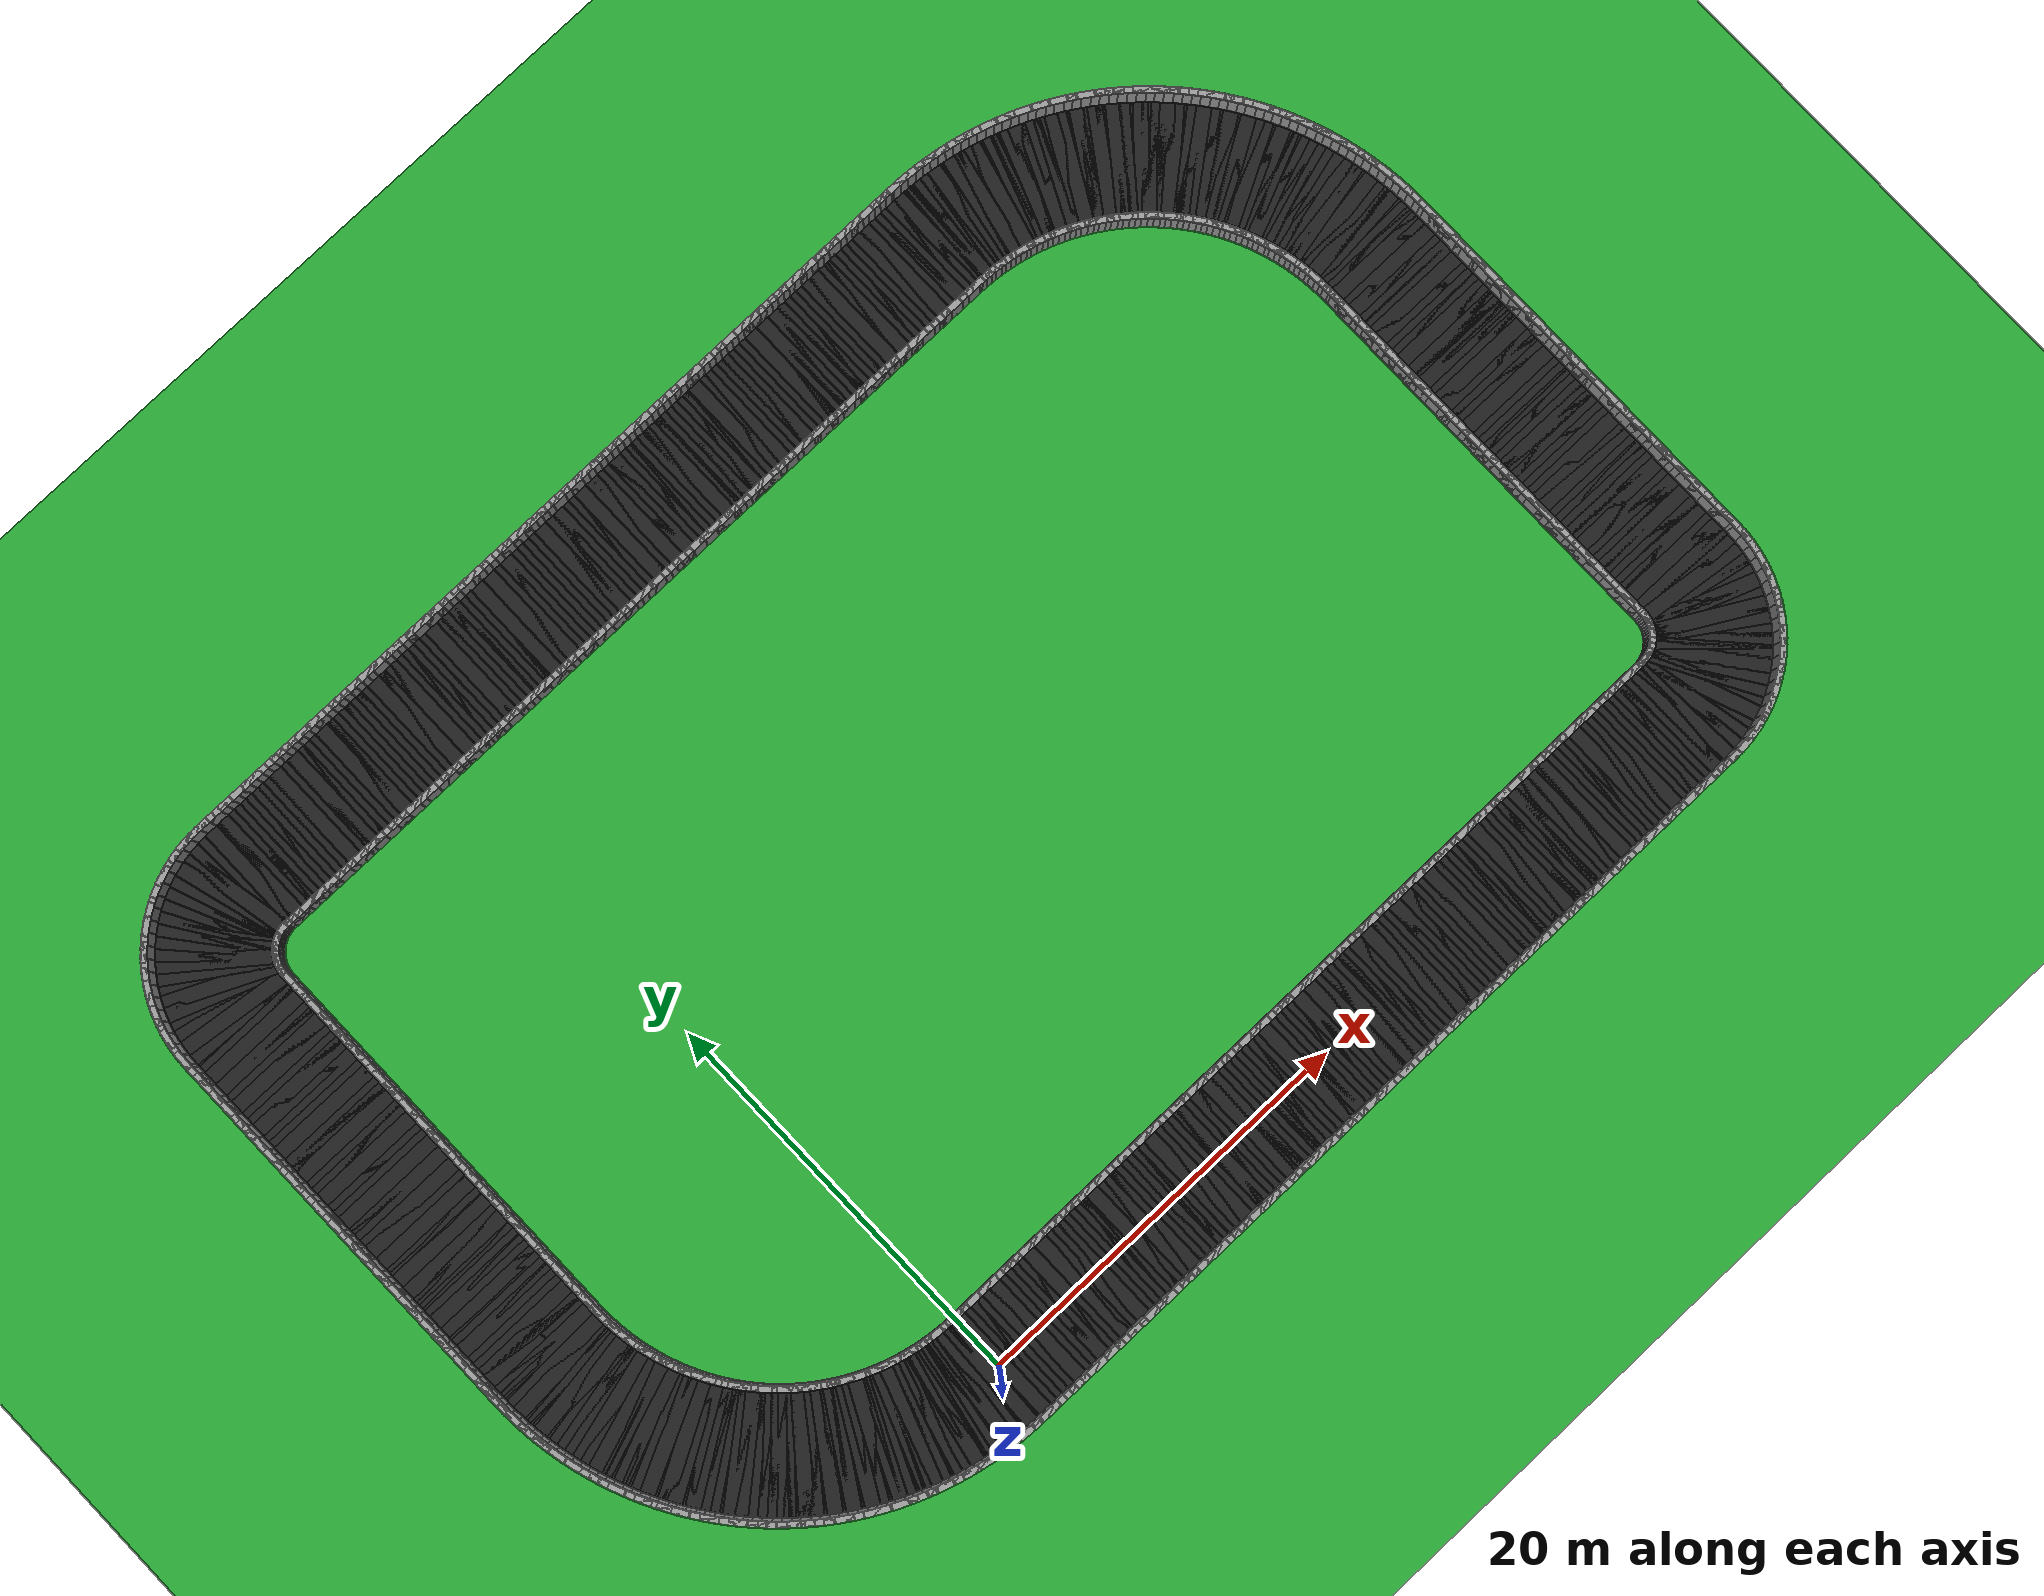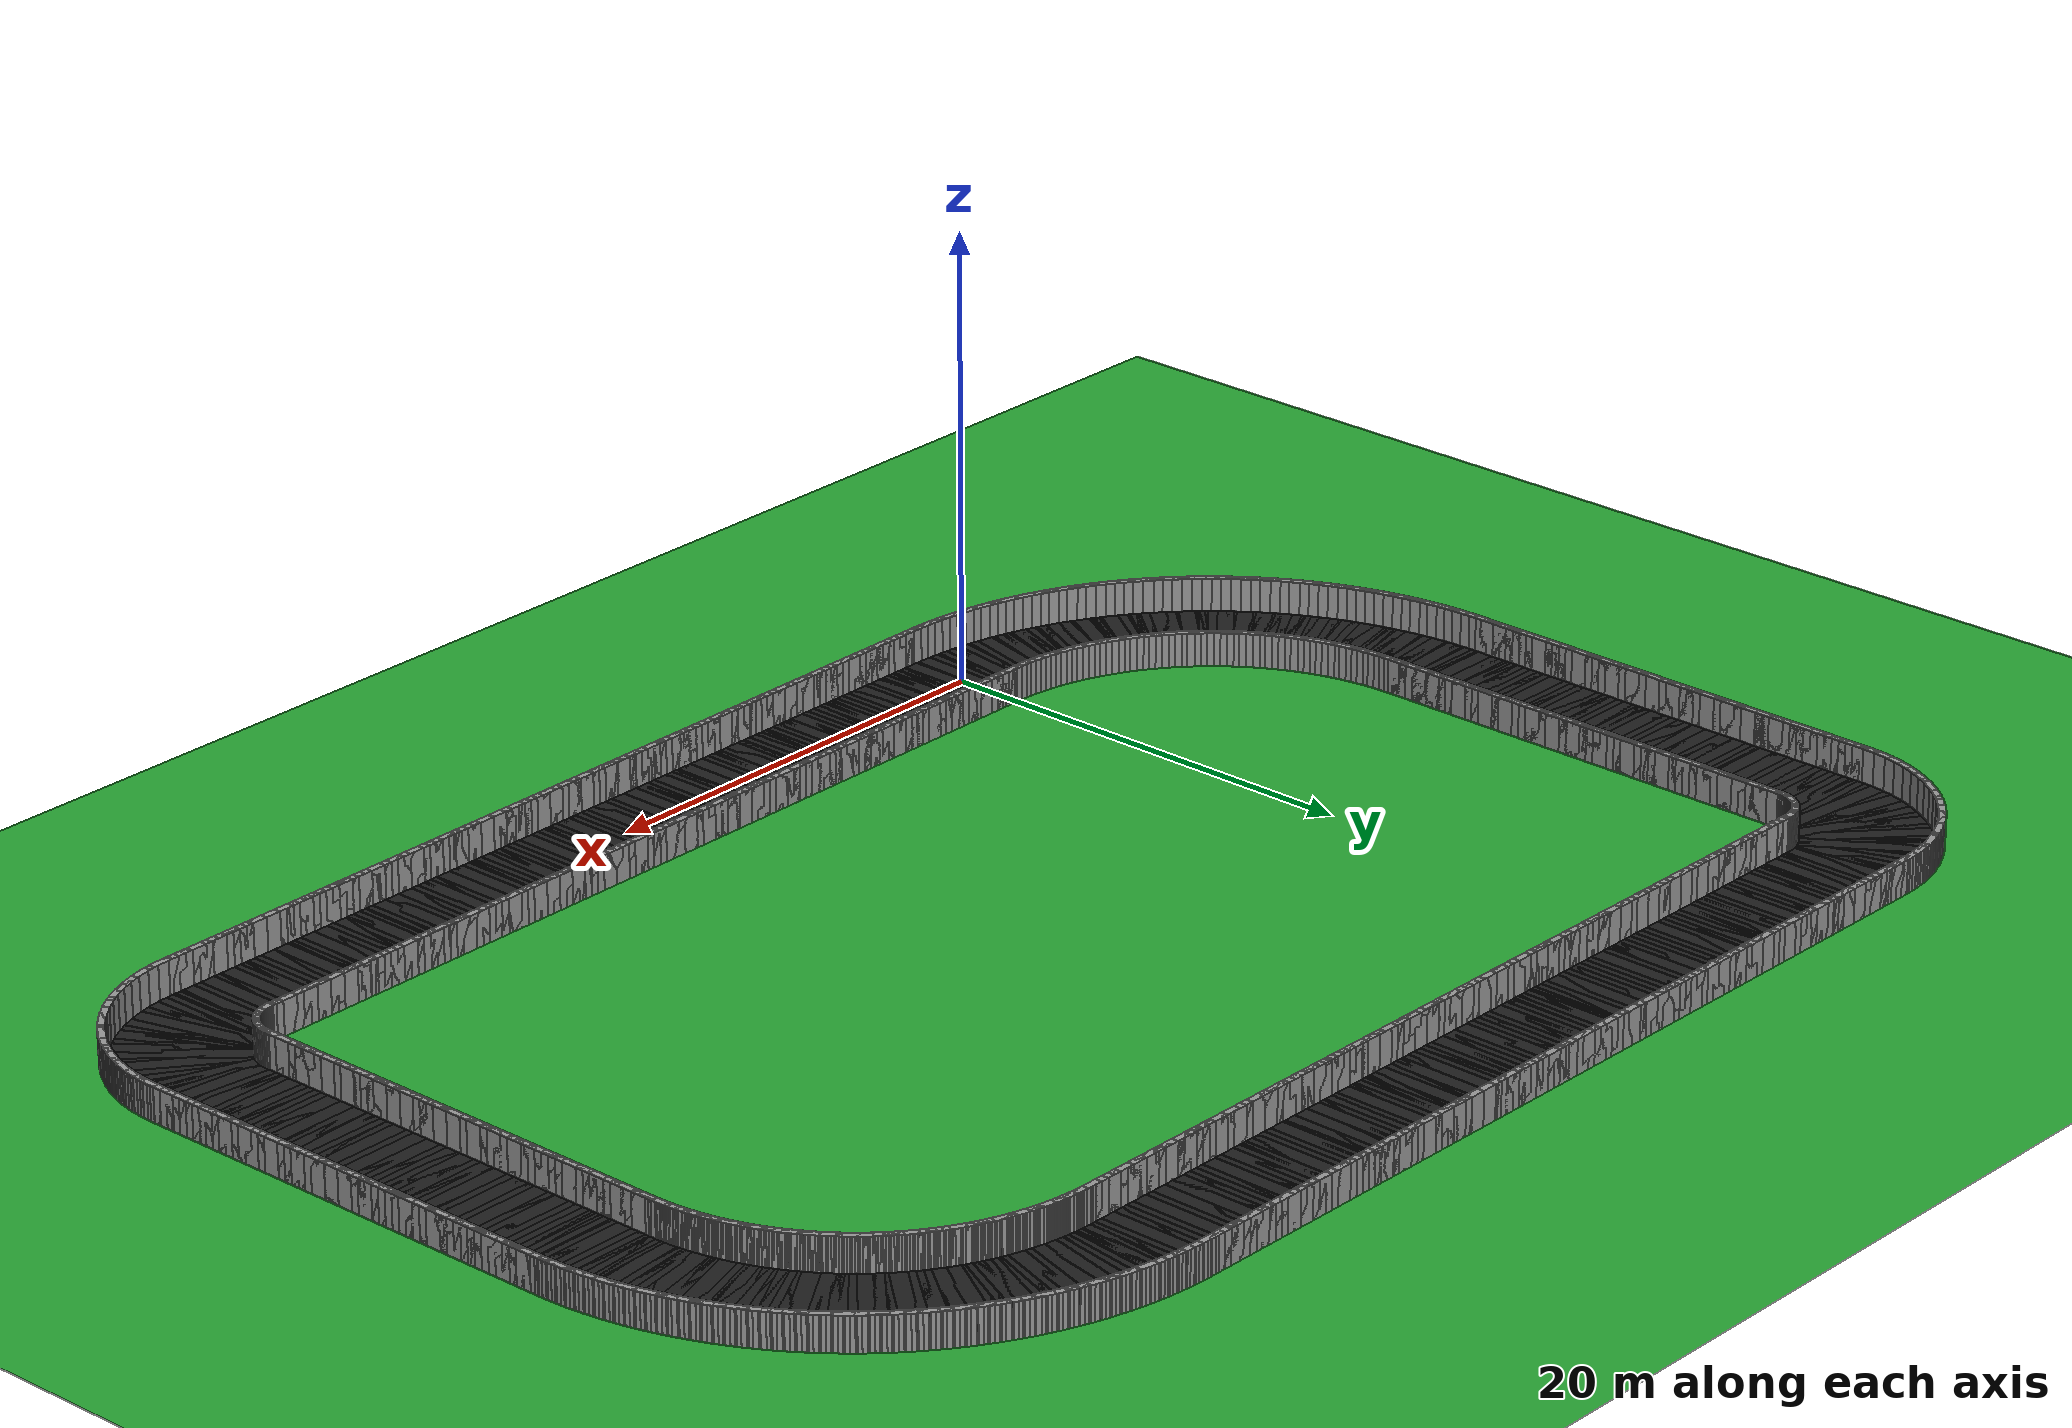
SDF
<?xml version="1.0" ?>
<sdf version="1.6">
  <world name="loop_speedloop">
    <physics type="ode">
      <max_step_size>0.001</max_step_size>
      <real_time_factor>1.0</real_time_factor>
      <real_time_update_rate>1000</real_time_update_rate>
    </physics>
    <include><uri>model://sun</uri></include>

    <model name="ground_plane">
      <static>true</static>
      <link name="link">
        <collision name="collision">
          <surface><friction><ode><mu>100</mu><mu2>50</mu2></ode></friction></surface>
          <geometry><plane><normal>0 0 1</normal>
            <size>120 120</size></plane></geometry>
        </collision>
        <visual name="visual">
          <geometry><plane><normal>0 0 1</normal>
            <size>120 120</size></plane></geometry>
          <material><script>
            <uri>file://media/materials/scripts/gazebo.material</uri>
            <name>Gazebo/Green</name></script></material>
        </visual>
      </link>
    </model>

    <model name="asphalt_0">
      <static>true</static>
      <pose>0.175 0.000 0.005 0 0 0.00000</pose>
      <link name="link">
        <visual name="visual">
          <geometry><box><size>0.710 5.500 0.010</size></box></geometry>
          <material><script><uri>file://media/materials/scripts/gazebo.material</uri><name>Gazebo/Black</name></script></material>
        </visual>
      </link>
    </model>
    <model name="curbL_0">
      <static>true</static>
      <pose>0.175 2.900 0.750 0 0 0.00000</pose>
      <link name="link">
        <collision name="collision">
          <geometry><box><size>0.710 0.300 1.500</size></box></geometry>
        </collision>
        <visual name="visual">
          <geometry><box><size>0.710 0.300 1.500</size></box></geometry>
          <material><script><uri>file://media/materials/scripts/gazebo.material</uri><name>Gazebo/Grey</name></script></material>
        </visual>
      </link>
    </model>
    <model name="curbR_0">
      <static>true</static>
      <pose>0.175 -2.900 0.750 0 0 0.00000</pose>
      <link name="link">
        <collision name="collision">
          <geometry><box><size>0.710 0.300 1.500</size></box></geometry>
        </collision>
        <visual name="visual">
          <geometry><box><size>0.710 0.300 1.500</size></box></geometry>
          <material><script><uri>file://media/materials/scripts/gazebo.material</uri><name>Gazebo/Grey</name></script></material>
        </visual>
      </link>
    </model>
    <model name="asphalt_1">
      <static>true</static>
      <pose>0.525 0.000 0.005 0 0 0.00000</pose>
      <link name="link">
        <visual name="visual">
          <geometry><box><size>0.710 5.500 0.010</size></box></geometry>
          <material><script><uri>file://media/materials/scripts/gazebo.material</uri><name>Gazebo/Black</name></script></material>
        </visual>
      </link>
    </model>
    <model name="curbL_1">
      <static>true</static>
      <pose>0.525 2.900 0.750 0 0 0.00000</pose>
      <link name="link">
        <collision name="collision">
          <geometry><box><size>0.710 0.300 1.500</size></box></geometry>
        </collision>
        <visual name="visual">
          <geometry><box><size>0.710 0.300 1.500</size></box></geometry>
          <material><script><uri>file://media/materials/scripts/gazebo.material</uri><name>Gazebo/Grey</name></script></material>
        </visual>
      </link>
    </model>
    <model name="curbR_1">
      <static>true</static>
      <pose>0.525 -2.900 0.750 0 0 0.00000</pose>
      <link name="link">
        <collision name="collision">
          <geometry><box><size>0.710 0.300 1.500</size></box></geometry>
        </collision>
        <visual name="visual">
          <geometry><box><size>0.710 0.300 1.500</size></box></geometry>
          <material><script><uri>file://media/materials/scripts/gazebo.material</uri><name>Gazebo/Grey</name></script></material>
        </visual>
      </link>
    </model>
    <model name="asphalt_2">
      <static>true</static>
      <pose>0.875 0.000 0.005 0 0 0.00000</pose>
      <link name="link">
        <visual name="visual">
          <geometry><box><size>0.710 5.500 0.010</size></box></geometry>
          <material><script><uri>file://media/materials/scripts/gazebo.material</uri><name>Gazebo/Black</name></script></material>
        </visual>
      </link>
    </model>
    <model name="curbL_2">
      <static>true</static>
      <pose>0.875 2.900 0.750 0 0 0.00000</pose>
      <link name="link">
        <collision name="collision">
          <geometry><box><size>0.710 0.300 1.500</size></box></geometry>
        </collision>
        <visual name="visual">
          <geometry><box><size>0.710 0.300 1.500</size></box></geometry>
          <material><script><uri>file://media/materials/scripts/gazebo.material</uri><name>Gazebo/Grey</name></script></material>
        </visual>
      </link>
    </model>
    <model name="curbR_2">
      <static>true</static>
      <pose>0.875 -2.900 0.750 0 0 0.00000</pose>
      <link name="link">
        <collision name="collision">
          <geometry><box><size>0.710 0.300 1.500</size></box></geometry>
        </collision>
        <visual name="visual">
          <geometry><box><size>0.710 0.300 1.500</size></box></geometry>
          <material><script><uri>file://media/materials/scripts/gazebo.material</uri><name>Gazebo/Grey</name></script></material>
        </visual>
      </link>
    </model>
    <model name="asphalt_3">
      <static>true</static>
      <pose>1.225 0.000 0.005 0 0 0.00000</pose>
      <link name="link">
        <visual name="visual">
          <geometry><box><size>0.710 5.500 0.010</size></box></geometry>
          <material><script><uri>file://media/materials/scripts/gazebo.material</uri><name>Gazebo/Black</name></script></material>
        </visual>
      </link>
    </model>
    <model name="curbL_3">
      <static>true</static>
      <pose>1.225 2.900 0.750 0 0 0.00000</pose>
      <link name="link">
        <collision name="collision">
          <geometry><box><size>0.710 0.300 1.500</size></box></geometry>
        </collision>
        <visual name="visual">
          <geometry><box><size>0.710 0.300 1.500</size></box></geometry>
          <material><script><uri>file://media/materials/scripts/gazebo.material</uri><name>Gazebo/Grey</name></script></material>
        </visual>
      </link>
    </model>
    <model name="curbR_3">
      <static>true</static>
      <pose>1.225 -2.900 0.750 0 0 0.00000</pose>
      <link name="link">
        <collision name="collision">
          <geometry><box><size>0.710 0.300 1.500</size></box></geometry>
        </collision>
        <visual name="visual">
          <geometry><box><size>0.710 0.300 1.500</size></box></geometry>
          <material><script><uri>file://media/materials/scripts/gazebo.material</uri><name>Gazebo/Grey</name></script></material>
        </visual>
      </link>
    </model>
    <model name="asphalt_4">
      <static>true</static>
      <pose>1.575 0.000 0.005 0 0 0.00000</pose>
      <link name="link">
        <visual name="visual">
          <geometry><box><size>0.710 5.500 0.010</size></box></geometry>
          <material><script><uri>file://media/materials/scripts/gazebo.material</uri><name>Gazebo/Black</name></script></material>
        </visual>
      </link>
    </model>
    <model name="curbL_4">
      <static>true</static>
      <pose>1.575 2.900 0.750 0 0 0.00000</pose>
      <link name="link">
        <collision name="collision">
          <geometry><box><size>0.710 0.300 1.500</size></box></geometry>
        </collision>
        <visual name="visual">
          <geometry><box><size>0.710 0.300 1.500</size></box></geometry>
          <material><script><uri>file://media/materials/scripts/gazebo.material</uri><name>Gazebo/Grey</name></script></material>
        </visual>
      </link>
    </model>
    <model name="curbR_4">
      <static>true</static>
      <pose>1.575 -2.900 0.750 0 0 0.00000</pose>
      <link name="link">
        <collision name="collision">
          <geometry><box><size>0.710 0.300 1.500</size></box></geometry>
        </collision>
        <visual name="visual">
          <geometry><box><size>0.710 0.300 1.500</size></box></geometry>
          <material><script><uri>file://media/materials/scripts/gazebo.material</uri><name>Gazebo/Grey</name></script></material>
        </visual>
      </link>
    </model>
    <model name="asphalt_5">
      <static>true</static>
      <pose>1.925 0.000 0.005 0 0 0.00000</pose>
      <link name="link">
        <visual name="visual">
          <geometry><box><size>0.710 5.500 0.010</size></box></geometry>
          <material><script><uri>file://media/materials/scripts/gazebo.material</uri><name>Gazebo/Black</name></script></material>
        </visual>
      </link>
    </model>
    <model name="curbL_5">
      <static>true</static>
      <pose>1.925 2.900 0.750 0 0 0.00000</pose>
      <link name="link">
        <collision name="collision">
          <geometry><box><size>0.710 0.300 1.500</size></box></geometry>
        </collision>
        <visual name="visual">
          <geometry><box><size>0.710 0.300 1.500</size></box></geometry>
          <material><script><uri>file://media/materials/scripts/gazebo.material</uri><name>Gazebo/Grey</name></script></material>
        </visual>
      </link>
    </model>
    <model name="curbR_5">
      <static>true</static>
      <pose>1.925 -2.900 0.750 0 0 0.00000</pose>
      <link name="link">
        <collision name="collision">
          <geometry><box><size>0.710 0.300 1.500</size></box></geometry>
        </collision>
        <visual name="visual">
          <geometry><box><size>0.710 0.300 1.500</size></box></geometry>
          <material><script><uri>file://media/materials/scripts/gazebo.material</uri><name>Gazebo/Grey</name></script></material>
        </visual>
      </link>
    </model>
    <model name="asphalt_6">
      <static>true</static>
      <pose>2.275 0.000 0.005 0 0 0.00000</pose>
      <link name="link">
        <visual name="visual">
          <geometry><box><size>0.710 5.500 0.010</size></box></geometry>
          <material><script><uri>file://media/materials/scripts/gazebo.material</uri><name>Gazebo/Black</name></script></material>
        </visual>
      </link>
    </model>
    <model name="curbL_6">
      <static>true</static>
      <pose>2.275 2.900 0.750 0 0 0.00000</pose>
      <link name="link">
        <collision name="collision">
          <geometry><box><size>0.710 0.300 1.500</size></box></geometry>
        </collision>
        <visual name="visual">
          <geometry><box><size>0.710 0.300 1.500</size></box></geometry>
          <material><script><uri>file://media/materials/scripts/gazebo.material</uri><name>Gazebo/Grey</name></script></material>
        </visual>
      </link>
    </model>
    <model name="curbR_6">
      <static>true</static>
      <pose>2.275 -2.900 0.750 0 0 0.00000</pose>
      <link name="link">
        <collision name="collision">
          <geometry><box><size>0.710 0.300 1.500</size></box></geometry>
        </collision>
        <visual name="visual">
          <geometry><box><size>0.710 0.300 1.500</size></box></geometry>
          <material><script><uri>file://media/materials/scripts/gazebo.material</uri><name>Gazebo/Grey</name></script></material>
        </visual>
      </link>
    </model>
    <model name="asphalt_7">
      <static>true</static>
      <pose>2.625 0.000 0.005 0 0 0.00000</pose>
      <link name="link">
        <visual name="visual">
          <geometry><box><size>0.710 5.500 0.010</size></box></geometry>
          <material><script><uri>file://media/materials/scripts/gazebo.material</uri><name>Gazebo/Black</name></script></material>
        </visual>
      </link>
    </model>
    <model name="curbL_7">
      <static>true</static>
      <pose>2.625 2.900 0.750 0 0 0.00000</pose>
      <link name="link">
        <collision name="collision">
          <geometry><box><size>0.710 0.300 1.500</size></box></geometry>
        </collision>
        <visual name="visual">
          <geometry><box><size>0.710 0.300 1.500</size></box></geometry>
          <material><script><uri>file://media/materials/scripts/gazebo.material</uri><name>Gazebo/Grey</name></script></material>
        </visual>
      </link>
    </model>
    <model name="curbR_7">
      <static>true</static>
      <pose>2.625 -2.900 0.750 0 0 0.00000</pose>
      <link name="link">
        <collision name="collision">
          <geometry><box><size>0.710 0.300 1.500</size></box></geometry>
        </collision>
        <visual name="visual">
          <geometry><box><size>0.710 0.300 1.500</size></box></geometry>
          <material><script><uri>file://media/materials/scripts/gazebo.material</uri><name>Gazebo/Grey</name></script></material>
        </visual>
      </link>
    </model>
    <model name="asphalt_8">
      <static>true</static>
      <pose>2.975 0.000 0.005 0 0 0.00000</pose>
      <link name="link">
        <visual name="visual">
          <geometry><box><size>0.710 5.500 0.010</size></box></geometry>
          <material><script><uri>file://media/materials/scripts/gazebo.material</uri><name>Gazebo/Black</name></script></material>
        </visual>
      </link>
    </model>
    <model name="curbL_8">
      <static>true</static>
      <pose>2.975 2.900 0.750 0 0 0.00000</pose>
      <link name="link">
        <collision name="collision">
          <geometry><box><size>0.710 0.300 1.500</size></box></geometry>
        </collision>
        <visual name="visual">
          <geometry><box><size>0.710 0.300 1.500</size></box></geometry>
          <material><script><uri>file://media/materials/scripts/gazebo.material</uri><name>Gazebo/Grey</name></script></material>
        </visual>
      </link>
    </model>
    <model name="curbR_8">
      <static>true</static>
      <pose>2.975 -2.900 0.750 0 0 0.00000</pose>
      <link name="link">
        <collision name="collision">
          <geometry><box><size>0.710 0.300 1.500</size></box></geometry>
        </collision>
        <visual name="visual">
          <geometry><box><size>0.710 0.300 1.500</size></box></geometry>
          <material><script><uri>file://media/materials/scripts/gazebo.material</uri><name>Gazebo/Grey</name></script></material>
        </visual>
      </link>
    </model>
    <model name="asphalt_9">
      <static>true</static>
      <pose>3.325 0.000 0.005 0 0 0.00000</pose>
      <link name="link">
        <visual name="visual">
          <geometry><box><size>0.710 5.500 0.010</size></box></geometry>
          <material><script><uri>file://media/materials/scripts/gazebo.material</uri><name>Gazebo/Black</name></script></material>
        </visual>
      </link>
    </model>
    <model name="curbL_9">
      <static>true</static>
      <pose>3.325 2.900 0.750 0 0 0.00000</pose>
      <link name="link">
        <collision name="collision">
          <geometry><box><size>0.710 0.300 1.500</size></box></geometry>
        </collision>
        <visual name="visual">
          <geometry><box><size>0.710 0.300 1.500</size></box></geometry>
          <material><script><uri>file://media/materials/scripts/gazebo.material</uri><name>Gazebo/Grey</name></script></material>
        </visual>
      </link>
    </model>
    <model name="curbR_9">
      <static>true</static>
      <pose>3.325 -2.900 0.750 0 0 0.00000</pose>
      <link name="link">
        <collision name="collision">
          <geometry><box><size>0.710 0.300 1.500</size></box></geometry>
        </collision>
        <visual name="visual">
          <geometry><box><size>0.710 0.300 1.500</size></box></geometry>
          <material><script><uri>file://media/materials/scripts/gazebo.material</uri><name>Gazebo/Grey</name></script></material>
        </visual>
      </link>
    </model>
    <model name="asphalt_10">
      <static>true</static>
      <pose>3.675 0.000 0.005 0 0 0.00000</pose>
      <link name="link">
        <visual name="visual">
          <geometry><box><size>0.710 5.500 0.010</size></box></geometry>
          <material><script><uri>file://media/materials/scripts/gazebo.material</uri><name>Gazebo/Black</name></script></material>
        </visual>
      </link>
    </model>
    <model name="curbL_10">
      <static>true</static>
      <pose>3.675 2.900 0.750 0 0 0.00000</pose>
      <link name="link">
        <collision name="collision">
          <geometry><box><size>0.710 0.300 1.500</size></box></geometry>
        </collision>
        <visual name="visual">
          <geometry><box><size>0.710 0.300 1.500</size></box></geometry>
          <material><script><uri>file://media/materials/scripts/gazebo.material</uri><name>Gazebo/Grey</name></script></material>
        </visual>
      </link>
    </model>
    <model name="curbR_10">
      <static>true</static>
      <pose>3.675 -2.900 0.750 0 0 0.00000</pose>
      <link name="link">
        <collision name="collision">
          <geometry><box><size>0.710 0.300 1.500</size></box></geometry>
        </collision>
        <visual name="visual">
          <geometry><box><size>0.710 0.300 1.500</size></box></geometry>
          <material><script><uri>file://media/materials/scripts/gazebo.material</uri><name>Gazebo/Grey</name></script></material>
        </visual>
      </link>
    </model>
    <model name="asphalt_11">
      <static>true</static>
      <pose>4.025 0.000 0.005 0 0 0.00000</pose>
      <link name="link">
        <visual name="visual">
          <geometry><box><size>0.710 5.500 0.010</size></box></geometry>
          <material><script><uri>file://media/materials/scripts/gazebo.material</uri><name>Gazebo/Black</name></script></material>
        </visual>
      </link>
    </model>
    <model name="curbL_11">
      <static>true</static>
      <pose>4.025 2.900 0.750 0 0 0.00000</pose>
      <link name="link">
        <collision name="collision">
          <geometry><box><size>0.710 0.300 1.500</size></box></geometry>
        </collision>
        <visual name="visual">
          <geometry><box><size>0.710 0.300 1.500</size></box></geometry>
          <material><script><uri>file://media/materials/scripts/gazebo.material</uri><name>Gazebo/Grey</name></script></material>
        </visual>
      </link>
    </model>
    <model name="curbR_11">
      <static>true</static>
      <pose>4.025 -2.900 0.750 0 0 0.00000</pose>
      <link name="link">
        <collision name="collision">
          <geometry><box><size>0.710 0.300 1.500</size></box></geometry>
        </collision>
        <visual name="visual">
          <geometry><box><size>0.710 0.300 1.500</size></box></geometry>
          <material><script><uri>file://media/materials/scripts/gazebo.material</uri><name>Gazebo/Grey</name></script></material>
        </visual>
      </link>
    </model>
    <model name="asphalt_12">
      <static>true</static>
      <pose>4.375 0.000 0.005 0 0 0.00000</pose>
      <link name="link">
        <visual name="visual">
          <geometry><box><size>0.710 5.500 0.010</size></box></geometry>
          <material><script><uri>file://media/materials/scripts/gazebo.material</uri><name>Gazebo/Black</name></script></material>
        </visual>
      </link>
    </model>
    <model name="curbL_12">
      <static>true</static>
      <pose>4.375 2.900 0.750 0 0 0.00000</pose>
      <link name="link">
        <collision name="collision">
          <geometry><box><size>0.710 0.300 1.500</size></box></geometry>
        </collision>
        <visual name="visual">
          <geometry><box><size>0.710 0.300 1.500</size></box></geometry>
          <material><script><uri>file://media/materials/scripts/gazebo.material</uri><name>Gazebo/Grey</name></script></material>
        </visual>
      </link>
    </model>
    <model name="curbR_12">
      <static>true</static>
      <pose>4.375 -2.900 0.750 0 0 0.00000</pose>
      <link name="link">
        <collision name="collision">
          <geometry><box><size>0.710 0.300 1.500</size></box></geometry>
        </collision>
        <visual name="visual">
          <geometry><box><size>0.710 0.300 1.500</size></box></geometry>
          <material><script><uri>file://media/materials/scripts/gazebo.material</uri><name>Gazebo/Grey</name></script></material>
        </visual>
      </link>
    </model>
    <model name="asphalt_13">
      <static>true</static>
      <pose>4.725 0.000 0.005 0 0 0.00000</pose>
      <link name="link">
        <visual name="visual">
          <geometry><box><size>0.710 5.500 0.010</size></box></geometry>
          <material><script><uri>file://media/materials/scripts/gazebo.material</uri><name>Gazebo/Black</name></script></material>
        </visual>
      </link>
    </model>
    <model name="curbL_13">
      <static>true</static>
      <pose>4.725 2.900 0.750 0 0 0.00000</pose>
      <link name="link">
        <collision name="collision">
          <geometry><box><size>0.710 0.300 1.500</size></box></geometry>
        </collision>
        <visual name="visual">
          <geometry><box><size>0.710 0.300 1.500</size></box></geometry>
          <material><script><uri>file://media/materials/scripts/gazebo.material</uri><name>Gazebo/Grey</name></script></material>
        </visual>
      </link>
    </model>
    <model name="curbR_13">
      <static>true</static>
      <pose>4.725 -2.900 0.750 0 0 0.00000</pose>
      <link name="link">
        <collision name="collision">
          <geometry><box><size>0.710 0.300 1.500</size></box></geometry>
        </collision>
        <visual name="visual">
          <geometry><box><size>0.710 0.300 1.500</size></box></geometry>
          <material><script><uri>file://media/materials/scripts/gazebo.material</uri><name>Gazebo/Grey</name></script></material>
        </visual>
      </link>
    </model>
    <model name="asphalt_14">
      <static>true</static>
      <pose>5.075 0.000 0.005 0 0 0.00000</pose>
      <link name="link">
        <visual name="visual">
          <geometry><box><size>0.710 5.500 0.010</size></box></geometry>
          <material><script><uri>file://media/materials/scripts/gazebo.material</uri><name>Gazebo/Black</name></script></material>
        </visual>
      </link>
    </model>
    <model name="curbL_14">
      <static>true</static>
      <pose>5.075 2.900 0.750 0 0 0.00000</pose>
      <link name="link">
        <collision name="collision">
          <geometry><box><size>0.710 0.300 1.500</size></box></geometry>
        </collision>
        <visual name="visual">
          <geometry><box><size>0.710 0.300 1.500</size></box></geometry>
          <material><script><uri>file://media/materials/scripts/gazebo.material</uri><name>Gazebo/Grey</name></script></material>
        </visual>
      </link>
    </model>
    <model name="curbR_14">
      <static>true</static>
      <pose>5.075 -2.900 0.750 0 0 0.00000</pose>
      <link name="link">
        <collision name="collision">
          <geometry><box><size>0.710 0.300 1.500</size></box></geometry>
        </collision>
        <visual name="visual">
          <geometry><box><size>0.710 0.300 1.500</size></box></geometry>
          <material><script><uri>file://media/materials/scripts/gazebo.material</uri><name>Gazebo/Grey</name></script></material>
        </visual>
      </link>
    </model>
    <model name="asphalt_15">
      <static>true</static>
      <pose>5.425 0.000 0.005 0 0 0.00000</pose>
      <link name="link">
        <visual name="visual">
          <geometry><box><size>0.710 5.500 0.010</size></box></geometry>
          <material><script><uri>file://media/materials/scripts/gazebo.material</uri><name>Gazebo/Black</name></script></material>
        </visual>
      </link>
    </model>
    <model name="curbL_15">
      <static>true</static>
      <pose>5.425 2.900 0.750 0 0 0.00000</pose>
      <link name="link">
        <collision name="collision">
          <geometry><box><size>0.710 0.300 1.500</size></box></geometry>
        </collision>
        <visual name="visual">
          <geometry><box><size>0.710 0.300 1.500</size></box></geometry>
          <material><script><uri>file://media/materials/scripts/gazebo.material</uri><name>Gazebo/Grey</name></script></material>
        </visual>
      </link>
    </model>
    <model name="curbR_15">
      <static>true</static>
      <pose>5.425 -2.900 0.750 0 0 0.00000</pose>
      <link name="link">
        <collision name="collision">
          <geometry><box><size>0.710 0.300 1.500</size></box></geometry>
        </collision>
        <visual name="visual">
          <geometry><box><size>0.710 0.300 1.500</size></box></geometry>
          <material><script><uri>file://media/materials/scripts/gazebo.material</uri><name>Gazebo/Grey</name></script></material>
        </visual>
      </link>
    </model>
    <model name="asphalt_16">
      <static>true</static>
      <pose>5.775 0.000 0.005 0 0 0.00000</pose>
      <link name="link">
        <visual name="visual">
          <geometry><box><size>0.710 5.500 0.010</size></box></geometry>
          <material><script><uri>file://media/materials/scripts/gazebo.material</uri><name>Gazebo/Black</name></script></material>
        </visual>
      </link>
    </model>
    <model name="curbL_16">
      <static>true</static>
      <pose>5.775 2.900 0.750 0 0 0.00000</pose>
      <link name="link">
        <collision name="collision">
          <geometry><box><size>0.710 0.300 1.500</size></box></geometry>
        </collision>
        <visual name="visual">
          <geometry><box><size>0.710 0.300 1.500</size></box></geometry>
          <material><script><uri>file://media/materials/scripts/gazebo.material</uri><name>Gazebo/Grey</name></script></material>
        </visual>
      </link>
    </model>
    <model name="curbR_16">
      <static>true</static>
      <pose>5.775 -2.900 0.750 0 0 0.00000</pose>
      <link name="link">
        <collision name="collision">
          <geometry><box><size>0.710 0.300 1.500</size></box></geometry>
        </collision>
        <visual name="visual">
          <geometry><box><size>0.710 0.300 1.500</size></box></geometry>
          <material><script><uri>file://media/materials/scripts/gazebo.material</uri><name>Gazebo/Grey</name></script></material>
        </visual>
      </link>
    </model>
    <model name="asphalt_17">
      <static>true</static>
      <pose>6.125 0.000 0.005 0 0 0.00000</pose>
      <link name="link">
        <visual name="visual">
          <geometry><box><size>0.710 5.500 0.010</size></box></geometry>
          <material><script><uri>file://media/materials/scripts/gazebo.material</uri><name>Gazebo/Black</name></script></material>
        </visual>
      </link>
    </model>
    <model name="curbL_17">
      <static>true</static>
      <pose>6.125 2.900 0.750 0 0 0.00000</pose>
      <link name="link">
        <collision name="collision">
          <geometry><box><size>0.710 0.300 1.500</size></box></geometry>
        </collision>
        <visual name="visual">
          <geometry><box><size>0.710 0.300 1.500</size></box></geometry>
          <material><script><uri>file://media/materials/scripts/gazebo.material</uri><name>Gazebo/Grey</name></script></material>
        </visual>
      </link>
    </model>
    <model name="curbR_17">
      <static>true</static>
      <pose>6.125 -2.900 0.750 0 0 0.00000</pose>
      <link name="link">
        <collision name="collision">
          <geometry><box><size>0.710 0.300 1.500</size></box></geometry>
        </collision>
        <visual name="visual">
          <geometry><box><size>0.710 0.300 1.500</size></box></geometry>
          <material><script><uri>file://media/materials/scripts/gazebo.material</uri><name>Gazebo/Grey</name></script></material>
        </visual>
      </link>
    </model>
    <model name="asphalt_18">
      <static>true</static>
      <pose>6.475 0.000 0.005 0 0 0.00000</pose>
      <link name="link">
        <visual name="visual">
          <geometry><box><size>0.710 5.500 0.010</size></box></geometry>
          <material><script><uri>file://media/materials/scripts/gazebo.material</uri><name>Gazebo/Black</name></script></material>
        </visual>
      </link>
    </model>
    <model name="curbL_18">
      <static>true</static>
      <pose>6.475 2.900 0.750 0 0 0.00000</pose>
      <link name="link">
        <collision name="collision">
          <geometry><box><size>0.710 0.300 1.500</size></box></geometry>
        </collision>
        <visual name="visual">
          <geometry><box><size>0.710 0.300 1.500</size></box></geometry>
          <material><script><uri>file://media/materials/scripts/gazebo.material</uri><name>Gazebo/Grey</name></script></material>
        </visual>
      </link>
    </model>
    <model name="curbR_18">
      <static>true</static>
      <pose>6.475 -2.900 0.750 0 0 0.00000</pose>
      <link name="link">
        <collision name="collision">
          <geometry><box><size>0.710 0.300 1.500</size></box></geometry>
        </collision>
        <visual name="visual">
          <geometry><box><size>0.710 0.300 1.500</size></box></geometry>
          <material><script><uri>file://media/materials/scripts/gazebo.material</uri><name>Gazebo/Grey</name></script></material>
        </visual>
      </link>
    </model>
    <model name="asphalt_19">
      <static>true</static>
      <pose>6.825 0.000 0.005 0 0 0.00000</pose>
      <link name="link">
        <visual name="visual">
          <geometry><box><size>0.710 5.500 0.010</size></box></geometry>
          <material><script><uri>file://media/materials/scripts/gazebo.material</uri><name>Gazebo/Black</name></script></material>
        </visual>
      </link>
    </model>
    <model name="curbL_19">
      <static>true</static>
      <pose>6.825 2.900 0.750 0 0 0.00000</pose>
      <link name="link">
        <collision name="collision">
          <geometry><box><size>0.710 0.300 1.500</size></box></geometry>
        </collision>
        <visual name="visual">
          <geometry><box><size>0.710 0.300 1.500</size></box></geometry>
          <material><script><uri>file://media/materials/scripts/gazebo.material</uri><name>Gazebo/Grey</name></script></material>
        </visual>
      </link>
    </model>
    <model name="curbR_19">
      <static>true</static>
      <pose>6.825 -2.900 0.750 0 0 0.00000</pose>
      <link name="link">
        <collision name="collision">
          <geometry><box><size>0.710 0.300 1.500</size></box></geometry>
        </collision>
        <visual name="visual">
          <geometry><box><size>0.710 0.300 1.500</size></box></geometry>
          <material><script><uri>file://media/materials/scripts/gazebo.material</uri><name>Gazebo/Grey</name></script></material>
        </visual>
      </link>
    </model>
    <model name="asphalt_20">
      <static>true</static>
      <pose>7.175 0.000 0.005 0 0 0.00000</pose>
      <link name="link">
        <visual name="visual">
          <geometry><box><size>0.710 5.500 0.010</size></box></geometry>
          <material><script><uri>file://media/materials/scripts/gazebo.material</uri><name>Gazebo/Black</name></script></material>
        </visual>
      </link>
    </model>
    <model name="curbL_20">
      <static>true</static>
      <pose>7.175 2.900 0.750 0 0 0.00000</pose>
      <link name="link">
        <collision name="collision">
          <geometry><box><size>0.710 0.300 1.500</size></box></geometry>
        </collision>
        <visual name="visual">
          <geometry><box><size>0.710 0.300 1.500</size></box></geometry>
          <material><script><uri>file://media/materials/scripts/gazebo.material</uri><name>Gazebo/Grey</name></script></material>
        </visual>
      </link>
    </model>
    <model name="curbR_20">
      <static>true</static>
      <pose>7.175 -2.900 0.750 0 0 0.00000</pose>
      <link name="link">
        <collision name="collision">
          <geometry><box><size>0.710 0.300 1.500</size></box></geometry>
        </collision>
        <visual name="visual">
          <geometry><box><size>0.710 0.300 1.500</size></box></geometry>
          <material><script><uri>file://media/materials/scripts/gazebo.material</uri><name>Gazebo/Grey</name></script></material>
        </visual>
      </link>
    </model>
    <model name="asphalt_21">
      <static>true</static>
      <pose>7.525 0.000 0.005 0 0 0.00000</pose>
      <link name="link">
        <visual name="visual">
          <geometry><box><size>0.710 5.500 0.010</size></box></geometry>
          <material><script><uri>file://media/materials/scripts/gazebo.material</uri><name>Gazebo/Black</name></script></material>
        </visual>
      </link>
    </model>
    <model name="curbL_21">
      <static>true</static>
      <pose>7.525 2.900 0.750 0 0 0.00000</pose>
      <link name="link">
        <collision name="collision">
          <geometry><box><size>0.710 0.300 1.500</size></box></geometry>
        </collision>
        <visual name="visual">
          <geometry><box><size>0.710 0.300 1.500</size></box></geometry>
          <material><script><uri>file://media/materials/scripts/gazebo.material</uri><name>Gazebo/Grey</name></script></material>
        </visual>
      </link>
    </model>
    <model name="curbR_21">
      <static>true</static>
      <pose>7.525 -2.900 0.750 0 0 0.00000</pose>
      <link name="link">
        <collision name="collision">
          <geometry><box><size>0.710 0.300 1.500</size></box></geometry>
        </collision>
        <visual name="visual">
          <geometry><box><size>0.710 0.300 1.500</size></box></geometry>
          <material><script><uri>file://media/materials/scripts/gazebo.material</uri><name>Gazebo/Grey</name></script></material>
        </visual>
      </link>
    </model>
    <model name="asphalt_22">
      <static>true</static>
      <pose>7.875 0.000 0.005 0 0 0.00000</pose>
      <link name="link">
        <visual name="visual">
          <geometry><box><size>0.710 5.500 0.010</size></box></geometry>
          <material><script><uri>file://media/materials/scripts/gazebo.material</uri><name>Gazebo/Black</name></script></material>
        </visual>
      </link>
    </model>
    <model name="curbL_22">
      <static>true</static>
      <pose>7.875 2.900 0.750 0 0 0.00000</pose>
      <link name="link">
        <collision name="collision">
          <geometry><box><size>0.710 0.300 1.500</size></box></geometry>
        </collision>
        <visual name="visual">
          <geometry><box><size>0.710 0.300 1.500</size></box></geometry>
          <material><script><uri>file://media/materials/scripts/gazebo.material</uri><name>Gazebo/Grey</name></script></material>
        </visual>
      </link>
    </model>
    <model name="curbR_22">
      <static>true</static>
      <pose>7.875 -2.900 0.750 0 0 0.00000</pose>
      <link name="link">
        <collision name="collision">
          <geometry><box><size>0.710 0.300 1.500</size></box></geometry>
        </collision>
        <visual name="visual">
          <geometry><box><size>0.710 0.300 1.500</size></box></geometry>
          <material><script><uri>file://media/materials/scripts/gazebo.material</uri><name>Gazebo/Grey</name></script></material>
        </visual>
      </link>
    </model>
    <model name="asphalt_23">
      <static>true</static>
      <pose>8.225 0.000 0.005 0 0 0.00000</pose>
      <link name="link">
        <visual name="visual">
          <geometry><box><size>0.710 5.500 0.010</size></box></geometry>
          <material><script><uri>file://media/materials/scripts/gazebo.material</uri><name>Gazebo/Black</name></script></material>
        </visual>
      </link>
    </model>
    <model name="curbL_23">
      <static>true</static>
      <pose>8.225 2.900 0.750 0 0 0.00000</pose>
      <link name="link">
        <collision name="collision">
          <geometry><box><size>0.710 0.300 1.500</size></box></geometry>
        </collision>
        <visual name="visual">
          <geometry><box><size>0.710 0.300 1.500</size></box></geometry>
          <material><script><uri>file://media/materials/scripts/gazebo.material</uri><name>Gazebo/Grey</name></script></material>
        </visual>
      </link>
    </model>
    <model name="curbR_23">
      <static>true</static>
      <pose>8.225 -2.900 0.750 0 0 0.00000</pose>
      <link name="link">
        <collision name="collision">
          <geometry><box><size>0.710 0.300 1.500</size></box></geometry>
        </collision>
        <visual name="visual">
          <geometry><box><size>0.710 0.300 1.500</size></box></geometry>
          <material><script><uri>file://media/materials/scripts/gazebo.material</uri><name>Gazebo/Grey</name></script></material>
        </visual>
      </link>
    </model>
    <model name="asphalt_24">
      <static>true</static>
      <pose>8.575 0.000 0.005 0 0 0.00000</pose>
      <link name="link">
        <visual name="visual">
          <geometry><box><size>0.710 5.500 0.010</size></box></geometry>
          <material><script><uri>file://media/materials/scripts/gazebo.material</uri><name>Gazebo/Black</name></script></material>
        </visual>
      </link>
    </model>
    <model name="curbL_24">
      <static>true</static>
      <pose>8.575 2.900 0.750 0 0 0.00000</pose>
      <link name="link">
        <collision name="collision">
          <geometry><box><size>0.710 0.300 1.500</size></box></geometry>
        </collision>
        <visual name="visual">
          <geometry><box><size>0.710 0.300 1.500</size></box></geometry>
          <material><script><uri>file://media/materials/scripts/gazebo.material</uri><name>Gazebo/Grey</name></script></material>
        </visual>
      </link>
    </model>
    <model name="curbR_24">
      <static>true</static>
      <pose>8.575 -2.900 0.750 0 0 0.00000</pose>
      <link name="link">
        <collision name="collision">
          <geometry><box><size>0.710 0.300 1.500</size></box></geometry>
        </collision>
        <visual name="visual">
          <geometry><box><size>0.710 0.300 1.500</size></box></geometry>
          <material><script><uri>file://media/materials/scripts/gazebo.material</uri><name>Gazebo/Grey</name></script></material>
        </visual>
      </link>
    </model>
    <model name="asphalt_25">
      <static>true</static>
      <pose>8.925 0.000 0.005 0 0 0.00000</pose>
      <link name="link">
        <visual name="visual">
          <geometry><box><size>0.710 5.500 0.010</size></box></geometry>
          <material><script><uri>file://media/materials/scripts/gazebo.material</uri><name>Gazebo/Black</name></script></material>
        </visual>
      </link>
    </model>
    <model name="curbL_25">
      <static>true</static>
      <pose>8.925 2.900 0.750 0 0 0.00000</pose>
      <link name="link">
        <collision name="collision">
          <geometry><box><size>0.710 0.300 1.500</size></box></geometry>
        </collision>
        <visual name="visual">
          <geometry><box><size>0.710 0.300 1.500</size></box></geometry>
          <material><script><uri>file://media/materials/scripts/gazebo.material</uri><name>Gazebo/Grey</name></script></material>
        </visual>
      </link>
    </model>
    <model name="curbR_25">
      <static>true</static>
      <pose>8.925 -2.900 0.750 0 0 0.00000</pose>
      <link name="link">
        <collision name="collision">
          <geometry><box><size>0.710 0.300 1.500</size></box></geometry>
        </collision>
        <visual name="visual">
          <geometry><box><size>0.710 0.300 1.500</size></box></geometry>
          <material><script><uri>file://media/materials/scripts/gazebo.material</uri><name>Gazebo/Grey</name></script></material>
        </visual>
      </link>
    </model>
    <model name="asphalt_26">
      <static>true</static>
      <pose>9.275 0.000 0.005 0 0 0.00000</pose>
      <link name="link">
        <visual name="visual">
          <geometry><box><size>0.710 5.500 0.010</size></box></geometry>
          <material><script><uri>file://media/materials/scripts/gazebo.material</uri><name>Gazebo/Black</name></script></material>
        </visual>
      </link>
    </model>
    <model name="curbL_26">
      <static>true</static>
      <pose>9.275 2.900 0.750 0 0 0.00000</pose>
      <link name="link">
        <collision name="collision">
          <geometry><box><size>0.710 0.300 1.500</size></box></geometry>
        </collision>
        <visual name="visual">
          <geometry><box><size>0.710 0.300 1.500</size></box></geometry>
          <material><script><uri>file://media/materials/scripts/gazebo.material</uri><name>Gazebo/Grey</name></script></material>
        </visual>
      </link>
    </model>
    <model name="curbR_26">
      <static>true</static>
      <pose>9.275 -2.900 0.750 0 0 0.00000</pose>
      <link name="link">
        <collision name="collision">
          <geometry><box><size>0.710 0.300 1.500</size></box></geometry>
        </collision>
        <visual name="visual">
          <geometry><box><size>0.710 0.300 1.500</size></box></geometry>
          <material><script><uri>file://media/materials/scripts/gazebo.material</uri><name>Gazebo/Grey</name></script></material>
        </visual>
      </link>
    </model>
    <model name="asphalt_27">
      <static>true</static>
      <pose>9.625 0.000 0.005 0 0 0.00000</pose>
      <link name="link">
        <visual name="visual">
          <geometry><box><size>0.710 5.500 0.010</size></box></geometry>
          <material><script><uri>file://media/materials/scripts/gazebo.material</uri><name>Gazebo/Black</name></script></material>
        </visual>
      </link>
    </model>
    <model name="curbL_27">
      <static>true</static>
      <pose>9.625 2.900 0.750 0 0 0.00000</pose>
      <link name="link">
        <collision name="collision">
          <geometry><box><size>0.710 0.300 1.500</size></box></geometry>
        </collision>
        <visual name="visual">
          <geometry><box><size>0.710 0.300 1.500</size></box></geometry>
          <material><script><uri>file://media/materials/scripts/gazebo.material</uri><name>Gazebo/Grey</name></script></material>
        </visual>
      </link>
    </model>
    <model name="curbR_27">
      <static>true</static>
      <pose>9.625 -2.900 0.750 0 0 0.00000</pose>
      <link name="link">
        <collision name="collision">
          <geometry><box><size>0.710 0.300 1.500</size></box></geometry>
        </collision>
        <visual name="visual">
          <geometry><box><size>0.710 0.300 1.500</size></box></geometry>
          <material><script><uri>file://media/materials/scripts/gazebo.material</uri><name>Gazebo/Grey</name></script></material>
        </visual>
      </link>
    </model>
    <model name="asphalt_28">
      <static>true</static>
      <pose>9.975 0.000 0.005 0 0 0.00000</pose>
      <link name="link">
        <visual name="visual">
          <geometry><box><size>0.710 5.500 0.010</size></box></geometry>
          <material><script><uri>file://media/materials/scripts/gazebo.material</uri><name>Gazebo/Black</name></script></material>
        </visual>
      </link>
    </model>
    <model name="curbL_28">
      <static>true</static>
      <pose>9.975 2.900 0.750 0 0 0.00000</pose>
      <link name="link">
        <collision name="collision">
          <geometry><box><size>0.710 0.300 1.500</size></box></geometry>
        </collision>
        <visual name="visual">
          <geometry><box><size>0.710 0.300 1.500</size></box></geometry>
          <material><script><uri>file://media/materials/scripts/gazebo.material</uri><name>Gazebo/Grey</name></script></material>
        </visual>
      </link>
    </model>
    <model name="curbR_28">
      <static>true</static>
      <pose>9.975 -2.900 0.750 0 0 0.00000</pose>
      <link name="link">
        <collision name="collision">
          <geometry><box><size>0.710 0.300 1.500</size></box></geometry>
        </collision>
        <visual name="visual">
          <geometry><box><size>0.710 0.300 1.500</size></box></geometry>
          <material><script><uri>file://media/materials/scripts/gazebo.material</uri><name>Gazebo/Grey</name></script></material>
        </visual>
      </link>
    </model>
    <model name="asphalt_29">
      <static>true</static>
      <pose>10.325 0.000 0.005 0 0 0.00000</pose>
      <link name="link">
        <visual name="visual">
          <geometry><box><size>0.710 5.500 0.010</size></box></geometry>
          <material><script><uri>file://media/materials/scripts/gazebo.material</uri><name>Gazebo/Black</name></script></material>
        </visual>
      </link>
    </model>
    <model name="curbL_29">
      <static>true</static>
      <pose>10.325 2.900 0.750 0 0 0.00000</pose>
      <link name="link">
        <collision name="collision">
          <geometry><box><size>0.710 0.300 1.500</size></box></geometry>
        </collision>
        <visual name="visual">
          <geometry><box><size>0.710 0.300 1.500</size></box></geometry>
          <material><script><uri>file://media/materials/scripts/gazebo.material</uri><name>Gazebo/Grey</name></script></material>
        </visual>
      </link>
    </model>
    <model name="curbR_29">
      <static>true</static>
      <pose>10.325 -2.900 0.750 0 0 0.00000</pose>
      <link name="link">
        <collision name="collision">
          <geometry><box><size>0.710 0.300 1.500</size></box></geometry>
        </collision>
        <visual name="visual">
          <geometry><box><size>0.710 0.300 1.500</size></box></geometry>
          <material><script><uri>file://media/materials/scripts/gazebo.material</uri><name>Gazebo/Grey</name></script></material>
        </visual>
      </link>
    </model>
    <model name="asphalt_30">
      <static>true</static>
      <pose>10.675 0.000 0.005 0 0 0.00000</pose>
      <link name="link">
        <visual name="visual">
          <geometry><box><size>0.710 5.500 0.010</size></box></geometry>
          <material><script><uri>file://media/materials/scripts/gazebo.material</uri><name>Gazebo/Black</name></script></material>
        </visual>
      </link>
    </model>
    <model name="curbL_30">
      <static>true</static>
      <pose>10.675 2.900 0.750 0 0 0.00000</pose>
      <link name="link">
        <collision name="collision">
          <geometry><box><size>0.710 0.300 1.500</size></box></geometry>
        </collision>
        <visual name="visual">
          <geometry><box><size>0.710 0.300 1.500</size></box></geometry>
          <material><script><uri>file://media/materials/scripts/gazebo.material</uri><name>Gazebo/Grey</name></script></material>
        </visual>
      </link>
    </model>
    <model name="curbR_30">
      <static>true</static>
      <pose>10.675 -2.900 0.750 0 0 0.00000</pose>
      <link name="link">
        <collision name="collision">
          <geometry><box><size>0.710 0.300 1.500</size></box></geometry>
        </collision>
        <visual name="visual">
          <geometry><box><size>0.710 0.300 1.500</size></box></geometry>
          <material><script><uri>file://media/materials/scripts/gazebo.material</uri><name>Gazebo/Grey</name></script></material>
        </visual>
      </link>
    </model>
    <model name="asphalt_31">
      <static>true</static>
      <pose>11.025 0.000 0.005 0 0 0.00000</pose>
      <link name="link">
        <visual name="visual">
          <geometry><box><size>0.710 5.500 0.010</size></box></geometry>
          <material><script><uri>file://media/materials/scripts/gazebo.material</uri><name>Gazebo/Black</name></script></material>
        </visual>
      </link>
    </model>
    <model name="curbL_31">
      <static>true</static>
      <pose>11.025 2.900 0.750 0 0 0.00000</pose>
      <link name="link">
        <collision name="collision">
          <geometry><box><size>0.710 0.300 1.500</size></box></geometry>
        </collision>
        <visual name="visual">
          <geometry><box><size>0.710 0.300 1.500</size></box></geometry>
          <material><script><uri>file://media/materials/scripts/gazebo.material</uri><name>Gazebo/Grey</name></script></material>
        </visual>
      </link>
    </model>
    <model name="curbR_31">
      <static>true</static>
      <pose>11.025 -2.900 0.750 0 0 0.00000</pose>
      <link name="link">
        <collision name="collision">
          <geometry><box><size>0.710 0.300 1.500</size></box></geometry>
        </collision>
        <visual name="visual">
          <geometry><box><size>0.710 0.300 1.500</size></box></geometry>
          <material><script><uri>file://media/materials/scripts/gazebo.material</uri><name>Gazebo/Grey</name></script></material>
        </visual>
      </link>
    </model>
    <model name="asphalt_32">
      <static>true</static>
      <pose>11.375 0.000 0.005 0 0 0.00000</pose>
      <link name="link">
        <visual name="visual">
          <geometry><box><size>0.710 5.500 0.010</size></box></geometry>
          <material><script><uri>file://media/materials/scripts/gazebo.material</uri><name>Gazebo/Black</name></script></material>
        </visual>
      </link>
    </model>
    <model name="curbL_32">
      <static>true</static>
      <pose>11.375 2.900 0.750 0 0 0.00000</pose>
      <link name="link">
        <collision name="collision">
          <geometry><box><size>0.710 0.300 1.500</size></box></geometry>
        </collision>
        <visual name="visual">
          <geometry><box><size>0.710 0.300 1.500</size></box></geometry>
          <material><script><uri>file://media/materials/scripts/gazebo.material</uri><name>Gazebo/Grey</name></script></material>
        </visual>
      </link>
    </model>
    <model name="curbR_32">
      <static>true</static>
      <pose>11.375 -2.900 0.750 0 0 0.00000</pose>
      <link name="link">
        <collision name="collision">
          <geometry><box><size>0.710 0.300 1.500</size></box></geometry>
        </collision>
        <visual name="visual">
          <geometry><box><size>0.710 0.300 1.500</size></box></geometry>
          <material><script><uri>file://media/materials/scripts/gazebo.material</uri><name>Gazebo/Grey</name></script></material>
        </visual>
      </link>
    </model>
    <model name="asphalt_33">
      <static>true</static>
      <pose>11.725 0.000 0.005 0 0 0.00000</pose>
      <link name="link">
        <visual name="visual">
          <geometry><box><size>0.710 5.500 0.010</size></box></geometry>
          <material><script><uri>file://media/materials/scripts/gazebo.material</uri><name>Gazebo/Black</name></script></material>
        </visual>
      </link>
    </model>
    <model name="curbL_33">
      <static>true</static>
      <pose>11.725 2.900 0.750 0 0 0.00000</pose>
      <link name="link">
        <collision name="collision">
          <geometry><box><size>0.710 0.300 1.500</size></box></geometry>
        </collision>
        <visual name="visual">
          <geometry><box><size>0.710 0.300 1.500</size></box></geometry>
          <material><script><uri>file://media/materials/scripts/gazebo.material</uri><name>Gazebo/Grey</name></script></material>
        </visual>
      </link>
    </model>
    <model name="curbR_33">
      <static>true</static>
      <pose>11.725 -2.900 0.750 0 0 0.00000</pose>
      <link name="link">
        <collision name="collision">
          <geometry><box><size>0.710 0.300 1.500</size></box></geometry>
        </collision>
        <visual name="visual">
          <geometry><box><size>0.710 0.300 1.500</size></box></geometry>
          <material><script><uri>file://media/materials/scripts/gazebo.material</uri><name>Gazebo/Grey</name></script></material>
        </visual>
      </link>
    </model>
    <model name="asphalt_34">
      <static>true</static>
      <pose>12.075 0.000 0.005 0 0 0.00000</pose>
      <link name="link">
        <visual name="visual">
          <geometry><box><size>0.710 5.500 0.010</size></box></geometry>
          <material><script><uri>file://media/materials/scripts/gazebo.material</uri><name>Gazebo/Black</name></script></material>
        </visual>
      </link>
    </model>
    <model name="curbL_34">
      <static>true</static>
      <pose>12.075 2.900 0.750 0 0 0.00000</pose>
      <link name="link">
        <collision name="collision">
          <geometry><box><size>0.710 0.300 1.500</size></box></geometry>
        </collision>
        <visual name="visual">
          <geometry><box><size>0.710 0.300 1.500</size></box></geometry>
          <material><script><uri>file://media/materials/scripts/gazebo.material</uri><name>Gazebo/Grey</name></script></material>
        </visual>
      </link>
    </model>
    <model name="curbR_34">
      <static>true</static>
      <pose>12.075 -2.900 0.750 0 0 0.00000</pose>
      <link name="link">
        <collision name="collision">
          <geometry><box><size>0.710 0.300 1.500</size></box></geometry>
        </collision>
        <visual name="visual">
          <geometry><box><size>0.710 0.300 1.500</size></box></geometry>
          <material><script><uri>file://media/materials/scripts/gazebo.material</uri><name>Gazebo/Grey</name></script></material>
        </visual>
      </link>
    </model>
    <model name="asphalt_35">
      <static>true</static>
      <pose>12.425 0.000 0.005 0 0 0.00000</pose>
      <link name="link">
        <visual name="visual">
          <geometry><box><size>0.710 5.500 0.010</size></box></geometry>
          <material><script><uri>file://media/materials/scripts/gazebo.material</uri><name>Gazebo/Black</name></script></material>
        </visual>
      </link>
    </model>
    <model name="curbL_35">
      <static>true</static>
      <pose>12.425 2.900 0.750 0 0 0.00000</pose>
      <link name="link">
        <collision name="collision">
          <geometry><box><size>0.710 0.300 1.500</size></box></geometry>
        </collision>
        <visual name="visual">
          <geometry><box><size>0.710 0.300 1.500</size></box></geometry>
          <material><script><uri>file://media/materials/scripts/gazebo.material</uri><name>Gazebo/Grey</name></script></material>
        </visual>
      </link>
    </model>
    <model name="curbR_35">
      <static>true</static>
      <pose>12.425 -2.900 0.750 0 0 0.00000</pose>
      <link name="link">
        <collision name="collision">
          <geometry><box><size>0.710 0.300 1.500</size></box></geometry>
        </collision>
        <visual name="visual">
          <geometry><box><size>0.710 0.300 1.500</size></box></geometry>
          <material><script><uri>file://media/materials/scripts/gazebo.material</uri><name>Gazebo/Grey</name></script></material>
        </visual>
      </link>
    </model>
    <model name="asphalt_36">
      <static>true</static>
      <pose>12.775 0.000 0.005 0 0 0.00000</pose>
      <link name="link">
        <visual name="visual">
          <geometry><box><size>0.710 5.500 0.010</size></box></geometry>
          <material><script><uri>file://media/materials/scripts/gazebo.material</uri><name>Gazebo/Black</name></script></material>
        </visual>
      </link>
    </model>
    <model name="curbL_36">
      <static>true</static>
      <pose>12.775 2.900 0.750 0 0 0.00000</pose>
      <link name="link">
        <collision name="collision">
          <geometry><box><size>0.710 0.300 1.500</size></box></geometry>
        </collision>
        <visual name="visual">
          <geometry><box><size>0.710 0.300 1.500</size></box></geometry>
          <material><script><uri>file://media/materials/scripts/gazebo.material</uri><name>Gazebo/Grey</name></script></material>
        </visual>
      </link>
    </model>
    <model name="curbR_36">
      <static>true</static>
      <pose>12.775 -2.900 0.750 0 0 0.00000</pose>
      <link name="link">
        <collision name="collision">
          <geometry><box><size>0.710 0.300 1.500</size></box></geometry>
        </collision>
        <visual name="visual">
          <geometry><box><size>0.710 0.300 1.500</size></box></geometry>
          <material><script><uri>file://media/materials/scripts/gazebo.material</uri><name>Gazebo/Grey</name></script></material>
        </visual>
      </link>
    </model>
    <model name="asphalt_37">
      <static>true</static>
      <pose>13.125 0.000 0.005 0 0 0.00000</pose>
      <link name="link">
        <visual name="visual">
          <geometry><box><size>0.710 5.500 0.010</size></box></geometry>
          <material><script><uri>file://media/materials/scripts/gazebo.material</uri><name>Gazebo/Black</name></script></material>
        </visual>
      </link>
    </model>
    <model name="curbL_37">
      <static>true</static>
      <pose>13.125 2.900 0.750 0 0 0.00000</pose>
      <link name="link">
        <collision name="collision">
          <geometry><box><size>0.710 0.300 1.500</size></box></geometry>
        </collision>
        <visual name="visual">
          <geometry><box><size>0.710 0.300 1.500</size></box></geometry>
          <material><script><uri>file://media/materials/scripts/gazebo.material</uri><name>Gazebo/Grey</name></script></material>
        </visual>
      </link>
    </model>
    <model name="curbR_37">
      <static>true</static>
      <pose>13.125 -2.900 0.750 0 0 0.00000</pose>
      <link name="link">
        <collision name="collision">
          <geometry><box><size>0.710 0.300 1.500</size></box></geometry>
        </collision>
        <visual name="visual">
          <geometry><box><size>0.710 0.300 1.500</size></box></geometry>
          <material><script><uri>file://media/materials/scripts/gazebo.material</uri><name>Gazebo/Grey</name></script></material>
        </visual>
      </link>
    </model>
    <model name="asphalt_38">
      <static>true</static>
      <pose>13.475 0.000 0.005 0 0 0.00000</pose>
      <link name="link">
        <visual name="visual">
          <geometry><box><size>0.710 5.500 0.010</size></box></geometry>
          <material><script><uri>file://media/materials/scripts/gazebo.material</uri><name>Gazebo/Black</name></script></material>
        </visual>
      </link>
    </model>
    <model name="curbL_38">
      <static>true</static>
      <pose>13.475 2.900 0.750 0 0 0.00000</pose>
      <link name="link">
        <collision name="collision">
          <geometry><box><size>0.710 0.300 1.500</size></box></geometry>
        </collision>
        <visual name="visual">
          <geometry><box><size>0.710 0.300 1.500</size></box></geometry>
          <material><script><uri>file://media/materials/scripts/gazebo.material</uri><name>Gazebo/Grey</name></script></material>
        </visual>
      </link>
    </model>
    <model name="curbR_38">
      <static>true</static>
      <pose>13.475 -2.900 0.750 0 0 0.00000</pose>
      <link name="link">
        <collision name="collision">
          <geometry><box><size>0.710 0.300 1.500</size></box></geometry>
        </collision>
        <visual name="visual">
          <geometry><box><size>0.710 0.300 1.500</size></box></geometry>
          <material><script><uri>file://media/materials/scripts/gazebo.material</uri><name>Gazebo/Grey</name></script></material>
        </visual>
      </link>
    </model>
    <model name="asphalt_39">
      <static>true</static>
      <pose>13.825 0.000 0.005 0 0 0.00000</pose>
      <link name="link">
        <visual name="visual">
          <geometry><box><size>0.710 5.500 0.010</size></box></geometry>
          <material><script><uri>file://media/materials/scripts/gazebo.material</uri><name>Gazebo/Black</name></script></material>
        </visual>
      </link>
    </model>
    <model name="curbL_39">
      <static>true</static>
      <pose>13.825 2.900 0.750 0 0 0.00000</pose>
      <link name="link">
        <collision name="collision">
          <geometry><box><size>0.710 0.300 1.500</size></box></geometry>
        </collision>
        <visual name="visual">
          <geometry><box><size>0.710 0.300 1.500</size></box></geometry>
          <material><script><uri>file://media/materials/scripts/gazebo.material</uri><name>Gazebo/Grey</name></script></material>
        </visual>
      </link>
    </model>
    <model name="curbR_39">
      <static>true</static>
      <pose>13.825 -2.900 0.750 0 0 0.00000</pose>
      <link name="link">
        <collision name="collision">
          <geometry><box><size>0.710 0.300 1.500</size></box></geometry>
        </collision>
        <visual name="visual">
          <geometry><box><size>0.710 0.300 1.500</size></box></geometry>
          <material><script><uri>file://media/materials/scripts/gazebo.material</uri><name>Gazebo/Grey</name></script></material>
        </visual>
      </link>
    </model>
    <model name="asphalt_40">
      <static>true</static>
      <pose>14.175 0.000 0.005 0 0 0.00000</pose>
      <link name="link">
        <visual name="visual">
          <geometry><box><size>0.710 5.500 0.010</size></box></geometry>
          <material><script><uri>file://media/materials/scripts/gazebo.material</uri><name>Gazebo/Black</name></script></material>
        </visual>
      </link>
    </model>
    <model name="curbL_40">
      <static>true</static>
      <pose>14.175 2.900 0.750 0 0 0.00000</pose>
      <link name="link">
        <collision name="collision">
          <geometry><box><size>0.710 0.300 1.500</size></box></geometry>
        </collision>
        <visual name="visual">
          <geometry><box><size>0.710 0.300 1.500</size></box></geometry>
          <material><script><uri>file://media/materials/scripts/gazebo.material</uri><name>Gazebo/Grey</name></script></material>
        </visual>
      </link>
    </model>
    <model name="curbR_40">
      <static>true</static>
      <pose>14.175 -2.900 0.750 0 0 0.00000</pose>
      <link name="link">
        <collision name="collision">
          <geometry><box><size>0.710 0.300 1.500</size></box></geometry>
        </collision>
        <visual name="visual">
          <geometry><box><size>0.710 0.300 1.500</size></box></geometry>
          <material><script><uri>file://media/materials/scripts/gazebo.material</uri><name>Gazebo/Grey</name></script></material>
        </visual>
      </link>
    </model>
    <model name="asphalt_41">
      <static>true</static>
      <pose>14.525 0.000 0.005 0 0 0.00000</pose>
      <link name="link">
        <visual name="visual">
          <geometry><box><size>0.710 5.500 0.010</size></box></geometry>
          <material><script><uri>file://media/materials/scripts/gazebo.material</uri><name>Gazebo/Black</name></script></material>
        </visual>
      </link>
    </model>
    <model name="curbL_41">
      <static>true</static>
      <pose>14.525 2.900 0.750 0 0 0.00000</pose>
      <link name="link">
        <collision name="collision">
          <geometry><box><size>0.710 0.300 1.500</size></box></geometry>
        </collision>
        <visual name="visual">
          <geometry><box><size>0.710 0.300 1.500</size></box></geometry>
          <material><script><uri>file://media/materials/scripts/gazebo.material</uri><name>Gazebo/Grey</name></script></material>
        </visual>
      </link>
    </model>
    <model name="curbR_41">
      <static>true</static>
      <pose>14.525 -2.900 0.750 0 0 0.00000</pose>
      <link name="link">
        <collision name="collision">
          <geometry><box><size>0.710 0.300 1.500</size></box></geometry>
        </collision>
        <visual name="visual">
          <geometry><box><size>0.710 0.300 1.500</size></box></geometry>
          <material><script><uri>file://media/materials/scripts/gazebo.material</uri><name>Gazebo/Grey</name></script></material>
        </visual>
      </link>
    </model>
    <model name="asphalt_42">
      <static>true</static>
      <pose>14.875 0.000 0.005 0 0 0.00000</pose>
      <link name="link">
        <visual name="visual">
          <geometry><box><size>0.710 5.500 0.010</size></box></geometry>
          <material><script><uri>file://media/materials/scripts/gazebo.material</uri><name>Gazebo/Black</name></script></material>
        </visual>
      </link>
    </model>
    <model name="curbL_42">
      <static>true</static>
      <pose>14.875 2.900 0.750 0 0 0.00000</pose>
      <link name="link">
        <collision name="collision">
          <geometry><box><size>0.710 0.300 1.500</size></box></geometry>
        </collision>
        <visual name="visual">
          <geometry><box><size>0.710 0.300 1.500</size></box></geometry>
          <material><script><uri>file://media/materials/scripts/gazebo.material</uri><name>Gazebo/Grey</name></script></material>
        </visual>
      </link>
    </model>
    <model name="curbR_42">
      <static>true</static>
      <pose>14.875 -2.900 0.750 0 0 0.00000</pose>
      <link name="link">
        <collision name="collision">
          <geometry><box><size>0.710 0.300 1.500</size></box></geometry>
        </collision>
        <visual name="visual">
          <geometry><box><size>0.710 0.300 1.500</size></box></geometry>
          <material><script><uri>file://media/materials/scripts/gazebo.material</uri><name>Gazebo/Grey</name></script></material>
        </visual>
      </link>
    </model>
    <model name="asphalt_43">
      <static>true</static>
      <pose>15.225 0.000 0.005 0 0 0.00000</pose>
      <link name="link">
        <visual name="visual">
          <geometry><box><size>0.710 5.500 0.010</size></box></geometry>
          <material><script><uri>file://media/materials/scripts/gazebo.material</uri><name>Gazebo/Black</name></script></material>
        </visual>
      </link>
    </model>
    <model name="curbL_43">
      <static>true</static>
      <pose>15.225 2.900 0.750 0 0 0.00000</pose>
      <link name="link">
        <collision name="collision">
          <geometry><box><size>0.710 0.300 1.500</size></box></geometry>
        </collision>
        <visual name="visual">
          <geometry><box><size>0.710 0.300 1.500</size></box></geometry>
          <material><script><uri>file://media/materials/scripts/gazebo.material</uri><name>Gazebo/Grey</name></script></material>
        </visual>
      </link>
    </model>
    <model name="curbR_43">
      <static>true</static>
      <pose>15.225 -2.900 0.750 0 0 0.00000</pose>
      <link name="link">
        <collision name="collision">
          <geometry><box><size>0.710 0.300 1.500</size></box></geometry>
        </collision>
        <visual name="visual">
          <geometry><box><size>0.710 0.300 1.500</size></box></geometry>
          <material><script><uri>file://media/materials/scripts/gazebo.material</uri><name>Gazebo/Grey</name></script></material>
        </visual>
      </link>
    </model>
    <model name="asphalt_44">
      <static>true</static>
      <pose>15.575 0.000 0.005 0 0 0.00000</pose>
      <link name="link">
        <visual name="visual">
          <geometry><box><size>0.710 5.500 0.010</size></box></geometry>
          <material><script><uri>file://media/materials/scripts/gazebo.material</uri><name>Gazebo/Black</name></script></material>
        </visual>
      </link>
    </model>
    <model name="curbL_44">
      <static>true</static>
      <pose>15.575 2.900 0.750 0 0 0.00000</pose>
      <link name="link">
        <collision name="collision">
          <geometry><box><size>0.710 0.300 1.500</size></box></geometry>
        </collision>
        <visual name="visual">
          <geometry><box><size>0.710 0.300 1.500</size></box></geometry>
          <material><script><uri>file://media/materials/scripts/gazebo.material</uri><name>Gazebo/Grey</name></script></material>
        </visual>
      </link>
    </model>
    <model name="curbR_44">
      <static>true</static>
      <pose>15.575 -2.900 0.750 0 0 0.00000</pose>
      <link name="link">
        <collision name="collision">
          <geometry><box><size>0.710 0.300 1.500</size></box></geometry>
        </collision>
        <visual name="visual">
          <geometry><box><size>0.710 0.300 1.500</size></box></geometry>
          <material><script><uri>file://media/materials/scripts/gazebo.material</uri><name>Gazebo/Grey</name></script></material>
        </visual>
      </link>
    </model>
    <model name="asphalt_45">
      <static>true</static>
      <pose>15.925 0.000 0.005 0 0 0.00000</pose>
      <link name="link">
        <visual name="visual">
          <geometry><box><size>0.710 5.500 0.010</size></box></geometry>
          <material><script><uri>file://media/materials/scripts/gazebo.material</uri><name>Gazebo/Black</name></script></material>
        </visual>
      </link>
    </model>
    <model name="curbL_45">
      <static>true</static>
      <pose>15.925 2.900 0.750 0 0 0.00000</pose>
      <link name="link">
        <collision name="collision">
          <geometry><box><size>0.710 0.300 1.500</size></box></geometry>
        </collision>
        <visual name="visual">
          <geometry><box><size>0.710 0.300 1.500</size></box></geometry>
          <material><script><uri>file://media/materials/scripts/gazebo.material</uri><name>Gazebo/Grey</name></script></material>
        </visual>
      </link>
    </model>
    <model name="curbR_45">
      <static>true</static>
      <pose>15.925 -2.900 0.750 0 0 0.00000</pose>
      <link name="link">
        <collision name="collision">
          <geometry><box><size>0.710 0.300 1.500</size></box></geometry>
        </collision>
        <visual name="visual">
          <geometry><box><size>0.710 0.300 1.500</size></box></geometry>
          <material><script><uri>file://media/materials/scripts/gazebo.material</uri><name>Gazebo/Grey</name></script></material>
        </visual>
      </link>
    </model>
    <model name="asphalt_46">
      <static>true</static>
      <pose>16.275 0.000 0.005 0 0 0.00000</pose>
      <link name="link">
        <visual name="visual">
          <geometry><box><size>0.710 5.500 0.010</size></box></geometry>
          <material><script><uri>file://media/materials/scripts/gazebo.material</uri><name>Gazebo/Black</name></script></material>
        </visual>
      </link>
    </model>
    <model name="curbL_46">
      <static>true</static>
      <pose>16.275 2.900 0.750 0 0 0.00000</pose>
      <link name="link">
        <collision name="collision">
          <geometry><box><size>0.710 0.300 1.500</size></box></geometry>
        </collision>
        <visual name="visual">
          <geometry><box><size>0.710 0.300 1.500</size></box></geometry>
          <material><script><uri>file://media/materials/scripts/gazebo.material</uri><name>Gazebo/Grey</name></script></material>
        </visual>
      </link>
    </model>
    <model name="curbR_46">
      <static>true</static>
      <pose>16.275 -2.900 0.750 0 0 0.00000</pose>
      <link name="link">
        <collision name="collision">
          <geometry><box><size>0.710 0.300 1.500</size></box></geometry>
        </collision>
        <visual name="visual">
          <geometry><box><size>0.710 0.300 1.500</size></box></geometry>
          <material><script><uri>file://media/materials/scripts/gazebo.material</uri><name>Gazebo/Grey</name></script></material>
        </visual>
      </link>
    </model>
    <model name="asphalt_47">
      <static>true</static>
      <pose>16.625 0.000 0.005 0 0 0.00000</pose>
      <link name="link">
        <visual name="visual">
          <geometry><box><size>0.710 5.500 0.010</size></box></geometry>
          <material><script><uri>file://media/materials/scripts/gazebo.material</uri><name>Gazebo/Black</name></script></material>
        </visual>
      </link>
    </model>
    <model name="curbL_47">
      <static>true</static>
      <pose>16.625 2.900 0.750 0 0 0.00000</pose>
      <link name="link">
        <collision name="collision">
          <geometry><box><size>0.710 0.300 1.500</size></box></geometry>
        </collision>
        <visual name="visual">
          <geometry><box><size>0.710 0.300 1.500</size></box></geometry>
          <material><script><uri>file://media/materials/scripts/gazebo.material</uri><name>Gazebo/Grey</name></script></material>
        </visual>
      </link>
    </model>
    <model name="curbR_47">
      <static>true</static>
      <pose>16.625 -2.900 0.750 0 0 0.00000</pose>
      <link name="link">
        <collision name="collision">
          <geometry><box><size>0.710 0.300 1.500</size></box></geometry>
        </collision>
        <visual name="visual">
          <geometry><box><size>0.710 0.300 1.500</size></box></geometry>
          <material><script><uri>file://media/materials/scripts/gazebo.material</uri><name>Gazebo/Grey</name></script></material>
        </visual>
      </link>
    </model>
    <model name="asphalt_48">
      <static>true</static>
      <pose>16.975 0.000 0.005 0 0 0.00000</pose>
      <link name="link">
        <visual name="visual">
          <geometry><box><size>0.710 5.500 0.010</size></box></geometry>
          <material><script><uri>file://media/materials/scripts/gazebo.material</uri><name>Gazebo/Black</name></script></material>
        </visual>
      </link>
    </model>
    <model name="curbL_48">
      <static>true</static>
      <pose>16.975 2.900 0.750 0 0 0.00000</pose>
      <link name="link">
        <collision name="collision">
          <geometry><box><size>0.710 0.300 1.500</size></box></geometry>
        </collision>
        <visual name="visual">
          <geometry><box><size>0.710 0.300 1.500</size></box></geometry>
          <material><script><uri>file://media/materials/scripts/gazebo.material</uri><name>Gazebo/Grey</name></script></material>
        </visual>
      </link>
    </model>
    <model name="curbR_48">
      <static>true</static>
      <pose>16.975 -2.900 0.750 0 0 0.00000</pose>
      <link name="link">
        <collision name="collision">
          <geometry><box><size>0.710 0.300 1.500</size></box></geometry>
        </collision>
        <visual name="visual">
          <geometry><box><size>0.710 0.300 1.500</size></box></geometry>
          <material><script><uri>file://media/materials/scripts/gazebo.material</uri><name>Gazebo/Grey</name></script></material>
        </visual>
      </link>
    </model>
    <model name="asphalt_49">
      <static>true</static>
      <pose>17.325 0.000 0.005 0 0 0.00000</pose>
      <link name="link">
        <visual name="visual">
          <geometry><box><size>0.710 5.500 0.010</size></box></geometry>
          <material><script><uri>file://media/materials/scripts/gazebo.material</uri><name>Gazebo/Black</name></script></material>
        </visual>
      </link>
    </model>
    <model name="curbL_49">
      <static>true</static>
      <pose>17.325 2.900 0.750 0 0 0.00000</pose>
      <link name="link">
        <collision name="collision">
          <geometry><box><size>0.710 0.300 1.500</size></box></geometry>
        </collision>
        <visual name="visual">
          <geometry><box><size>0.710 0.300 1.500</size></box></geometry>
          <material><script><uri>file://media/materials/scripts/gazebo.material</uri><name>Gazebo/Grey</name></script></material>
        </visual>
      </link>
    </model>
    <model name="curbR_49">
      <static>true</static>
      <pose>17.325 -2.900 0.750 0 0 0.00000</pose>
      <link name="link">
        <collision name="collision">
          <geometry><box><size>0.710 0.300 1.500</size></box></geometry>
        </collision>
        <visual name="visual">
          <geometry><box><size>0.710 0.300 1.500</size></box></geometry>
          <material><script><uri>file://media/materials/scripts/gazebo.material</uri><name>Gazebo/Grey</name></script></material>
        </visual>
      </link>
    </model>
    <model name="asphalt_50">
      <static>true</static>
      <pose>17.675 0.000 0.005 0 0 0.00000</pose>
      <link name="link">
        <visual name="visual">
          <geometry><box><size>0.710 5.500 0.010</size></box></geometry>
          <material><script><uri>file://media/materials/scripts/gazebo.material</uri><name>Gazebo/Black</name></script></material>
        </visual>
      </link>
    </model>
    <model name="curbL_50">
      <static>true</static>
      <pose>17.675 2.900 0.750 0 0 0.00000</pose>
      <link name="link">
        <collision name="collision">
          <geometry><box><size>0.710 0.300 1.500</size></box></geometry>
        </collision>
        <visual name="visual">
          <geometry><box><size>0.710 0.300 1.500</size></box></geometry>
          <material><script><uri>file://media/materials/scripts/gazebo.material</uri><name>Gazebo/Grey</name></script></material>
        </visual>
      </link>
    </model>
    <model name="curbR_50">
      <static>true</static>
      <pose>17.675 -2.900 0.750 0 0 0.00000</pose>
      <link name="link">
        <collision name="collision">
          <geometry><box><size>0.710 0.300 1.500</size></box></geometry>
        </collision>
        <visual name="visual">
          <geometry><box><size>0.710 0.300 1.500</size></box></geometry>
          <material><script><uri>file://media/materials/scripts/gazebo.material</uri><name>Gazebo/Grey</name></script></material>
        </visual>
      </link>
    </model>
    <model name="asphalt_51">
      <static>true</static>
      <pose>18.025 0.000 0.005 0 0 0.00000</pose>
      <link name="link">
        <visual name="visual">
          <geometry><box><size>0.710 5.500 0.010</size></box></geometry>
          <material><script><uri>file://media/materials/scripts/gazebo.material</uri><name>Gazebo/Black</name></script></material>
        </visual>
      </link>
    </model>
    <model name="curbL_51">
      <static>true</static>
      <pose>18.025 2.900 0.750 0 0 0.00000</pose>
      <link name="link">
        <collision name="collision">
          <geometry><box><size>0.710 0.300 1.500</size></box></geometry>
        </collision>
        <visual name="visual">
          <geometry><box><size>0.710 0.300 1.500</size></box></geometry>
          <material><script><uri>file://media/materials/scripts/gazebo.material</uri><name>Gazebo/Grey</name></script></material>
        </visual>
      </link>
    </model>
    <model name="curbR_51">
      <static>true</static>
      <pose>18.025 -2.900 0.750 0 0 0.00000</pose>
      <link name="link">
        <collision name="collision">
          <geometry><box><size>0.710 0.300 1.500</size></box></geometry>
        </collision>
        <visual name="visual">
          <geometry><box><size>0.710 0.300 1.500</size></box></geometry>
          <material><script><uri>file://media/materials/scripts/gazebo.material</uri><name>Gazebo/Grey</name></script></material>
        </visual>
      </link>
    </model>
    <model name="asphalt_52">
      <static>true</static>
      <pose>18.375 0.000 0.005 0 0 0.00000</pose>
      <link name="link">
        <visual name="visual">
          <geometry><box><size>0.710 5.500 0.010</size></box></geometry>
          <material><script><uri>file://media/materials/scripts/gazebo.material</uri><name>Gazebo/Black</name></script></material>
        </visual>
      </link>
    </model>
    <model name="curbL_52">
      <static>true</static>
      <pose>18.375 2.900 0.750 0 0 0.00000</pose>
      <link name="link">
        <collision name="collision">
          <geometry><box><size>0.710 0.300 1.500</size></box></geometry>
        </collision>
        <visual name="visual">
          <geometry><box><size>0.710 0.300 1.500</size></box></geometry>
          <material><script><uri>file://media/materials/scripts/gazebo.material</uri><name>Gazebo/Grey</name></script></material>
        </visual>
      </link>
    </model>
    <model name="curbR_52">
      <static>true</static>
      <pose>18.375 -2.900 0.750 0 0 0.00000</pose>
      <link name="link">
        <collision name="collision">
          <geometry><box><size>0.710 0.300 1.500</size></box></geometry>
        </collision>
        <visual name="visual">
          <geometry><box><size>0.710 0.300 1.500</size></box></geometry>
          <material><script><uri>file://media/materials/scripts/gazebo.material</uri><name>Gazebo/Grey</name></script></material>
        </visual>
      </link>
    </model>
    <model name="asphalt_53">
      <static>true</static>
      <pose>18.725 0.000 0.005 0 0 0.00000</pose>
      <link name="link">
        <visual name="visual">
          <geometry><box><size>0.710 5.500 0.010</size></box></geometry>
          <material><script><uri>file://media/materials/scripts/gazebo.material</uri><name>Gazebo/Black</name></script></material>
        </visual>
      </link>
    </model>
    <model name="curbL_53">
      <static>true</static>
      <pose>18.725 2.900 0.750 0 0 0.00000</pose>
      <link name="link">
        <collision name="collision">
          <geometry><box><size>0.710 0.300 1.500</size></box></geometry>
        </collision>
        <visual name="visual">
          <geometry><box><size>0.710 0.300 1.500</size></box></geometry>
          <material><script><uri>file://media/materials/scripts/gazebo.material</uri><name>Gazebo/Grey</name></script></material>
        </visual>
      </link>
    </model>
    <model name="curbR_53">
      <static>true</static>
      <pose>18.725 -2.900 0.750 0 0 0.00000</pose>
      <link name="link">
        <collision name="collision">
          <geometry><box><size>0.710 0.300 1.500</size></box></geometry>
        </collision>
        <visual name="visual">
          <geometry><box><size>0.710 0.300 1.500</size></box></geometry>
          <material><script><uri>file://media/materials/scripts/gazebo.material</uri><name>Gazebo/Grey</name></script></material>
        </visual>
      </link>
    </model>
    <model name="asphalt_54">
      <static>true</static>
      <pose>19.075 0.000 0.005 0 0 0.00000</pose>
      <link name="link">
        <visual name="visual">
          <geometry><box><size>0.710 5.500 0.010</size></box></geometry>
          <material><script><uri>file://media/materials/scripts/gazebo.material</uri><name>Gazebo/Black</name></script></material>
        </visual>
      </link>
    </model>
    <model name="curbL_54">
      <static>true</static>
      <pose>19.075 2.900 0.750 0 0 0.00000</pose>
      <link name="link">
        <collision name="collision">
          <geometry><box><size>0.710 0.300 1.500</size></box></geometry>
        </collision>
        <visual name="visual">
          <geometry><box><size>0.710 0.300 1.500</size></box></geometry>
          <material><script><uri>file://media/materials/scripts/gazebo.material</uri><name>Gazebo/Grey</name></script></material>
        </visual>
      </link>
    </model>
    <model name="curbR_54">
      <static>true</static>
      <pose>19.075 -2.900 0.750 0 0 0.00000</pose>
      <link name="link">
        <collision name="collision">
          <geometry><box><size>0.710 0.300 1.500</size></box></geometry>
        </collision>
        <visual name="visual">
          <geometry><box><size>0.710 0.300 1.500</size></box></geometry>
          <material><script><uri>file://media/materials/scripts/gazebo.material</uri><name>Gazebo/Grey</name></script></material>
        </visual>
      </link>
    </model>
    <model name="asphalt_55">
      <static>true</static>
      <pose>19.425 0.000 0.005 0 0 0.00000</pose>
      <link name="link">
        <visual name="visual">
          <geometry><box><size>0.710 5.500 0.010</size></box></geometry>
          <material><script><uri>file://media/materials/scripts/gazebo.material</uri><name>Gazebo/Black</name></script></material>
        </visual>
      </link>
    </model>
    <model name="curbL_55">
      <static>true</static>
      <pose>19.425 2.900 0.750 0 0 0.00000</pose>
      <link name="link">
        <collision name="collision">
          <geometry><box><size>0.710 0.300 1.500</size></box></geometry>
        </collision>
        <visual name="visual">
          <geometry><box><size>0.710 0.300 1.500</size></box></geometry>
          <material><script><uri>file://media/materials/scripts/gazebo.material</uri><name>Gazebo/Grey</name></script></material>
        </visual>
      </link>
    </model>
    <model name="curbR_55">
      <static>true</static>
      <pose>19.425 -2.900 0.750 0 0 0.00000</pose>
      <link name="link">
        <collision name="collision">
          <geometry><box><size>0.710 0.300 1.500</size></box></geometry>
        </collision>
        <visual name="visual">
          <geometry><box><size>0.710 0.300 1.500</size></box></geometry>
          <material><script><uri>file://media/materials/scripts/gazebo.material</uri><name>Gazebo/Grey</name></script></material>
        </visual>
      </link>
    </model>
    <model name="asphalt_56">
      <static>true</static>
      <pose>19.775 0.000 0.005 0 0 0.00000</pose>
      <link name="link">
        <visual name="visual">
          <geometry><box><size>0.710 5.500 0.010</size></box></geometry>
          <material><script><uri>file://media/materials/scripts/gazebo.material</uri><name>Gazebo/Black</name></script></material>
        </visual>
      </link>
    </model>
    <model name="curbL_56">
      <static>true</static>
      <pose>19.775 2.900 0.750 0 0 0.00000</pose>
      <link name="link">
        <collision name="collision">
          <geometry><box><size>0.710 0.300 1.500</size></box></geometry>
        </collision>
        <visual name="visual">
          <geometry><box><size>0.710 0.300 1.500</size></box></geometry>
          <material><script><uri>file://media/materials/scripts/gazebo.material</uri><name>Gazebo/Grey</name></script></material>
        </visual>
      </link>
    </model>
    <model name="curbR_56">
      <static>true</static>
      <pose>19.775 -2.900 0.750 0 0 0.00000</pose>
      <link name="link">
        <collision name="collision">
          <geometry><box><size>0.710 0.300 1.500</size></box></geometry>
        </collision>
        <visual name="visual">
          <geometry><box><size>0.710 0.300 1.500</size></box></geometry>
          <material><script><uri>file://media/materials/scripts/gazebo.material</uri><name>Gazebo/Grey</name></script></material>
        </visual>
      </link>
    </model>
    <model name="asphalt_57">
      <static>true</static>
      <pose>20.125 0.000 0.005 0 0 0.00000</pose>
      <link name="link">
        <visual name="visual">
          <geometry><box><size>0.710 5.500 0.010</size></box></geometry>
          <material><script><uri>file://media/materials/scripts/gazebo.material</uri><name>Gazebo/Black</name></script></material>
        </visual>
      </link>
    </model>
    <model name="curbL_57">
      <static>true</static>
      <pose>20.125 2.900 0.750 0 0 0.00000</pose>
      <link name="link">
        <collision name="collision">
          <geometry><box><size>0.710 0.300 1.500</size></box></geometry>
        </collision>
        <visual name="visual">
          <geometry><box><size>0.710 0.300 1.500</size></box></geometry>
          <material><script><uri>file://media/materials/scripts/gazebo.material</uri><name>Gazebo/Grey</name></script></material>
        </visual>
      </link>
    </model>
    <model name="curbR_57">
      <static>true</static>
      <pose>20.125 -2.900 0.750 0 0 0.00000</pose>
      <link name="link">
        <collision name="collision">
          <geometry><box><size>0.710 0.300 1.500</size></box></geometry>
        </collision>
        <visual name="visual">
          <geometry><box><size>0.710 0.300 1.500</size></box></geometry>
          <material><script><uri>file://media/materials/scripts/gazebo.material</uri><name>Gazebo/Grey</name></script></material>
        </visual>
      </link>
    </model>
    <model name="asphalt_58">
      <static>true</static>
      <pose>20.475 0.000 0.005 0 0 0.00000</pose>
      <link name="link">
        <visual name="visual">
          <geometry><box><size>0.710 5.500 0.010</size></box></geometry>
          <material><script><uri>file://media/materials/scripts/gazebo.material</uri><name>Gazebo/Black</name></script></material>
        </visual>
      </link>
    </model>
    <model name="curbL_58">
      <static>true</static>
      <pose>20.475 2.900 0.750 0 0 0.00000</pose>
      <link name="link">
        <collision name="collision">
          <geometry><box><size>0.710 0.300 1.500</size></box></geometry>
        </collision>
        <visual name="visual">
          <geometry><box><size>0.710 0.300 1.500</size></box></geometry>
          <material><script><uri>file://media/materials/scripts/gazebo.material</uri><name>Gazebo/Grey</name></script></material>
        </visual>
      </link>
    </model>
    <model name="curbR_58">
      <static>true</static>
      <pose>20.475 -2.900 0.750 0 0 0.00000</pose>
      <link name="link">
        <collision name="collision">
          <geometry><box><size>0.710 0.300 1.500</size></box></geometry>
        </collision>
        <visual name="visual">
          <geometry><box><size>0.710 0.300 1.500</size></box></geometry>
          <material><script><uri>file://media/materials/scripts/gazebo.material</uri><name>Gazebo/Grey</name></script></material>
        </visual>
      </link>
    </model>
    <model name="asphalt_59">
      <static>true</static>
      <pose>20.825 0.000 0.005 0 0 0.00000</pose>
      <link name="link">
        <visual name="visual">
          <geometry><box><size>0.710 5.500 0.010</size></box></geometry>
          <material><script><uri>file://media/materials/scripts/gazebo.material</uri><name>Gazebo/Black</name></script></material>
        </visual>
      </link>
    </model>
    <model name="curbL_59">
      <static>true</static>
      <pose>20.825 2.900 0.750 0 0 0.00000</pose>
      <link name="link">
        <collision name="collision">
          <geometry><box><size>0.710 0.300 1.500</size></box></geometry>
        </collision>
        <visual name="visual">
          <geometry><box><size>0.710 0.300 1.500</size></box></geometry>
          <material><script><uri>file://media/materials/scripts/gazebo.material</uri><name>Gazebo/Grey</name></script></material>
        </visual>
      </link>
    </model>
    <model name="curbR_59">
      <static>true</static>
      <pose>20.825 -2.900 0.750 0 0 0.00000</pose>
      <link name="link">
        <collision name="collision">
          <geometry><box><size>0.710 0.300 1.500</size></box></geometry>
        </collision>
        <visual name="visual">
          <geometry><box><size>0.710 0.300 1.500</size></box></geometry>
          <material><script><uri>file://media/materials/scripts/gazebo.material</uri><name>Gazebo/Grey</name></script></material>
        </visual>
      </link>
    </model>
    <model name="asphalt_60">
      <static>true</static>
      <pose>21.175 0.000 0.005 0 0 0.00000</pose>
      <link name="link">
        <visual name="visual">
          <geometry><box><size>0.710 5.500 0.010</size></box></geometry>
          <material><script><uri>file://media/materials/scripts/gazebo.material</uri><name>Gazebo/Black</name></script></material>
        </visual>
      </link>
    </model>
    <model name="curbL_60">
      <static>true</static>
      <pose>21.175 2.900 0.750 0 0 0.00000</pose>
      <link name="link">
        <collision name="collision">
          <geometry><box><size>0.710 0.300 1.500</size></box></geometry>
        </collision>
        <visual name="visual">
          <geometry><box><size>0.710 0.300 1.500</size></box></geometry>
          <material><script><uri>file://media/materials/scripts/gazebo.material</uri><name>Gazebo/Grey</name></script></material>
        </visual>
      </link>
    </model>
    <model name="curbR_60">
      <static>true</static>
      <pose>21.175 -2.900 0.750 0 0 0.00000</pose>
      <link name="link">
        <collision name="collision">
          <geometry><box><size>0.710 0.300 1.500</size></box></geometry>
        </collision>
        <visual name="visual">
          <geometry><box><size>0.710 0.300 1.500</size></box></geometry>
          <material><script><uri>file://media/materials/scripts/gazebo.material</uri><name>Gazebo/Grey</name></script></material>
        </visual>
      </link>
    </model>
    <model name="asphalt_61">
      <static>true</static>
      <pose>21.525 0.000 0.005 0 0 0.00000</pose>
      <link name="link">
        <visual name="visual">
          <geometry><box><size>0.710 5.500 0.010</size></box></geometry>
          <material><script><uri>file://media/materials/scripts/gazebo.material</uri><name>Gazebo/Black</name></script></material>
        </visual>
      </link>
    </model>
    <model name="curbL_61">
      <static>true</static>
      <pose>21.525 2.900 0.750 0 0 0.00000</pose>
      <link name="link">
        <collision name="collision">
          <geometry><box><size>0.710 0.300 1.500</size></box></geometry>
        </collision>
        <visual name="visual">
          <geometry><box><size>0.710 0.300 1.500</size></box></geometry>
          <material><script><uri>file://media/materials/scripts/gazebo.material</uri><name>Gazebo/Grey</name></script></material>
        </visual>
      </link>
    </model>
    <model name="curbR_61">
      <static>true</static>
      <pose>21.525 -2.900 0.750 0 0 0.00000</pose>
      <link name="link">
        <collision name="collision">
          <geometry><box><size>0.710 0.300 1.500</size></box></geometry>
        </collision>
        <visual name="visual">
          <geometry><box><size>0.710 0.300 1.500</size></box></geometry>
          <material><script><uri>file://media/materials/scripts/gazebo.material</uri><name>Gazebo/Grey</name></script></material>
        </visual>
      </link>
    </model>
    <model name="asphalt_62">
      <static>true</static>
      <pose>21.875 0.000 0.005 0 0 0.00000</pose>
      <link name="link">
        <visual name="visual">
          <geometry><box><size>0.710 5.500 0.010</size></box></geometry>
          <material><script><uri>file://media/materials/scripts/gazebo.material</uri><name>Gazebo/Black</name></script></material>
        </visual>
      </link>
    </model>
    <model name="curbL_62">
      <static>true</static>
      <pose>21.875 2.900 0.750 0 0 0.00000</pose>
      <link name="link">
        <collision name="collision">
          <geometry><box><size>0.710 0.300 1.500</size></box></geometry>
        </collision>
        <visual name="visual">
          <geometry><box><size>0.710 0.300 1.500</size></box></geometry>
          <material><script><uri>file://media/materials/scripts/gazebo.material</uri><name>Gazebo/Grey</name></script></material>
        </visual>
      </link>
    </model>
    <model name="curbR_62">
      <static>true</static>
      <pose>21.875 -2.900 0.750 0 0 0.00000</pose>
      <link name="link">
        <collision name="collision">
          <geometry><box><size>0.710 0.300 1.500</size></box></geometry>
        </collision>
        <visual name="visual">
          <geometry><box><size>0.710 0.300 1.500</size></box></geometry>
          <material><script><uri>file://media/materials/scripts/gazebo.material</uri><name>Gazebo/Grey</name></script></material>
        </visual>
      </link>
    </model>
    <model name="asphalt_63">
      <static>true</static>
      <pose>22.225 0.000 0.005 0 0 0.00000</pose>
      <link name="link">
        <visual name="visual">
          <geometry><box><size>0.710 5.500 0.010</size></box></geometry>
          <material><script><uri>file://media/materials/scripts/gazebo.material</uri><name>Gazebo/Black</name></script></material>
        </visual>
      </link>
    </model>
    <model name="curbL_63">
      <static>true</static>
      <pose>22.225 2.900 0.750 0 0 0.00000</pose>
      <link name="link">
        <collision name="collision">
          <geometry><box><size>0.710 0.300 1.500</size></box></geometry>
        </collision>
        <visual name="visual">
          <geometry><box><size>0.710 0.300 1.500</size></box></geometry>
          <material><script><uri>file://media/materials/scripts/gazebo.material</uri><name>Gazebo/Grey</name></script></material>
        </visual>
      </link>
    </model>
    <model name="curbR_63">
      <static>true</static>
      <pose>22.225 -2.900 0.750 0 0 0.00000</pose>
      <link name="link">
        <collision name="collision">
          <geometry><box><size>0.710 0.300 1.500</size></box></geometry>
        </collision>
        <visual name="visual">
          <geometry><box><size>0.710 0.300 1.500</size></box></geometry>
          <material><script><uri>file://media/materials/scripts/gazebo.material</uri><name>Gazebo/Grey</name></script></material>
        </visual>
      </link>
    </model>
    <model name="asphalt_64">
      <static>true</static>
      <pose>22.575 0.000 0.005 0 0 0.00000</pose>
      <link name="link">
        <visual name="visual">
          <geometry><box><size>0.710 5.500 0.010</size></box></geometry>
          <material><script><uri>file://media/materials/scripts/gazebo.material</uri><name>Gazebo/Black</name></script></material>
        </visual>
      </link>
    </model>
    <model name="curbL_64">
      <static>true</static>
      <pose>22.575 2.900 0.750 0 0 0.00000</pose>
      <link name="link">
        <collision name="collision">
          <geometry><box><size>0.710 0.300 1.500</size></box></geometry>
        </collision>
        <visual name="visual">
          <geometry><box><size>0.710 0.300 1.500</size></box></geometry>
          <material><script><uri>file://media/materials/scripts/gazebo.material</uri><name>Gazebo/Grey</name></script></material>
        </visual>
      </link>
    </model>
    <model name="curbR_64">
      <static>true</static>
      <pose>22.575 -2.900 0.750 0 0 0.00000</pose>
      <link name="link">
        <collision name="collision">
          <geometry><box><size>0.710 0.300 1.500</size></box></geometry>
        </collision>
        <visual name="visual">
          <geometry><box><size>0.710 0.300 1.500</size></box></geometry>
          <material><script><uri>file://media/materials/scripts/gazebo.material</uri><name>Gazebo/Grey</name></script></material>
        </visual>
      </link>
    </model>
    <model name="asphalt_65">
      <static>true</static>
      <pose>22.925 0.000 0.005 0 0 0.00000</pose>
      <link name="link">
        <visual name="visual">
          <geometry><box><size>0.710 5.500 0.010</size></box></geometry>
          <material><script><uri>file://media/materials/scripts/gazebo.material</uri><name>Gazebo/Black</name></script></material>
        </visual>
      </link>
    </model>
    <model name="curbL_65">
      <static>true</static>
      <pose>22.925 2.900 0.750 0 0 0.00000</pose>
      <link name="link">
        <collision name="collision">
          <geometry><box><size>0.710 0.300 1.500</size></box></geometry>
        </collision>
        <visual name="visual">
          <geometry><box><size>0.710 0.300 1.500</size></box></geometry>
          <material><script><uri>file://media/materials/scripts/gazebo.material</uri><name>Gazebo/Grey</name></script></material>
        </visual>
      </link>
    </model>
    <model name="curbR_65">
      <static>true</static>
      <pose>22.925 -2.900 0.750 0 0 0.00000</pose>
      <link name="link">
        <collision name="collision">
          <geometry><box><size>0.710 0.300 1.500</size></box></geometry>
        </collision>
        <visual name="visual">
          <geometry><box><size>0.710 0.300 1.500</size></box></geometry>
          <material><script><uri>file://media/materials/scripts/gazebo.material</uri><name>Gazebo/Grey</name></script></material>
        </visual>
      </link>
    </model>
    <model name="asphalt_66">
      <static>true</static>
      <pose>23.275 0.000 0.005 0 0 0.00000</pose>
      <link name="link">
        <visual name="visual">
          <geometry><box><size>0.710 5.500 0.010</size></box></geometry>
          <material><script><uri>file://media/materials/scripts/gazebo.material</uri><name>Gazebo/Black</name></script></material>
        </visual>
      </link>
    </model>
    <model name="curbL_66">
      <static>true</static>
      <pose>23.275 2.900 0.750 0 0 0.00000</pose>
      <link name="link">
        <collision name="collision">
          <geometry><box><size>0.710 0.300 1.500</size></box></geometry>
        </collision>
        <visual name="visual">
          <geometry><box><size>0.710 0.300 1.500</size></box></geometry>
          <material><script><uri>file://media/materials/scripts/gazebo.material</uri><name>Gazebo/Grey</name></script></material>
        </visual>
      </link>
    </model>
    <model name="curbR_66">
      <static>true</static>
      <pose>23.275 -2.900 0.750 0 0 0.00000</pose>
      <link name="link">
        <collision name="collision">
          <geometry><box><size>0.710 0.300 1.500</size></box></geometry>
        </collision>
        <visual name="visual">
          <geometry><box><size>0.710 0.300 1.500</size></box></geometry>
          <material><script><uri>file://media/materials/scripts/gazebo.material</uri><name>Gazebo/Grey</name></script></material>
        </visual>
      </link>
    </model>
    <model name="asphalt_67">
      <static>true</static>
      <pose>23.625 0.000 0.005 0 0 0.00000</pose>
      <link name="link">
        <visual name="visual">
          <geometry><box><size>0.710 5.500 0.010</size></box></geometry>
          <material><script><uri>file://media/materials/scripts/gazebo.material</uri><name>Gazebo/Black</name></script></material>
        </visual>
      </link>
    </model>
    <model name="curbL_67">
      <static>true</static>
      <pose>23.625 2.900 0.750 0 0 0.00000</pose>
      <link name="link">
        <collision name="collision">
          <geometry><box><size>0.710 0.300 1.500</size></box></geometry>
        </collision>
        <visual name="visual">
          <geometry><box><size>0.710 0.300 1.500</size></box></geometry>
          <material><script><uri>file://media/materials/scripts/gazebo.material</uri><name>Gazebo/Grey</name></script></material>
        </visual>
      </link>
    </model>
    <model name="curbR_67">
      <static>true</static>
      <pose>23.625 -2.900 0.750 0 0 0.00000</pose>
      <link name="link">
        <collision name="collision">
          <geometry><box><size>0.710 0.300 1.500</size></box></geometry>
        </collision>
        <visual name="visual">
          <geometry><box><size>0.710 0.300 1.500</size></box></geometry>
          <material><script><uri>file://media/materials/scripts/gazebo.material</uri><name>Gazebo/Grey</name></script></material>
        </visual>
      </link>
    </model>
    <model name="asphalt_68">
      <static>true</static>
      <pose>23.975 0.000 0.005 0 0 0.00000</pose>
      <link name="link">
        <visual name="visual">
          <geometry><box><size>0.710 5.500 0.010</size></box></geometry>
          <material><script><uri>file://media/materials/scripts/gazebo.material</uri><name>Gazebo/Black</name></script></material>
        </visual>
      </link>
    </model>
    <model name="curbL_68">
      <static>true</static>
      <pose>23.975 2.900 0.750 0 0 0.00000</pose>
      <link name="link">
        <collision name="collision">
          <geometry><box><size>0.710 0.300 1.500</size></box></geometry>
        </collision>
        <visual name="visual">
          <geometry><box><size>0.710 0.300 1.500</size></box></geometry>
          <material><script><uri>file://media/materials/scripts/gazebo.material</uri><name>Gazebo/Grey</name></script></material>
        </visual>
      </link>
    </model>
    <model name="curbR_68">
      <static>true</static>
      <pose>23.975 -2.900 0.750 0 0 0.00000</pose>
      <link name="link">
        <collision name="collision">
          <geometry><box><size>0.710 0.300 1.500</size></box></geometry>
        </collision>
        <visual name="visual">
          <geometry><box><size>0.710 0.300 1.500</size></box></geometry>
          <material><script><uri>file://media/materials/scripts/gazebo.material</uri><name>Gazebo/Grey</name></script></material>
        </visual>
      </link>
    </model>
    <model name="asphalt_69">
      <static>true</static>
      <pose>24.325 0.000 0.005 0 0 0.00000</pose>
      <link name="link">
        <visual name="visual">
          <geometry><box><size>0.710 5.500 0.010</size></box></geometry>
          <material><script><uri>file://media/materials/scripts/gazebo.material</uri><name>Gazebo/Black</name></script></material>
        </visual>
      </link>
    </model>
    <model name="curbL_69">
      <static>true</static>
      <pose>24.325 2.900 0.750 0 0 0.00000</pose>
      <link name="link">
        <collision name="collision">
          <geometry><box><size>0.710 0.300 1.500</size></box></geometry>
        </collision>
        <visual name="visual">
          <geometry><box><size>0.710 0.300 1.500</size></box></geometry>
          <material><script><uri>file://media/materials/scripts/gazebo.material</uri><name>Gazebo/Grey</name></script></material>
        </visual>
      </link>
    </model>
    <model name="curbR_69">
      <static>true</static>
      <pose>24.325 -2.900 0.750 0 0 0.00000</pose>
      <link name="link">
        <collision name="collision">
          <geometry><box><size>0.710 0.300 1.500</size></box></geometry>
        </collision>
        <visual name="visual">
          <geometry><box><size>0.710 0.300 1.500</size></box></geometry>
          <material><script><uri>file://media/materials/scripts/gazebo.material</uri><name>Gazebo/Grey</name></script></material>
        </visual>
      </link>
    </model>
    <model name="asphalt_70">
      <static>true</static>
      <pose>24.675 0.000 0.005 0 0 0.00000</pose>
      <link name="link">
        <visual name="visual">
          <geometry><box><size>0.710 5.500 0.010</size></box></geometry>
          <material><script><uri>file://media/materials/scripts/gazebo.material</uri><name>Gazebo/Black</name></script></material>
        </visual>
      </link>
    </model>
    <model name="curbL_70">
      <static>true</static>
      <pose>24.675 2.900 0.750 0 0 0.00000</pose>
      <link name="link">
        <collision name="collision">
          <geometry><box><size>0.710 0.300 1.500</size></box></geometry>
        </collision>
        <visual name="visual">
          <geometry><box><size>0.710 0.300 1.500</size></box></geometry>
          <material><script><uri>file://media/materials/scripts/gazebo.material</uri><name>Gazebo/Grey</name></script></material>
        </visual>
      </link>
    </model>
    <model name="curbR_70">
      <static>true</static>
      <pose>24.675 -2.900 0.750 0 0 0.00000</pose>
      <link name="link">
        <collision name="collision">
          <geometry><box><size>0.710 0.300 1.500</size></box></geometry>
        </collision>
        <visual name="visual">
          <geometry><box><size>0.710 0.300 1.500</size></box></geometry>
          <material><script><uri>file://media/materials/scripts/gazebo.material</uri><name>Gazebo/Grey</name></script></material>
        </visual>
      </link>
    </model>
    <model name="asphalt_71">
      <static>true</static>
      <pose>25.025 0.000 0.005 0 0 0.00000</pose>
      <link name="link">
        <visual name="visual">
          <geometry><box><size>0.710 5.500 0.010</size></box></geometry>
          <material><script><uri>file://media/materials/scripts/gazebo.material</uri><name>Gazebo/Black</name></script></material>
        </visual>
      </link>
    </model>
    <model name="curbL_71">
      <static>true</static>
      <pose>25.025 2.900 0.750 0 0 0.00000</pose>
      <link name="link">
        <collision name="collision">
          <geometry><box><size>0.710 0.300 1.500</size></box></geometry>
        </collision>
        <visual name="visual">
          <geometry><box><size>0.710 0.300 1.500</size></box></geometry>
          <material><script><uri>file://media/materials/scripts/gazebo.material</uri><name>Gazebo/Grey</name></script></material>
        </visual>
      </link>
    </model>
    <model name="curbR_71">
      <static>true</static>
      <pose>25.025 -2.900 0.750 0 0 0.00000</pose>
      <link name="link">
        <collision name="collision">
          <geometry><box><size>0.710 0.300 1.500</size></box></geometry>
        </collision>
        <visual name="visual">
          <geometry><box><size>0.710 0.300 1.500</size></box></geometry>
          <material><script><uri>file://media/materials/scripts/gazebo.material</uri><name>Gazebo/Grey</name></script></material>
        </visual>
      </link>
    </model>
    <model name="asphalt_72">
      <static>true</static>
      <pose>25.375 0.000 0.005 0 0 0.00000</pose>
      <link name="link">
        <visual name="visual">
          <geometry><box><size>0.710 5.500 0.010</size></box></geometry>
          <material><script><uri>file://media/materials/scripts/gazebo.material</uri><name>Gazebo/Black</name></script></material>
        </visual>
      </link>
    </model>
    <model name="curbL_72">
      <static>true</static>
      <pose>25.375 2.900 0.750 0 0 0.00000</pose>
      <link name="link">
        <collision name="collision">
          <geometry><box><size>0.710 0.300 1.500</size></box></geometry>
        </collision>
        <visual name="visual">
          <geometry><box><size>0.710 0.300 1.500</size></box></geometry>
          <material><script><uri>file://media/materials/scripts/gazebo.material</uri><name>Gazebo/Grey</name></script></material>
        </visual>
      </link>
    </model>
    <model name="curbR_72">
      <static>true</static>
      <pose>25.375 -2.900 0.750 0 0 0.00000</pose>
      <link name="link">
        <collision name="collision">
          <geometry><box><size>0.710 0.300 1.500</size></box></geometry>
        </collision>
        <visual name="visual">
          <geometry><box><size>0.710 0.300 1.500</size></box></geometry>
          <material><script><uri>file://media/materials/scripts/gazebo.material</uri><name>Gazebo/Grey</name></script></material>
        </visual>
      </link>
    </model>
    <model name="asphalt_73">
      <static>true</static>
      <pose>25.725 0.000 0.005 0 0 0.00000</pose>
      <link name="link">
        <visual name="visual">
          <geometry><box><size>0.710 5.500 0.010</size></box></geometry>
          <material><script><uri>file://media/materials/scripts/gazebo.material</uri><name>Gazebo/Black</name></script></material>
        </visual>
      </link>
    </model>
    <model name="curbL_73">
      <static>true</static>
      <pose>25.725 2.900 0.750 0 0 0.00000</pose>
      <link name="link">
        <collision name="collision">
          <geometry><box><size>0.710 0.300 1.500</size></box></geometry>
        </collision>
        <visual name="visual">
          <geometry><box><size>0.710 0.300 1.500</size></box></geometry>
          <material><script><uri>file://media/materials/scripts/gazebo.material</uri><name>Gazebo/Grey</name></script></material>
        </visual>
      </link>
    </model>
    <model name="curbR_73">
      <static>true</static>
      <pose>25.725 -2.900 0.750 0 0 0.00000</pose>
      <link name="link">
        <collision name="collision">
          <geometry><box><size>0.710 0.300 1.500</size></box></geometry>
        </collision>
        <visual name="visual">
          <geometry><box><size>0.710 0.300 1.500</size></box></geometry>
          <material><script><uri>file://media/materials/scripts/gazebo.material</uri><name>Gazebo/Grey</name></script></material>
        </visual>
      </link>
    </model>
    <model name="asphalt_74">
      <static>true</static>
      <pose>26.075 0.000 0.005 0 0 0.00000</pose>
      <link name="link">
        <visual name="visual">
          <geometry><box><size>0.710 5.500 0.010</size></box></geometry>
          <material><script><uri>file://media/materials/scripts/gazebo.material</uri><name>Gazebo/Black</name></script></material>
        </visual>
      </link>
    </model>
    <model name="curbL_74">
      <static>true</static>
      <pose>26.075 2.900 0.750 0 0 0.00000</pose>
      <link name="link">
        <collision name="collision">
          <geometry><box><size>0.710 0.300 1.500</size></box></geometry>
        </collision>
        <visual name="visual">
          <geometry><box><size>0.710 0.300 1.500</size></box></geometry>
          <material><script><uri>file://media/materials/scripts/gazebo.material</uri><name>Gazebo/Grey</name></script></material>
        </visual>
      </link>
    </model>
    <model name="curbR_74">
      <static>true</static>
      <pose>26.075 -2.900 0.750 0 0 0.00000</pose>
      <link name="link">
        <collision name="collision">
          <geometry><box><size>0.710 0.300 1.500</size></box></geometry>
        </collision>
        <visual name="visual">
          <geometry><box><size>0.710 0.300 1.500</size></box></geometry>
          <material><script><uri>file://media/materials/scripts/gazebo.material</uri><name>Gazebo/Grey</name></script></material>
        </visual>
      </link>
    </model>
    <model name="asphalt_75">
      <static>true</static>
      <pose>26.425 0.000 0.005 0 0 0.00000</pose>
      <link name="link">
        <visual name="visual">
          <geometry><box><size>0.710 5.500 0.010</size></box></geometry>
          <material><script><uri>file://media/materials/scripts/gazebo.material</uri><name>Gazebo/Black</name></script></material>
        </visual>
      </link>
    </model>
    <model name="curbL_75">
      <static>true</static>
      <pose>26.425 2.900 0.750 0 0 0.00000</pose>
      <link name="link">
        <collision name="collision">
          <geometry><box><size>0.710 0.300 1.500</size></box></geometry>
        </collision>
        <visual name="visual">
          <geometry><box><size>0.710 0.300 1.500</size></box></geometry>
          <material><script><uri>file://media/materials/scripts/gazebo.material</uri><name>Gazebo/Grey</name></script></material>
        </visual>
      </link>
    </model>
    <model name="curbR_75">
      <static>true</static>
      <pose>26.425 -2.900 0.750 0 0 0.00000</pose>
      <link name="link">
        <collision name="collision">
          <geometry><box><size>0.710 0.300 1.500</size></box></geometry>
        </collision>
        <visual name="visual">
          <geometry><box><size>0.710 0.300 1.500</size></box></geometry>
          <material><script><uri>file://media/materials/scripts/gazebo.material</uri><name>Gazebo/Grey</name></script></material>
        </visual>
      </link>
    </model>
    <model name="asphalt_76">
      <static>true</static>
      <pose>26.775 0.000 0.005 0 0 0.00000</pose>
      <link name="link">
        <visual name="visual">
          <geometry><box><size>0.710 5.500 0.010</size></box></geometry>
          <material><script><uri>file://media/materials/scripts/gazebo.material</uri><name>Gazebo/Black</name></script></material>
        </visual>
      </link>
    </model>
    <model name="curbL_76">
      <static>true</static>
      <pose>26.775 2.900 0.750 0 0 0.00000</pose>
      <link name="link">
        <collision name="collision">
          <geometry><box><size>0.710 0.300 1.500</size></box></geometry>
        </collision>
        <visual name="visual">
          <geometry><box><size>0.710 0.300 1.500</size></box></geometry>
          <material><script><uri>file://media/materials/scripts/gazebo.material</uri><name>Gazebo/Grey</name></script></material>
        </visual>
      </link>
    </model>
    <model name="curbR_76">
      <static>true</static>
      <pose>26.775 -2.900 0.750 0 0 0.00000</pose>
      <link name="link">
        <collision name="collision">
          <geometry><box><size>0.710 0.300 1.500</size></box></geometry>
        </collision>
        <visual name="visual">
          <geometry><box><size>0.710 0.300 1.500</size></box></geometry>
          <material><script><uri>file://media/materials/scripts/gazebo.material</uri><name>Gazebo/Grey</name></script></material>
        </visual>
      </link>
    </model>
    <model name="asphalt_77">
      <static>true</static>
      <pose>27.125 0.000 0.005 0 0 0.00000</pose>
      <link name="link">
        <visual name="visual">
          <geometry><box><size>0.710 5.500 0.010</size></box></geometry>
          <material><script><uri>file://media/materials/scripts/gazebo.material</uri><name>Gazebo/Black</name></script></material>
        </visual>
      </link>
    </model>
    <model name="curbL_77">
      <static>true</static>
      <pose>27.125 2.900 0.750 0 0 0.00000</pose>
      <link name="link">
        <collision name="collision">
          <geometry><box><size>0.710 0.300 1.500</size></box></geometry>
        </collision>
        <visual name="visual">
          <geometry><box><size>0.710 0.300 1.500</size></box></geometry>
          <material><script><uri>file://media/materials/scripts/gazebo.material</uri><name>Gazebo/Grey</name></script></material>
        </visual>
      </link>
    </model>
    <model name="curbR_77">
      <static>true</static>
      <pose>27.125 -2.900 0.750 0 0 0.00000</pose>
      <link name="link">
        <collision name="collision">
          <geometry><box><size>0.710 0.300 1.500</size></box></geometry>
        </collision>
        <visual name="visual">
          <geometry><box><size>0.710 0.300 1.500</size></box></geometry>
          <material><script><uri>file://media/materials/scripts/gazebo.material</uri><name>Gazebo/Grey</name></script></material>
        </visual>
      </link>
    </model>
    <model name="asphalt_78">
      <static>true</static>
      <pose>27.475 0.000 0.005 0 0 0.00000</pose>
      <link name="link">
        <visual name="visual">
          <geometry><box><size>0.710 5.500 0.010</size></box></geometry>
          <material><script><uri>file://media/materials/scripts/gazebo.material</uri><name>Gazebo/Black</name></script></material>
        </visual>
      </link>
    </model>
    <model name="curbL_78">
      <static>true</static>
      <pose>27.475 2.900 0.750 0 0 0.00000</pose>
      <link name="link">
        <collision name="collision">
          <geometry><box><size>0.710 0.300 1.500</size></box></geometry>
        </collision>
        <visual name="visual">
          <geometry><box><size>0.710 0.300 1.500</size></box></geometry>
          <material><script><uri>file://media/materials/scripts/gazebo.material</uri><name>Gazebo/Grey</name></script></material>
        </visual>
      </link>
    </model>
    <model name="curbR_78">
      <static>true</static>
      <pose>27.475 -2.900 0.750 0 0 0.00000</pose>
      <link name="link">
        <collision name="collision">
          <geometry><box><size>0.710 0.300 1.500</size></box></geometry>
        </collision>
        <visual name="visual">
          <geometry><box><size>0.710 0.300 1.500</size></box></geometry>
          <material><script><uri>file://media/materials/scripts/gazebo.material</uri><name>Gazebo/Grey</name></script></material>
        </visual>
      </link>
    </model>
    <model name="asphalt_79">
      <static>true</static>
      <pose>27.825 0.000 0.005 0 0 0.00000</pose>
      <link name="link">
        <visual name="visual">
          <geometry><box><size>0.710 5.500 0.010</size></box></geometry>
          <material><script><uri>file://media/materials/scripts/gazebo.material</uri><name>Gazebo/Black</name></script></material>
        </visual>
      </link>
    </model>
    <model name="curbL_79">
      <static>true</static>
      <pose>27.825 2.900 0.750 0 0 0.00000</pose>
      <link name="link">
        <collision name="collision">
          <geometry><box><size>0.710 0.300 1.500</size></box></geometry>
        </collision>
        <visual name="visual">
          <geometry><box><size>0.710 0.300 1.500</size></box></geometry>
          <material><script><uri>file://media/materials/scripts/gazebo.material</uri><name>Gazebo/Grey</name></script></material>
        </visual>
      </link>
    </model>
    <model name="curbR_79">
      <static>true</static>
      <pose>27.825 -2.900 0.750 0 0 0.00000</pose>
      <link name="link">
        <collision name="collision">
          <geometry><box><size>0.710 0.300 1.500</size></box></geometry>
        </collision>
        <visual name="visual">
          <geometry><box><size>0.710 0.300 1.500</size></box></geometry>
          <material><script><uri>file://media/materials/scripts/gazebo.material</uri><name>Gazebo/Grey</name></script></material>
        </visual>
      </link>
    </model>
    <model name="asphalt_80">
      <static>true</static>
      <pose>28.175 0.000 0.005 0 0 0.00000</pose>
      <link name="link">
        <visual name="visual">
          <geometry><box><size>0.710 5.500 0.010</size></box></geometry>
          <material><script><uri>file://media/materials/scripts/gazebo.material</uri><name>Gazebo/Black</name></script></material>
        </visual>
      </link>
    </model>
    <model name="curbL_80">
      <static>true</static>
      <pose>28.175 2.900 0.750 0 0 0.00000</pose>
      <link name="link">
        <collision name="collision">
          <geometry><box><size>0.710 0.300 1.500</size></box></geometry>
        </collision>
        <visual name="visual">
          <geometry><box><size>0.710 0.300 1.500</size></box></geometry>
          <material><script><uri>file://media/materials/scripts/gazebo.material</uri><name>Gazebo/Grey</name></script></material>
        </visual>
      </link>
    </model>
    <model name="curbR_80">
      <static>true</static>
      <pose>28.175 -2.900 0.750 0 0 0.00000</pose>
      <link name="link">
        <collision name="collision">
          <geometry><box><size>0.710 0.300 1.500</size></box></geometry>
        </collision>
        <visual name="visual">
          <geometry><box><size>0.710 0.300 1.500</size></box></geometry>
          <material><script><uri>file://media/materials/scripts/gazebo.material</uri><name>Gazebo/Grey</name></script></material>
        </visual>
      </link>
    </model>
    <model name="asphalt_81">
      <static>true</static>
      <pose>28.525 0.000 0.005 0 0 0.00000</pose>
      <link name="link">
        <visual name="visual">
          <geometry><box><size>0.710 5.500 0.010</size></box></geometry>
          <material><script><uri>file://media/materials/scripts/gazebo.material</uri><name>Gazebo/Black</name></script></material>
        </visual>
      </link>
    </model>
    <model name="curbL_81">
      <static>true</static>
      <pose>28.525 2.900 0.750 0 0 0.00000</pose>
      <link name="link">
        <collision name="collision">
          <geometry><box><size>0.710 0.300 1.500</size></box></geometry>
        </collision>
        <visual name="visual">
          <geometry><box><size>0.710 0.300 1.500</size></box></geometry>
          <material><script><uri>file://media/materials/scripts/gazebo.material</uri><name>Gazebo/Grey</name></script></material>
        </visual>
      </link>
    </model>
    <model name="curbR_81">
      <static>true</static>
      <pose>28.525 -2.900 0.750 0 0 0.00000</pose>
      <link name="link">
        <collision name="collision">
          <geometry><box><size>0.710 0.300 1.500</size></box></geometry>
        </collision>
        <visual name="visual">
          <geometry><box><size>0.710 0.300 1.500</size></box></geometry>
          <material><script><uri>file://media/materials/scripts/gazebo.material</uri><name>Gazebo/Grey</name></script></material>
        </visual>
      </link>
    </model>
    <model name="asphalt_82">
      <static>true</static>
      <pose>28.875 0.000 0.005 0 0 0.00000</pose>
      <link name="link">
        <visual name="visual">
          <geometry><box><size>0.710 5.500 0.010</size></box></geometry>
          <material><script><uri>file://media/materials/scripts/gazebo.material</uri><name>Gazebo/Black</name></script></material>
        </visual>
      </link>
    </model>
    <model name="curbL_82">
      <static>true</static>
      <pose>28.875 2.900 0.750 0 0 0.00000</pose>
      <link name="link">
        <collision name="collision">
          <geometry><box><size>0.710 0.300 1.500</size></box></geometry>
        </collision>
        <visual name="visual">
          <geometry><box><size>0.710 0.300 1.500</size></box></geometry>
          <material><script><uri>file://media/materials/scripts/gazebo.material</uri><name>Gazebo/Grey</name></script></material>
        </visual>
      </link>
    </model>
    <model name="curbR_82">
      <static>true</static>
      <pose>28.875 -2.900 0.750 0 0 0.00000</pose>
      <link name="link">
        <collision name="collision">
          <geometry><box><size>0.710 0.300 1.500</size></box></geometry>
        </collision>
        <visual name="visual">
          <geometry><box><size>0.710 0.300 1.500</size></box></geometry>
          <material><script><uri>file://media/materials/scripts/gazebo.material</uri><name>Gazebo/Grey</name></script></material>
        </visual>
      </link>
    </model>
    <model name="asphalt_83">
      <static>true</static>
      <pose>29.225 0.000 0.005 0 0 0.00000</pose>
      <link name="link">
        <visual name="visual">
          <geometry><box><size>0.710 5.500 0.010</size></box></geometry>
          <material><script><uri>file://media/materials/scripts/gazebo.material</uri><name>Gazebo/Black</name></script></material>
        </visual>
      </link>
    </model>
    <model name="curbL_83">
      <static>true</static>
      <pose>29.225 2.900 0.750 0 0 0.00000</pose>
      <link name="link">
        <collision name="collision">
          <geometry><box><size>0.710 0.300 1.500</size></box></geometry>
        </collision>
        <visual name="visual">
          <geometry><box><size>0.710 0.300 1.500</size></box></geometry>
          <material><script><uri>file://media/materials/scripts/gazebo.material</uri><name>Gazebo/Grey</name></script></material>
        </visual>
      </link>
    </model>
    <model name="curbR_83">
      <static>true</static>
      <pose>29.225 -2.900 0.750 0 0 0.00000</pose>
      <link name="link">
        <collision name="collision">
          <geometry><box><size>0.710 0.300 1.500</size></box></geometry>
        </collision>
        <visual name="visual">
          <geometry><box><size>0.710 0.300 1.500</size></box></geometry>
          <material><script><uri>file://media/materials/scripts/gazebo.material</uri><name>Gazebo/Grey</name></script></material>
        </visual>
      </link>
    </model>
    <model name="asphalt_84">
      <static>true</static>
      <pose>29.575 0.000 0.005 0 0 0.00000</pose>
      <link name="link">
        <visual name="visual">
          <geometry><box><size>0.710 5.500 0.010</size></box></geometry>
          <material><script><uri>file://media/materials/scripts/gazebo.material</uri><name>Gazebo/Black</name></script></material>
        </visual>
      </link>
    </model>
    <model name="curbL_84">
      <static>true</static>
      <pose>29.575 2.900 0.750 0 0 0.00000</pose>
      <link name="link">
        <collision name="collision">
          <geometry><box><size>0.710 0.300 1.500</size></box></geometry>
        </collision>
        <visual name="visual">
          <geometry><box><size>0.710 0.300 1.500</size></box></geometry>
          <material><script><uri>file://media/materials/scripts/gazebo.material</uri><name>Gazebo/Grey</name></script></material>
        </visual>
      </link>
    </model>
    <model name="curbR_84">
      <static>true</static>
      <pose>29.575 -2.900 0.750 0 0 0.00000</pose>
      <link name="link">
        <collision name="collision">
          <geometry><box><size>0.710 0.300 1.500</size></box></geometry>
        </collision>
        <visual name="visual">
          <geometry><box><size>0.710 0.300 1.500</size></box></geometry>
          <material><script><uri>file://media/materials/scripts/gazebo.material</uri><name>Gazebo/Grey</name></script></material>
        </visual>
      </link>
    </model>
    <model name="asphalt_85">
      <static>true</static>
      <pose>29.925 0.000 0.005 0 0 0.00000</pose>
      <link name="link">
        <visual name="visual">
          <geometry><box><size>0.710 5.500 0.010</size></box></geometry>
          <material><script><uri>file://media/materials/scripts/gazebo.material</uri><name>Gazebo/Black</name></script></material>
        </visual>
      </link>
    </model>
    <model name="curbL_85">
      <static>true</static>
      <pose>29.925 2.900 0.750 0 0 0.00000</pose>
      <link name="link">
        <collision name="collision">
          <geometry><box><size>0.710 0.300 1.500</size></box></geometry>
        </collision>
        <visual name="visual">
          <geometry><box><size>0.710 0.300 1.500</size></box></geometry>
          <material><script><uri>file://media/materials/scripts/gazebo.material</uri><name>Gazebo/Grey</name></script></material>
        </visual>
      </link>
    </model>
    <model name="curbR_85">
      <static>true</static>
      <pose>29.925 -2.900 0.750 0 0 0.00000</pose>
      <link name="link">
        <collision name="collision">
          <geometry><box><size>0.710 0.300 1.500</size></box></geometry>
        </collision>
        <visual name="visual">
          <geometry><box><size>0.710 0.300 1.500</size></box></geometry>
          <material><script><uri>file://media/materials/scripts/gazebo.material</uri><name>Gazebo/Grey</name></script></material>
        </visual>
      </link>
    </model>
    <model name="asphalt_86">
      <static>true</static>
      <pose>30.275 0.000 0.005 0 0 0.00000</pose>
      <link name="link">
        <visual name="visual">
          <geometry><box><size>0.710 5.500 0.010</size></box></geometry>
          <material><script><uri>file://media/materials/scripts/gazebo.material</uri><name>Gazebo/Black</name></script></material>
        </visual>
      </link>
    </model>
    <model name="curbL_86">
      <static>true</static>
      <pose>30.275 2.900 0.750 0 0 0.00000</pose>
      <link name="link">
        <collision name="collision">
          <geometry><box><size>0.710 0.300 1.500</size></box></geometry>
        </collision>
        <visual name="visual">
          <geometry><box><size>0.710 0.300 1.500</size></box></geometry>
          <material><script><uri>file://media/materials/scripts/gazebo.material</uri><name>Gazebo/Grey</name></script></material>
        </visual>
      </link>
    </model>
    <model name="curbR_86">
      <static>true</static>
      <pose>30.275 -2.900 0.750 0 0 0.00000</pose>
      <link name="link">
        <collision name="collision">
          <geometry><box><size>0.710 0.300 1.500</size></box></geometry>
        </collision>
        <visual name="visual">
          <geometry><box><size>0.710 0.300 1.500</size></box></geometry>
          <material><script><uri>file://media/materials/scripts/gazebo.material</uri><name>Gazebo/Grey</name></script></material>
        </visual>
      </link>
    </model>
    <model name="asphalt_87">
      <static>true</static>
      <pose>30.625 0.000 0.005 0 0 0.00000</pose>
      <link name="link">
        <visual name="visual">
          <geometry><box><size>0.710 5.500 0.010</size></box></geometry>
          <material><script><uri>file://media/materials/scripts/gazebo.material</uri><name>Gazebo/Black</name></script></material>
        </visual>
      </link>
    </model>
    <model name="curbL_87">
      <static>true</static>
      <pose>30.625 2.900 0.750 0 0 0.00000</pose>
      <link name="link">
        <collision name="collision">
          <geometry><box><size>0.710 0.300 1.500</size></box></geometry>
        </collision>
        <visual name="visual">
          <geometry><box><size>0.710 0.300 1.500</size></box></geometry>
          <material><script><uri>file://media/materials/scripts/gazebo.material</uri><name>Gazebo/Grey</name></script></material>
        </visual>
      </link>
    </model>
    <model name="curbR_87">
      <static>true</static>
      <pose>30.625 -2.900 0.750 0 0 0.00000</pose>
      <link name="link">
        <collision name="collision">
          <geometry><box><size>0.710 0.300 1.500</size></box></geometry>
        </collision>
        <visual name="visual">
          <geometry><box><size>0.710 0.300 1.500</size></box></geometry>
          <material><script><uri>file://media/materials/scripts/gazebo.material</uri><name>Gazebo/Grey</name></script></material>
        </visual>
      </link>
    </model>
    <model name="asphalt_88">
      <static>true</static>
      <pose>30.975 0.000 0.005 0 0 0.00000</pose>
      <link name="link">
        <visual name="visual">
          <geometry><box><size>0.710 5.500 0.010</size></box></geometry>
          <material><script><uri>file://media/materials/scripts/gazebo.material</uri><name>Gazebo/Black</name></script></material>
        </visual>
      </link>
    </model>
    <model name="curbL_88">
      <static>true</static>
      <pose>30.975 2.900 0.750 0 0 0.00000</pose>
      <link name="link">
        <collision name="collision">
          <geometry><box><size>0.710 0.300 1.500</size></box></geometry>
        </collision>
        <visual name="visual">
          <geometry><box><size>0.710 0.300 1.500</size></box></geometry>
          <material><script><uri>file://media/materials/scripts/gazebo.material</uri><name>Gazebo/Grey</name></script></material>
        </visual>
      </link>
    </model>
    <model name="curbR_88">
      <static>true</static>
      <pose>30.975 -2.900 0.750 0 0 0.00000</pose>
      <link name="link">
        <collision name="collision">
          <geometry><box><size>0.710 0.300 1.500</size></box></geometry>
        </collision>
        <visual name="visual">
          <geometry><box><size>0.710 0.300 1.500</size></box></geometry>
          <material><script><uri>file://media/materials/scripts/gazebo.material</uri><name>Gazebo/Grey</name></script></material>
        </visual>
      </link>
    </model>
    <model name="asphalt_89">
      <static>true</static>
      <pose>31.325 0.000 0.005 0 0 0.00000</pose>
      <link name="link">
        <visual name="visual">
          <geometry><box><size>0.710 5.500 0.010</size></box></geometry>
          <material><script><uri>file://media/materials/scripts/gazebo.material</uri><name>Gazebo/Black</name></script></material>
        </visual>
      </link>
    </model>
    <model name="curbL_89">
      <static>true</static>
      <pose>31.325 2.900 0.750 0 0 0.00000</pose>
      <link name="link">
        <collision name="collision">
          <geometry><box><size>0.710 0.300 1.500</size></box></geometry>
        </collision>
        <visual name="visual">
          <geometry><box><size>0.710 0.300 1.500</size></box></geometry>
          <material><script><uri>file://media/materials/scripts/gazebo.material</uri><name>Gazebo/Grey</name></script></material>
        </visual>
      </link>
    </model>
    <model name="curbR_89">
      <static>true</static>
      <pose>31.325 -2.900 0.750 0 0 0.00000</pose>
      <link name="link">
        <collision name="collision">
          <geometry><box><size>0.710 0.300 1.500</size></box></geometry>
        </collision>
        <visual name="visual">
          <geometry><box><size>0.710 0.300 1.500</size></box></geometry>
          <material><script><uri>file://media/materials/scripts/gazebo.material</uri><name>Gazebo/Grey</name></script></material>
        </visual>
      </link>
    </model>
    <model name="asphalt_90">
      <static>true</static>
      <pose>31.675 0.000 0.005 0 0 0.00000</pose>
      <link name="link">
        <visual name="visual">
          <geometry><box><size>0.710 5.500 0.010</size></box></geometry>
          <material><script><uri>file://media/materials/scripts/gazebo.material</uri><name>Gazebo/Black</name></script></material>
        </visual>
      </link>
    </model>
    <model name="curbL_90">
      <static>true</static>
      <pose>31.675 2.900 0.750 0 0 0.00000</pose>
      <link name="link">
        <collision name="collision">
          <geometry><box><size>0.710 0.300 1.500</size></box></geometry>
        </collision>
        <visual name="visual">
          <geometry><box><size>0.710 0.300 1.500</size></box></geometry>
          <material><script><uri>file://media/materials/scripts/gazebo.material</uri><name>Gazebo/Grey</name></script></material>
        </visual>
      </link>
    </model>
    <model name="curbR_90">
      <static>true</static>
      <pose>31.675 -2.900 0.750 0 0 0.00000</pose>
      <link name="link">
        <collision name="collision">
          <geometry><box><size>0.710 0.300 1.500</size></box></geometry>
        </collision>
        <visual name="visual">
          <geometry><box><size>0.710 0.300 1.500</size></box></geometry>
          <material><script><uri>file://media/materials/scripts/gazebo.material</uri><name>Gazebo/Grey</name></script></material>
        </visual>
      </link>
    </model>
    <model name="asphalt_91">
      <static>true</static>
      <pose>32.025 0.000 0.005 0 0 0.00000</pose>
      <link name="link">
        <visual name="visual">
          <geometry><box><size>0.710 5.500 0.010</size></box></geometry>
          <material><script><uri>file://media/materials/scripts/gazebo.material</uri><name>Gazebo/Black</name></script></material>
        </visual>
      </link>
    </model>
    <model name="curbL_91">
      <static>true</static>
      <pose>32.025 2.900 0.750 0 0 0.00000</pose>
      <link name="link">
        <collision name="collision">
          <geometry><box><size>0.710 0.300 1.500</size></box></geometry>
        </collision>
        <visual name="visual">
          <geometry><box><size>0.710 0.300 1.500</size></box></geometry>
          <material><script><uri>file://media/materials/scripts/gazebo.material</uri><name>Gazebo/Grey</name></script></material>
        </visual>
      </link>
    </model>
    <model name="curbR_91">
      <static>true</static>
      <pose>32.025 -2.900 0.750 0 0 0.00000</pose>
      <link name="link">
        <collision name="collision">
          <geometry><box><size>0.710 0.300 1.500</size></box></geometry>
        </collision>
        <visual name="visual">
          <geometry><box><size>0.710 0.300 1.500</size></box></geometry>
          <material><script><uri>file://media/materials/scripts/gazebo.material</uri><name>Gazebo/Grey</name></script></material>
        </visual>
      </link>
    </model>
    <model name="asphalt_92">
      <static>true</static>
      <pose>32.375 0.000 0.005 0 0 0.00000</pose>
      <link name="link">
        <visual name="visual">
          <geometry><box><size>0.710 5.500 0.010</size></box></geometry>
          <material><script><uri>file://media/materials/scripts/gazebo.material</uri><name>Gazebo/Black</name></script></material>
        </visual>
      </link>
    </model>
    <model name="curbL_92">
      <static>true</static>
      <pose>32.375 2.900 0.750 0 0 0.00000</pose>
      <link name="link">
        <collision name="collision">
          <geometry><box><size>0.710 0.300 1.500</size></box></geometry>
        </collision>
        <visual name="visual">
          <geometry><box><size>0.710 0.300 1.500</size></box></geometry>
          <material><script><uri>file://media/materials/scripts/gazebo.material</uri><name>Gazebo/Grey</name></script></material>
        </visual>
      </link>
    </model>
    <model name="curbR_92">
      <static>true</static>
      <pose>32.375 -2.900 0.750 0 0 0.00000</pose>
      <link name="link">
        <collision name="collision">
          <geometry><box><size>0.710 0.300 1.500</size></box></geometry>
        </collision>
        <visual name="visual">
          <geometry><box><size>0.710 0.300 1.500</size></box></geometry>
          <material><script><uri>file://media/materials/scripts/gazebo.material</uri><name>Gazebo/Grey</name></script></material>
        </visual>
      </link>
    </model>
    <model name="asphalt_93">
      <static>true</static>
      <pose>32.725 0.000 0.005 0 0 0.00000</pose>
      <link name="link">
        <visual name="visual">
          <geometry><box><size>0.710 5.500 0.010</size></box></geometry>
          <material><script><uri>file://media/materials/scripts/gazebo.material</uri><name>Gazebo/Black</name></script></material>
        </visual>
      </link>
    </model>
    <model name="curbL_93">
      <static>true</static>
      <pose>32.725 2.900 0.750 0 0 0.00000</pose>
      <link name="link">
        <collision name="collision">
          <geometry><box><size>0.710 0.300 1.500</size></box></geometry>
        </collision>
        <visual name="visual">
          <geometry><box><size>0.710 0.300 1.500</size></box></geometry>
          <material><script><uri>file://media/materials/scripts/gazebo.material</uri><name>Gazebo/Grey</name></script></material>
        </visual>
      </link>
    </model>
    <model name="curbR_93">
      <static>true</static>
      <pose>32.725 -2.900 0.750 0 0 0.00000</pose>
      <link name="link">
        <collision name="collision">
          <geometry><box><size>0.710 0.300 1.500</size></box></geometry>
        </collision>
        <visual name="visual">
          <geometry><box><size>0.710 0.300 1.500</size></box></geometry>
          <material><script><uri>file://media/materials/scripts/gazebo.material</uri><name>Gazebo/Grey</name></script></material>
        </visual>
      </link>
    </model>
    <model name="asphalt_94">
      <static>true</static>
      <pose>33.075 0.000 0.005 0 0 0.00000</pose>
      <link name="link">
        <visual name="visual">
          <geometry><box><size>0.710 5.500 0.010</size></box></geometry>
          <material><script><uri>file://media/materials/scripts/gazebo.material</uri><name>Gazebo/Black</name></script></material>
        </visual>
      </link>
    </model>
    <model name="curbL_94">
      <static>true</static>
      <pose>33.075 2.900 0.750 0 0 0.00000</pose>
      <link name="link">
        <collision name="collision">
          <geometry><box><size>0.710 0.300 1.500</size></box></geometry>
        </collision>
        <visual name="visual">
          <geometry><box><size>0.710 0.300 1.500</size></box></geometry>
          <material><script><uri>file://media/materials/scripts/gazebo.material</uri><name>Gazebo/Grey</name></script></material>
        </visual>
      </link>
    </model>
    <model name="curbR_94">
      <static>true</static>
      <pose>33.075 -2.900 0.750 0 0 0.00000</pose>
      <link name="link">
        <collision name="collision">
          <geometry><box><size>0.710 0.300 1.500</size></box></geometry>
        </collision>
        <visual name="visual">
          <geometry><box><size>0.710 0.300 1.500</size></box></geometry>
          <material><script><uri>file://media/materials/scripts/gazebo.material</uri><name>Gazebo/Grey</name></script></material>
        </visual>
      </link>
    </model>
    <model name="asphalt_95">
      <static>true</static>
      <pose>33.425 0.000 0.005 0 0 0.00000</pose>
      <link name="link">
        <visual name="visual">
          <geometry><box><size>0.710 5.500 0.010</size></box></geometry>
          <material><script><uri>file://media/materials/scripts/gazebo.material</uri><name>Gazebo/Black</name></script></material>
        </visual>
      </link>
    </model>
    <model name="curbL_95">
      <static>true</static>
      <pose>33.425 2.900 0.750 0 0 0.00000</pose>
      <link name="link">
        <collision name="collision">
          <geometry><box><size>0.710 0.300 1.500</size></box></geometry>
        </collision>
        <visual name="visual">
          <geometry><box><size>0.710 0.300 1.500</size></box></geometry>
          <material><script><uri>file://media/materials/scripts/gazebo.material</uri><name>Gazebo/Grey</name></script></material>
        </visual>
      </link>
    </model>
    <model name="curbR_95">
      <static>true</static>
      <pose>33.425 -2.900 0.750 0 0 0.00000</pose>
      <link name="link">
        <collision name="collision">
          <geometry><box><size>0.710 0.300 1.500</size></box></geometry>
        </collision>
        <visual name="visual">
          <geometry><box><size>0.710 0.300 1.500</size></box></geometry>
          <material><script><uri>file://media/materials/scripts/gazebo.material</uri><name>Gazebo/Grey</name></script></material>
        </visual>
      </link>
    </model>
    <model name="asphalt_96">
      <static>true</static>
      <pose>33.775 0.000 0.005 0 0 0.00000</pose>
      <link name="link">
        <visual name="visual">
          <geometry><box><size>0.710 5.500 0.010</size></box></geometry>
          <material><script><uri>file://media/materials/scripts/gazebo.material</uri><name>Gazebo/Black</name></script></material>
        </visual>
      </link>
    </model>
    <model name="curbL_96">
      <static>true</static>
      <pose>33.775 2.900 0.750 0 0 0.00000</pose>
      <link name="link">
        <collision name="collision">
          <geometry><box><size>0.710 0.300 1.500</size></box></geometry>
        </collision>
        <visual name="visual">
          <geometry><box><size>0.710 0.300 1.500</size></box></geometry>
          <material><script><uri>file://media/materials/scripts/gazebo.material</uri><name>Gazebo/Grey</name></script></material>
        </visual>
      </link>
    </model>
    <model name="curbR_96">
      <static>true</static>
      <pose>33.775 -2.900 0.750 0 0 0.00000</pose>
      <link name="link">
        <collision name="collision">
          <geometry><box><size>0.710 0.300 1.500</size></box></geometry>
        </collision>
        <visual name="visual">
          <geometry><box><size>0.710 0.300 1.500</size></box></geometry>
          <material><script><uri>file://media/materials/scripts/gazebo.material</uri><name>Gazebo/Grey</name></script></material>
        </visual>
      </link>
    </model>
    <model name="asphalt_97">
      <static>true</static>
      <pose>34.125 0.000 0.005 0 0 0.00000</pose>
      <link name="link">
        <visual name="visual">
          <geometry><box><size>0.710 5.500 0.010</size></box></geometry>
          <material><script><uri>file://media/materials/scripts/gazebo.material</uri><name>Gazebo/Black</name></script></material>
        </visual>
      </link>
    </model>
    <model name="curbL_97">
      <static>true</static>
      <pose>34.125 2.900 0.750 0 0 0.00000</pose>
      <link name="link">
        <collision name="collision">
          <geometry><box><size>0.710 0.300 1.500</size></box></geometry>
        </collision>
        <visual name="visual">
          <geometry><box><size>0.710 0.300 1.500</size></box></geometry>
          <material><script><uri>file://media/materials/scripts/gazebo.material</uri><name>Gazebo/Grey</name></script></material>
        </visual>
      </link>
    </model>
    <model name="curbR_97">
      <static>true</static>
      <pose>34.125 -2.900 0.750 0 0 0.00000</pose>
      <link name="link">
        <collision name="collision">
          <geometry><box><size>0.710 0.300 1.500</size></box></geometry>
        </collision>
        <visual name="visual">
          <geometry><box><size>0.710 0.300 1.500</size></box></geometry>
          <material><script><uri>file://media/materials/scripts/gazebo.material</uri><name>Gazebo/Grey</name></script></material>
        </visual>
      </link>
    </model>
    <model name="asphalt_98">
      <static>true</static>
      <pose>34.475 0.000 0.005 0 0 0.00000</pose>
      <link name="link">
        <visual name="visual">
          <geometry><box><size>0.710 5.500 0.010</size></box></geometry>
          <material><script><uri>file://media/materials/scripts/gazebo.material</uri><name>Gazebo/Black</name></script></material>
        </visual>
      </link>
    </model>
    <model name="curbL_98">
      <static>true</static>
      <pose>34.475 2.900 0.750 0 0 0.00000</pose>
      <link name="link">
        <collision name="collision">
          <geometry><box><size>0.710 0.300 1.500</size></box></geometry>
        </collision>
        <visual name="visual">
          <geometry><box><size>0.710 0.300 1.500</size></box></geometry>
          <material><script><uri>file://media/materials/scripts/gazebo.material</uri><name>Gazebo/Grey</name></script></material>
        </visual>
      </link>
    </model>
    <model name="curbR_98">
      <static>true</static>
      <pose>34.475 -2.900 0.750 0 0 0.00000</pose>
      <link name="link">
        <collision name="collision">
          <geometry><box><size>0.710 0.300 1.500</size></box></geometry>
        </collision>
        <visual name="visual">
          <geometry><box><size>0.710 0.300 1.500</size></box></geometry>
          <material><script><uri>file://media/materials/scripts/gazebo.material</uri><name>Gazebo/Grey</name></script></material>
        </visual>
      </link>
    </model>
    <model name="asphalt_99">
      <static>true</static>
      <pose>34.825 0.000 0.005 0 0 0.00000</pose>
      <link name="link">
        <visual name="visual">
          <geometry><box><size>0.710 5.500 0.010</size></box></geometry>
          <material><script><uri>file://media/materials/scripts/gazebo.material</uri><name>Gazebo/Black</name></script></material>
        </visual>
      </link>
    </model>
    <model name="curbL_99">
      <static>true</static>
      <pose>34.825 2.900 0.750 0 0 0.00000</pose>
      <link name="link">
        <collision name="collision">
          <geometry><box><size>0.710 0.300 1.500</size></box></geometry>
        </collision>
        <visual name="visual">
          <geometry><box><size>0.710 0.300 1.500</size></box></geometry>
          <material><script><uri>file://media/materials/scripts/gazebo.material</uri><name>Gazebo/Grey</name></script></material>
        </visual>
      </link>
    </model>
    <model name="curbR_99">
      <static>true</static>
      <pose>34.825 -2.900 0.750 0 0 0.00000</pose>
      <link name="link">
        <collision name="collision">
          <geometry><box><size>0.710 0.300 1.500</size></box></geometry>
        </collision>
        <visual name="visual">
          <geometry><box><size>0.710 0.300 1.500</size></box></geometry>
          <material><script><uri>file://media/materials/scripts/gazebo.material</uri><name>Gazebo/Grey</name></script></material>
        </visual>
      </link>
    </model>
    <model name="asphalt_100">
      <static>true</static>
      <pose>35.175 0.000 0.005 0 0 0.00000</pose>
      <link name="link">
        <visual name="visual">
          <geometry><box><size>0.710 5.500 0.010</size></box></geometry>
          <material><script><uri>file://media/materials/scripts/gazebo.material</uri><name>Gazebo/Black</name></script></material>
        </visual>
      </link>
    </model>
    <model name="curbL_100">
      <static>true</static>
      <pose>35.175 2.900 0.750 0 0 0.00000</pose>
      <link name="link">
        <collision name="collision">
          <geometry><box><size>0.710 0.300 1.500</size></box></geometry>
        </collision>
        <visual name="visual">
          <geometry><box><size>0.710 0.300 1.500</size></box></geometry>
          <material><script><uri>file://media/materials/scripts/gazebo.material</uri><name>Gazebo/Grey</name></script></material>
        </visual>
      </link>
    </model>
    <model name="curbR_100">
      <static>true</static>
      <pose>35.175 -2.900 0.750 0 0 0.00000</pose>
      <link name="link">
        <collision name="collision">
          <geometry><box><size>0.710 0.300 1.500</size></box></geometry>
        </collision>
        <visual name="visual">
          <geometry><box><size>0.710 0.300 1.500</size></box></geometry>
          <material><script><uri>file://media/materials/scripts/gazebo.material</uri><name>Gazebo/Grey</name></script></material>
        </visual>
      </link>
    </model>
    <model name="asphalt_101">
      <static>true</static>
      <pose>35.525 0.000 0.005 0 0 0.00000</pose>
      <link name="link">
        <visual name="visual">
          <geometry><box><size>0.710 5.500 0.010</size></box></geometry>
          <material><script><uri>file://media/materials/scripts/gazebo.material</uri><name>Gazebo/Black</name></script></material>
        </visual>
      </link>
    </model>
    <model name="curbL_101">
      <static>true</static>
      <pose>35.525 2.900 0.750 0 0 0.00000</pose>
      <link name="link">
        <collision name="collision">
          <geometry><box><size>0.710 0.300 1.500</size></box></geometry>
        </collision>
        <visual name="visual">
          <geometry><box><size>0.710 0.300 1.500</size></box></geometry>
          <material><script><uri>file://media/materials/scripts/gazebo.material</uri><name>Gazebo/Grey</name></script></material>
        </visual>
      </link>
    </model>
    <model name="curbR_101">
      <static>true</static>
      <pose>35.525 -2.900 0.750 0 0 0.00000</pose>
      <link name="link">
        <collision name="collision">
          <geometry><box><size>0.710 0.300 1.500</size></box></geometry>
        </collision>
        <visual name="visual">
          <geometry><box><size>0.710 0.300 1.500</size></box></geometry>
          <material><script><uri>file://media/materials/scripts/gazebo.material</uri><name>Gazebo/Grey</name></script></material>
        </visual>
      </link>
    </model>
    <model name="asphalt_102">
      <static>true</static>
      <pose>35.875 0.000 0.005 0 0 0.00000</pose>
      <link name="link">
        <visual name="visual">
          <geometry><box><size>0.710 5.500 0.010</size></box></geometry>
          <material><script><uri>file://media/materials/scripts/gazebo.material</uri><name>Gazebo/Black</name></script></material>
        </visual>
      </link>
    </model>
    <model name="curbL_102">
      <static>true</static>
      <pose>35.875 2.900 0.750 0 0 0.00000</pose>
      <link name="link">
        <collision name="collision">
          <geometry><box><size>0.710 0.300 1.500</size></box></geometry>
        </collision>
        <visual name="visual">
          <geometry><box><size>0.710 0.300 1.500</size></box></geometry>
          <material><script><uri>file://media/materials/scripts/gazebo.material</uri><name>Gazebo/Grey</name></script></material>
        </visual>
      </link>
    </model>
    <model name="curbR_102">
      <static>true</static>
      <pose>35.875 -2.900 0.750 0 0 0.00000</pose>
      <link name="link">
        <collision name="collision">
          <geometry><box><size>0.710 0.300 1.500</size></box></geometry>
        </collision>
        <visual name="visual">
          <geometry><box><size>0.710 0.300 1.500</size></box></geometry>
          <material><script><uri>file://media/materials/scripts/gazebo.material</uri><name>Gazebo/Grey</name></script></material>
        </visual>
      </link>
    </model>
    <model name="asphalt_103">
      <static>true</static>
      <pose>36.225 0.000 0.005 0 0 0.00000</pose>
      <link name="link">
        <visual name="visual">
          <geometry><box><size>0.710 5.500 0.010</size></box></geometry>
          <material><script><uri>file://media/materials/scripts/gazebo.material</uri><name>Gazebo/Black</name></script></material>
        </visual>
      </link>
    </model>
    <model name="curbL_103">
      <static>true</static>
      <pose>36.225 2.900 0.750 0 0 0.00000</pose>
      <link name="link">
        <collision name="collision">
          <geometry><box><size>0.710 0.300 1.500</size></box></geometry>
        </collision>
        <visual name="visual">
          <geometry><box><size>0.710 0.300 1.500</size></box></geometry>
          <material><script><uri>file://media/materials/scripts/gazebo.material</uri><name>Gazebo/Grey</name></script></material>
        </visual>
      </link>
    </model>
    <model name="curbR_103">
      <static>true</static>
      <pose>36.225 -2.900 0.750 0 0 0.00000</pose>
      <link name="link">
        <collision name="collision">
          <geometry><box><size>0.710 0.300 1.500</size></box></geometry>
        </collision>
        <visual name="visual">
          <geometry><box><size>0.710 0.300 1.500</size></box></geometry>
          <material><script><uri>file://media/materials/scripts/gazebo.material</uri><name>Gazebo/Grey</name></script></material>
        </visual>
      </link>
    </model>
    <model name="asphalt_104">
      <static>true</static>
      <pose>36.575 0.000 0.005 0 0 0.00000</pose>
      <link name="link">
        <visual name="visual">
          <geometry><box><size>0.710 5.500 0.010</size></box></geometry>
          <material><script><uri>file://media/materials/scripts/gazebo.material</uri><name>Gazebo/Black</name></script></material>
        </visual>
      </link>
    </model>
    <model name="curbL_104">
      <static>true</static>
      <pose>36.575 2.900 0.750 0 0 0.00000</pose>
      <link name="link">
        <collision name="collision">
          <geometry><box><size>0.710 0.300 1.500</size></box></geometry>
        </collision>
        <visual name="visual">
          <geometry><box><size>0.710 0.300 1.500</size></box></geometry>
          <material><script><uri>file://media/materials/scripts/gazebo.material</uri><name>Gazebo/Grey</name></script></material>
        </visual>
      </link>
    </model>
    <model name="curbR_104">
      <static>true</static>
      <pose>36.575 -2.900 0.750 0 0 0.00000</pose>
      <link name="link">
        <collision name="collision">
          <geometry><box><size>0.710 0.300 1.500</size></box></geometry>
        </collision>
        <visual name="visual">
          <geometry><box><size>0.710 0.300 1.500</size></box></geometry>
          <material><script><uri>file://media/materials/scripts/gazebo.material</uri><name>Gazebo/Grey</name></script></material>
        </visual>
      </link>
    </model>
    <model name="asphalt_105">
      <static>true</static>
      <pose>36.925 0.000 0.005 0 0 0.00000</pose>
      <link name="link">
        <visual name="visual">
          <geometry><box><size>0.710 5.500 0.010</size></box></geometry>
          <material><script><uri>file://media/materials/scripts/gazebo.material</uri><name>Gazebo/Black</name></script></material>
        </visual>
      </link>
    </model>
    <model name="curbL_105">
      <static>true</static>
      <pose>36.925 2.900 0.750 0 0 0.00000</pose>
      <link name="link">
        <collision name="collision">
          <geometry><box><size>0.710 0.300 1.500</size></box></geometry>
        </collision>
        <visual name="visual">
          <geometry><box><size>0.710 0.300 1.500</size></box></geometry>
          <material><script><uri>file://media/materials/scripts/gazebo.material</uri><name>Gazebo/Grey</name></script></material>
        </visual>
      </link>
    </model>
    <model name="curbR_105">
      <static>true</static>
      <pose>36.925 -2.900 0.750 0 0 0.00000</pose>
      <link name="link">
        <collision name="collision">
          <geometry><box><size>0.710 0.300 1.500</size></box></geometry>
        </collision>
        <visual name="visual">
          <geometry><box><size>0.710 0.300 1.500</size></box></geometry>
          <material><script><uri>file://media/materials/scripts/gazebo.material</uri><name>Gazebo/Grey</name></script></material>
        </visual>
      </link>
    </model>
    <model name="asphalt_106">
      <static>true</static>
      <pose>37.275 0.000 0.005 0 0 0.00000</pose>
      <link name="link">
        <visual name="visual">
          <geometry><box><size>0.710 5.500 0.010</size></box></geometry>
          <material><script><uri>file://media/materials/scripts/gazebo.material</uri><name>Gazebo/Black</name></script></material>
        </visual>
      </link>
    </model>
    <model name="curbL_106">
      <static>true</static>
      <pose>37.275 2.900 0.750 0 0 0.00000</pose>
      <link name="link">
        <collision name="collision">
          <geometry><box><size>0.710 0.300 1.500</size></box></geometry>
        </collision>
        <visual name="visual">
          <geometry><box><size>0.710 0.300 1.500</size></box></geometry>
          <material><script><uri>file://media/materials/scripts/gazebo.material</uri><name>Gazebo/Grey</name></script></material>
        </visual>
      </link>
    </model>
    <model name="curbR_106">
      <static>true</static>
      <pose>37.275 -2.900 0.750 0 0 0.00000</pose>
      <link name="link">
        <collision name="collision">
          <geometry><box><size>0.710 0.300 1.500</size></box></geometry>
        </collision>
        <visual name="visual">
          <geometry><box><size>0.710 0.300 1.500</size></box></geometry>
          <material><script><uri>file://media/materials/scripts/gazebo.material</uri><name>Gazebo/Grey</name></script></material>
        </visual>
      </link>
    </model>
    <model name="asphalt_107">
      <static>true</static>
      <pose>37.625 0.000 0.005 0 0 0.00000</pose>
      <link name="link">
        <visual name="visual">
          <geometry><box><size>0.710 5.500 0.010</size></box></geometry>
          <material><script><uri>file://media/materials/scripts/gazebo.material</uri><name>Gazebo/Black</name></script></material>
        </visual>
      </link>
    </model>
    <model name="curbL_107">
      <static>true</static>
      <pose>37.625 2.900 0.750 0 0 0.00000</pose>
      <link name="link">
        <collision name="collision">
          <geometry><box><size>0.710 0.300 1.500</size></box></geometry>
        </collision>
        <visual name="visual">
          <geometry><box><size>0.710 0.300 1.500</size></box></geometry>
          <material><script><uri>file://media/materials/scripts/gazebo.material</uri><name>Gazebo/Grey</name></script></material>
        </visual>
      </link>
    </model>
    <model name="curbR_107">
      <static>true</static>
      <pose>37.625 -2.900 0.750 0 0 0.00000</pose>
      <link name="link">
        <collision name="collision">
          <geometry><box><size>0.710 0.300 1.500</size></box></geometry>
        </collision>
        <visual name="visual">
          <geometry><box><size>0.710 0.300 1.500</size></box></geometry>
          <material><script><uri>file://media/materials/scripts/gazebo.material</uri><name>Gazebo/Grey</name></script></material>
        </visual>
      </link>
    </model>
    <model name="asphalt_108">
      <static>true</static>
      <pose>37.975 0.000 0.005 0 0 0.00000</pose>
      <link name="link">
        <visual name="visual">
          <geometry><box><size>0.710 5.500 0.010</size></box></geometry>
          <material><script><uri>file://media/materials/scripts/gazebo.material</uri><name>Gazebo/Black</name></script></material>
        </visual>
      </link>
    </model>
    <model name="curbL_108">
      <static>true</static>
      <pose>37.975 2.900 0.750 0 0 0.00000</pose>
      <link name="link">
        <collision name="collision">
          <geometry><box><size>0.710 0.300 1.500</size></box></geometry>
        </collision>
        <visual name="visual">
          <geometry><box><size>0.710 0.300 1.500</size></box></geometry>
          <material><script><uri>file://media/materials/scripts/gazebo.material</uri><name>Gazebo/Grey</name></script></material>
        </visual>
      </link>
    </model>
    <model name="curbR_108">
      <static>true</static>
      <pose>37.975 -2.900 0.750 0 0 0.00000</pose>
      <link name="link">
        <collision name="collision">
          <geometry><box><size>0.710 0.300 1.500</size></box></geometry>
        </collision>
        <visual name="visual">
          <geometry><box><size>0.710 0.300 1.500</size></box></geometry>
          <material><script><uri>file://media/materials/scripts/gazebo.material</uri><name>Gazebo/Grey</name></script></material>
        </visual>
      </link>
    </model>
    <model name="asphalt_109">
      <static>true</static>
      <pose>38.325 0.000 0.005 0 0 0.00000</pose>
      <link name="link">
        <visual name="visual">
          <geometry><box><size>0.710 5.500 0.010</size></box></geometry>
          <material><script><uri>file://media/materials/scripts/gazebo.material</uri><name>Gazebo/Black</name></script></material>
        </visual>
      </link>
    </model>
    <model name="curbL_109">
      <static>true</static>
      <pose>38.325 2.900 0.750 0 0 0.00000</pose>
      <link name="link">
        <collision name="collision">
          <geometry><box><size>0.710 0.300 1.500</size></box></geometry>
        </collision>
        <visual name="visual">
          <geometry><box><size>0.710 0.300 1.500</size></box></geometry>
          <material><script><uri>file://media/materials/scripts/gazebo.material</uri><name>Gazebo/Grey</name></script></material>
        </visual>
      </link>
    </model>
    <model name="curbR_109">
      <static>true</static>
      <pose>38.325 -2.900 0.750 0 0 0.00000</pose>
      <link name="link">
        <collision name="collision">
          <geometry><box><size>0.710 0.300 1.500</size></box></geometry>
        </collision>
        <visual name="visual">
          <geometry><box><size>0.710 0.300 1.500</size></box></geometry>
          <material><script><uri>file://media/materials/scripts/gazebo.material</uri><name>Gazebo/Grey</name></script></material>
        </visual>
      </link>
    </model>
    <model name="asphalt_110">
      <static>true</static>
      <pose>38.675 0.000 0.005 0 0 0.00000</pose>
      <link name="link">
        <visual name="visual">
          <geometry><box><size>0.710 5.500 0.010</size></box></geometry>
          <material><script><uri>file://media/materials/scripts/gazebo.material</uri><name>Gazebo/Black</name></script></material>
        </visual>
      </link>
    </model>
    <model name="curbL_110">
      <static>true</static>
      <pose>38.675 2.900 0.750 0 0 0.00000</pose>
      <link name="link">
        <collision name="collision">
          <geometry><box><size>0.710 0.300 1.500</size></box></geometry>
        </collision>
        <visual name="visual">
          <geometry><box><size>0.710 0.300 1.500</size></box></geometry>
          <material><script><uri>file://media/materials/scripts/gazebo.material</uri><name>Gazebo/Grey</name></script></material>
        </visual>
      </link>
    </model>
    <model name="curbR_110">
      <static>true</static>
      <pose>38.675 -2.900 0.750 0 0 0.00000</pose>
      <link name="link">
        <collision name="collision">
          <geometry><box><size>0.710 0.300 1.500</size></box></geometry>
        </collision>
        <visual name="visual">
          <geometry><box><size>0.710 0.300 1.500</size></box></geometry>
          <material><script><uri>file://media/materials/scripts/gazebo.material</uri><name>Gazebo/Grey</name></script></material>
        </visual>
      </link>
    </model>
    <model name="asphalt_111">
      <static>true</static>
      <pose>39.025 0.000 0.005 0 0 0.00000</pose>
      <link name="link">
        <visual name="visual">
          <geometry><box><size>0.710 5.500 0.010</size></box></geometry>
          <material><script><uri>file://media/materials/scripts/gazebo.material</uri><name>Gazebo/Black</name></script></material>
        </visual>
      </link>
    </model>
    <model name="curbL_111">
      <static>true</static>
      <pose>39.025 2.900 0.750 0 0 0.00000</pose>
      <link name="link">
        <collision name="collision">
          <geometry><box><size>0.710 0.300 1.500</size></box></geometry>
        </collision>
        <visual name="visual">
          <geometry><box><size>0.710 0.300 1.500</size></box></geometry>
          <material><script><uri>file://media/materials/scripts/gazebo.material</uri><name>Gazebo/Grey</name></script></material>
        </visual>
      </link>
    </model>
    <model name="curbR_111">
      <static>true</static>
      <pose>39.025 -2.900 0.750 0 0 0.00000</pose>
      <link name="link">
        <collision name="collision">
          <geometry><box><size>0.710 0.300 1.500</size></box></geometry>
        </collision>
        <visual name="visual">
          <geometry><box><size>0.710 0.300 1.500</size></box></geometry>
          <material><script><uri>file://media/materials/scripts/gazebo.material</uri><name>Gazebo/Grey</name></script></material>
        </visual>
      </link>
    </model>
    <model name="asphalt_112">
      <static>true</static>
      <pose>39.375 0.000 0.005 0 0 0.00000</pose>
      <link name="link">
        <visual name="visual">
          <geometry><box><size>0.710 5.500 0.010</size></box></geometry>
          <material><script><uri>file://media/materials/scripts/gazebo.material</uri><name>Gazebo/Black</name></script></material>
        </visual>
      </link>
    </model>
    <model name="curbL_112">
      <static>true</static>
      <pose>39.375 2.900 0.750 0 0 0.00000</pose>
      <link name="link">
        <collision name="collision">
          <geometry><box><size>0.710 0.300 1.500</size></box></geometry>
        </collision>
        <visual name="visual">
          <geometry><box><size>0.710 0.300 1.500</size></box></geometry>
          <material><script><uri>file://media/materials/scripts/gazebo.material</uri><name>Gazebo/Grey</name></script></material>
        </visual>
      </link>
    </model>
    <model name="curbR_112">
      <static>true</static>
      <pose>39.375 -2.900 0.750 0 0 0.00000</pose>
      <link name="link">
        <collision name="collision">
          <geometry><box><size>0.710 0.300 1.500</size></box></geometry>
        </collision>
        <visual name="visual">
          <geometry><box><size>0.710 0.300 1.500</size></box></geometry>
          <material><script><uri>file://media/materials/scripts/gazebo.material</uri><name>Gazebo/Grey</name></script></material>
        </visual>
      </link>
    </model>
    <model name="asphalt_113">
      <static>true</static>
      <pose>39.725 0.000 0.005 0 0 0.00000</pose>
      <link name="link">
        <visual name="visual">
          <geometry><box><size>0.710 5.500 0.010</size></box></geometry>
          <material><script><uri>file://media/materials/scripts/gazebo.material</uri><name>Gazebo/Black</name></script></material>
        </visual>
      </link>
    </model>
    <model name="curbL_113">
      <static>true</static>
      <pose>39.725 2.900 0.750 0 0 0.00000</pose>
      <link name="link">
        <collision name="collision">
          <geometry><box><size>0.710 0.300 1.500</size></box></geometry>
        </collision>
        <visual name="visual">
          <geometry><box><size>0.710 0.300 1.500</size></box></geometry>
          <material><script><uri>file://media/materials/scripts/gazebo.material</uri><name>Gazebo/Grey</name></script></material>
        </visual>
      </link>
    </model>
    <model name="curbR_113">
      <static>true</static>
      <pose>39.725 -2.900 0.750 0 0 0.00000</pose>
      <link name="link">
        <collision name="collision">
          <geometry><box><size>0.710 0.300 1.500</size></box></geometry>
        </collision>
        <visual name="visual">
          <geometry><box><size>0.710 0.300 1.500</size></box></geometry>
          <material><script><uri>file://media/materials/scripts/gazebo.material</uri><name>Gazebo/Grey</name></script></material>
        </visual>
      </link>
    </model>
    <model name="asphalt_114">
      <static>true</static>
      <pose>40.075 0.000 0.005 0 0 0.00000</pose>
      <link name="link">
        <visual name="visual">
          <geometry><box><size>0.710 5.500 0.010</size></box></geometry>
          <material><script><uri>file://media/materials/scripts/gazebo.material</uri><name>Gazebo/Black</name></script></material>
        </visual>
      </link>
    </model>
    <model name="curbL_114">
      <static>true</static>
      <pose>40.075 2.900 0.750 0 0 0.00000</pose>
      <link name="link">
        <collision name="collision">
          <geometry><box><size>0.710 0.300 1.500</size></box></geometry>
        </collision>
        <visual name="visual">
          <geometry><box><size>0.710 0.300 1.500</size></box></geometry>
          <material><script><uri>file://media/materials/scripts/gazebo.material</uri><name>Gazebo/Grey</name></script></material>
        </visual>
      </link>
    </model>
    <model name="curbR_114">
      <static>true</static>
      <pose>40.075 -2.900 0.750 0 0 0.00000</pose>
      <link name="link">
        <collision name="collision">
          <geometry><box><size>0.710 0.300 1.500</size></box></geometry>
        </collision>
        <visual name="visual">
          <geometry><box><size>0.710 0.300 1.500</size></box></geometry>
          <material><script><uri>file://media/materials/scripts/gazebo.material</uri><name>Gazebo/Grey</name></script></material>
        </visual>
      </link>
    </model>
    <model name="asphalt_115">
      <static>true</static>
      <pose>40.425 0.000 0.005 0 0 0.00000</pose>
      <link name="link">
        <visual name="visual">
          <geometry><box><size>0.710 5.500 0.010</size></box></geometry>
          <material><script><uri>file://media/materials/scripts/gazebo.material</uri><name>Gazebo/Black</name></script></material>
        </visual>
      </link>
    </model>
    <model name="curbL_115">
      <static>true</static>
      <pose>40.425 2.900 0.750 0 0 0.00000</pose>
      <link name="link">
        <collision name="collision">
          <geometry><box><size>0.710 0.300 1.500</size></box></geometry>
        </collision>
        <visual name="visual">
          <geometry><box><size>0.710 0.300 1.500</size></box></geometry>
          <material><script><uri>file://media/materials/scripts/gazebo.material</uri><name>Gazebo/Grey</name></script></material>
        </visual>
      </link>
    </model>
    <model name="curbR_115">
      <static>true</static>
      <pose>40.425 -2.900 0.750 0 0 0.00000</pose>
      <link name="link">
        <collision name="collision">
          <geometry><box><size>0.710 0.300 1.500</size></box></geometry>
        </collision>
        <visual name="visual">
          <geometry><box><size>0.710 0.300 1.500</size></box></geometry>
          <material><script><uri>file://media/materials/scripts/gazebo.material</uri><name>Gazebo/Grey</name></script></material>
        </visual>
      </link>
    </model>
    <model name="asphalt_116">
      <static>true</static>
      <pose>40.775 0.000 0.005 0 0 0.00000</pose>
      <link name="link">
        <visual name="visual">
          <geometry><box><size>0.710 5.500 0.010</size></box></geometry>
          <material><script><uri>file://media/materials/scripts/gazebo.material</uri><name>Gazebo/Black</name></script></material>
        </visual>
      </link>
    </model>
    <model name="curbL_116">
      <static>true</static>
      <pose>40.775 2.900 0.750 0 0 0.00000</pose>
      <link name="link">
        <collision name="collision">
          <geometry><box><size>0.710 0.300 1.500</size></box></geometry>
        </collision>
        <visual name="visual">
          <geometry><box><size>0.710 0.300 1.500</size></box></geometry>
          <material><script><uri>file://media/materials/scripts/gazebo.material</uri><name>Gazebo/Grey</name></script></material>
        </visual>
      </link>
    </model>
    <model name="curbR_116">
      <static>true</static>
      <pose>40.775 -2.900 0.750 0 0 0.00000</pose>
      <link name="link">
        <collision name="collision">
          <geometry><box><size>0.710 0.300 1.500</size></box></geometry>
        </collision>
        <visual name="visual">
          <geometry><box><size>0.710 0.300 1.500</size></box></geometry>
          <material><script><uri>file://media/materials/scripts/gazebo.material</uri><name>Gazebo/Grey</name></script></material>
        </visual>
      </link>
    </model>
    <model name="asphalt_117">
      <static>true</static>
      <pose>41.125 0.000 0.005 0 0 0.00000</pose>
      <link name="link">
        <visual name="visual">
          <geometry><box><size>0.710 5.500 0.010</size></box></geometry>
          <material><script><uri>file://media/materials/scripts/gazebo.material</uri><name>Gazebo/Black</name></script></material>
        </visual>
      </link>
    </model>
    <model name="curbL_117">
      <static>true</static>
      <pose>41.125 2.900 0.750 0 0 0.00000</pose>
      <link name="link">
        <collision name="collision">
          <geometry><box><size>0.710 0.300 1.500</size></box></geometry>
        </collision>
        <visual name="visual">
          <geometry><box><size>0.710 0.300 1.500</size></box></geometry>
          <material><script><uri>file://media/materials/scripts/gazebo.material</uri><name>Gazebo/Grey</name></script></material>
        </visual>
      </link>
    </model>
    <model name="curbR_117">
      <static>true</static>
      <pose>41.125 -2.900 0.750 0 0 0.00000</pose>
      <link name="link">
        <collision name="collision">
          <geometry><box><size>0.710 0.300 1.500</size></box></geometry>
        </collision>
        <visual name="visual">
          <geometry><box><size>0.710 0.300 1.500</size></box></geometry>
          <material><script><uri>file://media/materials/scripts/gazebo.material</uri><name>Gazebo/Grey</name></script></material>
        </visual>
      </link>
    </model>
    <model name="asphalt_118">
      <static>true</static>
      <pose>41.475 0.000 0.005 0 0 0.00000</pose>
      <link name="link">
        <visual name="visual">
          <geometry><box><size>0.710 5.500 0.010</size></box></geometry>
          <material><script><uri>file://media/materials/scripts/gazebo.material</uri><name>Gazebo/Black</name></script></material>
        </visual>
      </link>
    </model>
    <model name="curbL_118">
      <static>true</static>
      <pose>41.475 2.900 0.750 0 0 0.00000</pose>
      <link name="link">
        <collision name="collision">
          <geometry><box><size>0.710 0.300 1.500</size></box></geometry>
        </collision>
        <visual name="visual">
          <geometry><box><size>0.710 0.300 1.500</size></box></geometry>
          <material><script><uri>file://media/materials/scripts/gazebo.material</uri><name>Gazebo/Grey</name></script></material>
        </visual>
      </link>
    </model>
    <model name="curbR_118">
      <static>true</static>
      <pose>41.475 -2.900 0.750 0 0 0.00000</pose>
      <link name="link">
        <collision name="collision">
          <geometry><box><size>0.710 0.300 1.500</size></box></geometry>
        </collision>
        <visual name="visual">
          <geometry><box><size>0.710 0.300 1.500</size></box></geometry>
          <material><script><uri>file://media/materials/scripts/gazebo.material</uri><name>Gazebo/Grey</name></script></material>
        </visual>
      </link>
    </model>
    <model name="asphalt_119">
      <static>true</static>
      <pose>41.825 0.000 0.005 0 0 0.00000</pose>
      <link name="link">
        <visual name="visual">
          <geometry><box><size>0.710 5.500 0.010</size></box></geometry>
          <material><script><uri>file://media/materials/scripts/gazebo.material</uri><name>Gazebo/Black</name></script></material>
        </visual>
      </link>
    </model>
    <model name="curbL_119">
      <static>true</static>
      <pose>41.825 2.900 0.750 0 0 0.00000</pose>
      <link name="link">
        <collision name="collision">
          <geometry><box><size>0.710 0.300 1.500</size></box></geometry>
        </collision>
        <visual name="visual">
          <geometry><box><size>0.710 0.300 1.500</size></box></geometry>
          <material><script><uri>file://media/materials/scripts/gazebo.material</uri><name>Gazebo/Grey</name></script></material>
        </visual>
      </link>
    </model>
    <model name="curbR_119">
      <static>true</static>
      <pose>41.825 -2.900 0.750 0 0 0.00000</pose>
      <link name="link">
        <collision name="collision">
          <geometry><box><size>0.710 0.300 1.500</size></box></geometry>
        </collision>
        <visual name="visual">
          <geometry><box><size>0.710 0.300 1.500</size></box></geometry>
          <material><script><uri>file://media/materials/scripts/gazebo.material</uri><name>Gazebo/Grey</name></script></material>
        </visual>
      </link>
    </model>
    <model name="asphalt_120">
      <static>true</static>
      <pose>42.177 0.007 0.005 0 0 0.03927</pose>
      <link name="link">
        <visual name="visual">
          <geometry><box><size>0.713 5.500 0.010</size></box></geometry>
          <material><script><uri>file://media/materials/scripts/gazebo.material</uri><name>Gazebo/Black</name></script></material>
        </visual>
      </link>
    </model>
    <model name="curbL_120">
      <static>true</static>
      <pose>42.063 2.902 0.750 0 0 0.03927</pose>
      <link name="link">
        <collision name="collision">
          <geometry><box><size>0.486 0.300 1.500</size></box></geometry>
        </collision>
        <visual name="visual">
          <geometry><box><size>0.486 0.300 1.500</size></box></geometry>
          <material><script><uri>file://media/materials/scripts/gazebo.material</uri><name>Gazebo/Grey</name></script></material>
        </visual>
      </link>
    </model>
    <model name="curbR_120">
      <static>true</static>
      <pose>42.290 -2.889 0.750 0 0 0.03927</pose>
      <link name="link">
        <collision name="collision">
          <geometry><box><size>0.941 0.300 1.500</size></box></geometry>
        </collision>
        <visual name="visual">
          <geometry><box><size>0.941 0.300 1.500</size></box></geometry>
          <material><script><uri>file://media/materials/scripts/gazebo.material</uri><name>Gazebo/Grey</name></script></material>
        </visual>
      </link>
    </model>
    <model name="asphalt_121">
      <static>true</static>
      <pose>42.529 0.035 0.005 0 0 0.11781</pose>
      <link name="link">
        <visual name="visual">
          <geometry><box><size>0.713 5.500 0.010</size></box></geometry>
          <material><script><uri>file://media/materials/scripts/gazebo.material</uri><name>Gazebo/Black</name></script></material>
        </visual>
      </link>
    </model>
    <model name="curbL_121">
      <static>true</static>
      <pose>42.188 2.912 0.750 0 0 0.11781</pose>
      <link name="link">
        <collision name="collision">
          <geometry><box><size>0.486 0.300 1.500</size></box></geometry>
        </collision>
        <visual name="visual">
          <geometry><box><size>0.486 0.300 1.500</size></box></geometry>
          <material><script><uri>file://media/materials/scripts/gazebo.material</uri><name>Gazebo/Grey</name></script></material>
        </visual>
      </link>
    </model>
    <model name="curbR_121">
      <static>true</static>
      <pose>42.869 -2.843 0.750 0 0 0.11781</pose>
      <link name="link">
        <collision name="collision">
          <geometry><box><size>0.941 0.300 1.500</size></box></geometry>
        </collision>
        <visual name="visual">
          <geometry><box><size>0.941 0.300 1.500</size></box></geometry>
          <material><script><uri>file://media/materials/scripts/gazebo.material</uri><name>Gazebo/Grey</name></script></material>
        </visual>
      </link>
    </model>
    <model name="asphalt_122">
      <static>true</static>
      <pose>42.877 0.090 0.005 0 0 0.19635</pose>
      <link name="link">
        <visual name="visual">
          <geometry><box><size>0.713 5.500 0.010</size></box></geometry>
          <material><script><uri>file://media/materials/scripts/gazebo.material</uri><name>Gazebo/Black</name></script></material>
        </visual>
      </link>
    </model>
    <model name="curbL_122">
      <static>true</static>
      <pose>42.312 2.932 0.750 0 0 0.19635</pose>
      <link name="link">
        <collision name="collision">
          <geometry><box><size>0.486 0.300 1.500</size></box></geometry>
        </collision>
        <visual name="visual">
          <geometry><box><size>0.486 0.300 1.500</size></box></geometry>
          <material><script><uri>file://media/materials/scripts/gazebo.material</uri><name>Gazebo/Grey</name></script></material>
        </visual>
      </link>
    </model>
    <model name="curbR_122">
      <static>true</static>
      <pose>43.443 -2.752 0.750 0 0 0.19635</pose>
      <link name="link">
        <collision name="collision">
          <geometry><box><size>0.941 0.300 1.500</size></box></geometry>
        </collision>
        <visual name="visual">
          <geometry><box><size>0.941 0.300 1.500</size></box></geometry>
          <material><script><uri>file://media/materials/scripts/gazebo.material</uri><name>Gazebo/Grey</name></script></material>
        </visual>
      </link>
    </model>
    <model name="asphalt_123">
      <static>true</static>
      <pose>43.221 0.172 0.005 0 0 0.27489</pose>
      <link name="link">
        <visual name="visual">
          <geometry><box><size>0.713 5.500 0.010</size></box></geometry>
          <material><script><uri>file://media/materials/scripts/gazebo.material</uri><name>Gazebo/Black</name></script></material>
        </visual>
      </link>
    </model>
    <model name="curbL_123">
      <static>true</static>
      <pose>42.434 2.961 0.750 0 0 0.27489</pose>
      <link name="link">
        <collision name="collision">
          <geometry><box><size>0.486 0.300 1.500</size></box></geometry>
        </collision>
        <visual name="visual">
          <geometry><box><size>0.486 0.300 1.500</size></box></geometry>
          <material><script><uri>file://media/materials/scripts/gazebo.material</uri><name>Gazebo/Grey</name></script></material>
        </visual>
      </link>
    </model>
    <model name="curbR_123">
      <static>true</static>
      <pose>44.007 -2.617 0.750 0 0 0.27489</pose>
      <link name="link">
        <collision name="collision">
          <geometry><box><size>0.941 0.300 1.500</size></box></geometry>
        </collision>
        <visual name="visual">
          <geometry><box><size>0.941 0.300 1.500</size></box></geometry>
          <material><script><uri>file://media/materials/scripts/gazebo.material</uri><name>Gazebo/Grey</name></script></material>
        </visual>
      </link>
    </model>
    <model name="asphalt_124">
      <static>true</static>
      <pose>43.557 0.281 0.005 0 0 0.35343</pose>
      <link name="link">
        <visual name="visual">
          <geometry><box><size>0.713 5.500 0.010</size></box></geometry>
          <material><script><uri>file://media/materials/scripts/gazebo.material</uri><name>Gazebo/Black</name></script></material>
        </visual>
      </link>
    </model>
    <model name="curbL_124">
      <static>true</static>
      <pose>42.554 3.000 0.750 0 0 0.35343</pose>
      <link name="link">
        <collision name="collision">
          <geometry><box><size>0.486 0.300 1.500</size></box></geometry>
        </collision>
        <visual name="visual">
          <geometry><box><size>0.486 0.300 1.500</size></box></geometry>
          <material><script><uri>file://media/materials/scripts/gazebo.material</uri><name>Gazebo/Grey</name></script></material>
        </visual>
      </link>
    </model>
    <model name="curbR_124">
      <static>true</static>
      <pose>44.560 -2.437 0.750 0 0 0.35343</pose>
      <link name="link">
        <collision name="collision">
          <geometry><box><size>0.941 0.300 1.500</size></box></geometry>
        </collision>
        <visual name="visual">
          <geometry><box><size>0.941 0.300 1.500</size></box></geometry>
          <material><script><uri>file://media/materials/scripts/gazebo.material</uri><name>Gazebo/Grey</name></script></material>
        </visual>
      </link>
    </model>
    <model name="asphalt_125">
      <static>true</static>
      <pose>43.883 0.417 0.005 0 0 0.43197</pose>
      <link name="link">
        <visual name="visual">
          <geometry><box><size>0.713 5.500 0.010</size></box></geometry>
          <material><script><uri>file://media/materials/scripts/gazebo.material</uri><name>Gazebo/Black</name></script></material>
        </visual>
      </link>
    </model>
    <model name="curbL_125">
      <static>true</static>
      <pose>42.670 3.048 0.750 0 0 0.43197</pose>
      <link name="link">
        <collision name="collision">
          <geometry><box><size>0.486 0.300 1.500</size></box></geometry>
        </collision>
        <visual name="visual">
          <geometry><box><size>0.486 0.300 1.500</size></box></geometry>
          <material><script><uri>file://media/materials/scripts/gazebo.material</uri><name>Gazebo/Grey</name></script></material>
        </visual>
      </link>
    </model>
    <model name="curbR_125">
      <static>true</static>
      <pose>45.096 -2.215 0.750 0 0 0.43197</pose>
      <link name="link">
        <collision name="collision">
          <geometry><box><size>0.941 0.300 1.500</size></box></geometry>
        </collision>
        <visual name="visual">
          <geometry><box><size>0.941 0.300 1.500</size></box></geometry>
          <material><script><uri>file://media/materials/scripts/gazebo.material</uri><name>Gazebo/Grey</name></script></material>
        </visual>
      </link>
    </model>
    <model name="asphalt_126">
      <static>true</static>
      <pose>44.198 0.577 0.005 0 0 0.51051</pose>
      <link name="link">
        <visual name="visual">
          <geometry><box><size>0.713 5.500 0.010</size></box></geometry>
          <material><script><uri>file://media/materials/scripts/gazebo.material</uri><name>Gazebo/Black</name></script></material>
        </visual>
      </link>
    </model>
    <model name="curbL_126">
      <static>true</static>
      <pose>42.782 3.105 0.750 0 0 0.51051</pose>
      <link name="link">
        <collision name="collision">
          <geometry><box><size>0.486 0.300 1.500</size></box></geometry>
        </collision>
        <visual name="visual">
          <geometry><box><size>0.486 0.300 1.500</size></box></geometry>
          <material><script><uri>file://media/materials/scripts/gazebo.material</uri><name>Gazebo/Grey</name></script></material>
        </visual>
      </link>
    </model>
    <model name="curbR_126">
      <static>true</static>
      <pose>45.614 -1.951 0.750 0 0 0.51051</pose>
      <link name="link">
        <collision name="collision">
          <geometry><box><size>0.941 0.300 1.500</size></box></geometry>
        </collision>
        <visual name="visual">
          <geometry><box><size>0.941 0.300 1.500</size></box></geometry>
          <material><script><uri>file://media/materials/scripts/gazebo.material</uri><name>Gazebo/Grey</name></script></material>
        </visual>
      </link>
    </model>
    <model name="asphalt_127">
      <static>true</static>
      <pose>44.499 0.761 0.005 0 0 0.58905</pose>
      <link name="link">
        <visual name="visual">
          <geometry><box><size>0.713 5.500 0.010</size></box></geometry>
          <material><script><uri>file://media/materials/scripts/gazebo.material</uri><name>Gazebo/Black</name></script></material>
        </visual>
      </link>
    </model>
    <model name="curbL_127">
      <static>true</static>
      <pose>42.889 3.171 0.750 0 0 0.58905</pose>
      <link name="link">
        <collision name="collision">
          <geometry><box><size>0.486 0.300 1.500</size></box></geometry>
        </collision>
        <visual name="visual">
          <geometry><box><size>0.486 0.300 1.500</size></box></geometry>
          <material><script><uri>file://media/materials/scripts/gazebo.material</uri><name>Gazebo/Grey</name></script></material>
        </visual>
      </link>
    </model>
    <model name="curbR_127">
      <static>true</static>
      <pose>46.109 -1.648 0.750 0 0 0.58905</pose>
      <link name="link">
        <collision name="collision">
          <geometry><box><size>0.941 0.300 1.500</size></box></geometry>
        </collision>
        <visual name="visual">
          <geometry><box><size>0.941 0.300 1.500</size></box></geometry>
          <material><script><uri>file://media/materials/scripts/gazebo.material</uri><name>Gazebo/Grey</name></script></material>
        </visual>
      </link>
    </model>
    <model name="asphalt_128">
      <static>true</static>
      <pose>44.784 0.969 0.005 0 0 0.66759</pose>
      <link name="link">
        <visual name="visual">
          <geometry><box><size>0.713 5.500 0.010</size></box></geometry>
          <material><script><uri>file://media/materials/scripts/gazebo.material</uri><name>Gazebo/Black</name></script></material>
        </visual>
      </link>
    </model>
    <model name="curbL_128">
      <static>true</static>
      <pose>42.991 3.245 0.750 0 0 0.66759</pose>
      <link name="link">
        <collision name="collision">
          <geometry><box><size>0.486 0.300 1.500</size></box></geometry>
        </collision>
        <visual name="visual">
          <geometry><box><size>0.486 0.300 1.500</size></box></geometry>
          <material><script><uri>file://media/materials/scripts/gazebo.material</uri><name>Gazebo/Grey</name></script></material>
        </visual>
      </link>
    </model>
    <model name="curbR_128">
      <static>true</static>
      <pose>46.578 -1.307 0.750 0 0 0.66759</pose>
      <link name="link">
        <collision name="collision">
          <geometry><box><size>0.941 0.300 1.500</size></box></geometry>
        </collision>
        <visual name="visual">
          <geometry><box><size>0.941 0.300 1.500</size></box></geometry>
          <material><script><uri>file://media/materials/scripts/gazebo.material</uri><name>Gazebo/Grey</name></script></material>
        </visual>
      </link>
    </model>
    <model name="asphalt_129">
      <static>true</static>
      <pose>45.053 1.198 0.005 0 0 0.74613</pose>
      <link name="link">
        <visual name="visual">
          <geometry><box><size>0.713 5.500 0.010</size></box></geometry>
          <material><script><uri>file://media/materials/scripts/gazebo.material</uri><name>Gazebo/Black</name></script></material>
        </visual>
      </link>
    </model>
    <model name="curbL_129">
      <static>true</static>
      <pose>43.086 3.326 0.750 0 0 0.74613</pose>
      <link name="link">
        <collision name="collision">
          <geometry><box><size>0.486 0.300 1.500</size></box></geometry>
        </collision>
        <visual name="visual">
          <geometry><box><size>0.486 0.300 1.500</size></box></geometry>
          <material><script><uri>file://media/materials/scripts/gazebo.material</uri><name>Gazebo/Grey</name></script></material>
        </visual>
      </link>
    </model>
    <model name="curbR_129">
      <static>true</static>
      <pose>47.020 -0.929 0.750 0 0 0.74613</pose>
      <link name="link">
        <collision name="collision">
          <geometry><box><size>0.941 0.300 1.500</size></box></geometry>
        </collision>
        <visual name="visual">
          <geometry><box><size>0.941 0.300 1.500</size></box></geometry>
          <material><script><uri>file://media/materials/scripts/gazebo.material</uri><name>Gazebo/Grey</name></script></material>
        </visual>
      </link>
    </model>
    <model name="asphalt_130">
      <static>true</static>
      <pose>45.303 1.448 0.005 0 0 0.82467</pose>
      <link name="link">
        <visual name="visual">
          <geometry><box><size>0.713 5.500 0.010</size></box></geometry>
          <material><script><uri>file://media/materials/scripts/gazebo.material</uri><name>Gazebo/Black</name></script></material>
        </visual>
      </link>
    </model>
    <model name="curbL_130">
      <static>true</static>
      <pose>43.175 3.415 0.750 0 0 0.82467</pose>
      <link name="link">
        <collision name="collision">
          <geometry><box><size>0.486 0.300 1.500</size></box></geometry>
        </collision>
        <visual name="visual">
          <geometry><box><size>0.486 0.300 1.500</size></box></geometry>
          <material><script><uri>file://media/materials/scripts/gazebo.material</uri><name>Gazebo/Grey</name></script></material>
        </visual>
      </link>
    </model>
    <model name="curbR_130">
      <static>true</static>
      <pose>47.431 -0.519 0.750 0 0 0.82467</pose>
      <link name="link">
        <collision name="collision">
          <geometry><box><size>0.941 0.300 1.500</size></box></geometry>
        </collision>
        <visual name="visual">
          <geometry><box><size>0.941 0.300 1.500</size></box></geometry>
          <material><script><uri>file://media/materials/scripts/gazebo.material</uri><name>Gazebo/Grey</name></script></material>
        </visual>
      </link>
    </model>
    <model name="asphalt_131">
      <static>true</static>
      <pose>45.532 1.717 0.005 0 0 0.90321</pose>
      <link name="link">
        <visual name="visual">
          <geometry><box><size>0.713 5.500 0.010</size></box></geometry>
          <material><script><uri>file://media/materials/scripts/gazebo.material</uri><name>Gazebo/Black</name></script></material>
        </visual>
      </link>
    </model>
    <model name="curbL_131">
      <static>true</static>
      <pose>43.256 3.511 0.750 0 0 0.90321</pose>
      <link name="link">
        <collision name="collision">
          <geometry><box><size>0.486 0.300 1.500</size></box></geometry>
        </collision>
        <visual name="visual">
          <geometry><box><size>0.486 0.300 1.500</size></box></geometry>
          <material><script><uri>file://media/materials/scripts/gazebo.material</uri><name>Gazebo/Grey</name></script></material>
        </visual>
      </link>
    </model>
    <model name="curbR_131">
      <static>true</static>
      <pose>47.808 -0.077 0.750 0 0 0.90321</pose>
      <link name="link">
        <collision name="collision">
          <geometry><box><size>0.941 0.300 1.500</size></box></geometry>
        </collision>
        <visual name="visual">
          <geometry><box><size>0.941 0.300 1.500</size></box></geometry>
          <material><script><uri>file://media/materials/scripts/gazebo.material</uri><name>Gazebo/Grey</name></script></material>
        </visual>
      </link>
    </model>
    <model name="asphalt_132">
      <static>true</static>
      <pose>45.740 2.002 0.005 0 0 0.98175</pose>
      <link name="link">
        <visual name="visual">
          <geometry><box><size>0.713 5.500 0.010</size></box></geometry>
          <material><script><uri>file://media/materials/scripts/gazebo.material</uri><name>Gazebo/Black</name></script></material>
        </visual>
      </link>
    </model>
    <model name="curbL_132">
      <static>true</static>
      <pose>43.330 3.612 0.750 0 0 0.98175</pose>
      <link name="link">
        <collision name="collision">
          <geometry><box><size>0.486 0.300 1.500</size></box></geometry>
        </collision>
        <visual name="visual">
          <geometry><box><size>0.486 0.300 1.500</size></box></geometry>
          <material><script><uri>file://media/materials/scripts/gazebo.material</uri><name>Gazebo/Grey</name></script></material>
        </visual>
      </link>
    </model>
    <model name="curbR_132">
      <static>true</static>
      <pose>48.149 0.392 0.750 0 0 0.98175</pose>
      <link name="link">
        <collision name="collision">
          <geometry><box><size>0.941 0.300 1.500</size></box></geometry>
        </collision>
        <visual name="visual">
          <geometry><box><size>0.941 0.300 1.500</size></box></geometry>
          <material><script><uri>file://media/materials/scripts/gazebo.material</uri><name>Gazebo/Grey</name></script></material>
        </visual>
      </link>
    </model>
    <model name="asphalt_133">
      <static>true</static>
      <pose>45.924 2.303 0.005 0 0 1.06029</pose>
      <link name="link">
        <visual name="visual">
          <geometry><box><size>0.713 5.500 0.010</size></box></geometry>
          <material><script><uri>file://media/materials/scripts/gazebo.material</uri><name>Gazebo/Black</name></script></material>
        </visual>
      </link>
    </model>
    <model name="curbL_133">
      <static>true</static>
      <pose>43.396 3.719 0.750 0 0 1.06029</pose>
      <link name="link">
        <collision name="collision">
          <geometry><box><size>0.486 0.300 1.500</size></box></geometry>
        </collision>
        <visual name="visual">
          <geometry><box><size>0.486 0.300 1.500</size></box></geometry>
          <material><script><uri>file://media/materials/scripts/gazebo.material</uri><name>Gazebo/Grey</name></script></material>
        </visual>
      </link>
    </model>
    <model name="curbR_133">
      <static>true</static>
      <pose>48.453 0.888 0.750 0 0 1.06029</pose>
      <link name="link">
        <collision name="collision">
          <geometry><box><size>0.941 0.300 1.500</size></box></geometry>
        </collision>
        <visual name="visual">
          <geometry><box><size>0.941 0.300 1.500</size></box></geometry>
          <material><script><uri>file://media/materials/scripts/gazebo.material</uri><name>Gazebo/Grey</name></script></material>
        </visual>
      </link>
    </model>
    <model name="asphalt_134">
      <static>true</static>
      <pose>46.085 2.618 0.005 0 0 1.13883</pose>
      <link name="link">
        <visual name="visual">
          <geometry><box><size>0.713 5.500 0.010</size></box></geometry>
          <material><script><uri>file://media/materials/scripts/gazebo.material</uri><name>Gazebo/Black</name></script></material>
        </visual>
      </link>
    </model>
    <model name="curbL_134">
      <static>true</static>
      <pose>43.453 3.831 0.750 0 0 1.13883</pose>
      <link name="link">
        <collision name="collision">
          <geometry><box><size>0.486 0.300 1.500</size></box></geometry>
        </collision>
        <visual name="visual">
          <geometry><box><size>0.486 0.300 1.500</size></box></geometry>
          <material><script><uri>file://media/materials/scripts/gazebo.material</uri><name>Gazebo/Grey</name></script></material>
        </visual>
      </link>
    </model>
    <model name="curbR_134">
      <static>true</static>
      <pose>48.716 1.405 0.750 0 0 1.13883</pose>
      <link name="link">
        <collision name="collision">
          <geometry><box><size>0.941 0.300 1.500</size></box></geometry>
        </collision>
        <visual name="visual">
          <geometry><box><size>0.941 0.300 1.500</size></box></geometry>
          <material><script><uri>file://media/materials/scripts/gazebo.material</uri><name>Gazebo/Grey</name></script></material>
        </visual>
      </link>
    </model>
    <model name="asphalt_135">
      <static>true</static>
      <pose>46.220 2.944 0.005 0 0 1.21737</pose>
      <link name="link">
        <visual name="visual">
          <geometry><box><size>0.713 5.500 0.010</size></box></geometry>
          <material><script><uri>file://media/materials/scripts/gazebo.material</uri><name>Gazebo/Black</name></script></material>
        </visual>
      </link>
    </model>
    <model name="curbL_135">
      <static>true</static>
      <pose>43.501 3.947 0.750 0 0 1.21737</pose>
      <link name="link">
        <collision name="collision">
          <geometry><box><size>0.486 0.300 1.500</size></box></geometry>
        </collision>
        <visual name="visual">
          <geometry><box><size>0.486 0.300 1.500</size></box></geometry>
          <material><script><uri>file://media/materials/scripts/gazebo.material</uri><name>Gazebo/Grey</name></script></material>
        </visual>
      </link>
    </model>
    <model name="curbR_135">
      <static>true</static>
      <pose>48.938 1.941 0.750 0 0 1.21737</pose>
      <link name="link">
        <collision name="collision">
          <geometry><box><size>0.941 0.300 1.500</size></box></geometry>
        </collision>
        <visual name="visual">
          <geometry><box><size>0.941 0.300 1.500</size></box></geometry>
          <material><script><uri>file://media/materials/scripts/gazebo.material</uri><name>Gazebo/Grey</name></script></material>
        </visual>
      </link>
    </model>
    <model name="asphalt_136">
      <static>true</static>
      <pose>46.329 3.280 0.005 0 0 1.29591</pose>
      <link name="link">
        <visual name="visual">
          <geometry><box><size>0.713 5.500 0.010</size></box></geometry>
          <material><script><uri>file://media/materials/scripts/gazebo.material</uri><name>Gazebo/Black</name></script></material>
        </visual>
      </link>
    </model>
    <model name="curbL_136">
      <static>true</static>
      <pose>43.540 4.067 0.750 0 0 1.29591</pose>
      <link name="link">
        <collision name="collision">
          <geometry><box><size>0.486 0.300 1.500</size></box></geometry>
        </collision>
        <visual name="visual">
          <geometry><box><size>0.486 0.300 1.500</size></box></geometry>
          <material><script><uri>file://media/materials/scripts/gazebo.material</uri><name>Gazebo/Grey</name></script></material>
        </visual>
      </link>
    </model>
    <model name="curbR_136">
      <static>true</static>
      <pose>49.118 2.494 0.750 0 0 1.29591</pose>
      <link name="link">
        <collision name="collision">
          <geometry><box><size>0.941 0.300 1.500</size></box></geometry>
        </collision>
        <visual name="visual">
          <geometry><box><size>0.941 0.300 1.500</size></box></geometry>
          <material><script><uri>file://media/materials/scripts/gazebo.material</uri><name>Gazebo/Grey</name></script></material>
        </visual>
      </link>
    </model>
    <model name="asphalt_137">
      <static>true</static>
      <pose>46.411 3.624 0.005 0 0 1.37445</pose>
      <link name="link">
        <visual name="visual">
          <geometry><box><size>0.713 5.500 0.010</size></box></geometry>
          <material><script><uri>file://media/materials/scripts/gazebo.material</uri><name>Gazebo/Black</name></script></material>
        </visual>
      </link>
    </model>
    <model name="curbL_137">
      <static>true</static>
      <pose>43.569 4.189 0.750 0 0 1.37445</pose>
      <link name="link">
        <collision name="collision">
          <geometry><box><size>0.486 0.300 1.500</size></box></geometry>
        </collision>
        <visual name="visual">
          <geometry><box><size>0.486 0.300 1.500</size></box></geometry>
          <material><script><uri>file://media/materials/scripts/gazebo.material</uri><name>Gazebo/Grey</name></script></material>
        </visual>
      </link>
    </model>
    <model name="curbR_137">
      <static>true</static>
      <pose>49.253 3.058 0.750 0 0 1.37445</pose>
      <link name="link">
        <collision name="collision">
          <geometry><box><size>0.941 0.300 1.500</size></box></geometry>
        </collision>
        <visual name="visual">
          <geometry><box><size>0.941 0.300 1.500</size></box></geometry>
          <material><script><uri>file://media/materials/scripts/gazebo.material</uri><name>Gazebo/Grey</name></script></material>
        </visual>
      </link>
    </model>
    <model name="asphalt_138">
      <static>true</static>
      <pose>46.467 3.973 0.005 0 0 1.45299</pose>
      <link name="link">
        <visual name="visual">
          <geometry><box><size>0.713 5.500 0.010</size></box></geometry>
          <material><script><uri>file://media/materials/scripts/gazebo.material</uri><name>Gazebo/Black</name></script></material>
        </visual>
      </link>
    </model>
    <model name="curbL_138">
      <static>true</static>
      <pose>43.589 4.313 0.750 0 0 1.45299</pose>
      <link name="link">
        <collision name="collision">
          <geometry><box><size>0.486 0.300 1.500</size></box></geometry>
        </collision>
        <visual name="visual">
          <geometry><box><size>0.486 0.300 1.500</size></box></geometry>
          <material><script><uri>file://media/materials/scripts/gazebo.material</uri><name>Gazebo/Grey</name></script></material>
        </visual>
      </link>
    </model>
    <model name="curbR_138">
      <static>true</static>
      <pose>49.344 3.632 0.750 0 0 1.45299</pose>
      <link name="link">
        <collision name="collision">
          <geometry><box><size>0.941 0.300 1.500</size></box></geometry>
        </collision>
        <visual name="visual">
          <geometry><box><size>0.941 0.300 1.500</size></box></geometry>
          <material><script><uri>file://media/materials/scripts/gazebo.material</uri><name>Gazebo/Grey</name></script></material>
        </visual>
      </link>
    </model>
    <model name="asphalt_139">
      <static>true</static>
      <pose>46.494 4.325 0.005 0 0 1.53153</pose>
      <link name="link">
        <visual name="visual">
          <geometry><box><size>0.713 5.500 0.010</size></box></geometry>
          <material><script><uri>file://media/materials/scripts/gazebo.material</uri><name>Gazebo/Black</name></script></material>
        </visual>
      </link>
    </model>
    <model name="curbL_139">
      <static>true</static>
      <pose>43.599 4.438 0.750 0 0 1.53153</pose>
      <link name="link">
        <collision name="collision">
          <geometry><box><size>0.486 0.300 1.500</size></box></geometry>
        </collision>
        <visual name="visual">
          <geometry><box><size>0.486 0.300 1.500</size></box></geometry>
          <material><script><uri>file://media/materials/scripts/gazebo.material</uri><name>Gazebo/Grey</name></script></material>
        </visual>
      </link>
    </model>
    <model name="curbR_139">
      <static>true</static>
      <pose>49.390 4.211 0.750 0 0 1.53153</pose>
      <link name="link">
        <collision name="collision">
          <geometry><box><size>0.941 0.300 1.500</size></box></geometry>
        </collision>
        <visual name="visual">
          <geometry><box><size>0.941 0.300 1.500</size></box></geometry>
          <material><script><uri>file://media/materials/scripts/gazebo.material</uri><name>Gazebo/Grey</name></script></material>
        </visual>
      </link>
    </model>
    <model name="asphalt_140">
      <static>true</static>
      <pose>46.501 4.677 0.005 0 0 1.57080</pose>
      <link name="link">
        <visual name="visual">
          <geometry><box><size>0.711 5.500 0.010</size></box></geometry>
          <material><script><uri>file://media/materials/scripts/gazebo.material</uri><name>Gazebo/Black</name></script></material>
        </visual>
      </link>
    </model>
    <model name="curbL_140">
      <static>true</static>
      <pose>43.601 4.677 0.750 0 0 1.57080</pose>
      <link name="link">
        <collision name="collision">
          <geometry><box><size>0.711 0.300 1.500</size></box></geometry>
        </collision>
        <visual name="visual">
          <geometry><box><size>0.711 0.300 1.500</size></box></geometry>
          <material><script><uri>file://media/materials/scripts/gazebo.material</uri><name>Gazebo/Grey</name></script></material>
        </visual>
      </link>
    </model>
    <model name="curbR_140">
      <static>true</static>
      <pose>49.401 4.677 0.750 0 0 1.57080</pose>
      <link name="link">
        <collision name="collision">
          <geometry><box><size>0.711 0.300 1.500</size></box></geometry>
        </collision>
        <visual name="visual">
          <geometry><box><size>0.711 0.300 1.500</size></box></geometry>
          <material><script><uri>file://media/materials/scripts/gazebo.material</uri><name>Gazebo/Grey</name></script></material>
        </visual>
      </link>
    </model>
    <model name="asphalt_141">
      <static>true</static>
      <pose>46.501 5.027 0.005 0 0 1.57080</pose>
      <link name="link">
        <visual name="visual">
          <geometry><box><size>0.711 5.500 0.010</size></box></geometry>
          <material><script><uri>file://media/materials/scripts/gazebo.material</uri><name>Gazebo/Black</name></script></material>
        </visual>
      </link>
    </model>
    <model name="curbL_141">
      <static>true</static>
      <pose>43.601 5.027 0.750 0 0 1.57080</pose>
      <link name="link">
        <collision name="collision">
          <geometry><box><size>0.711 0.300 1.500</size></box></geometry>
        </collision>
        <visual name="visual">
          <geometry><box><size>0.711 0.300 1.500</size></box></geometry>
          <material><script><uri>file://media/materials/scripts/gazebo.material</uri><name>Gazebo/Grey</name></script></material>
        </visual>
      </link>
    </model>
    <model name="curbR_141">
      <static>true</static>
      <pose>49.401 5.027 0.750 0 0 1.57080</pose>
      <link name="link">
        <collision name="collision">
          <geometry><box><size>0.711 0.300 1.500</size></box></geometry>
        </collision>
        <visual name="visual">
          <geometry><box><size>0.711 0.300 1.500</size></box></geometry>
          <material><script><uri>file://media/materials/scripts/gazebo.material</uri><name>Gazebo/Grey</name></script></material>
        </visual>
      </link>
    </model>
    <model name="asphalt_142">
      <static>true</static>
      <pose>46.501 5.378 0.005 0 0 1.57080</pose>
      <link name="link">
        <visual name="visual">
          <geometry><box><size>0.711 5.500 0.010</size></box></geometry>
          <material><script><uri>file://media/materials/scripts/gazebo.material</uri><name>Gazebo/Black</name></script></material>
        </visual>
      </link>
    </model>
    <model name="curbL_142">
      <static>true</static>
      <pose>43.601 5.378 0.750 0 0 1.57080</pose>
      <link name="link">
        <collision name="collision">
          <geometry><box><size>0.711 0.300 1.500</size></box></geometry>
        </collision>
        <visual name="visual">
          <geometry><box><size>0.711 0.300 1.500</size></box></geometry>
          <material><script><uri>file://media/materials/scripts/gazebo.material</uri><name>Gazebo/Grey</name></script></material>
        </visual>
      </link>
    </model>
    <model name="curbR_142">
      <static>true</static>
      <pose>49.401 5.378 0.750 0 0 1.57080</pose>
      <link name="link">
        <collision name="collision">
          <geometry><box><size>0.711 0.300 1.500</size></box></geometry>
        </collision>
        <visual name="visual">
          <geometry><box><size>0.711 0.300 1.500</size></box></geometry>
          <material><script><uri>file://media/materials/scripts/gazebo.material</uri><name>Gazebo/Grey</name></script></material>
        </visual>
      </link>
    </model>
    <model name="asphalt_143">
      <static>true</static>
      <pose>46.501 5.729 0.005 0 0 1.57080</pose>
      <link name="link">
        <visual name="visual">
          <geometry><box><size>0.711 5.500 0.010</size></box></geometry>
          <material><script><uri>file://media/materials/scripts/gazebo.material</uri><name>Gazebo/Black</name></script></material>
        </visual>
      </link>
    </model>
    <model name="curbL_143">
      <static>true</static>
      <pose>43.601 5.729 0.750 0 0 1.57080</pose>
      <link name="link">
        <collision name="collision">
          <geometry><box><size>0.711 0.300 1.500</size></box></geometry>
        </collision>
        <visual name="visual">
          <geometry><box><size>0.711 0.300 1.500</size></box></geometry>
          <material><script><uri>file://media/materials/scripts/gazebo.material</uri><name>Gazebo/Grey</name></script></material>
        </visual>
      </link>
    </model>
    <model name="curbR_143">
      <static>true</static>
      <pose>49.401 5.729 0.750 0 0 1.57080</pose>
      <link name="link">
        <collision name="collision">
          <geometry><box><size>0.711 0.300 1.500</size></box></geometry>
        </collision>
        <visual name="visual">
          <geometry><box><size>0.711 0.300 1.500</size></box></geometry>
          <material><script><uri>file://media/materials/scripts/gazebo.material</uri><name>Gazebo/Grey</name></script></material>
        </visual>
      </link>
    </model>
    <model name="asphalt_144">
      <static>true</static>
      <pose>46.501 6.080 0.005 0 0 1.57080</pose>
      <link name="link">
        <visual name="visual">
          <geometry><box><size>0.711 5.500 0.010</size></box></geometry>
          <material><script><uri>file://media/materials/scripts/gazebo.material</uri><name>Gazebo/Black</name></script></material>
        </visual>
      </link>
    </model>
    <model name="curbL_144">
      <static>true</static>
      <pose>43.601 6.080 0.750 0 0 1.57080</pose>
      <link name="link">
        <collision name="collision">
          <geometry><box><size>0.711 0.300 1.500</size></box></geometry>
        </collision>
        <visual name="visual">
          <geometry><box><size>0.711 0.300 1.500</size></box></geometry>
          <material><script><uri>file://media/materials/scripts/gazebo.material</uri><name>Gazebo/Grey</name></script></material>
        </visual>
      </link>
    </model>
    <model name="curbR_144">
      <static>true</static>
      <pose>49.401 6.080 0.750 0 0 1.57080</pose>
      <link name="link">
        <collision name="collision">
          <geometry><box><size>0.711 0.300 1.500</size></box></geometry>
        </collision>
        <visual name="visual">
          <geometry><box><size>0.711 0.300 1.500</size></box></geometry>
          <material><script><uri>file://media/materials/scripts/gazebo.material</uri><name>Gazebo/Grey</name></script></material>
        </visual>
      </link>
    </model>
    <model name="asphalt_145">
      <static>true</static>
      <pose>46.501 6.431 0.005 0 0 1.57080</pose>
      <link name="link">
        <visual name="visual">
          <geometry><box><size>0.711 5.500 0.010</size></box></geometry>
          <material><script><uri>file://media/materials/scripts/gazebo.material</uri><name>Gazebo/Black</name></script></material>
        </visual>
      </link>
    </model>
    <model name="curbL_145">
      <static>true</static>
      <pose>43.601 6.431 0.750 0 0 1.57080</pose>
      <link name="link">
        <collision name="collision">
          <geometry><box><size>0.711 0.300 1.500</size></box></geometry>
        </collision>
        <visual name="visual">
          <geometry><box><size>0.711 0.300 1.500</size></box></geometry>
          <material><script><uri>file://media/materials/scripts/gazebo.material</uri><name>Gazebo/Grey</name></script></material>
        </visual>
      </link>
    </model>
    <model name="curbR_145">
      <static>true</static>
      <pose>49.401 6.431 0.750 0 0 1.57080</pose>
      <link name="link">
        <collision name="collision">
          <geometry><box><size>0.711 0.300 1.500</size></box></geometry>
        </collision>
        <visual name="visual">
          <geometry><box><size>0.711 0.300 1.500</size></box></geometry>
          <material><script><uri>file://media/materials/scripts/gazebo.material</uri><name>Gazebo/Grey</name></script></material>
        </visual>
      </link>
    </model>
    <model name="asphalt_146">
      <static>true</static>
      <pose>46.501 6.782 0.005 0 0 1.57080</pose>
      <link name="link">
        <visual name="visual">
          <geometry><box><size>0.711 5.500 0.010</size></box></geometry>
          <material><script><uri>file://media/materials/scripts/gazebo.material</uri><name>Gazebo/Black</name></script></material>
        </visual>
      </link>
    </model>
    <model name="curbL_146">
      <static>true</static>
      <pose>43.601 6.782 0.750 0 0 1.57080</pose>
      <link name="link">
        <collision name="collision">
          <geometry><box><size>0.711 0.300 1.500</size></box></geometry>
        </collision>
        <visual name="visual">
          <geometry><box><size>0.711 0.300 1.500</size></box></geometry>
          <material><script><uri>file://media/materials/scripts/gazebo.material</uri><name>Gazebo/Grey</name></script></material>
        </visual>
      </link>
    </model>
    <model name="curbR_146">
      <static>true</static>
      <pose>49.401 6.782 0.750 0 0 1.57080</pose>
      <link name="link">
        <collision name="collision">
          <geometry><box><size>0.711 0.300 1.500</size></box></geometry>
        </collision>
        <visual name="visual">
          <geometry><box><size>0.711 0.300 1.500</size></box></geometry>
          <material><script><uri>file://media/materials/scripts/gazebo.material</uri><name>Gazebo/Grey</name></script></material>
        </visual>
      </link>
    </model>
    <model name="asphalt_147">
      <static>true</static>
      <pose>46.501 7.133 0.005 0 0 1.57080</pose>
      <link name="link">
        <visual name="visual">
          <geometry><box><size>0.711 5.500 0.010</size></box></geometry>
          <material><script><uri>file://media/materials/scripts/gazebo.material</uri><name>Gazebo/Black</name></script></material>
        </visual>
      </link>
    </model>
    <model name="curbL_147">
      <static>true</static>
      <pose>43.601 7.133 0.750 0 0 1.57080</pose>
      <link name="link">
        <collision name="collision">
          <geometry><box><size>0.711 0.300 1.500</size></box></geometry>
        </collision>
        <visual name="visual">
          <geometry><box><size>0.711 0.300 1.500</size></box></geometry>
          <material><script><uri>file://media/materials/scripts/gazebo.material</uri><name>Gazebo/Grey</name></script></material>
        </visual>
      </link>
    </model>
    <model name="curbR_147">
      <static>true</static>
      <pose>49.401 7.133 0.750 0 0 1.57080</pose>
      <link name="link">
        <collision name="collision">
          <geometry><box><size>0.711 0.300 1.500</size></box></geometry>
        </collision>
        <visual name="visual">
          <geometry><box><size>0.711 0.300 1.500</size></box></geometry>
          <material><script><uri>file://media/materials/scripts/gazebo.material</uri><name>Gazebo/Grey</name></script></material>
        </visual>
      </link>
    </model>
    <model name="asphalt_148">
      <static>true</static>
      <pose>46.501 7.484 0.005 0 0 1.57080</pose>
      <link name="link">
        <visual name="visual">
          <geometry><box><size>0.711 5.500 0.010</size></box></geometry>
          <material><script><uri>file://media/materials/scripts/gazebo.material</uri><name>Gazebo/Black</name></script></material>
        </visual>
      </link>
    </model>
    <model name="curbL_148">
      <static>true</static>
      <pose>43.601 7.484 0.750 0 0 1.57080</pose>
      <link name="link">
        <collision name="collision">
          <geometry><box><size>0.711 0.300 1.500</size></box></geometry>
        </collision>
        <visual name="visual">
          <geometry><box><size>0.711 0.300 1.500</size></box></geometry>
          <material><script><uri>file://media/materials/scripts/gazebo.material</uri><name>Gazebo/Grey</name></script></material>
        </visual>
      </link>
    </model>
    <model name="curbR_148">
      <static>true</static>
      <pose>49.401 7.484 0.750 0 0 1.57080</pose>
      <link name="link">
        <collision name="collision">
          <geometry><box><size>0.711 0.300 1.500</size></box></geometry>
        </collision>
        <visual name="visual">
          <geometry><box><size>0.711 0.300 1.500</size></box></geometry>
          <material><script><uri>file://media/materials/scripts/gazebo.material</uri><name>Gazebo/Grey</name></script></material>
        </visual>
      </link>
    </model>
    <model name="asphalt_149">
      <static>true</static>
      <pose>46.501 7.834 0.005 0 0 1.57080</pose>
      <link name="link">
        <visual name="visual">
          <geometry><box><size>0.711 5.500 0.010</size></box></geometry>
          <material><script><uri>file://media/materials/scripts/gazebo.material</uri><name>Gazebo/Black</name></script></material>
        </visual>
      </link>
    </model>
    <model name="curbL_149">
      <static>true</static>
      <pose>43.601 7.834 0.750 0 0 1.57080</pose>
      <link name="link">
        <collision name="collision">
          <geometry><box><size>0.711 0.300 1.500</size></box></geometry>
        </collision>
        <visual name="visual">
          <geometry><box><size>0.711 0.300 1.500</size></box></geometry>
          <material><script><uri>file://media/materials/scripts/gazebo.material</uri><name>Gazebo/Grey</name></script></material>
        </visual>
      </link>
    </model>
    <model name="curbR_149">
      <static>true</static>
      <pose>49.401 7.834 0.750 0 0 1.57080</pose>
      <link name="link">
        <collision name="collision">
          <geometry><box><size>0.711 0.300 1.500</size></box></geometry>
        </collision>
        <visual name="visual">
          <geometry><box><size>0.711 0.300 1.500</size></box></geometry>
          <material><script><uri>file://media/materials/scripts/gazebo.material</uri><name>Gazebo/Grey</name></script></material>
        </visual>
      </link>
    </model>
    <model name="asphalt_150">
      <static>true</static>
      <pose>46.501 8.185 0.005 0 0 1.57080</pose>
      <link name="link">
        <visual name="visual">
          <geometry><box><size>0.711 5.500 0.010</size></box></geometry>
          <material><script><uri>file://media/materials/scripts/gazebo.material</uri><name>Gazebo/Black</name></script></material>
        </visual>
      </link>
    </model>
    <model name="curbL_150">
      <static>true</static>
      <pose>43.601 8.185 0.750 0 0 1.57080</pose>
      <link name="link">
        <collision name="collision">
          <geometry><box><size>0.711 0.300 1.500</size></box></geometry>
        </collision>
        <visual name="visual">
          <geometry><box><size>0.711 0.300 1.500</size></box></geometry>
          <material><script><uri>file://media/materials/scripts/gazebo.material</uri><name>Gazebo/Grey</name></script></material>
        </visual>
      </link>
    </model>
    <model name="curbR_150">
      <static>true</static>
      <pose>49.401 8.185 0.750 0 0 1.57080</pose>
      <link name="link">
        <collision name="collision">
          <geometry><box><size>0.711 0.300 1.500</size></box></geometry>
        </collision>
        <visual name="visual">
          <geometry><box><size>0.711 0.300 1.500</size></box></geometry>
          <material><script><uri>file://media/materials/scripts/gazebo.material</uri><name>Gazebo/Grey</name></script></material>
        </visual>
      </link>
    </model>
    <model name="asphalt_151">
      <static>true</static>
      <pose>46.501 8.536 0.005 0 0 1.57080</pose>
      <link name="link">
        <visual name="visual">
          <geometry><box><size>0.711 5.500 0.010</size></box></geometry>
          <material><script><uri>file://media/materials/scripts/gazebo.material</uri><name>Gazebo/Black</name></script></material>
        </visual>
      </link>
    </model>
    <model name="curbL_151">
      <static>true</static>
      <pose>43.601 8.536 0.750 0 0 1.57080</pose>
      <link name="link">
        <collision name="collision">
          <geometry><box><size>0.711 0.300 1.500</size></box></geometry>
        </collision>
        <visual name="visual">
          <geometry><box><size>0.711 0.300 1.500</size></box></geometry>
          <material><script><uri>file://media/materials/scripts/gazebo.material</uri><name>Gazebo/Grey</name></script></material>
        </visual>
      </link>
    </model>
    <model name="curbR_151">
      <static>true</static>
      <pose>49.401 8.536 0.750 0 0 1.57080</pose>
      <link name="link">
        <collision name="collision">
          <geometry><box><size>0.711 0.300 1.500</size></box></geometry>
        </collision>
        <visual name="visual">
          <geometry><box><size>0.711 0.300 1.500</size></box></geometry>
          <material><script><uri>file://media/materials/scripts/gazebo.material</uri><name>Gazebo/Grey</name></script></material>
        </visual>
      </link>
    </model>
    <model name="asphalt_152">
      <static>true</static>
      <pose>46.501 8.887 0.005 0 0 1.57080</pose>
      <link name="link">
        <visual name="visual">
          <geometry><box><size>0.711 5.500 0.010</size></box></geometry>
          <material><script><uri>file://media/materials/scripts/gazebo.material</uri><name>Gazebo/Black</name></script></material>
        </visual>
      </link>
    </model>
    <model name="curbL_152">
      <static>true</static>
      <pose>43.601 8.887 0.750 0 0 1.57080</pose>
      <link name="link">
        <collision name="collision">
          <geometry><box><size>0.711 0.300 1.500</size></box></geometry>
        </collision>
        <visual name="visual">
          <geometry><box><size>0.711 0.300 1.500</size></box></geometry>
          <material><script><uri>file://media/materials/scripts/gazebo.material</uri><name>Gazebo/Grey</name></script></material>
        </visual>
      </link>
    </model>
    <model name="curbR_152">
      <static>true</static>
      <pose>49.401 8.887 0.750 0 0 1.57080</pose>
      <link name="link">
        <collision name="collision">
          <geometry><box><size>0.711 0.300 1.500</size></box></geometry>
        </collision>
        <visual name="visual">
          <geometry><box><size>0.711 0.300 1.500</size></box></geometry>
          <material><script><uri>file://media/materials/scripts/gazebo.material</uri><name>Gazebo/Grey</name></script></material>
        </visual>
      </link>
    </model>
    <model name="asphalt_153">
      <static>true</static>
      <pose>46.501 9.238 0.005 0 0 1.57080</pose>
      <link name="link">
        <visual name="visual">
          <geometry><box><size>0.711 5.500 0.010</size></box></geometry>
          <material><script><uri>file://media/materials/scripts/gazebo.material</uri><name>Gazebo/Black</name></script></material>
        </visual>
      </link>
    </model>
    <model name="curbL_153">
      <static>true</static>
      <pose>43.601 9.238 0.750 0 0 1.57080</pose>
      <link name="link">
        <collision name="collision">
          <geometry><box><size>0.711 0.300 1.500</size></box></geometry>
        </collision>
        <visual name="visual">
          <geometry><box><size>0.711 0.300 1.500</size></box></geometry>
          <material><script><uri>file://media/materials/scripts/gazebo.material</uri><name>Gazebo/Grey</name></script></material>
        </visual>
      </link>
    </model>
    <model name="curbR_153">
      <static>true</static>
      <pose>49.401 9.238 0.750 0 0 1.57080</pose>
      <link name="link">
        <collision name="collision">
          <geometry><box><size>0.711 0.300 1.500</size></box></geometry>
        </collision>
        <visual name="visual">
          <geometry><box><size>0.711 0.300 1.500</size></box></geometry>
          <material><script><uri>file://media/materials/scripts/gazebo.material</uri><name>Gazebo/Grey</name></script></material>
        </visual>
      </link>
    </model>
    <model name="asphalt_154">
      <static>true</static>
      <pose>46.501 9.589 0.005 0 0 1.57080</pose>
      <link name="link">
        <visual name="visual">
          <geometry><box><size>0.711 5.500 0.010</size></box></geometry>
          <material><script><uri>file://media/materials/scripts/gazebo.material</uri><name>Gazebo/Black</name></script></material>
        </visual>
      </link>
    </model>
    <model name="curbL_154">
      <static>true</static>
      <pose>43.601 9.589 0.750 0 0 1.57080</pose>
      <link name="link">
        <collision name="collision">
          <geometry><box><size>0.711 0.300 1.500</size></box></geometry>
        </collision>
        <visual name="visual">
          <geometry><box><size>0.711 0.300 1.500</size></box></geometry>
          <material><script><uri>file://media/materials/scripts/gazebo.material</uri><name>Gazebo/Grey</name></script></material>
        </visual>
      </link>
    </model>
    <model name="curbR_154">
      <static>true</static>
      <pose>49.401 9.589 0.750 0 0 1.57080</pose>
      <link name="link">
        <collision name="collision">
          <geometry><box><size>0.711 0.300 1.500</size></box></geometry>
        </collision>
        <visual name="visual">
          <geometry><box><size>0.711 0.300 1.500</size></box></geometry>
          <material><script><uri>file://media/materials/scripts/gazebo.material</uri><name>Gazebo/Grey</name></script></material>
        </visual>
      </link>
    </model>
    <model name="asphalt_155">
      <static>true</static>
      <pose>46.501 9.940 0.005 0 0 1.57080</pose>
      <link name="link">
        <visual name="visual">
          <geometry><box><size>0.711 5.500 0.010</size></box></geometry>
          <material><script><uri>file://media/materials/scripts/gazebo.material</uri><name>Gazebo/Black</name></script></material>
        </visual>
      </link>
    </model>
    <model name="curbL_155">
      <static>true</static>
      <pose>43.601 9.940 0.750 0 0 1.57080</pose>
      <link name="link">
        <collision name="collision">
          <geometry><box><size>0.711 0.300 1.500</size></box></geometry>
        </collision>
        <visual name="visual">
          <geometry><box><size>0.711 0.300 1.500</size></box></geometry>
          <material><script><uri>file://media/materials/scripts/gazebo.material</uri><name>Gazebo/Grey</name></script></material>
        </visual>
      </link>
    </model>
    <model name="curbR_155">
      <static>true</static>
      <pose>49.401 9.940 0.750 0 0 1.57080</pose>
      <link name="link">
        <collision name="collision">
          <geometry><box><size>0.711 0.300 1.500</size></box></geometry>
        </collision>
        <visual name="visual">
          <geometry><box><size>0.711 0.300 1.500</size></box></geometry>
          <material><script><uri>file://media/materials/scripts/gazebo.material</uri><name>Gazebo/Grey</name></script></material>
        </visual>
      </link>
    </model>
    <model name="asphalt_156">
      <static>true</static>
      <pose>46.501 10.291 0.005 0 0 1.57080</pose>
      <link name="link">
        <visual name="visual">
          <geometry><box><size>0.711 5.500 0.010</size></box></geometry>
          <material><script><uri>file://media/materials/scripts/gazebo.material</uri><name>Gazebo/Black</name></script></material>
        </visual>
      </link>
    </model>
    <model name="curbL_156">
      <static>true</static>
      <pose>43.601 10.291 0.750 0 0 1.57080</pose>
      <link name="link">
        <collision name="collision">
          <geometry><box><size>0.711 0.300 1.500</size></box></geometry>
        </collision>
        <visual name="visual">
          <geometry><box><size>0.711 0.300 1.500</size></box></geometry>
          <material><script><uri>file://media/materials/scripts/gazebo.material</uri><name>Gazebo/Grey</name></script></material>
        </visual>
      </link>
    </model>
    <model name="curbR_156">
      <static>true</static>
      <pose>49.401 10.291 0.750 0 0 1.57080</pose>
      <link name="link">
        <collision name="collision">
          <geometry><box><size>0.711 0.300 1.500</size></box></geometry>
        </collision>
        <visual name="visual">
          <geometry><box><size>0.711 0.300 1.500</size></box></geometry>
          <material><script><uri>file://media/materials/scripts/gazebo.material</uri><name>Gazebo/Grey</name></script></material>
        </visual>
      </link>
    </model>
    <model name="asphalt_157">
      <static>true</static>
      <pose>46.501 10.642 0.005 0 0 1.57080</pose>
      <link name="link">
        <visual name="visual">
          <geometry><box><size>0.711 5.500 0.010</size></box></geometry>
          <material><script><uri>file://media/materials/scripts/gazebo.material</uri><name>Gazebo/Black</name></script></material>
        </visual>
      </link>
    </model>
    <model name="curbL_157">
      <static>true</static>
      <pose>43.601 10.642 0.750 0 0 1.57080</pose>
      <link name="link">
        <collision name="collision">
          <geometry><box><size>0.711 0.300 1.500</size></box></geometry>
        </collision>
        <visual name="visual">
          <geometry><box><size>0.711 0.300 1.500</size></box></geometry>
          <material><script><uri>file://media/materials/scripts/gazebo.material</uri><name>Gazebo/Grey</name></script></material>
        </visual>
      </link>
    </model>
    <model name="curbR_157">
      <static>true</static>
      <pose>49.401 10.642 0.750 0 0 1.57080</pose>
      <link name="link">
        <collision name="collision">
          <geometry><box><size>0.711 0.300 1.500</size></box></geometry>
        </collision>
        <visual name="visual">
          <geometry><box><size>0.711 0.300 1.500</size></box></geometry>
          <material><script><uri>file://media/materials/scripts/gazebo.material</uri><name>Gazebo/Grey</name></script></material>
        </visual>
      </link>
    </model>
    <model name="asphalt_158">
      <static>true</static>
      <pose>46.501 10.992 0.005 0 0 1.57080</pose>
      <link name="link">
        <visual name="visual">
          <geometry><box><size>0.711 5.500 0.010</size></box></geometry>
          <material><script><uri>file://media/materials/scripts/gazebo.material</uri><name>Gazebo/Black</name></script></material>
        </visual>
      </link>
    </model>
    <model name="curbL_158">
      <static>true</static>
      <pose>43.601 10.992 0.750 0 0 1.57080</pose>
      <link name="link">
        <collision name="collision">
          <geometry><box><size>0.711 0.300 1.500</size></box></geometry>
        </collision>
        <visual name="visual">
          <geometry><box><size>0.711 0.300 1.500</size></box></geometry>
          <material><script><uri>file://media/materials/scripts/gazebo.material</uri><name>Gazebo/Grey</name></script></material>
        </visual>
      </link>
    </model>
    <model name="curbR_158">
      <static>true</static>
      <pose>49.401 10.992 0.750 0 0 1.57080</pose>
      <link name="link">
        <collision name="collision">
          <geometry><box><size>0.711 0.300 1.500</size></box></geometry>
        </collision>
        <visual name="visual">
          <geometry><box><size>0.711 0.300 1.500</size></box></geometry>
          <material><script><uri>file://media/materials/scripts/gazebo.material</uri><name>Gazebo/Grey</name></script></material>
        </visual>
      </link>
    </model>
    <model name="asphalt_159">
      <static>true</static>
      <pose>46.501 11.343 0.005 0 0 1.57080</pose>
      <link name="link">
        <visual name="visual">
          <geometry><box><size>0.711 5.500 0.010</size></box></geometry>
          <material><script><uri>file://media/materials/scripts/gazebo.material</uri><name>Gazebo/Black</name></script></material>
        </visual>
      </link>
    </model>
    <model name="curbL_159">
      <static>true</static>
      <pose>43.601 11.343 0.750 0 0 1.57080</pose>
      <link name="link">
        <collision name="collision">
          <geometry><box><size>0.711 0.300 1.500</size></box></geometry>
        </collision>
        <visual name="visual">
          <geometry><box><size>0.711 0.300 1.500</size></box></geometry>
          <material><script><uri>file://media/materials/scripts/gazebo.material</uri><name>Gazebo/Grey</name></script></material>
        </visual>
      </link>
    </model>
    <model name="curbR_159">
      <static>true</static>
      <pose>49.401 11.343 0.750 0 0 1.57080</pose>
      <link name="link">
        <collision name="collision">
          <geometry><box><size>0.711 0.300 1.500</size></box></geometry>
        </collision>
        <visual name="visual">
          <geometry><box><size>0.711 0.300 1.500</size></box></geometry>
          <material><script><uri>file://media/materials/scripts/gazebo.material</uri><name>Gazebo/Grey</name></script></material>
        </visual>
      </link>
    </model>
    <model name="asphalt_160">
      <static>true</static>
      <pose>46.501 11.694 0.005 0 0 1.57080</pose>
      <link name="link">
        <visual name="visual">
          <geometry><box><size>0.711 5.500 0.010</size></box></geometry>
          <material><script><uri>file://media/materials/scripts/gazebo.material</uri><name>Gazebo/Black</name></script></material>
        </visual>
      </link>
    </model>
    <model name="curbL_160">
      <static>true</static>
      <pose>43.601 11.694 0.750 0 0 1.57080</pose>
      <link name="link">
        <collision name="collision">
          <geometry><box><size>0.711 0.300 1.500</size></box></geometry>
        </collision>
        <visual name="visual">
          <geometry><box><size>0.711 0.300 1.500</size></box></geometry>
          <material><script><uri>file://media/materials/scripts/gazebo.material</uri><name>Gazebo/Grey</name></script></material>
        </visual>
      </link>
    </model>
    <model name="curbR_160">
      <static>true</static>
      <pose>49.401 11.694 0.750 0 0 1.57080</pose>
      <link name="link">
        <collision name="collision">
          <geometry><box><size>0.711 0.300 1.500</size></box></geometry>
        </collision>
        <visual name="visual">
          <geometry><box><size>0.711 0.300 1.500</size></box></geometry>
          <material><script><uri>file://media/materials/scripts/gazebo.material</uri><name>Gazebo/Grey</name></script></material>
        </visual>
      </link>
    </model>
    <model name="asphalt_161">
      <static>true</static>
      <pose>46.501 12.045 0.005 0 0 1.57080</pose>
      <link name="link">
        <visual name="visual">
          <geometry><box><size>0.711 5.500 0.010</size></box></geometry>
          <material><script><uri>file://media/materials/scripts/gazebo.material</uri><name>Gazebo/Black</name></script></material>
        </visual>
      </link>
    </model>
    <model name="curbL_161">
      <static>true</static>
      <pose>43.601 12.045 0.750 0 0 1.57080</pose>
      <link name="link">
        <collision name="collision">
          <geometry><box><size>0.711 0.300 1.500</size></box></geometry>
        </collision>
        <visual name="visual">
          <geometry><box><size>0.711 0.300 1.500</size></box></geometry>
          <material><script><uri>file://media/materials/scripts/gazebo.material</uri><name>Gazebo/Grey</name></script></material>
        </visual>
      </link>
    </model>
    <model name="curbR_161">
      <static>true</static>
      <pose>49.401 12.045 0.750 0 0 1.57080</pose>
      <link name="link">
        <collision name="collision">
          <geometry><box><size>0.711 0.300 1.500</size></box></geometry>
        </collision>
        <visual name="visual">
          <geometry><box><size>0.711 0.300 1.500</size></box></geometry>
          <material><script><uri>file://media/materials/scripts/gazebo.material</uri><name>Gazebo/Grey</name></script></material>
        </visual>
      </link>
    </model>
    <model name="asphalt_162">
      <static>true</static>
      <pose>46.501 12.396 0.005 0 0 1.57080</pose>
      <link name="link">
        <visual name="visual">
          <geometry><box><size>0.711 5.500 0.010</size></box></geometry>
          <material><script><uri>file://media/materials/scripts/gazebo.material</uri><name>Gazebo/Black</name></script></material>
        </visual>
      </link>
    </model>
    <model name="curbL_162">
      <static>true</static>
      <pose>43.601 12.396 0.750 0 0 1.57080</pose>
      <link name="link">
        <collision name="collision">
          <geometry><box><size>0.711 0.300 1.500</size></box></geometry>
        </collision>
        <visual name="visual">
          <geometry><box><size>0.711 0.300 1.500</size></box></geometry>
          <material><script><uri>file://media/materials/scripts/gazebo.material</uri><name>Gazebo/Grey</name></script></material>
        </visual>
      </link>
    </model>
    <model name="curbR_162">
      <static>true</static>
      <pose>49.401 12.396 0.750 0 0 1.57080</pose>
      <link name="link">
        <collision name="collision">
          <geometry><box><size>0.711 0.300 1.500</size></box></geometry>
        </collision>
        <visual name="visual">
          <geometry><box><size>0.711 0.300 1.500</size></box></geometry>
          <material><script><uri>file://media/materials/scripts/gazebo.material</uri><name>Gazebo/Grey</name></script></material>
        </visual>
      </link>
    </model>
    <model name="asphalt_163">
      <static>true</static>
      <pose>46.501 12.747 0.005 0 0 1.57080</pose>
      <link name="link">
        <visual name="visual">
          <geometry><box><size>0.711 5.500 0.010</size></box></geometry>
          <material><script><uri>file://media/materials/scripts/gazebo.material</uri><name>Gazebo/Black</name></script></material>
        </visual>
      </link>
    </model>
    <model name="curbL_163">
      <static>true</static>
      <pose>43.601 12.747 0.750 0 0 1.57080</pose>
      <link name="link">
        <collision name="collision">
          <geometry><box><size>0.711 0.300 1.500</size></box></geometry>
        </collision>
        <visual name="visual">
          <geometry><box><size>0.711 0.300 1.500</size></box></geometry>
          <material><script><uri>file://media/materials/scripts/gazebo.material</uri><name>Gazebo/Grey</name></script></material>
        </visual>
      </link>
    </model>
    <model name="curbR_163">
      <static>true</static>
      <pose>49.401 12.747 0.750 0 0 1.57080</pose>
      <link name="link">
        <collision name="collision">
          <geometry><box><size>0.711 0.300 1.500</size></box></geometry>
        </collision>
        <visual name="visual">
          <geometry><box><size>0.711 0.300 1.500</size></box></geometry>
          <material><script><uri>file://media/materials/scripts/gazebo.material</uri><name>Gazebo/Grey</name></script></material>
        </visual>
      </link>
    </model>
    <model name="asphalt_164">
      <static>true</static>
      <pose>46.501 13.098 0.005 0 0 1.57080</pose>
      <link name="link">
        <visual name="visual">
          <geometry><box><size>0.711 5.500 0.010</size></box></geometry>
          <material><script><uri>file://media/materials/scripts/gazebo.material</uri><name>Gazebo/Black</name></script></material>
        </visual>
      </link>
    </model>
    <model name="curbL_164">
      <static>true</static>
      <pose>43.601 13.098 0.750 0 0 1.57080</pose>
      <link name="link">
        <collision name="collision">
          <geometry><box><size>0.711 0.300 1.500</size></box></geometry>
        </collision>
        <visual name="visual">
          <geometry><box><size>0.711 0.300 1.500</size></box></geometry>
          <material><script><uri>file://media/materials/scripts/gazebo.material</uri><name>Gazebo/Grey</name></script></material>
        </visual>
      </link>
    </model>
    <model name="curbR_164">
      <static>true</static>
      <pose>49.401 13.098 0.750 0 0 1.57080</pose>
      <link name="link">
        <collision name="collision">
          <geometry><box><size>0.711 0.300 1.500</size></box></geometry>
        </collision>
        <visual name="visual">
          <geometry><box><size>0.711 0.300 1.500</size></box></geometry>
          <material><script><uri>file://media/materials/scripts/gazebo.material</uri><name>Gazebo/Grey</name></script></material>
        </visual>
      </link>
    </model>
    <model name="asphalt_165">
      <static>true</static>
      <pose>46.501 13.449 0.005 0 0 1.57080</pose>
      <link name="link">
        <visual name="visual">
          <geometry><box><size>0.711 5.500 0.010</size></box></geometry>
          <material><script><uri>file://media/materials/scripts/gazebo.material</uri><name>Gazebo/Black</name></script></material>
        </visual>
      </link>
    </model>
    <model name="curbL_165">
      <static>true</static>
      <pose>43.601 13.449 0.750 0 0 1.57080</pose>
      <link name="link">
        <collision name="collision">
          <geometry><box><size>0.711 0.300 1.500</size></box></geometry>
        </collision>
        <visual name="visual">
          <geometry><box><size>0.711 0.300 1.500</size></box></geometry>
          <material><script><uri>file://media/materials/scripts/gazebo.material</uri><name>Gazebo/Grey</name></script></material>
        </visual>
      </link>
    </model>
    <model name="curbR_165">
      <static>true</static>
      <pose>49.401 13.449 0.750 0 0 1.57080</pose>
      <link name="link">
        <collision name="collision">
          <geometry><box><size>0.711 0.300 1.500</size></box></geometry>
        </collision>
        <visual name="visual">
          <geometry><box><size>0.711 0.300 1.500</size></box></geometry>
          <material><script><uri>file://media/materials/scripts/gazebo.material</uri><name>Gazebo/Grey</name></script></material>
        </visual>
      </link>
    </model>
    <model name="asphalt_166">
      <static>true</static>
      <pose>46.501 13.799 0.005 0 0 1.57080</pose>
      <link name="link">
        <visual name="visual">
          <geometry><box><size>0.711 5.500 0.010</size></box></geometry>
          <material><script><uri>file://media/materials/scripts/gazebo.material</uri><name>Gazebo/Black</name></script></material>
        </visual>
      </link>
    </model>
    <model name="curbL_166">
      <static>true</static>
      <pose>43.601 13.799 0.750 0 0 1.57080</pose>
      <link name="link">
        <collision name="collision">
          <geometry><box><size>0.711 0.300 1.500</size></box></geometry>
        </collision>
        <visual name="visual">
          <geometry><box><size>0.711 0.300 1.500</size></box></geometry>
          <material><script><uri>file://media/materials/scripts/gazebo.material</uri><name>Gazebo/Grey</name></script></material>
        </visual>
      </link>
    </model>
    <model name="curbR_166">
      <static>true</static>
      <pose>49.401 13.799 0.750 0 0 1.57080</pose>
      <link name="link">
        <collision name="collision">
          <geometry><box><size>0.711 0.300 1.500</size></box></geometry>
        </collision>
        <visual name="visual">
          <geometry><box><size>0.711 0.300 1.500</size></box></geometry>
          <material><script><uri>file://media/materials/scripts/gazebo.material</uri><name>Gazebo/Grey</name></script></material>
        </visual>
      </link>
    </model>
    <model name="asphalt_167">
      <static>true</static>
      <pose>46.501 14.150 0.005 0 0 1.57080</pose>
      <link name="link">
        <visual name="visual">
          <geometry><box><size>0.711 5.500 0.010</size></box></geometry>
          <material><script><uri>file://media/materials/scripts/gazebo.material</uri><name>Gazebo/Black</name></script></material>
        </visual>
      </link>
    </model>
    <model name="curbL_167">
      <static>true</static>
      <pose>43.601 14.150 0.750 0 0 1.57080</pose>
      <link name="link">
        <collision name="collision">
          <geometry><box><size>0.711 0.300 1.500</size></box></geometry>
        </collision>
        <visual name="visual">
          <geometry><box><size>0.711 0.300 1.500</size></box></geometry>
          <material><script><uri>file://media/materials/scripts/gazebo.material</uri><name>Gazebo/Grey</name></script></material>
        </visual>
      </link>
    </model>
    <model name="curbR_167">
      <static>true</static>
      <pose>49.401 14.150 0.750 0 0 1.57080</pose>
      <link name="link">
        <collision name="collision">
          <geometry><box><size>0.711 0.300 1.500</size></box></geometry>
        </collision>
        <visual name="visual">
          <geometry><box><size>0.711 0.300 1.500</size></box></geometry>
          <material><script><uri>file://media/materials/scripts/gazebo.material</uri><name>Gazebo/Grey</name></script></material>
        </visual>
      </link>
    </model>
    <model name="asphalt_168">
      <static>true</static>
      <pose>46.501 14.501 0.005 0 0 1.57080</pose>
      <link name="link">
        <visual name="visual">
          <geometry><box><size>0.711 5.500 0.010</size></box></geometry>
          <material><script><uri>file://media/materials/scripts/gazebo.material</uri><name>Gazebo/Black</name></script></material>
        </visual>
      </link>
    </model>
    <model name="curbL_168">
      <static>true</static>
      <pose>43.601 14.501 0.750 0 0 1.57080</pose>
      <link name="link">
        <collision name="collision">
          <geometry><box><size>0.711 0.300 1.500</size></box></geometry>
        </collision>
        <visual name="visual">
          <geometry><box><size>0.711 0.300 1.500</size></box></geometry>
          <material><script><uri>file://media/materials/scripts/gazebo.material</uri><name>Gazebo/Grey</name></script></material>
        </visual>
      </link>
    </model>
    <model name="curbR_168">
      <static>true</static>
      <pose>49.401 14.501 0.750 0 0 1.57080</pose>
      <link name="link">
        <collision name="collision">
          <geometry><box><size>0.711 0.300 1.500</size></box></geometry>
        </collision>
        <visual name="visual">
          <geometry><box><size>0.711 0.300 1.500</size></box></geometry>
          <material><script><uri>file://media/materials/scripts/gazebo.material</uri><name>Gazebo/Grey</name></script></material>
        </visual>
      </link>
    </model>
    <model name="asphalt_169">
      <static>true</static>
      <pose>46.501 14.852 0.005 0 0 1.57080</pose>
      <link name="link">
        <visual name="visual">
          <geometry><box><size>0.711 5.500 0.010</size></box></geometry>
          <material><script><uri>file://media/materials/scripts/gazebo.material</uri><name>Gazebo/Black</name></script></material>
        </visual>
      </link>
    </model>
    <model name="curbL_169">
      <static>true</static>
      <pose>43.601 14.852 0.750 0 0 1.57080</pose>
      <link name="link">
        <collision name="collision">
          <geometry><box><size>0.711 0.300 1.500</size></box></geometry>
        </collision>
        <visual name="visual">
          <geometry><box><size>0.711 0.300 1.500</size></box></geometry>
          <material><script><uri>file://media/materials/scripts/gazebo.material</uri><name>Gazebo/Grey</name></script></material>
        </visual>
      </link>
    </model>
    <model name="curbR_169">
      <static>true</static>
      <pose>49.401 14.852 0.750 0 0 1.57080</pose>
      <link name="link">
        <collision name="collision">
          <geometry><box><size>0.711 0.300 1.500</size></box></geometry>
        </collision>
        <visual name="visual">
          <geometry><box><size>0.711 0.300 1.500</size></box></geometry>
          <material><script><uri>file://media/materials/scripts/gazebo.material</uri><name>Gazebo/Grey</name></script></material>
        </visual>
      </link>
    </model>
    <model name="asphalt_170">
      <static>true</static>
      <pose>46.501 15.203 0.005 0 0 1.57080</pose>
      <link name="link">
        <visual name="visual">
          <geometry><box><size>0.711 5.500 0.010</size></box></geometry>
          <material><script><uri>file://media/materials/scripts/gazebo.material</uri><name>Gazebo/Black</name></script></material>
        </visual>
      </link>
    </model>
    <model name="curbL_170">
      <static>true</static>
      <pose>43.601 15.203 0.750 0 0 1.57080</pose>
      <link name="link">
        <collision name="collision">
          <geometry><box><size>0.711 0.300 1.500</size></box></geometry>
        </collision>
        <visual name="visual">
          <geometry><box><size>0.711 0.300 1.500</size></box></geometry>
          <material><script><uri>file://media/materials/scripts/gazebo.material</uri><name>Gazebo/Grey</name></script></material>
        </visual>
      </link>
    </model>
    <model name="curbR_170">
      <static>true</static>
      <pose>49.401 15.203 0.750 0 0 1.57080</pose>
      <link name="link">
        <collision name="collision">
          <geometry><box><size>0.711 0.300 1.500</size></box></geometry>
        </collision>
        <visual name="visual">
          <geometry><box><size>0.711 0.300 1.500</size></box></geometry>
          <material><script><uri>file://media/materials/scripts/gazebo.material</uri><name>Gazebo/Grey</name></script></material>
        </visual>
      </link>
    </model>
    <model name="asphalt_171">
      <static>true</static>
      <pose>46.501 15.554 0.005 0 0 1.57080</pose>
      <link name="link">
        <visual name="visual">
          <geometry><box><size>0.711 5.500 0.010</size></box></geometry>
          <material><script><uri>file://media/materials/scripts/gazebo.material</uri><name>Gazebo/Black</name></script></material>
        </visual>
      </link>
    </model>
    <model name="curbL_171">
      <static>true</static>
      <pose>43.601 15.554 0.750 0 0 1.57080</pose>
      <link name="link">
        <collision name="collision">
          <geometry><box><size>0.711 0.300 1.500</size></box></geometry>
        </collision>
        <visual name="visual">
          <geometry><box><size>0.711 0.300 1.500</size></box></geometry>
          <material><script><uri>file://media/materials/scripts/gazebo.material</uri><name>Gazebo/Grey</name></script></material>
        </visual>
      </link>
    </model>
    <model name="curbR_171">
      <static>true</static>
      <pose>49.401 15.554 0.750 0 0 1.57080</pose>
      <link name="link">
        <collision name="collision">
          <geometry><box><size>0.711 0.300 1.500</size></box></geometry>
        </collision>
        <visual name="visual">
          <geometry><box><size>0.711 0.300 1.500</size></box></geometry>
          <material><script><uri>file://media/materials/scripts/gazebo.material</uri><name>Gazebo/Grey</name></script></material>
        </visual>
      </link>
    </model>
    <model name="asphalt_172">
      <static>true</static>
      <pose>46.501 15.905 0.005 0 0 1.57080</pose>
      <link name="link">
        <visual name="visual">
          <geometry><box><size>0.711 5.500 0.010</size></box></geometry>
          <material><script><uri>file://media/materials/scripts/gazebo.material</uri><name>Gazebo/Black</name></script></material>
        </visual>
      </link>
    </model>
    <model name="curbL_172">
      <static>true</static>
      <pose>43.601 15.905 0.750 0 0 1.57080</pose>
      <link name="link">
        <collision name="collision">
          <geometry><box><size>0.711 0.300 1.500</size></box></geometry>
        </collision>
        <visual name="visual">
          <geometry><box><size>0.711 0.300 1.500</size></box></geometry>
          <material><script><uri>file://media/materials/scripts/gazebo.material</uri><name>Gazebo/Grey</name></script></material>
        </visual>
      </link>
    </model>
    <model name="curbR_172">
      <static>true</static>
      <pose>49.401 15.905 0.750 0 0 1.57080</pose>
      <link name="link">
        <collision name="collision">
          <geometry><box><size>0.711 0.300 1.500</size></box></geometry>
        </collision>
        <visual name="visual">
          <geometry><box><size>0.711 0.300 1.500</size></box></geometry>
          <material><script><uri>file://media/materials/scripts/gazebo.material</uri><name>Gazebo/Grey</name></script></material>
        </visual>
      </link>
    </model>
    <model name="asphalt_173">
      <static>true</static>
      <pose>46.501 16.256 0.005 0 0 1.57080</pose>
      <link name="link">
        <visual name="visual">
          <geometry><box><size>0.711 5.500 0.010</size></box></geometry>
          <material><script><uri>file://media/materials/scripts/gazebo.material</uri><name>Gazebo/Black</name></script></material>
        </visual>
      </link>
    </model>
    <model name="curbL_173">
      <static>true</static>
      <pose>43.601 16.256 0.750 0 0 1.57080</pose>
      <link name="link">
        <collision name="collision">
          <geometry><box><size>0.711 0.300 1.500</size></box></geometry>
        </collision>
        <visual name="visual">
          <geometry><box><size>0.711 0.300 1.500</size></box></geometry>
          <material><script><uri>file://media/materials/scripts/gazebo.material</uri><name>Gazebo/Grey</name></script></material>
        </visual>
      </link>
    </model>
    <model name="curbR_173">
      <static>true</static>
      <pose>49.401 16.256 0.750 0 0 1.57080</pose>
      <link name="link">
        <collision name="collision">
          <geometry><box><size>0.711 0.300 1.500</size></box></geometry>
        </collision>
        <visual name="visual">
          <geometry><box><size>0.711 0.300 1.500</size></box></geometry>
          <material><script><uri>file://media/materials/scripts/gazebo.material</uri><name>Gazebo/Grey</name></script></material>
        </visual>
      </link>
    </model>
    <model name="asphalt_174">
      <static>true</static>
      <pose>46.501 16.606 0.005 0 0 1.57080</pose>
      <link name="link">
        <visual name="visual">
          <geometry><box><size>0.711 5.500 0.010</size></box></geometry>
          <material><script><uri>file://media/materials/scripts/gazebo.material</uri><name>Gazebo/Black</name></script></material>
        </visual>
      </link>
    </model>
    <model name="curbL_174">
      <static>true</static>
      <pose>43.601 16.606 0.750 0 0 1.57080</pose>
      <link name="link">
        <collision name="collision">
          <geometry><box><size>0.711 0.300 1.500</size></box></geometry>
        </collision>
        <visual name="visual">
          <geometry><box><size>0.711 0.300 1.500</size></box></geometry>
          <material><script><uri>file://media/materials/scripts/gazebo.material</uri><name>Gazebo/Grey</name></script></material>
        </visual>
      </link>
    </model>
    <model name="curbR_174">
      <static>true</static>
      <pose>49.401 16.606 0.750 0 0 1.57080</pose>
      <link name="link">
        <collision name="collision">
          <geometry><box><size>0.711 0.300 1.500</size></box></geometry>
        </collision>
        <visual name="visual">
          <geometry><box><size>0.711 0.300 1.500</size></box></geometry>
          <material><script><uri>file://media/materials/scripts/gazebo.material</uri><name>Gazebo/Grey</name></script></material>
        </visual>
      </link>
    </model>
    <model name="asphalt_175">
      <static>true</static>
      <pose>46.501 16.957 0.005 0 0 1.57080</pose>
      <link name="link">
        <visual name="visual">
          <geometry><box><size>0.711 5.500 0.010</size></box></geometry>
          <material><script><uri>file://media/materials/scripts/gazebo.material</uri><name>Gazebo/Black</name></script></material>
        </visual>
      </link>
    </model>
    <model name="curbL_175">
      <static>true</static>
      <pose>43.601 16.957 0.750 0 0 1.57080</pose>
      <link name="link">
        <collision name="collision">
          <geometry><box><size>0.711 0.300 1.500</size></box></geometry>
        </collision>
        <visual name="visual">
          <geometry><box><size>0.711 0.300 1.500</size></box></geometry>
          <material><script><uri>file://media/materials/scripts/gazebo.material</uri><name>Gazebo/Grey</name></script></material>
        </visual>
      </link>
    </model>
    <model name="curbR_175">
      <static>true</static>
      <pose>49.401 16.957 0.750 0 0 1.57080</pose>
      <link name="link">
        <collision name="collision">
          <geometry><box><size>0.711 0.300 1.500</size></box></geometry>
        </collision>
        <visual name="visual">
          <geometry><box><size>0.711 0.300 1.500</size></box></geometry>
          <material><script><uri>file://media/materials/scripts/gazebo.material</uri><name>Gazebo/Grey</name></script></material>
        </visual>
      </link>
    </model>
    <model name="asphalt_176">
      <static>true</static>
      <pose>46.501 17.308 0.005 0 0 1.57080</pose>
      <link name="link">
        <visual name="visual">
          <geometry><box><size>0.711 5.500 0.010</size></box></geometry>
          <material><script><uri>file://media/materials/scripts/gazebo.material</uri><name>Gazebo/Black</name></script></material>
        </visual>
      </link>
    </model>
    <model name="curbL_176">
      <static>true</static>
      <pose>43.601 17.308 0.750 0 0 1.57080</pose>
      <link name="link">
        <collision name="collision">
          <geometry><box><size>0.711 0.300 1.500</size></box></geometry>
        </collision>
        <visual name="visual">
          <geometry><box><size>0.711 0.300 1.500</size></box></geometry>
          <material><script><uri>file://media/materials/scripts/gazebo.material</uri><name>Gazebo/Grey</name></script></material>
        </visual>
      </link>
    </model>
    <model name="curbR_176">
      <static>true</static>
      <pose>49.401 17.308 0.750 0 0 1.57080</pose>
      <link name="link">
        <collision name="collision">
          <geometry><box><size>0.711 0.300 1.500</size></box></geometry>
        </collision>
        <visual name="visual">
          <geometry><box><size>0.711 0.300 1.500</size></box></geometry>
          <material><script><uri>file://media/materials/scripts/gazebo.material</uri><name>Gazebo/Grey</name></script></material>
        </visual>
      </link>
    </model>
    <model name="asphalt_177">
      <static>true</static>
      <pose>46.501 17.659 0.005 0 0 1.57080</pose>
      <link name="link">
        <visual name="visual">
          <geometry><box><size>0.711 5.500 0.010</size></box></geometry>
          <material><script><uri>file://media/materials/scripts/gazebo.material</uri><name>Gazebo/Black</name></script></material>
        </visual>
      </link>
    </model>
    <model name="curbL_177">
      <static>true</static>
      <pose>43.601 17.659 0.750 0 0 1.57080</pose>
      <link name="link">
        <collision name="collision">
          <geometry><box><size>0.711 0.300 1.500</size></box></geometry>
        </collision>
        <visual name="visual">
          <geometry><box><size>0.711 0.300 1.500</size></box></geometry>
          <material><script><uri>file://media/materials/scripts/gazebo.material</uri><name>Gazebo/Grey</name></script></material>
        </visual>
      </link>
    </model>
    <model name="curbR_177">
      <static>true</static>
      <pose>49.401 17.659 0.750 0 0 1.57080</pose>
      <link name="link">
        <collision name="collision">
          <geometry><box><size>0.711 0.300 1.500</size></box></geometry>
        </collision>
        <visual name="visual">
          <geometry><box><size>0.711 0.300 1.500</size></box></geometry>
          <material><script><uri>file://media/materials/scripts/gazebo.material</uri><name>Gazebo/Grey</name></script></material>
        </visual>
      </link>
    </model>
    <model name="asphalt_178">
      <static>true</static>
      <pose>46.501 18.010 0.005 0 0 1.57080</pose>
      <link name="link">
        <visual name="visual">
          <geometry><box><size>0.711 5.500 0.010</size></box></geometry>
          <material><script><uri>file://media/materials/scripts/gazebo.material</uri><name>Gazebo/Black</name></script></material>
        </visual>
      </link>
    </model>
    <model name="curbL_178">
      <static>true</static>
      <pose>43.601 18.010 0.750 0 0 1.57080</pose>
      <link name="link">
        <collision name="collision">
          <geometry><box><size>0.711 0.300 1.500</size></box></geometry>
        </collision>
        <visual name="visual">
          <geometry><box><size>0.711 0.300 1.500</size></box></geometry>
          <material><script><uri>file://media/materials/scripts/gazebo.material</uri><name>Gazebo/Grey</name></script></material>
        </visual>
      </link>
    </model>
    <model name="curbR_178">
      <static>true</static>
      <pose>49.401 18.010 0.750 0 0 1.57080</pose>
      <link name="link">
        <collision name="collision">
          <geometry><box><size>0.711 0.300 1.500</size></box></geometry>
        </collision>
        <visual name="visual">
          <geometry><box><size>0.711 0.300 1.500</size></box></geometry>
          <material><script><uri>file://media/materials/scripts/gazebo.material</uri><name>Gazebo/Grey</name></script></material>
        </visual>
      </link>
    </model>
    <model name="asphalt_179">
      <static>true</static>
      <pose>46.501 18.361 0.005 0 0 1.57080</pose>
      <link name="link">
        <visual name="visual">
          <geometry><box><size>0.711 5.500 0.010</size></box></geometry>
          <material><script><uri>file://media/materials/scripts/gazebo.material</uri><name>Gazebo/Black</name></script></material>
        </visual>
      </link>
    </model>
    <model name="curbL_179">
      <static>true</static>
      <pose>43.601 18.361 0.750 0 0 1.57080</pose>
      <link name="link">
        <collision name="collision">
          <geometry><box><size>0.711 0.300 1.500</size></box></geometry>
        </collision>
        <visual name="visual">
          <geometry><box><size>0.711 0.300 1.500</size></box></geometry>
          <material><script><uri>file://media/materials/scripts/gazebo.material</uri><name>Gazebo/Grey</name></script></material>
        </visual>
      </link>
    </model>
    <model name="curbR_179">
      <static>true</static>
      <pose>49.401 18.361 0.750 0 0 1.57080</pose>
      <link name="link">
        <collision name="collision">
          <geometry><box><size>0.711 0.300 1.500</size></box></geometry>
        </collision>
        <visual name="visual">
          <geometry><box><size>0.711 0.300 1.500</size></box></geometry>
          <material><script><uri>file://media/materials/scripts/gazebo.material</uri><name>Gazebo/Grey</name></script></material>
        </visual>
      </link>
    </model>
    <model name="asphalt_180">
      <static>true</static>
      <pose>46.501 18.712 0.005 0 0 1.57080</pose>
      <link name="link">
        <visual name="visual">
          <geometry><box><size>0.711 5.500 0.010</size></box></geometry>
          <material><script><uri>file://media/materials/scripts/gazebo.material</uri><name>Gazebo/Black</name></script></material>
        </visual>
      </link>
    </model>
    <model name="curbL_180">
      <static>true</static>
      <pose>43.601 18.712 0.750 0 0 1.57080</pose>
      <link name="link">
        <collision name="collision">
          <geometry><box><size>0.711 0.300 1.500</size></box></geometry>
        </collision>
        <visual name="visual">
          <geometry><box><size>0.711 0.300 1.500</size></box></geometry>
          <material><script><uri>file://media/materials/scripts/gazebo.material</uri><name>Gazebo/Grey</name></script></material>
        </visual>
      </link>
    </model>
    <model name="curbR_180">
      <static>true</static>
      <pose>49.401 18.712 0.750 0 0 1.57080</pose>
      <link name="link">
        <collision name="collision">
          <geometry><box><size>0.711 0.300 1.500</size></box></geometry>
        </collision>
        <visual name="visual">
          <geometry><box><size>0.711 0.300 1.500</size></box></geometry>
          <material><script><uri>file://media/materials/scripts/gazebo.material</uri><name>Gazebo/Grey</name></script></material>
        </visual>
      </link>
    </model>
    <model name="asphalt_181">
      <static>true</static>
      <pose>46.501 19.063 0.005 0 0 1.57080</pose>
      <link name="link">
        <visual name="visual">
          <geometry><box><size>0.711 5.500 0.010</size></box></geometry>
          <material><script><uri>file://media/materials/scripts/gazebo.material</uri><name>Gazebo/Black</name></script></material>
        </visual>
      </link>
    </model>
    <model name="curbL_181">
      <static>true</static>
      <pose>43.601 19.063 0.750 0 0 1.57080</pose>
      <link name="link">
        <collision name="collision">
          <geometry><box><size>0.711 0.300 1.500</size></box></geometry>
        </collision>
        <visual name="visual">
          <geometry><box><size>0.711 0.300 1.500</size></box></geometry>
          <material><script><uri>file://media/materials/scripts/gazebo.material</uri><name>Gazebo/Grey</name></script></material>
        </visual>
      </link>
    </model>
    <model name="curbR_181">
      <static>true</static>
      <pose>49.401 19.063 0.750 0 0 1.57080</pose>
      <link name="link">
        <collision name="collision">
          <geometry><box><size>0.711 0.300 1.500</size></box></geometry>
        </collision>
        <visual name="visual">
          <geometry><box><size>0.711 0.300 1.500</size></box></geometry>
          <material><script><uri>file://media/materials/scripts/gazebo.material</uri><name>Gazebo/Grey</name></script></material>
        </visual>
      </link>
    </model>
    <model name="asphalt_182">
      <static>true</static>
      <pose>46.501 19.413 0.005 0 0 1.57080</pose>
      <link name="link">
        <visual name="visual">
          <geometry><box><size>0.711 5.500 0.010</size></box></geometry>
          <material><script><uri>file://media/materials/scripts/gazebo.material</uri><name>Gazebo/Black</name></script></material>
        </visual>
      </link>
    </model>
    <model name="curbL_182">
      <static>true</static>
      <pose>43.601 19.413 0.750 0 0 1.57080</pose>
      <link name="link">
        <collision name="collision">
          <geometry><box><size>0.711 0.300 1.500</size></box></geometry>
        </collision>
        <visual name="visual">
          <geometry><box><size>0.711 0.300 1.500</size></box></geometry>
          <material><script><uri>file://media/materials/scripts/gazebo.material</uri><name>Gazebo/Grey</name></script></material>
        </visual>
      </link>
    </model>
    <model name="curbR_182">
      <static>true</static>
      <pose>49.401 19.413 0.750 0 0 1.57080</pose>
      <link name="link">
        <collision name="collision">
          <geometry><box><size>0.711 0.300 1.500</size></box></geometry>
        </collision>
        <visual name="visual">
          <geometry><box><size>0.711 0.300 1.500</size></box></geometry>
          <material><script><uri>file://media/materials/scripts/gazebo.material</uri><name>Gazebo/Grey</name></script></material>
        </visual>
      </link>
    </model>
    <model name="asphalt_183">
      <static>true</static>
      <pose>46.501 19.764 0.005 0 0 1.57080</pose>
      <link name="link">
        <visual name="visual">
          <geometry><box><size>0.711 5.500 0.010</size></box></geometry>
          <material><script><uri>file://media/materials/scripts/gazebo.material</uri><name>Gazebo/Black</name></script></material>
        </visual>
      </link>
    </model>
    <model name="curbL_183">
      <static>true</static>
      <pose>43.601 19.764 0.750 0 0 1.57080</pose>
      <link name="link">
        <collision name="collision">
          <geometry><box><size>0.711 0.300 1.500</size></box></geometry>
        </collision>
        <visual name="visual">
          <geometry><box><size>0.711 0.300 1.500</size></box></geometry>
          <material><script><uri>file://media/materials/scripts/gazebo.material</uri><name>Gazebo/Grey</name></script></material>
        </visual>
      </link>
    </model>
    <model name="curbR_183">
      <static>true</static>
      <pose>49.401 19.764 0.750 0 0 1.57080</pose>
      <link name="link">
        <collision name="collision">
          <geometry><box><size>0.711 0.300 1.500</size></box></geometry>
        </collision>
        <visual name="visual">
          <geometry><box><size>0.711 0.300 1.500</size></box></geometry>
          <material><script><uri>file://media/materials/scripts/gazebo.material</uri><name>Gazebo/Grey</name></script></material>
        </visual>
      </link>
    </model>
    <model name="asphalt_184">
      <static>true</static>
      <pose>46.501 20.115 0.005 0 0 1.57080</pose>
      <link name="link">
        <visual name="visual">
          <geometry><box><size>0.711 5.500 0.010</size></box></geometry>
          <material><script><uri>file://media/materials/scripts/gazebo.material</uri><name>Gazebo/Black</name></script></material>
        </visual>
      </link>
    </model>
    <model name="curbL_184">
      <static>true</static>
      <pose>43.601 20.115 0.750 0 0 1.57080</pose>
      <link name="link">
        <collision name="collision">
          <geometry><box><size>0.711 0.300 1.500</size></box></geometry>
        </collision>
        <visual name="visual">
          <geometry><box><size>0.711 0.300 1.500</size></box></geometry>
          <material><script><uri>file://media/materials/scripts/gazebo.material</uri><name>Gazebo/Grey</name></script></material>
        </visual>
      </link>
    </model>
    <model name="curbR_184">
      <static>true</static>
      <pose>49.401 20.115 0.750 0 0 1.57080</pose>
      <link name="link">
        <collision name="collision">
          <geometry><box><size>0.711 0.300 1.500</size></box></geometry>
        </collision>
        <visual name="visual">
          <geometry><box><size>0.711 0.300 1.500</size></box></geometry>
          <material><script><uri>file://media/materials/scripts/gazebo.material</uri><name>Gazebo/Grey</name></script></material>
        </visual>
      </link>
    </model>
    <model name="asphalt_185">
      <static>true</static>
      <pose>46.501 20.466 0.005 0 0 1.57080</pose>
      <link name="link">
        <visual name="visual">
          <geometry><box><size>0.711 5.500 0.010</size></box></geometry>
          <material><script><uri>file://media/materials/scripts/gazebo.material</uri><name>Gazebo/Black</name></script></material>
        </visual>
      </link>
    </model>
    <model name="curbL_185">
      <static>true</static>
      <pose>43.601 20.466 0.750 0 0 1.57080</pose>
      <link name="link">
        <collision name="collision">
          <geometry><box><size>0.711 0.300 1.500</size></box></geometry>
        </collision>
        <visual name="visual">
          <geometry><box><size>0.711 0.300 1.500</size></box></geometry>
          <material><script><uri>file://media/materials/scripts/gazebo.material</uri><name>Gazebo/Grey</name></script></material>
        </visual>
      </link>
    </model>
    <model name="curbR_185">
      <static>true</static>
      <pose>49.401 20.466 0.750 0 0 1.57080</pose>
      <link name="link">
        <collision name="collision">
          <geometry><box><size>0.711 0.300 1.500</size></box></geometry>
        </collision>
        <visual name="visual">
          <geometry><box><size>0.711 0.300 1.500</size></box></geometry>
          <material><script><uri>file://media/materials/scripts/gazebo.material</uri><name>Gazebo/Grey</name></script></material>
        </visual>
      </link>
    </model>
    <model name="asphalt_186">
      <static>true</static>
      <pose>46.501 20.817 0.005 0 0 1.57080</pose>
      <link name="link">
        <visual name="visual">
          <geometry><box><size>0.711 5.500 0.010</size></box></geometry>
          <material><script><uri>file://media/materials/scripts/gazebo.material</uri><name>Gazebo/Black</name></script></material>
        </visual>
      </link>
    </model>
    <model name="curbL_186">
      <static>true</static>
      <pose>43.601 20.817 0.750 0 0 1.57080</pose>
      <link name="link">
        <collision name="collision">
          <geometry><box><size>0.711 0.300 1.500</size></box></geometry>
        </collision>
        <visual name="visual">
          <geometry><box><size>0.711 0.300 1.500</size></box></geometry>
          <material><script><uri>file://media/materials/scripts/gazebo.material</uri><name>Gazebo/Grey</name></script></material>
        </visual>
      </link>
    </model>
    <model name="curbR_186">
      <static>true</static>
      <pose>49.401 20.817 0.750 0 0 1.57080</pose>
      <link name="link">
        <collision name="collision">
          <geometry><box><size>0.711 0.300 1.500</size></box></geometry>
        </collision>
        <visual name="visual">
          <geometry><box><size>0.711 0.300 1.500</size></box></geometry>
          <material><script><uri>file://media/materials/scripts/gazebo.material</uri><name>Gazebo/Grey</name></script></material>
        </visual>
      </link>
    </model>
    <model name="asphalt_187">
      <static>true</static>
      <pose>46.501 21.168 0.005 0 0 1.57080</pose>
      <link name="link">
        <visual name="visual">
          <geometry><box><size>0.711 5.500 0.010</size></box></geometry>
          <material><script><uri>file://media/materials/scripts/gazebo.material</uri><name>Gazebo/Black</name></script></material>
        </visual>
      </link>
    </model>
    <model name="curbL_187">
      <static>true</static>
      <pose>43.601 21.168 0.750 0 0 1.57080</pose>
      <link name="link">
        <collision name="collision">
          <geometry><box><size>0.711 0.300 1.500</size></box></geometry>
        </collision>
        <visual name="visual">
          <geometry><box><size>0.711 0.300 1.500</size></box></geometry>
          <material><script><uri>file://media/materials/scripts/gazebo.material</uri><name>Gazebo/Grey</name></script></material>
        </visual>
      </link>
    </model>
    <model name="curbR_187">
      <static>true</static>
      <pose>49.401 21.168 0.750 0 0 1.57080</pose>
      <link name="link">
        <collision name="collision">
          <geometry><box><size>0.711 0.300 1.500</size></box></geometry>
        </collision>
        <visual name="visual">
          <geometry><box><size>0.711 0.300 1.500</size></box></geometry>
          <material><script><uri>file://media/materials/scripts/gazebo.material</uri><name>Gazebo/Grey</name></script></material>
        </visual>
      </link>
    </model>
    <model name="asphalt_188">
      <static>true</static>
      <pose>46.501 21.519 0.005 0 0 1.57080</pose>
      <link name="link">
        <visual name="visual">
          <geometry><box><size>0.711 5.500 0.010</size></box></geometry>
          <material><script><uri>file://media/materials/scripts/gazebo.material</uri><name>Gazebo/Black</name></script></material>
        </visual>
      </link>
    </model>
    <model name="curbL_188">
      <static>true</static>
      <pose>43.601 21.519 0.750 0 0 1.57080</pose>
      <link name="link">
        <collision name="collision">
          <geometry><box><size>0.711 0.300 1.500</size></box></geometry>
        </collision>
        <visual name="visual">
          <geometry><box><size>0.711 0.300 1.500</size></box></geometry>
          <material><script><uri>file://media/materials/scripts/gazebo.material</uri><name>Gazebo/Grey</name></script></material>
        </visual>
      </link>
    </model>
    <model name="curbR_188">
      <static>true</static>
      <pose>49.401 21.519 0.750 0 0 1.57080</pose>
      <link name="link">
        <collision name="collision">
          <geometry><box><size>0.711 0.300 1.500</size></box></geometry>
        </collision>
        <visual name="visual">
          <geometry><box><size>0.711 0.300 1.500</size></box></geometry>
          <material><script><uri>file://media/materials/scripts/gazebo.material</uri><name>Gazebo/Grey</name></script></material>
        </visual>
      </link>
    </model>
    <model name="asphalt_189">
      <static>true</static>
      <pose>46.501 21.870 0.005 0 0 1.57080</pose>
      <link name="link">
        <visual name="visual">
          <geometry><box><size>0.711 5.500 0.010</size></box></geometry>
          <material><script><uri>file://media/materials/scripts/gazebo.material</uri><name>Gazebo/Black</name></script></material>
        </visual>
      </link>
    </model>
    <model name="curbL_189">
      <static>true</static>
      <pose>43.601 21.870 0.750 0 0 1.57080</pose>
      <link name="link">
        <collision name="collision">
          <geometry><box><size>0.711 0.300 1.500</size></box></geometry>
        </collision>
        <visual name="visual">
          <geometry><box><size>0.711 0.300 1.500</size></box></geometry>
          <material><script><uri>file://media/materials/scripts/gazebo.material</uri><name>Gazebo/Grey</name></script></material>
        </visual>
      </link>
    </model>
    <model name="curbR_189">
      <static>true</static>
      <pose>49.401 21.870 0.750 0 0 1.57080</pose>
      <link name="link">
        <collision name="collision">
          <geometry><box><size>0.711 0.300 1.500</size></box></geometry>
        </collision>
        <visual name="visual">
          <geometry><box><size>0.711 0.300 1.500</size></box></geometry>
          <material><script><uri>file://media/materials/scripts/gazebo.material</uri><name>Gazebo/Grey</name></script></material>
        </visual>
      </link>
    </model>
    <model name="asphalt_190">
      <static>true</static>
      <pose>46.501 22.220 0.005 0 0 1.57080</pose>
      <link name="link">
        <visual name="visual">
          <geometry><box><size>0.711 5.500 0.010</size></box></geometry>
          <material><script><uri>file://media/materials/scripts/gazebo.material</uri><name>Gazebo/Black</name></script></material>
        </visual>
      </link>
    </model>
    <model name="curbL_190">
      <static>true</static>
      <pose>43.601 22.220 0.750 0 0 1.57080</pose>
      <link name="link">
        <collision name="collision">
          <geometry><box><size>0.711 0.300 1.500</size></box></geometry>
        </collision>
        <visual name="visual">
          <geometry><box><size>0.711 0.300 1.500</size></box></geometry>
          <material><script><uri>file://media/materials/scripts/gazebo.material</uri><name>Gazebo/Grey</name></script></material>
        </visual>
      </link>
    </model>
    <model name="curbR_190">
      <static>true</static>
      <pose>49.401 22.220 0.750 0 0 1.57080</pose>
      <link name="link">
        <collision name="collision">
          <geometry><box><size>0.711 0.300 1.500</size></box></geometry>
        </collision>
        <visual name="visual">
          <geometry><box><size>0.711 0.300 1.500</size></box></geometry>
          <material><script><uri>file://media/materials/scripts/gazebo.material</uri><name>Gazebo/Grey</name></script></material>
        </visual>
      </link>
    </model>
    <model name="asphalt_191">
      <static>true</static>
      <pose>46.501 22.571 0.005 0 0 1.57080</pose>
      <link name="link">
        <visual name="visual">
          <geometry><box><size>0.711 5.500 0.010</size></box></geometry>
          <material><script><uri>file://media/materials/scripts/gazebo.material</uri><name>Gazebo/Black</name></script></material>
        </visual>
      </link>
    </model>
    <model name="curbL_191">
      <static>true</static>
      <pose>43.601 22.571 0.750 0 0 1.57080</pose>
      <link name="link">
        <collision name="collision">
          <geometry><box><size>0.711 0.300 1.500</size></box></geometry>
        </collision>
        <visual name="visual">
          <geometry><box><size>0.711 0.300 1.500</size></box></geometry>
          <material><script><uri>file://media/materials/scripts/gazebo.material</uri><name>Gazebo/Grey</name></script></material>
        </visual>
      </link>
    </model>
    <model name="curbR_191">
      <static>true</static>
      <pose>49.401 22.571 0.750 0 0 1.57080</pose>
      <link name="link">
        <collision name="collision">
          <geometry><box><size>0.711 0.300 1.500</size></box></geometry>
        </collision>
        <visual name="visual">
          <geometry><box><size>0.711 0.300 1.500</size></box></geometry>
          <material><script><uri>file://media/materials/scripts/gazebo.material</uri><name>Gazebo/Grey</name></script></material>
        </visual>
      </link>
    </model>
    <model name="asphalt_192">
      <static>true</static>
      <pose>46.501 22.922 0.005 0 0 1.57080</pose>
      <link name="link">
        <visual name="visual">
          <geometry><box><size>0.711 5.500 0.010</size></box></geometry>
          <material><script><uri>file://media/materials/scripts/gazebo.material</uri><name>Gazebo/Black</name></script></material>
        </visual>
      </link>
    </model>
    <model name="curbL_192">
      <static>true</static>
      <pose>43.601 22.922 0.750 0 0 1.57080</pose>
      <link name="link">
        <collision name="collision">
          <geometry><box><size>0.711 0.300 1.500</size></box></geometry>
        </collision>
        <visual name="visual">
          <geometry><box><size>0.711 0.300 1.500</size></box></geometry>
          <material><script><uri>file://media/materials/scripts/gazebo.material</uri><name>Gazebo/Grey</name></script></material>
        </visual>
      </link>
    </model>
    <model name="curbR_192">
      <static>true</static>
      <pose>49.401 22.922 0.750 0 0 1.57080</pose>
      <link name="link">
        <collision name="collision">
          <geometry><box><size>0.711 0.300 1.500</size></box></geometry>
        </collision>
        <visual name="visual">
          <geometry><box><size>0.711 0.300 1.500</size></box></geometry>
          <material><script><uri>file://media/materials/scripts/gazebo.material</uri><name>Gazebo/Grey</name></script></material>
        </visual>
      </link>
    </model>
    <model name="asphalt_193">
      <static>true</static>
      <pose>46.501 23.273 0.005 0 0 1.57080</pose>
      <link name="link">
        <visual name="visual">
          <geometry><box><size>0.711 5.500 0.010</size></box></geometry>
          <material><script><uri>file://media/materials/scripts/gazebo.material</uri><name>Gazebo/Black</name></script></material>
        </visual>
      </link>
    </model>
    <model name="curbL_193">
      <static>true</static>
      <pose>43.601 23.273 0.750 0 0 1.57080</pose>
      <link name="link">
        <collision name="collision">
          <geometry><box><size>0.711 0.300 1.500</size></box></geometry>
        </collision>
        <visual name="visual">
          <geometry><box><size>0.711 0.300 1.500</size></box></geometry>
          <material><script><uri>file://media/materials/scripts/gazebo.material</uri><name>Gazebo/Grey</name></script></material>
        </visual>
      </link>
    </model>
    <model name="curbR_193">
      <static>true</static>
      <pose>49.401 23.273 0.750 0 0 1.57080</pose>
      <link name="link">
        <collision name="collision">
          <geometry><box><size>0.711 0.300 1.500</size></box></geometry>
        </collision>
        <visual name="visual">
          <geometry><box><size>0.711 0.300 1.500</size></box></geometry>
          <material><script><uri>file://media/materials/scripts/gazebo.material</uri><name>Gazebo/Grey</name></script></material>
        </visual>
      </link>
    </model>
    <model name="asphalt_194">
      <static>true</static>
      <pose>46.501 23.624 0.005 0 0 1.57080</pose>
      <link name="link">
        <visual name="visual">
          <geometry><box><size>0.711 5.500 0.010</size></box></geometry>
          <material><script><uri>file://media/materials/scripts/gazebo.material</uri><name>Gazebo/Black</name></script></material>
        </visual>
      </link>
    </model>
    <model name="curbL_194">
      <static>true</static>
      <pose>43.601 23.624 0.750 0 0 1.57080</pose>
      <link name="link">
        <collision name="collision">
          <geometry><box><size>0.711 0.300 1.500</size></box></geometry>
        </collision>
        <visual name="visual">
          <geometry><box><size>0.711 0.300 1.500</size></box></geometry>
          <material><script><uri>file://media/materials/scripts/gazebo.material</uri><name>Gazebo/Grey</name></script></material>
        </visual>
      </link>
    </model>
    <model name="curbR_194">
      <static>true</static>
      <pose>49.401 23.624 0.750 0 0 1.57080</pose>
      <link name="link">
        <collision name="collision">
          <geometry><box><size>0.711 0.300 1.500</size></box></geometry>
        </collision>
        <visual name="visual">
          <geometry><box><size>0.711 0.300 1.500</size></box></geometry>
          <material><script><uri>file://media/materials/scripts/gazebo.material</uri><name>Gazebo/Grey</name></script></material>
        </visual>
      </link>
    </model>
    <model name="asphalt_195">
      <static>true</static>
      <pose>46.501 23.975 0.005 0 0 1.57080</pose>
      <link name="link">
        <visual name="visual">
          <geometry><box><size>0.711 5.500 0.010</size></box></geometry>
          <material><script><uri>file://media/materials/scripts/gazebo.material</uri><name>Gazebo/Black</name></script></material>
        </visual>
      </link>
    </model>
    <model name="curbL_195">
      <static>true</static>
      <pose>43.601 23.975 0.750 0 0 1.57080</pose>
      <link name="link">
        <collision name="collision">
          <geometry><box><size>0.711 0.300 1.500</size></box></geometry>
        </collision>
        <visual name="visual">
          <geometry><box><size>0.711 0.300 1.500</size></box></geometry>
          <material><script><uri>file://media/materials/scripts/gazebo.material</uri><name>Gazebo/Grey</name></script></material>
        </visual>
      </link>
    </model>
    <model name="curbR_195">
      <static>true</static>
      <pose>49.401 23.975 0.750 0 0 1.57080</pose>
      <link name="link">
        <collision name="collision">
          <geometry><box><size>0.711 0.300 1.500</size></box></geometry>
        </collision>
        <visual name="visual">
          <geometry><box><size>0.711 0.300 1.500</size></box></geometry>
          <material><script><uri>file://media/materials/scripts/gazebo.material</uri><name>Gazebo/Grey</name></script></material>
        </visual>
      </link>
    </model>
    <model name="asphalt_196">
      <static>true</static>
      <pose>46.501 24.326 0.005 0 0 1.57080</pose>
      <link name="link">
        <visual name="visual">
          <geometry><box><size>0.711 5.500 0.010</size></box></geometry>
          <material><script><uri>file://media/materials/scripts/gazebo.material</uri><name>Gazebo/Black</name></script></material>
        </visual>
      </link>
    </model>
    <model name="curbL_196">
      <static>true</static>
      <pose>43.601 24.326 0.750 0 0 1.57080</pose>
      <link name="link">
        <collision name="collision">
          <geometry><box><size>0.711 0.300 1.500</size></box></geometry>
        </collision>
        <visual name="visual">
          <geometry><box><size>0.711 0.300 1.500</size></box></geometry>
          <material><script><uri>file://media/materials/scripts/gazebo.material</uri><name>Gazebo/Grey</name></script></material>
        </visual>
      </link>
    </model>
    <model name="curbR_196">
      <static>true</static>
      <pose>49.401 24.326 0.750 0 0 1.57080</pose>
      <link name="link">
        <collision name="collision">
          <geometry><box><size>0.711 0.300 1.500</size></box></geometry>
        </collision>
        <visual name="visual">
          <geometry><box><size>0.711 0.300 1.500</size></box></geometry>
          <material><script><uri>file://media/materials/scripts/gazebo.material</uri><name>Gazebo/Grey</name></script></material>
        </visual>
      </link>
    </model>
    <model name="asphalt_197">
      <static>true</static>
      <pose>46.499 24.676 0.005 0 0 1.58326</pose>
      <link name="link">
        <visual name="visual">
          <geometry><box><size>0.709 5.500 0.010</size></box></geometry>
          <material><script><uri>file://media/materials/scripts/gazebo.material</uri><name>Gazebo/Black</name></script></material>
        </visual>
      </link>
    </model>
    <model name="curbL_197">
      <static>true</static>
      <pose>43.599 24.640 0.750 0 0 1.58326</pose>
      <link name="link">
        <collision name="collision">
          <geometry><box><size>0.637 0.300 1.500</size></box></geometry>
        </collision>
        <visual name="visual">
          <geometry><box><size>0.637 0.300 1.500</size></box></geometry>
          <material><script><uri>file://media/materials/scripts/gazebo.material</uri><name>Gazebo/Grey</name></script></material>
        </visual>
      </link>
    </model>
    <model name="curbR_197">
      <static>true</static>
      <pose>49.399 24.712 0.750 0 0 1.58326</pose>
      <link name="link">
        <collision name="collision">
          <geometry><box><size>0.781 0.300 1.500</size></box></geometry>
        </collision>
        <visual name="visual">
          <geometry><box><size>0.781 0.300 1.500</size></box></geometry>
          <material><script><uri>file://media/materials/scripts/gazebo.material</uri><name>Gazebo/Grey</name></script></material>
        </visual>
      </link>
    </model>
    <model name="asphalt_198">
      <static>true</static>
      <pose>46.490 25.025 0.005 0 0 1.60820</pose>
      <link name="link">
        <visual name="visual">
          <geometry><box><size>0.709 5.500 0.010</size></box></geometry>
          <material><script><uri>file://media/materials/scripts/gazebo.material</uri><name>Gazebo/Black</name></script></material>
        </visual>
      </link>
    </model>
    <model name="curbL_198">
      <static>true</static>
      <pose>43.593 24.916 0.750 0 0 1.60820</pose>
      <link name="link">
        <collision name="collision">
          <geometry><box><size>0.637 0.300 1.500</size></box></geometry>
        </collision>
        <visual name="visual">
          <geometry><box><size>0.637 0.300 1.500</size></box></geometry>
          <material><script><uri>file://media/materials/scripts/gazebo.material</uri><name>Gazebo/Grey</name></script></material>
        </visual>
      </link>
    </model>
    <model name="curbR_198">
      <static>true</static>
      <pose>49.388 25.133 0.750 0 0 1.60820</pose>
      <link name="link">
        <collision name="collision">
          <geometry><box><size>0.781 0.300 1.500</size></box></geometry>
        </collision>
        <visual name="visual">
          <geometry><box><size>0.781 0.300 1.500</size></box></geometry>
          <material><script><uri>file://media/materials/scripts/gazebo.material</uri><name>Gazebo/Grey</name></script></material>
        </visual>
      </link>
    </model>
    <model name="asphalt_199">
      <static>true</static>
      <pose>46.473 25.373 0.005 0 0 1.63313</pose>
      <link name="link">
        <visual name="visual">
          <geometry><box><size>0.709 5.500 0.010</size></box></geometry>
          <material><script><uri>file://media/materials/scripts/gazebo.material</uri><name>Gazebo/Black</name></script></material>
        </visual>
      </link>
    </model>
    <model name="curbL_199">
      <static>true</static>
      <pose>43.579 25.193 0.750 0 0 1.63313</pose>
      <link name="link">
        <collision name="collision">
          <geometry><box><size>0.637 0.300 1.500</size></box></geometry>
        </collision>
        <visual name="visual">
          <geometry><box><size>0.637 0.300 1.500</size></box></geometry>
          <material><script><uri>file://media/materials/scripts/gazebo.material</uri><name>Gazebo/Grey</name></script></material>
        </visual>
      </link>
    </model>
    <model name="curbR_199">
      <static>true</static>
      <pose>49.367 25.554 0.750 0 0 1.63313</pose>
      <link name="link">
        <collision name="collision">
          <geometry><box><size>0.781 0.300 1.500</size></box></geometry>
        </collision>
        <visual name="visual">
          <geometry><box><size>0.781 0.300 1.500</size></box></geometry>
          <material><script><uri>file://media/materials/scripts/gazebo.material</uri><name>Gazebo/Grey</name></script></material>
        </visual>
      </link>
    </model>
    <model name="asphalt_200">
      <static>true</static>
      <pose>46.447 25.721 0.005 0 0 1.65806</pose>
      <link name="link">
        <visual name="visual">
          <geometry><box><size>0.709 5.500 0.010</size></box></geometry>
          <material><script><uri>file://media/materials/scripts/gazebo.material</uri><name>Gazebo/Black</name></script></material>
        </visual>
      </link>
    </model>
    <model name="curbL_200">
      <static>true</static>
      <pose>43.558 25.469 0.750 0 0 1.65806</pose>
      <link name="link">
        <collision name="collision">
          <geometry><box><size>0.637 0.300 1.500</size></box></geometry>
        </collision>
        <visual name="visual">
          <geometry><box><size>0.637 0.300 1.500</size></box></geometry>
          <material><script><uri>file://media/materials/scripts/gazebo.material</uri><name>Gazebo/Grey</name></script></material>
        </visual>
      </link>
    </model>
    <model name="curbR_200">
      <static>true</static>
      <pose>49.336 25.974 0.750 0 0 1.65806</pose>
      <link name="link">
        <collision name="collision">
          <geometry><box><size>0.781 0.300 1.500</size></box></geometry>
        </collision>
        <visual name="visual">
          <geometry><box><size>0.781 0.300 1.500</size></box></geometry>
          <material><script><uri>file://media/materials/scripts/gazebo.material</uri><name>Gazebo/Grey</name></script></material>
        </visual>
      </link>
    </model>
    <model name="asphalt_201">
      <static>true</static>
      <pose>46.412 26.069 0.005 0 0 1.68300</pose>
      <link name="link">
        <visual name="visual">
          <geometry><box><size>0.709 5.500 0.010</size></box></geometry>
          <material><script><uri>file://media/materials/scripts/gazebo.material</uri><name>Gazebo/Black</name></script></material>
        </visual>
      </link>
    </model>
    <model name="curbL_201">
      <static>true</static>
      <pose>43.531 25.744 0.750 0 0 1.68300</pose>
      <link name="link">
        <collision name="collision">
          <geometry><box><size>0.637 0.300 1.500</size></box></geometry>
        </collision>
        <visual name="visual">
          <geometry><box><size>0.637 0.300 1.500</size></box></geometry>
          <material><script><uri>file://media/materials/scripts/gazebo.material</uri><name>Gazebo/Grey</name></script></material>
        </visual>
      </link>
    </model>
    <model name="curbR_201">
      <static>true</static>
      <pose>49.294 26.393 0.750 0 0 1.68300</pose>
      <link name="link">
        <collision name="collision">
          <geometry><box><size>0.781 0.300 1.500</size></box></geometry>
        </collision>
        <visual name="visual">
          <geometry><box><size>0.781 0.300 1.500</size></box></geometry>
          <material><script><uri>file://media/materials/scripts/gazebo.material</uri><name>Gazebo/Grey</name></script></material>
        </visual>
      </link>
    </model>
    <model name="asphalt_202">
      <static>true</static>
      <pose>46.369 26.415 0.005 0 0 1.70793</pose>
      <link name="link">
        <visual name="visual">
          <geometry><box><size>0.709 5.500 0.010</size></box></geometry>
          <material><script><uri>file://media/materials/scripts/gazebo.material</uri><name>Gazebo/Black</name></script></material>
        </visual>
      </link>
    </model>
    <model name="curbL_202">
      <static>true</static>
      <pose>43.496 26.018 0.750 0 0 1.70793</pose>
      <link name="link">
        <collision name="collision">
          <geometry><box><size>0.637 0.300 1.500</size></box></geometry>
        </collision>
        <visual name="visual">
          <geometry><box><size>0.637 0.300 1.500</size></box></geometry>
          <material><script><uri>file://media/materials/scripts/gazebo.material</uri><name>Gazebo/Grey</name></script></material>
        </visual>
      </link>
    </model>
    <model name="curbR_202">
      <static>true</static>
      <pose>49.241 26.811 0.750 0 0 1.70793</pose>
      <link name="link">
        <collision name="collision">
          <geometry><box><size>0.781 0.300 1.500</size></box></geometry>
        </collision>
        <visual name="visual">
          <geometry><box><size>0.781 0.300 1.500</size></box></geometry>
          <material><script><uri>file://media/materials/scripts/gazebo.material</uri><name>Gazebo/Grey</name></script></material>
        </visual>
      </link>
    </model>
    <model name="asphalt_203">
      <static>true</static>
      <pose>46.317 26.760 0.005 0 0 1.73286</pose>
      <link name="link">
        <visual name="visual">
          <geometry><box><size>0.709 5.500 0.010</size></box></geometry>
          <material><script><uri>file://media/materials/scripts/gazebo.material</uri><name>Gazebo/Black</name></script></material>
        </visual>
      </link>
    </model>
    <model name="curbL_203">
      <static>true</static>
      <pose>43.455 26.292 0.750 0 0 1.73286</pose>
      <link name="link">
        <collision name="collision">
          <geometry><box><size>0.637 0.300 1.500</size></box></geometry>
        </collision>
        <visual name="visual">
          <geometry><box><size>0.637 0.300 1.500</size></box></geometry>
          <material><script><uri>file://media/materials/scripts/gazebo.material</uri><name>Gazebo/Grey</name></script></material>
        </visual>
      </link>
    </model>
    <model name="curbR_203">
      <static>true</static>
      <pose>49.178 27.228 0.750 0 0 1.73286</pose>
      <link name="link">
        <collision name="collision">
          <geometry><box><size>0.781 0.300 1.500</size></box></geometry>
        </collision>
        <visual name="visual">
          <geometry><box><size>0.781 0.300 1.500</size></box></geometry>
          <material><script><uri>file://media/materials/scripts/gazebo.material</uri><name>Gazebo/Grey</name></script></material>
        </visual>
      </link>
    </model>
    <model name="asphalt_204">
      <static>true</static>
      <pose>46.256 27.104 0.005 0 0 1.75780</pose>
      <link name="link">
        <visual name="visual">
          <geometry><box><size>0.709 5.500 0.010</size></box></geometry>
          <material><script><uri>file://media/materials/scripts/gazebo.material</uri><name>Gazebo/Black</name></script></material>
        </visual>
      </link>
    </model>
    <model name="curbL_204">
      <static>true</static>
      <pose>43.407 26.565 0.750 0 0 1.75780</pose>
      <link name="link">
        <collision name="collision">
          <geometry><box><size>0.637 0.300 1.500</size></box></geometry>
        </collision>
        <visual name="visual">
          <geometry><box><size>0.637 0.300 1.500</size></box></geometry>
          <material><script><uri>file://media/materials/scripts/gazebo.material</uri><name>Gazebo/Grey</name></script></material>
        </visual>
      </link>
    </model>
    <model name="curbR_204">
      <static>true</static>
      <pose>49.105 27.643 0.750 0 0 1.75780</pose>
      <link name="link">
        <collision name="collision">
          <geometry><box><size>0.781 0.300 1.500</size></box></geometry>
        </collision>
        <visual name="visual">
          <geometry><box><size>0.781 0.300 1.500</size></box></geometry>
          <material><script><uri>file://media/materials/scripts/gazebo.material</uri><name>Gazebo/Grey</name></script></material>
        </visual>
      </link>
    </model>
    <model name="asphalt_205">
      <static>true</static>
      <pose>46.187 27.446 0.005 0 0 1.78273</pose>
      <link name="link">
        <visual name="visual">
          <geometry><box><size>0.709 5.500 0.010</size></box></geometry>
          <material><script><uri>file://media/materials/scripts/gazebo.material</uri><name>Gazebo/Black</name></script></material>
        </visual>
      </link>
    </model>
    <model name="curbL_205">
      <static>true</static>
      <pose>43.352 26.836 0.750 0 0 1.78273</pose>
      <link name="link">
        <collision name="collision">
          <geometry><box><size>0.637 0.300 1.500</size></box></geometry>
        </collision>
        <visual name="visual">
          <geometry><box><size>0.637 0.300 1.500</size></box></geometry>
          <material><script><uri>file://media/materials/scripts/gazebo.material</uri><name>Gazebo/Grey</name></script></material>
        </visual>
      </link>
    </model>
    <model name="curbR_205">
      <static>true</static>
      <pose>49.022 28.056 0.750 0 0 1.78273</pose>
      <link name="link">
        <collision name="collision">
          <geometry><box><size>0.781 0.300 1.500</size></box></geometry>
        </collision>
        <visual name="visual">
          <geometry><box><size>0.781 0.300 1.500</size></box></geometry>
          <material><script><uri>file://media/materials/scripts/gazebo.material</uri><name>Gazebo/Grey</name></script></material>
        </visual>
      </link>
    </model>
    <model name="asphalt_206">
      <static>true</static>
      <pose>46.109 27.786 0.005 0 0 1.80766</pose>
      <link name="link">
        <visual name="visual">
          <geometry><box><size>0.709 5.500 0.010</size></box></geometry>
          <material><script><uri>file://media/materials/scripts/gazebo.material</uri><name>Gazebo/Black</name></script></material>
        </visual>
      </link>
    </model>
    <model name="curbL_206">
      <static>true</static>
      <pose>43.290 27.106 0.750 0 0 1.80766</pose>
      <link name="link">
        <collision name="collision">
          <geometry><box><size>0.637 0.300 1.500</size></box></geometry>
        </collision>
        <visual name="visual">
          <geometry><box><size>0.637 0.300 1.500</size></box></geometry>
          <material><script><uri>file://media/materials/scripts/gazebo.material</uri><name>Gazebo/Grey</name></script></material>
        </visual>
      </link>
    </model>
    <model name="curbR_206">
      <static>true</static>
      <pose>48.928 28.467 0.750 0 0 1.80766</pose>
      <link name="link">
        <collision name="collision">
          <geometry><box><size>0.781 0.300 1.500</size></box></geometry>
        </collision>
        <visual name="visual">
          <geometry><box><size>0.781 0.300 1.500</size></box></geometry>
          <material><script><uri>file://media/materials/scripts/gazebo.material</uri><name>Gazebo/Grey</name></script></material>
        </visual>
      </link>
    </model>
    <model name="asphalt_207">
      <static>true</static>
      <pose>46.023 28.124 0.005 0 0 1.83260</pose>
      <link name="link">
        <visual name="visual">
          <geometry><box><size>0.709 5.500 0.010</size></box></geometry>
          <material><script><uri>file://media/materials/scripts/gazebo.material</uri><name>Gazebo/Black</name></script></material>
        </visual>
      </link>
    </model>
    <model name="curbL_207">
      <static>true</static>
      <pose>43.222 27.374 0.750 0 0 1.83260</pose>
      <link name="link">
        <collision name="collision">
          <geometry><box><size>0.637 0.300 1.500</size></box></geometry>
        </collision>
        <visual name="visual">
          <geometry><box><size>0.637 0.300 1.500</size></box></geometry>
          <material><script><uri>file://media/materials/scripts/gazebo.material</uri><name>Gazebo/Grey</name></script></material>
        </visual>
      </link>
    </model>
    <model name="curbR_207">
      <static>true</static>
      <pose>48.824 28.875 0.750 0 0 1.83260</pose>
      <link name="link">
        <collision name="collision">
          <geometry><box><size>0.781 0.300 1.500</size></box></geometry>
        </collision>
        <visual name="visual">
          <geometry><box><size>0.781 0.300 1.500</size></box></geometry>
          <material><script><uri>file://media/materials/scripts/gazebo.material</uri><name>Gazebo/Grey</name></script></material>
        </visual>
      </link>
    </model>
    <model name="asphalt_208">
      <static>true</static>
      <pose>45.929 28.460 0.005 0 0 1.85753</pose>
      <link name="link">
        <visual name="visual">
          <geometry><box><size>0.709 5.500 0.010</size></box></geometry>
          <material><script><uri>file://media/materials/scripts/gazebo.material</uri><name>Gazebo/Black</name></script></material>
        </visual>
      </link>
    </model>
    <model name="curbL_208">
      <static>true</static>
      <pose>43.147 27.640 0.750 0 0 1.85753</pose>
      <link name="link">
        <collision name="collision">
          <geometry><box><size>0.637 0.300 1.500</size></box></geometry>
        </collision>
        <visual name="visual">
          <geometry><box><size>0.637 0.300 1.500</size></box></geometry>
          <material><script><uri>file://media/materials/scripts/gazebo.material</uri><name>Gazebo/Grey</name></script></material>
        </visual>
      </link>
    </model>
    <model name="curbR_208">
      <static>true</static>
      <pose>48.710 29.281 0.750 0 0 1.85753</pose>
      <link name="link">
        <collision name="collision">
          <geometry><box><size>0.781 0.300 1.500</size></box></geometry>
        </collision>
        <visual name="visual">
          <geometry><box><size>0.781 0.300 1.500</size></box></geometry>
          <material><script><uri>file://media/materials/scripts/gazebo.material</uri><name>Gazebo/Grey</name></script></material>
        </visual>
      </link>
    </model>
    <model name="asphalt_209">
      <static>true</static>
      <pose>45.826 28.794 0.005 0 0 1.88246</pose>
      <link name="link">
        <visual name="visual">
          <geometry><box><size>0.709 5.500 0.010</size></box></geometry>
          <material><script><uri>file://media/materials/scripts/gazebo.material</uri><name>Gazebo/Black</name></script></material>
        </visual>
      </link>
    </model>
    <model name="curbL_209">
      <static>true</static>
      <pose>43.066 27.905 0.750 0 0 1.88246</pose>
      <link name="link">
        <collision name="collision">
          <geometry><box><size>0.637 0.300 1.500</size></box></geometry>
        </collision>
        <visual name="visual">
          <geometry><box><size>0.637 0.300 1.500</size></box></geometry>
          <material><script><uri>file://media/materials/scripts/gazebo.material</uri><name>Gazebo/Grey</name></script></material>
        </visual>
      </link>
    </model>
    <model name="curbR_209">
      <static>true</static>
      <pose>48.586 29.683 0.750 0 0 1.88246</pose>
      <link name="link">
        <collision name="collision">
          <geometry><box><size>0.781 0.300 1.500</size></box></geometry>
        </collision>
        <visual name="visual">
          <geometry><box><size>0.781 0.300 1.500</size></box></geometry>
          <material><script><uri>file://media/materials/scripts/gazebo.material</uri><name>Gazebo/Grey</name></script></material>
        </visual>
      </link>
    </model>
    <model name="asphalt_210">
      <static>true</static>
      <pose>45.714 29.125 0.005 0 0 1.90740</pose>
      <link name="link">
        <visual name="visual">
          <geometry><box><size>0.709 5.500 0.010</size></box></geometry>
          <material><script><uri>file://media/materials/scripts/gazebo.material</uri><name>Gazebo/Black</name></script></material>
        </visual>
      </link>
    </model>
    <model name="curbL_210">
      <static>true</static>
      <pose>42.977 28.167 0.750 0 0 1.90740</pose>
      <link name="link">
        <collision name="collision">
          <geometry><box><size>0.637 0.300 1.500</size></box></geometry>
        </collision>
        <visual name="visual">
          <geometry><box><size>0.637 0.300 1.500</size></box></geometry>
          <material><script><uri>file://media/materials/scripts/gazebo.material</uri><name>Gazebo/Grey</name></script></material>
        </visual>
      </link>
    </model>
    <model name="curbR_210">
      <static>true</static>
      <pose>48.452 30.083 0.750 0 0 1.90740</pose>
      <link name="link">
        <collision name="collision">
          <geometry><box><size>0.781 0.300 1.500</size></box></geometry>
        </collision>
        <visual name="visual">
          <geometry><box><size>0.781 0.300 1.500</size></box></geometry>
          <material><script><uri>file://media/materials/scripts/gazebo.material</uri><name>Gazebo/Grey</name></script></material>
        </visual>
      </link>
    </model>
    <model name="asphalt_211">
      <static>true</static>
      <pose>45.595 29.453 0.005 0 0 1.93233</pose>
      <link name="link">
        <visual name="visual">
          <geometry><box><size>0.709 5.500 0.010</size></box></geometry>
          <material><script><uri>file://media/materials/scripts/gazebo.material</uri><name>Gazebo/Black</name></script></material>
        </visual>
      </link>
    </model>
    <model name="curbL_211">
      <static>true</static>
      <pose>42.883 28.427 0.750 0 0 1.93233</pose>
      <link name="link">
        <collision name="collision">
          <geometry><box><size>0.637 0.300 1.500</size></box></geometry>
        </collision>
        <visual name="visual">
          <geometry><box><size>0.637 0.300 1.500</size></box></geometry>
          <material><script><uri>file://media/materials/scripts/gazebo.material</uri><name>Gazebo/Grey</name></script></material>
        </visual>
      </link>
    </model>
    <model name="curbR_211">
      <static>true</static>
      <pose>48.307 30.478 0.750 0 0 1.93233</pose>
      <link name="link">
        <collision name="collision">
          <geometry><box><size>0.781 0.300 1.500</size></box></geometry>
        </collision>
        <visual name="visual">
          <geometry><box><size>0.781 0.300 1.500</size></box></geometry>
          <material><script><uri>file://media/materials/scripts/gazebo.material</uri><name>Gazebo/Grey</name></script></material>
        </visual>
      </link>
    </model>
    <model name="asphalt_212">
      <static>true</static>
      <pose>45.468 29.778 0.005 0 0 1.95726</pose>
      <link name="link">
        <visual name="visual">
          <geometry><box><size>0.709 5.500 0.010</size></box></geometry>
          <material><script><uri>file://media/materials/scripts/gazebo.material</uri><name>Gazebo/Black</name></script></material>
        </visual>
      </link>
    </model>
    <model name="curbL_212">
      <static>true</static>
      <pose>42.782 28.685 0.750 0 0 1.95726</pose>
      <link name="link">
        <collision name="collision">
          <geometry><box><size>0.637 0.300 1.500</size></box></geometry>
        </collision>
        <visual name="visual">
          <geometry><box><size>0.637 0.300 1.500</size></box></geometry>
          <material><script><uri>file://media/materials/scripts/gazebo.material</uri><name>Gazebo/Grey</name></script></material>
        </visual>
      </link>
    </model>
    <model name="curbR_212">
      <static>true</static>
      <pose>48.153 30.871 0.750 0 0 1.95726</pose>
      <link name="link">
        <collision name="collision">
          <geometry><box><size>0.781 0.300 1.500</size></box></geometry>
        </collision>
        <visual name="visual">
          <geometry><box><size>0.781 0.300 1.500</size></box></geometry>
          <material><script><uri>file://media/materials/scripts/gazebo.material</uri><name>Gazebo/Grey</name></script></material>
        </visual>
      </link>
    </model>
    <model name="asphalt_213">
      <static>true</static>
      <pose>45.332 30.099 0.005 0 0 1.98220</pose>
      <link name="link">
        <visual name="visual">
          <geometry><box><size>0.709 5.500 0.010</size></box></geometry>
          <material><script><uri>file://media/materials/scripts/gazebo.material</uri><name>Gazebo/Black</name></script></material>
        </visual>
      </link>
    </model>
    <model name="curbL_213">
      <static>true</static>
      <pose>42.674 28.940 0.750 0 0 1.98220</pose>
      <link name="link">
        <collision name="collision">
          <geometry><box><size>0.637 0.300 1.500</size></box></geometry>
        </collision>
        <visual name="visual">
          <geometry><box><size>0.637 0.300 1.500</size></box></geometry>
          <material><script><uri>file://media/materials/scripts/gazebo.material</uri><name>Gazebo/Grey</name></script></material>
        </visual>
      </link>
    </model>
    <model name="curbR_213">
      <static>true</static>
      <pose>47.990 31.259 0.750 0 0 1.98220</pose>
      <link name="link">
        <collision name="collision">
          <geometry><box><size>0.781 0.300 1.500</size></box></geometry>
        </collision>
        <visual name="visual">
          <geometry><box><size>0.781 0.300 1.500</size></box></geometry>
          <material><script><uri>file://media/materials/scripts/gazebo.material</uri><name>Gazebo/Grey</name></script></material>
        </visual>
      </link>
    </model>
    <model name="asphalt_214">
      <static>true</static>
      <pose>45.188 30.418 0.005 0 0 2.00713</pose>
      <link name="link">
        <visual name="visual">
          <geometry><box><size>0.709 5.500 0.010</size></box></geometry>
          <material><script><uri>file://media/materials/scripts/gazebo.material</uri><name>Gazebo/Black</name></script></material>
        </visual>
      </link>
    </model>
    <model name="curbL_214">
      <static>true</static>
      <pose>42.560 29.192 0.750 0 0 2.00713</pose>
      <link name="link">
        <collision name="collision">
          <geometry><box><size>0.637 0.300 1.500</size></box></geometry>
        </collision>
        <visual name="visual">
          <geometry><box><size>0.637 0.300 1.500</size></box></geometry>
          <material><script><uri>file://media/materials/scripts/gazebo.material</uri><name>Gazebo/Grey</name></script></material>
        </visual>
      </link>
    </model>
    <model name="curbR_214">
      <static>true</static>
      <pose>47.817 31.643 0.750 0 0 2.00713</pose>
      <link name="link">
        <collision name="collision">
          <geometry><box><size>0.781 0.300 1.500</size></box></geometry>
        </collision>
        <visual name="visual">
          <geometry><box><size>0.781 0.300 1.500</size></box></geometry>
          <material><script><uri>file://media/materials/scripts/gazebo.material</uri><name>Gazebo/Grey</name></script></material>
        </visual>
      </link>
    </model>
    <model name="asphalt_215">
      <static>true</static>
      <pose>45.037 30.732 0.005 0 0 2.03206</pose>
      <link name="link">
        <visual name="visual">
          <geometry><box><size>0.709 5.500 0.010</size></box></geometry>
          <material><script><uri>file://media/materials/scripts/gazebo.material</uri><name>Gazebo/Black</name></script></material>
        </visual>
      </link>
    </model>
    <model name="curbL_215">
      <static>true</static>
      <pose>42.440 29.441 0.750 0 0 2.03206</pose>
      <link name="link">
        <collision name="collision">
          <geometry><box><size>0.637 0.300 1.500</size></box></geometry>
        </collision>
        <visual name="visual">
          <geometry><box><size>0.637 0.300 1.500</size></box></geometry>
          <material><script><uri>file://media/materials/scripts/gazebo.material</uri><name>Gazebo/Grey</name></script></material>
        </visual>
      </link>
    </model>
    <model name="curbR_215">
      <static>true</static>
      <pose>47.634 32.023 0.750 0 0 2.03206</pose>
      <link name="link">
        <collision name="collision">
          <geometry><box><size>0.781 0.300 1.500</size></box></geometry>
        </collision>
        <visual name="visual">
          <geometry><box><size>0.781 0.300 1.500</size></box></geometry>
          <material><script><uri>file://media/materials/scripts/gazebo.material</uri><name>Gazebo/Grey</name></script></material>
        </visual>
      </link>
    </model>
    <model name="asphalt_216">
      <static>true</static>
      <pose>44.878 31.043 0.005 0 0 2.05700</pose>
      <link name="link">
        <visual name="visual">
          <geometry><box><size>0.709 5.500 0.010</size></box></geometry>
          <material><script><uri>file://media/materials/scripts/gazebo.material</uri><name>Gazebo/Black</name></script></material>
        </visual>
      </link>
    </model>
    <model name="curbL_216">
      <static>true</static>
      <pose>42.314 29.688 0.750 0 0 2.05700</pose>
      <link name="link">
        <collision name="collision">
          <geometry><box><size>0.637 0.300 1.500</size></box></geometry>
        </collision>
        <visual name="visual">
          <geometry><box><size>0.637 0.300 1.500</size></box></geometry>
          <material><script><uri>file://media/materials/scripts/gazebo.material</uri><name>Gazebo/Grey</name></script></material>
        </visual>
      </link>
    </model>
    <model name="curbR_216">
      <static>true</static>
      <pose>47.442 32.398 0.750 0 0 2.05700</pose>
      <link name="link">
        <collision name="collision">
          <geometry><box><size>0.781 0.300 1.500</size></box></geometry>
        </collision>
        <visual name="visual">
          <geometry><box><size>0.781 0.300 1.500</size></box></geometry>
          <material><script><uri>file://media/materials/scripts/gazebo.material</uri><name>Gazebo/Grey</name></script></material>
        </visual>
      </link>
    </model>
    <model name="asphalt_217">
      <static>true</static>
      <pose>44.711 31.349 0.005 0 0 2.08193</pose>
      <link name="link">
        <visual name="visual">
          <geometry><box><size>0.709 5.500 0.010</size></box></geometry>
          <material><script><uri>file://media/materials/scripts/gazebo.material</uri><name>Gazebo/Black</name></script></material>
        </visual>
      </link>
    </model>
    <model name="curbL_217">
      <static>true</static>
      <pose>42.182 29.931 0.750 0 0 2.08193</pose>
      <link name="link">
        <collision name="collision">
          <geometry><box><size>0.637 0.300 1.500</size></box></geometry>
        </collision>
        <visual name="visual">
          <geometry><box><size>0.637 0.300 1.500</size></box></geometry>
          <material><script><uri>file://media/materials/scripts/gazebo.material</uri><name>Gazebo/Grey</name></script></material>
        </visual>
      </link>
    </model>
    <model name="curbR_217">
      <static>true</static>
      <pose>47.240 32.768 0.750 0 0 2.08193</pose>
      <link name="link">
        <collision name="collision">
          <geometry><box><size>0.781 0.300 1.500</size></box></geometry>
        </collision>
        <visual name="visual">
          <geometry><box><size>0.781 0.300 1.500</size></box></geometry>
          <material><script><uri>file://media/materials/scripts/gazebo.material</uri><name>Gazebo/Grey</name></script></material>
        </visual>
      </link>
    </model>
    <model name="asphalt_218">
      <static>true</static>
      <pose>44.536 31.651 0.005 0 0 2.10686</pose>
      <link name="link">
        <visual name="visual">
          <geometry><box><size>0.709 5.500 0.010</size></box></geometry>
          <material><script><uri>file://media/materials/scripts/gazebo.material</uri><name>Gazebo/Black</name></script></material>
        </visual>
      </link>
    </model>
    <model name="curbL_218">
      <static>true</static>
      <pose>42.043 30.170 0.750 0 0 2.10686</pose>
      <link name="link">
        <collision name="collision">
          <geometry><box><size>0.637 0.300 1.500</size></box></geometry>
        </collision>
        <visual name="visual">
          <geometry><box><size>0.637 0.300 1.500</size></box></geometry>
          <material><script><uri>file://media/materials/scripts/gazebo.material</uri><name>Gazebo/Grey</name></script></material>
        </visual>
      </link>
    </model>
    <model name="curbR_218">
      <static>true</static>
      <pose>47.029 33.132 0.750 0 0 2.10686</pose>
      <link name="link">
        <collision name="collision">
          <geometry><box><size>0.781 0.300 1.500</size></box></geometry>
        </collision>
        <visual name="visual">
          <geometry><box><size>0.781 0.300 1.500</size></box></geometry>
          <material><script><uri>file://media/materials/scripts/gazebo.material</uri><name>Gazebo/Grey</name></script></material>
        </visual>
      </link>
    </model>
    <model name="asphalt_219">
      <static>true</static>
      <pose>44.354 31.949 0.005 0 0 2.13180</pose>
      <link name="link">
        <visual name="visual">
          <geometry><box><size>0.709 5.500 0.010</size></box></geometry>
          <material><script><uri>file://media/materials/scripts/gazebo.material</uri><name>Gazebo/Black</name></script></material>
        </visual>
      </link>
    </model>
    <model name="curbL_219">
      <static>true</static>
      <pose>41.899 30.406 0.750 0 0 2.13180</pose>
      <link name="link">
        <collision name="collision">
          <geometry><box><size>0.637 0.300 1.500</size></box></geometry>
        </collision>
        <visual name="visual">
          <geometry><box><size>0.637 0.300 1.500</size></box></geometry>
          <material><script><uri>file://media/materials/scripts/gazebo.material</uri><name>Gazebo/Grey</name></script></material>
        </visual>
      </link>
    </model>
    <model name="curbR_219">
      <static>true</static>
      <pose>46.810 33.492 0.750 0 0 2.13180</pose>
      <link name="link">
        <collision name="collision">
          <geometry><box><size>0.781 0.300 1.500</size></box></geometry>
        </collision>
        <visual name="visual">
          <geometry><box><size>0.781 0.300 1.500</size></box></geometry>
          <material><script><uri>file://media/materials/scripts/gazebo.material</uri><name>Gazebo/Grey</name></script></material>
        </visual>
      </link>
    </model>
    <model name="asphalt_220">
      <static>true</static>
      <pose>44.165 32.242 0.005 0 0 2.15673</pose>
      <link name="link">
        <visual name="visual">
          <geometry><box><size>0.709 5.500 0.010</size></box></geometry>
          <material><script><uri>file://media/materials/scripts/gazebo.material</uri><name>Gazebo/Black</name></script></material>
        </visual>
      </link>
    </model>
    <model name="curbL_220">
      <static>true</static>
      <pose>41.749 30.639 0.750 0 0 2.15673</pose>
      <link name="link">
        <collision name="collision">
          <geometry><box><size>0.637 0.300 1.500</size></box></geometry>
        </collision>
        <visual name="visual">
          <geometry><box><size>0.637 0.300 1.500</size></box></geometry>
          <material><script><uri>file://media/materials/scripts/gazebo.material</uri><name>Gazebo/Grey</name></script></material>
        </visual>
      </link>
    </model>
    <model name="curbR_220">
      <static>true</static>
      <pose>46.581 33.846 0.750 0 0 2.15673</pose>
      <link name="link">
        <collision name="collision">
          <geometry><box><size>0.781 0.300 1.500</size></box></geometry>
        </collision>
        <visual name="visual">
          <geometry><box><size>0.781 0.300 1.500</size></box></geometry>
          <material><script><uri>file://media/materials/scripts/gazebo.material</uri><name>Gazebo/Grey</name></script></material>
        </visual>
      </link>
    </model>
    <model name="asphalt_221">
      <static>true</static>
      <pose>43.968 32.531 0.005 0 0 2.18166</pose>
      <link name="link">
        <visual name="visual">
          <geometry><box><size>0.709 5.500 0.010</size></box></geometry>
          <material><script><uri>file://media/materials/scripts/gazebo.material</uri><name>Gazebo/Black</name></script></material>
        </visual>
      </link>
    </model>
    <model name="curbL_221">
      <static>true</static>
      <pose>41.593 30.868 0.750 0 0 2.18166</pose>
      <link name="link">
        <collision name="collision">
          <geometry><box><size>0.637 0.300 1.500</size></box></geometry>
        </collision>
        <visual name="visual">
          <geometry><box><size>0.637 0.300 1.500</size></box></geometry>
          <material><script><uri>file://media/materials/scripts/gazebo.material</uri><name>Gazebo/Grey</name></script></material>
        </visual>
      </link>
    </model>
    <model name="curbR_221">
      <static>true</static>
      <pose>46.344 34.194 0.750 0 0 2.18166</pose>
      <link name="link">
        <collision name="collision">
          <geometry><box><size>0.781 0.300 1.500</size></box></geometry>
        </collision>
        <visual name="visual">
          <geometry><box><size>0.781 0.300 1.500</size></box></geometry>
          <material><script><uri>file://media/materials/scripts/gazebo.material</uri><name>Gazebo/Grey</name></script></material>
        </visual>
      </link>
    </model>
    <model name="asphalt_222">
      <static>true</static>
      <pose>43.765 32.814 0.005 0 0 2.20659</pose>
      <link name="link">
        <visual name="visual">
          <geometry><box><size>0.709 5.500 0.010</size></box></geometry>
          <material><script><uri>file://media/materials/scripts/gazebo.material</uri><name>Gazebo/Black</name></script></material>
        </visual>
      </link>
    </model>
    <model name="curbL_222">
      <static>true</static>
      <pose>41.431 31.092 0.750 0 0 2.20659</pose>
      <link name="link">
        <collision name="collision">
          <geometry><box><size>0.637 0.300 1.500</size></box></geometry>
        </collision>
        <visual name="visual">
          <geometry><box><size>0.637 0.300 1.500</size></box></geometry>
          <material><script><uri>file://media/materials/scripts/gazebo.material</uri><name>Gazebo/Grey</name></script></material>
        </visual>
      </link>
    </model>
    <model name="curbR_222">
      <static>true</static>
      <pose>46.098 34.536 0.750 0 0 2.20659</pose>
      <link name="link">
        <collision name="collision">
          <geometry><box><size>0.781 0.300 1.500</size></box></geometry>
        </collision>
        <visual name="visual">
          <geometry><box><size>0.781 0.300 1.500</size></box></geometry>
          <material><script><uri>file://media/materials/scripts/gazebo.material</uri><name>Gazebo/Grey</name></script></material>
        </visual>
      </link>
    </model>
    <model name="asphalt_223">
      <static>true</static>
      <pose>43.554 33.092 0.005 0 0 2.23153</pose>
      <link name="link">
        <visual name="visual">
          <geometry><box><size>0.709 5.500 0.010</size></box></geometry>
          <material><script><uri>file://media/materials/scripts/gazebo.material</uri><name>Gazebo/Black</name></script></material>
        </visual>
      </link>
    </model>
    <model name="curbL_223">
      <static>true</static>
      <pose>41.264 31.313 0.750 0 0 2.23153</pose>
      <link name="link">
        <collision name="collision">
          <geometry><box><size>0.637 0.300 1.500</size></box></geometry>
        </collision>
        <visual name="visual">
          <geometry><box><size>0.637 0.300 1.500</size></box></geometry>
          <material><script><uri>file://media/materials/scripts/gazebo.material</uri><name>Gazebo/Grey</name></script></material>
        </visual>
      </link>
    </model>
    <model name="curbR_223">
      <static>true</static>
      <pose>45.843 34.872 0.750 0 0 2.23153</pose>
      <link name="link">
        <collision name="collision">
          <geometry><box><size>0.781 0.300 1.500</size></box></geometry>
        </collision>
        <visual name="visual">
          <geometry><box><size>0.781 0.300 1.500</size></box></geometry>
          <material><script><uri>file://media/materials/scripts/gazebo.material</uri><name>Gazebo/Grey</name></script></material>
        </visual>
      </link>
    </model>
    <model name="asphalt_224">
      <static>true</static>
      <pose>43.336 33.365 0.005 0 0 2.25646</pose>
      <link name="link">
        <visual name="visual">
          <geometry><box><size>0.709 5.500 0.010</size></box></geometry>
          <material><script><uri>file://media/materials/scripts/gazebo.material</uri><name>Gazebo/Black</name></script></material>
        </visual>
      </link>
    </model>
    <model name="curbL_224">
      <static>true</static>
      <pose>41.092 31.529 0.750 0 0 2.25646</pose>
      <link name="link">
        <collision name="collision">
          <geometry><box><size>0.637 0.300 1.500</size></box></geometry>
        </collision>
        <visual name="visual">
          <geometry><box><size>0.637 0.300 1.500</size></box></geometry>
          <material><script><uri>file://media/materials/scripts/gazebo.material</uri><name>Gazebo/Grey</name></script></material>
        </visual>
      </link>
    </model>
    <model name="curbR_224">
      <static>true</static>
      <pose>45.581 35.201 0.750 0 0 2.25646</pose>
      <link name="link">
        <collision name="collision">
          <geometry><box><size>0.781 0.300 1.500</size></box></geometry>
        </collision>
        <visual name="visual">
          <geometry><box><size>0.781 0.300 1.500</size></box></geometry>
          <material><script><uri>file://media/materials/scripts/gazebo.material</uri><name>Gazebo/Grey</name></script></material>
        </visual>
      </link>
    </model>
    <model name="asphalt_225">
      <static>true</static>
      <pose>43.112 33.633 0.005 0 0 2.28139</pose>
      <link name="link">
        <visual name="visual">
          <geometry><box><size>0.709 5.500 0.010</size></box></geometry>
          <material><script><uri>file://media/materials/scripts/gazebo.material</uri><name>Gazebo/Black</name></script></material>
        </visual>
      </link>
    </model>
    <model name="curbL_225">
      <static>true</static>
      <pose>40.914 31.741 0.750 0 0 2.28139</pose>
      <link name="link">
        <collision name="collision">
          <geometry><box><size>0.637 0.300 1.500</size></box></geometry>
        </collision>
        <visual name="visual">
          <geometry><box><size>0.637 0.300 1.500</size></box></geometry>
          <material><script><uri>file://media/materials/scripts/gazebo.material</uri><name>Gazebo/Grey</name></script></material>
        </visual>
      </link>
    </model>
    <model name="curbR_225">
      <static>true</static>
      <pose>45.310 35.524 0.750 0 0 2.28139</pose>
      <link name="link">
        <collision name="collision">
          <geometry><box><size>0.781 0.300 1.500</size></box></geometry>
        </collision>
        <visual name="visual">
          <geometry><box><size>0.781 0.300 1.500</size></box></geometry>
          <material><script><uri>file://media/materials/scripts/gazebo.material</uri><name>Gazebo/Grey</name></script></material>
        </visual>
      </link>
    </model>
    <model name="asphalt_226">
      <static>true</static>
      <pose>42.881 33.894 0.005 0 0 2.30633</pose>
      <link name="link">
        <visual name="visual">
          <geometry><box><size>0.709 5.500 0.010</size></box></geometry>
          <material><script><uri>file://media/materials/scripts/gazebo.material</uri><name>Gazebo/Black</name></script></material>
        </visual>
      </link>
    </model>
    <model name="curbL_226">
      <static>true</static>
      <pose>40.731 31.949 0.750 0 0 2.30633</pose>
      <link name="link">
        <collision name="collision">
          <geometry><box><size>0.637 0.300 1.500</size></box></geometry>
        </collision>
        <visual name="visual">
          <geometry><box><size>0.637 0.300 1.500</size></box></geometry>
          <material><script><uri>file://media/materials/scripts/gazebo.material</uri><name>Gazebo/Grey</name></script></material>
        </visual>
      </link>
    </model>
    <model name="curbR_226">
      <static>true</static>
      <pose>45.031 35.840 0.750 0 0 2.30633</pose>
      <link name="link">
        <collision name="collision">
          <geometry><box><size>0.781 0.300 1.500</size></box></geometry>
        </collision>
        <visual name="visual">
          <geometry><box><size>0.781 0.300 1.500</size></box></geometry>
          <material><script><uri>file://media/materials/scripts/gazebo.material</uri><name>Gazebo/Grey</name></script></material>
        </visual>
      </link>
    </model>
    <model name="asphalt_227">
      <static>true</static>
      <pose>42.643 34.150 0.005 0 0 2.33126</pose>
      <link name="link">
        <visual name="visual">
          <geometry><box><size>0.709 5.500 0.010</size></box></geometry>
          <material><script><uri>file://media/materials/scripts/gazebo.material</uri><name>Gazebo/Black</name></script></material>
        </visual>
      </link>
    </model>
    <model name="curbL_227">
      <static>true</static>
      <pose>40.543 32.152 0.750 0 0 2.33126</pose>
      <link name="link">
        <collision name="collision">
          <geometry><box><size>0.637 0.300 1.500</size></box></geometry>
        </collision>
        <visual name="visual">
          <geometry><box><size>0.637 0.300 1.500</size></box></geometry>
          <material><script><uri>file://media/materials/scripts/gazebo.material</uri><name>Gazebo/Grey</name></script></material>
        </visual>
      </link>
    </model>
    <model name="curbR_227">
      <static>true</static>
      <pose>44.744 36.149 0.750 0 0 2.33126</pose>
      <link name="link">
        <collision name="collision">
          <geometry><box><size>0.781 0.300 1.500</size></box></geometry>
        </collision>
        <visual name="visual">
          <geometry><box><size>0.781 0.300 1.500</size></box></geometry>
          <material><script><uri>file://media/materials/scripts/gazebo.material</uri><name>Gazebo/Grey</name></script></material>
        </visual>
      </link>
    </model>
    <model name="asphalt_228">
      <static>true</static>
      <pose>42.400 34.400 0.005 0 0 2.35619</pose>
      <link name="link">
        <visual name="visual">
          <geometry><box><size>0.709 5.500 0.010</size></box></geometry>
          <material><script><uri>file://media/materials/scripts/gazebo.material</uri><name>Gazebo/Black</name></script></material>
        </visual>
      </link>
    </model>
    <model name="curbL_228">
      <static>true</static>
      <pose>40.349 32.350 0.750 0 0 2.35619</pose>
      <link name="link">
        <collision name="collision">
          <geometry><box><size>0.637 0.300 1.500</size></box></geometry>
        </collision>
        <visual name="visual">
          <geometry><box><size>0.637 0.300 1.500</size></box></geometry>
          <material><script><uri>file://media/materials/scripts/gazebo.material</uri><name>Gazebo/Grey</name></script></material>
        </visual>
      </link>
    </model>
    <model name="curbR_228">
      <static>true</static>
      <pose>44.450 36.451 0.750 0 0 2.35619</pose>
      <link name="link">
        <collision name="collision">
          <geometry><box><size>0.781 0.300 1.500</size></box></geometry>
        </collision>
        <visual name="visual">
          <geometry><box><size>0.781 0.300 1.500</size></box></geometry>
          <material><script><uri>file://media/materials/scripts/gazebo.material</uri><name>Gazebo/Grey</name></script></material>
        </visual>
      </link>
    </model>
    <model name="asphalt_229">
      <static>true</static>
      <pose>42.150 34.644 0.005 0 0 2.38113</pose>
      <link name="link">
        <visual name="visual">
          <geometry><box><size>0.709 5.500 0.010</size></box></geometry>
          <material><script><uri>file://media/materials/scripts/gazebo.material</uri><name>Gazebo/Black</name></script></material>
        </visual>
      </link>
    </model>
    <model name="curbL_229">
      <static>true</static>
      <pose>40.151 32.543 0.750 0 0 2.38113</pose>
      <link name="link">
        <collision name="collision">
          <geometry><box><size>0.637 0.300 1.500</size></box></geometry>
        </collision>
        <visual name="visual">
          <geometry><box><size>0.637 0.300 1.500</size></box></geometry>
          <material><script><uri>file://media/materials/scripts/gazebo.material</uri><name>Gazebo/Grey</name></script></material>
        </visual>
      </link>
    </model>
    <model name="curbR_229">
      <static>true</static>
      <pose>44.149 36.745 0.750 0 0 2.38113</pose>
      <link name="link">
        <collision name="collision">
          <geometry><box><size>0.781 0.300 1.500</size></box></geometry>
        </collision>
        <visual name="visual">
          <geometry><box><size>0.781 0.300 1.500</size></box></geometry>
          <material><script><uri>file://media/materials/scripts/gazebo.material</uri><name>Gazebo/Grey</name></script></material>
        </visual>
      </link>
    </model>
    <model name="asphalt_230">
      <static>true</static>
      <pose>41.894 34.881 0.005 0 0 2.40606</pose>
      <link name="link">
        <visual name="visual">
          <geometry><box><size>0.709 5.500 0.010</size></box></geometry>
          <material><script><uri>file://media/materials/scripts/gazebo.material</uri><name>Gazebo/Black</name></script></material>
        </visual>
      </link>
    </model>
    <model name="curbL_230">
      <static>true</static>
      <pose>39.948 32.731 0.750 0 0 2.40606</pose>
      <link name="link">
        <collision name="collision">
          <geometry><box><size>0.637 0.300 1.500</size></box></geometry>
        </collision>
        <visual name="visual">
          <geometry><box><size>0.637 0.300 1.500</size></box></geometry>
          <material><script><uri>file://media/materials/scripts/gazebo.material</uri><name>Gazebo/Grey</name></script></material>
        </visual>
      </link>
    </model>
    <model name="curbR_230">
      <static>true</static>
      <pose>43.840 37.031 0.750 0 0 2.40606</pose>
      <link name="link">
        <collision name="collision">
          <geometry><box><size>0.781 0.300 1.500</size></box></geometry>
        </collision>
        <visual name="visual">
          <geometry><box><size>0.781 0.300 1.500</size></box></geometry>
          <material><script><uri>file://media/materials/scripts/gazebo.material</uri><name>Gazebo/Grey</name></script></material>
        </visual>
      </link>
    </model>
    <model name="asphalt_231">
      <static>true</static>
      <pose>41.632 35.112 0.005 0 0 2.43099</pose>
      <link name="link">
        <visual name="visual">
          <geometry><box><size>0.709 5.500 0.010</size></box></geometry>
          <material><script><uri>file://media/materials/scripts/gazebo.material</uri><name>Gazebo/Black</name></script></material>
        </visual>
      </link>
    </model>
    <model name="curbL_231">
      <static>true</static>
      <pose>39.741 32.914 0.750 0 0 2.43099</pose>
      <link name="link">
        <collision name="collision">
          <geometry><box><size>0.637 0.300 1.500</size></box></geometry>
        </collision>
        <visual name="visual">
          <geometry><box><size>0.637 0.300 1.500</size></box></geometry>
          <material><script><uri>file://media/materials/scripts/gazebo.material</uri><name>Gazebo/Grey</name></script></material>
        </visual>
      </link>
    </model>
    <model name="curbR_231">
      <static>true</static>
      <pose>43.524 37.310 0.750 0 0 2.43099</pose>
      <link name="link">
        <collision name="collision">
          <geometry><box><size>0.781 0.300 1.500</size></box></geometry>
        </collision>
        <visual name="visual">
          <geometry><box><size>0.781 0.300 1.500</size></box></geometry>
          <material><script><uri>file://media/materials/scripts/gazebo.material</uri><name>Gazebo/Grey</name></script></material>
        </visual>
      </link>
    </model>
    <model name="asphalt_232">
      <static>true</static>
      <pose>41.365 35.337 0.005 0 0 2.45593</pose>
      <link name="link">
        <visual name="visual">
          <geometry><box><size>0.709 5.500 0.010</size></box></geometry>
          <material><script><uri>file://media/materials/scripts/gazebo.material</uri><name>Gazebo/Black</name></script></material>
        </visual>
      </link>
    </model>
    <model name="curbL_232">
      <static>true</static>
      <pose>39.529 33.092 0.750 0 0 2.45593</pose>
      <link name="link">
        <collision name="collision">
          <geometry><box><size>0.637 0.300 1.500</size></box></geometry>
        </collision>
        <visual name="visual">
          <geometry><box><size>0.637 0.300 1.500</size></box></geometry>
          <material><script><uri>file://media/materials/scripts/gazebo.material</uri><name>Gazebo/Grey</name></script></material>
        </visual>
      </link>
    </model>
    <model name="curbR_232">
      <static>true</static>
      <pose>43.201 37.581 0.750 0 0 2.45593</pose>
      <link name="link">
        <collision name="collision">
          <geometry><box><size>0.781 0.300 1.500</size></box></geometry>
        </collision>
        <visual name="visual">
          <geometry><box><size>0.781 0.300 1.500</size></box></geometry>
          <material><script><uri>file://media/materials/scripts/gazebo.material</uri><name>Gazebo/Grey</name></script></material>
        </visual>
      </link>
    </model>
    <model name="asphalt_233">
      <static>true</static>
      <pose>41.092 35.554 0.005 0 0 2.48086</pose>
      <link name="link">
        <visual name="visual">
          <geometry><box><size>0.709 5.500 0.010</size></box></geometry>
          <material><script><uri>file://media/materials/scripts/gazebo.material</uri><name>Gazebo/Black</name></script></material>
        </visual>
      </link>
    </model>
    <model name="curbL_233">
      <static>true</static>
      <pose>39.312 33.265 0.750 0 0 2.48086</pose>
      <link name="link">
        <collision name="collision">
          <geometry><box><size>0.637 0.300 1.500</size></box></geometry>
        </collision>
        <visual name="visual">
          <geometry><box><size>0.637 0.300 1.500</size></box></geometry>
          <material><script><uri>file://media/materials/scripts/gazebo.material</uri><name>Gazebo/Grey</name></script></material>
        </visual>
      </link>
    </model>
    <model name="curbR_233">
      <static>true</static>
      <pose>42.872 37.844 0.750 0 0 2.48086</pose>
      <link name="link">
        <collision name="collision">
          <geometry><box><size>0.781 0.300 1.500</size></box></geometry>
        </collision>
        <visual name="visual">
          <geometry><box><size>0.781 0.300 1.500</size></box></geometry>
          <material><script><uri>file://media/materials/scripts/gazebo.material</uri><name>Gazebo/Grey</name></script></material>
        </visual>
      </link>
    </model>
    <model name="asphalt_234">
      <static>true</static>
      <pose>40.814 35.765 0.005 0 0 2.50579</pose>
      <link name="link">
        <visual name="visual">
          <geometry><box><size>0.709 5.500 0.010</size></box></geometry>
          <material><script><uri>file://media/materials/scripts/gazebo.material</uri><name>Gazebo/Black</name></script></material>
        </visual>
      </link>
    </model>
    <model name="curbL_234">
      <static>true</static>
      <pose>39.092 33.432 0.750 0 0 2.50579</pose>
      <link name="link">
        <collision name="collision">
          <geometry><box><size>0.637 0.300 1.500</size></box></geometry>
        </collision>
        <visual name="visual">
          <geometry><box><size>0.637 0.300 1.500</size></box></geometry>
          <material><script><uri>file://media/materials/scripts/gazebo.material</uri><name>Gazebo/Grey</name></script></material>
        </visual>
      </link>
    </model>
    <model name="curbR_234">
      <static>true</static>
      <pose>42.536 38.098 0.750 0 0 2.50579</pose>
      <link name="link">
        <collision name="collision">
          <geometry><box><size>0.781 0.300 1.500</size></box></geometry>
        </collision>
        <visual name="visual">
          <geometry><box><size>0.781 0.300 1.500</size></box></geometry>
          <material><script><uri>file://media/materials/scripts/gazebo.material</uri><name>Gazebo/Grey</name></script></material>
        </visual>
      </link>
    </model>
    <model name="asphalt_235">
      <static>true</static>
      <pose>40.530 35.969 0.005 0 0 2.53073</pose>
      <link name="link">
        <visual name="visual">
          <geometry><box><size>0.709 5.500 0.010</size></box></geometry>
          <material><script><uri>file://media/materials/scripts/gazebo.material</uri><name>Gazebo/Black</name></script></material>
        </visual>
      </link>
    </model>
    <model name="curbL_235">
      <static>true</static>
      <pose>38.867 33.593 0.750 0 0 2.53073</pose>
      <link name="link">
        <collision name="collision">
          <geometry><box><size>0.637 0.300 1.500</size></box></geometry>
        </collision>
        <visual name="visual">
          <geometry><box><size>0.637 0.300 1.500</size></box></geometry>
          <material><script><uri>file://media/materials/scripts/gazebo.material</uri><name>Gazebo/Grey</name></script></material>
        </visual>
      </link>
    </model>
    <model name="curbR_235">
      <static>true</static>
      <pose>42.194 38.344 0.750 0 0 2.53073</pose>
      <link name="link">
        <collision name="collision">
          <geometry><box><size>0.781 0.300 1.500</size></box></geometry>
        </collision>
        <visual name="visual">
          <geometry><box><size>0.781 0.300 1.500</size></box></geometry>
          <material><script><uri>file://media/materials/scripts/gazebo.material</uri><name>Gazebo/Grey</name></script></material>
        </visual>
      </link>
    </model>
    <model name="asphalt_236">
      <static>true</static>
      <pose>40.242 36.165 0.005 0 0 2.55566</pose>
      <link name="link">
        <visual name="visual">
          <geometry><box><size>0.709 5.500 0.010</size></box></geometry>
          <material><script><uri>file://media/materials/scripts/gazebo.material</uri><name>Gazebo/Black</name></script></material>
        </visual>
      </link>
    </model>
    <model name="curbL_236">
      <static>true</static>
      <pose>38.639 33.749 0.750 0 0 2.55566</pose>
      <link name="link">
        <collision name="collision">
          <geometry><box><size>0.637 0.300 1.500</size></box></geometry>
        </collision>
        <visual name="visual">
          <geometry><box><size>0.637 0.300 1.500</size></box></geometry>
          <material><script><uri>file://media/materials/scripts/gazebo.material</uri><name>Gazebo/Grey</name></script></material>
        </visual>
      </link>
    </model>
    <model name="curbR_236">
      <static>true</static>
      <pose>41.846 38.581 0.750 0 0 2.55566</pose>
      <link name="link">
        <collision name="collision">
          <geometry><box><size>0.781 0.300 1.500</size></box></geometry>
        </collision>
        <visual name="visual">
          <geometry><box><size>0.781 0.300 1.500</size></box></geometry>
          <material><script><uri>file://media/materials/scripts/gazebo.material</uri><name>Gazebo/Grey</name></script></material>
        </visual>
      </link>
    </model>
    <model name="asphalt_237">
      <static>true</static>
      <pose>39.949 36.355 0.005 0 0 2.58059</pose>
      <link name="link">
        <visual name="visual">
          <geometry><box><size>0.709 5.500 0.010</size></box></geometry>
          <material><script><uri>file://media/materials/scripts/gazebo.material</uri><name>Gazebo/Black</name></script></material>
        </visual>
      </link>
    </model>
    <model name="curbL_237">
      <static>true</static>
      <pose>38.406 33.899 0.750 0 0 2.58059</pose>
      <link name="link">
        <collision name="collision">
          <geometry><box><size>0.637 0.300 1.500</size></box></geometry>
        </collision>
        <visual name="visual">
          <geometry><box><size>0.637 0.300 1.500</size></box></geometry>
          <material><script><uri>file://media/materials/scripts/gazebo.material</uri><name>Gazebo/Grey</name></script></material>
        </visual>
      </link>
    </model>
    <model name="curbR_237">
      <static>true</static>
      <pose>41.492 38.810 0.750 0 0 2.58059</pose>
      <link name="link">
        <collision name="collision">
          <geometry><box><size>0.781 0.300 1.500</size></box></geometry>
        </collision>
        <visual name="visual">
          <geometry><box><size>0.781 0.300 1.500</size></box></geometry>
          <material><script><uri>file://media/materials/scripts/gazebo.material</uri><name>Gazebo/Grey</name></script></material>
        </visual>
      </link>
    </model>
    <model name="asphalt_238">
      <static>true</static>
      <pose>39.651 36.537 0.005 0 0 2.60553</pose>
      <link name="link">
        <visual name="visual">
          <geometry><box><size>0.709 5.500 0.010</size></box></geometry>
          <material><script><uri>file://media/materials/scripts/gazebo.material</uri><name>Gazebo/Black</name></script></material>
        </visual>
      </link>
    </model>
    <model name="curbL_238">
      <static>true</static>
      <pose>38.170 34.044 0.750 0 0 2.60553</pose>
      <link name="link">
        <collision name="collision">
          <geometry><box><size>0.637 0.300 1.500</size></box></geometry>
        </collision>
        <visual name="visual">
          <geometry><box><size>0.637 0.300 1.500</size></box></geometry>
          <material><script><uri>file://media/materials/scripts/gazebo.material</uri><name>Gazebo/Grey</name></script></material>
        </visual>
      </link>
    </model>
    <model name="curbR_238">
      <static>true</static>
      <pose>41.132 39.030 0.750 0 0 2.60553</pose>
      <link name="link">
        <collision name="collision">
          <geometry><box><size>0.781 0.300 1.500</size></box></geometry>
        </collision>
        <visual name="visual">
          <geometry><box><size>0.781 0.300 1.500</size></box></geometry>
          <material><script><uri>file://media/materials/scripts/gazebo.material</uri><name>Gazebo/Grey</name></script></material>
        </visual>
      </link>
    </model>
    <model name="asphalt_239">
      <static>true</static>
      <pose>39.349 36.711 0.005 0 0 2.63046</pose>
      <link name="link">
        <visual name="visual">
          <geometry><box><size>0.709 5.500 0.010</size></box></geometry>
          <material><script><uri>file://media/materials/scripts/gazebo.material</uri><name>Gazebo/Black</name></script></material>
        </visual>
      </link>
    </model>
    <model name="curbL_239">
      <static>true</static>
      <pose>37.930 34.182 0.750 0 0 2.63046</pose>
      <link name="link">
        <collision name="collision">
          <geometry><box><size>0.637 0.300 1.500</size></box></geometry>
        </collision>
        <visual name="visual">
          <geometry><box><size>0.637 0.300 1.500</size></box></geometry>
          <material><script><uri>file://media/materials/scripts/gazebo.material</uri><name>Gazebo/Grey</name></script></material>
        </visual>
      </link>
    </model>
    <model name="curbR_239">
      <static>true</static>
      <pose>40.767 39.240 0.750 0 0 2.63046</pose>
      <link name="link">
        <collision name="collision">
          <geometry><box><size>0.781 0.300 1.500</size></box></geometry>
        </collision>
        <visual name="visual">
          <geometry><box><size>0.781 0.300 1.500</size></box></geometry>
          <material><script><uri>file://media/materials/scripts/gazebo.material</uri><name>Gazebo/Grey</name></script></material>
        </visual>
      </link>
    </model>
    <model name="asphalt_240">
      <static>true</static>
      <pose>39.042 36.878 0.005 0 0 2.65539</pose>
      <link name="link">
        <visual name="visual">
          <geometry><box><size>0.709 5.500 0.010</size></box></geometry>
          <material><script><uri>file://media/materials/scripts/gazebo.material</uri><name>Gazebo/Black</name></script></material>
        </visual>
      </link>
    </model>
    <model name="curbL_240">
      <static>true</static>
      <pose>37.687 34.314 0.750 0 0 2.65539</pose>
      <link name="link">
        <collision name="collision">
          <geometry><box><size>0.637 0.300 1.500</size></box></geometry>
        </collision>
        <visual name="visual">
          <geometry><box><size>0.637 0.300 1.500</size></box></geometry>
          <material><script><uri>file://media/materials/scripts/gazebo.material</uri><name>Gazebo/Grey</name></script></material>
        </visual>
      </link>
    </model>
    <model name="curbR_240">
      <static>true</static>
      <pose>40.397 39.442 0.750 0 0 2.65539</pose>
      <link name="link">
        <collision name="collision">
          <geometry><box><size>0.781 0.300 1.500</size></box></geometry>
        </collision>
        <visual name="visual">
          <geometry><box><size>0.781 0.300 1.500</size></box></geometry>
          <material><script><uri>file://media/materials/scripts/gazebo.material</uri><name>Gazebo/Grey</name></script></material>
        </visual>
      </link>
    </model>
    <model name="asphalt_241">
      <static>true</static>
      <pose>38.732 37.037 0.005 0 0 2.68033</pose>
      <link name="link">
        <visual name="visual">
          <geometry><box><size>0.709 5.500 0.010</size></box></geometry>
          <material><script><uri>file://media/materials/scripts/gazebo.material</uri><name>Gazebo/Black</name></script></material>
        </visual>
      </link>
    </model>
    <model name="curbL_241">
      <static>true</static>
      <pose>37.441 34.441 0.750 0 0 2.68033</pose>
      <link name="link">
        <collision name="collision">
          <geometry><box><size>0.637 0.300 1.500</size></box></geometry>
        </collision>
        <visual name="visual">
          <geometry><box><size>0.637 0.300 1.500</size></box></geometry>
          <material><script><uri>file://media/materials/scripts/gazebo.material</uri><name>Gazebo/Grey</name></script></material>
        </visual>
      </link>
    </model>
    <model name="curbR_241">
      <static>true</static>
      <pose>40.022 39.634 0.750 0 0 2.68033</pose>
      <link name="link">
        <collision name="collision">
          <geometry><box><size>0.781 0.300 1.500</size></box></geometry>
        </collision>
        <visual name="visual">
          <geometry><box><size>0.781 0.300 1.500</size></box></geometry>
          <material><script><uri>file://media/materials/scripts/gazebo.material</uri><name>Gazebo/Grey</name></script></material>
        </visual>
      </link>
    </model>
    <model name="asphalt_242">
      <static>true</static>
      <pose>38.417 37.189 0.005 0 0 2.70526</pose>
      <link name="link">
        <visual name="visual">
          <geometry><box><size>0.709 5.500 0.010</size></box></geometry>
          <material><script><uri>file://media/materials/scripts/gazebo.material</uri><name>Gazebo/Black</name></script></material>
        </visual>
      </link>
    </model>
    <model name="curbL_242">
      <static>true</static>
      <pose>37.192 34.561 0.750 0 0 2.70526</pose>
      <link name="link">
        <collision name="collision">
          <geometry><box><size>0.637 0.300 1.500</size></box></geometry>
        </collision>
        <visual name="visual">
          <geometry><box><size>0.637 0.300 1.500</size></box></geometry>
          <material><script><uri>file://media/materials/scripts/gazebo.material</uri><name>Gazebo/Grey</name></script></material>
        </visual>
      </link>
    </model>
    <model name="curbR_242">
      <static>true</static>
      <pose>39.643 39.817 0.750 0 0 2.70526</pose>
      <link name="link">
        <collision name="collision">
          <geometry><box><size>0.781 0.300 1.500</size></box></geometry>
        </collision>
        <visual name="visual">
          <geometry><box><size>0.781 0.300 1.500</size></box></geometry>
          <material><script><uri>file://media/materials/scripts/gazebo.material</uri><name>Gazebo/Grey</name></script></material>
        </visual>
      </link>
    </model>
    <model name="asphalt_243">
      <static>true</static>
      <pose>38.099 37.332 0.005 0 0 2.73019</pose>
      <link name="link">
        <visual name="visual">
          <geometry><box><size>0.709 5.500 0.010</size></box></geometry>
          <material><script><uri>file://media/materials/scripts/gazebo.material</uri><name>Gazebo/Black</name></script></material>
        </visual>
      </link>
    </model>
    <model name="curbL_243">
      <static>true</static>
      <pose>36.939 34.675 0.750 0 0 2.73019</pose>
      <link name="link">
        <collision name="collision">
          <geometry><box><size>0.637 0.300 1.500</size></box></geometry>
        </collision>
        <visual name="visual">
          <geometry><box><size>0.637 0.300 1.500</size></box></geometry>
          <material><script><uri>file://media/materials/scripts/gazebo.material</uri><name>Gazebo/Grey</name></script></material>
        </visual>
      </link>
    </model>
    <model name="curbR_243">
      <static>true</static>
      <pose>39.259 39.990 0.750 0 0 2.73019</pose>
      <link name="link">
        <collision name="collision">
          <geometry><box><size>0.781 0.300 1.500</size></box></geometry>
        </collision>
        <visual name="visual">
          <geometry><box><size>0.781 0.300 1.500</size></box></geometry>
          <material><script><uri>file://media/materials/scripts/gazebo.material</uri><name>Gazebo/Grey</name></script></material>
        </visual>
      </link>
    </model>
    <model name="asphalt_244">
      <static>true</static>
      <pose>37.777 37.468 0.005 0 0 2.75513</pose>
      <link name="link">
        <visual name="visual">
          <geometry><box><size>0.709 5.500 0.010</size></box></geometry>
          <material><script><uri>file://media/materials/scripts/gazebo.material</uri><name>Gazebo/Black</name></script></material>
        </visual>
      </link>
    </model>
    <model name="curbL_244">
      <static>true</static>
      <pose>36.684 34.782 0.750 0 0 2.75513</pose>
      <link name="link">
        <collision name="collision">
          <geometry><box><size>0.637 0.300 1.500</size></box></geometry>
        </collision>
        <visual name="visual">
          <geometry><box><size>0.637 0.300 1.500</size></box></geometry>
          <material><script><uri>file://media/materials/scripts/gazebo.material</uri><name>Gazebo/Grey</name></script></material>
        </visual>
      </link>
    </model>
    <model name="curbR_244">
      <static>true</static>
      <pose>38.870 40.154 0.750 0 0 2.75513</pose>
      <link name="link">
        <collision name="collision">
          <geometry><box><size>0.781 0.300 1.500</size></box></geometry>
        </collision>
        <visual name="visual">
          <geometry><box><size>0.781 0.300 1.500</size></box></geometry>
          <material><script><uri>file://media/materials/scripts/gazebo.material</uri><name>Gazebo/Grey</name></script></material>
        </visual>
      </link>
    </model>
    <model name="asphalt_245">
      <static>true</static>
      <pose>37.452 37.595 0.005 0 0 2.78006</pose>
      <link name="link">
        <visual name="visual">
          <geometry><box><size>0.709 5.500 0.010</size></box></geometry>
          <material><script><uri>file://media/materials/scripts/gazebo.material</uri><name>Gazebo/Black</name></script></material>
        </visual>
      </link>
    </model>
    <model name="curbL_245">
      <static>true</static>
      <pose>36.427 34.883 0.750 0 0 2.78006</pose>
      <link name="link">
        <collision name="collision">
          <geometry><box><size>0.637 0.300 1.500</size></box></geometry>
        </collision>
        <visual name="visual">
          <geometry><box><size>0.637 0.300 1.500</size></box></geometry>
          <material><script><uri>file://media/materials/scripts/gazebo.material</uri><name>Gazebo/Grey</name></script></material>
        </visual>
      </link>
    </model>
    <model name="curbR_245">
      <static>true</static>
      <pose>38.478 40.308 0.750 0 0 2.78006</pose>
      <link name="link">
        <collision name="collision">
          <geometry><box><size>0.781 0.300 1.500</size></box></geometry>
        </collision>
        <visual name="visual">
          <geometry><box><size>0.781 0.300 1.500</size></box></geometry>
          <material><script><uri>file://media/materials/scripts/gazebo.material</uri><name>Gazebo/Grey</name></script></material>
        </visual>
      </link>
    </model>
    <model name="asphalt_246">
      <static>true</static>
      <pose>37.124 37.715 0.005 0 0 2.80499</pose>
      <link name="link">
        <visual name="visual">
          <geometry><box><size>0.709 5.500 0.010</size></box></geometry>
          <material><script><uri>file://media/materials/scripts/gazebo.material</uri><name>Gazebo/Black</name></script></material>
        </visual>
      </link>
    </model>
    <model name="curbL_246">
      <static>true</static>
      <pose>36.167 34.978 0.750 0 0 2.80499</pose>
      <link name="link">
        <collision name="collision">
          <geometry><box><size>0.637 0.300 1.500</size></box></geometry>
        </collision>
        <visual name="visual">
          <geometry><box><size>0.637 0.300 1.500</size></box></geometry>
          <material><script><uri>file://media/materials/scripts/gazebo.material</uri><name>Gazebo/Grey</name></script></material>
        </visual>
      </link>
    </model>
    <model name="curbR_246">
      <static>true</static>
      <pose>38.082 40.452 0.750 0 0 2.80499</pose>
      <link name="link">
        <collision name="collision">
          <geometry><box><size>0.781 0.300 1.500</size></box></geometry>
        </collision>
        <visual name="visual">
          <geometry><box><size>0.781 0.300 1.500</size></box></geometry>
          <material><script><uri>file://media/materials/scripts/gazebo.material</uri><name>Gazebo/Grey</name></script></material>
        </visual>
      </link>
    </model>
    <model name="asphalt_247">
      <static>true</static>
      <pose>36.794 37.826 0.005 0 0 2.82993</pose>
      <link name="link">
        <visual name="visual">
          <geometry><box><size>0.709 5.500 0.010</size></box></geometry>
          <material><script><uri>file://media/materials/scripts/gazebo.material</uri><name>Gazebo/Black</name></script></material>
        </visual>
      </link>
    </model>
    <model name="curbL_247">
      <static>true</static>
      <pose>35.904 35.066 0.750 0 0 2.82993</pose>
      <link name="link">
        <collision name="collision">
          <geometry><box><size>0.637 0.300 1.500</size></box></geometry>
        </collision>
        <visual name="visual">
          <geometry><box><size>0.637 0.300 1.500</size></box></geometry>
          <material><script><uri>file://media/materials/scripts/gazebo.material</uri><name>Gazebo/Grey</name></script></material>
        </visual>
      </link>
    </model>
    <model name="curbR_247">
      <static>true</static>
      <pose>37.683 40.586 0.750 0 0 2.82993</pose>
      <link name="link">
        <collision name="collision">
          <geometry><box><size>0.781 0.300 1.500</size></box></geometry>
        </collision>
        <visual name="visual">
          <geometry><box><size>0.781 0.300 1.500</size></box></geometry>
          <material><script><uri>file://media/materials/scripts/gazebo.material</uri><name>Gazebo/Grey</name></script></material>
        </visual>
      </link>
    </model>
    <model name="asphalt_248">
      <static>true</static>
      <pose>36.460 37.929 0.005 0 0 2.85486</pose>
      <link name="link">
        <visual name="visual">
          <geometry><box><size>0.709 5.500 0.010</size></box></geometry>
          <material><script><uri>file://media/materials/scripts/gazebo.material</uri><name>Gazebo/Black</name></script></material>
        </visual>
      </link>
    </model>
    <model name="curbL_248">
      <static>true</static>
      <pose>35.640 35.147 0.750 0 0 2.85486</pose>
      <link name="link">
        <collision name="collision">
          <geometry><box><size>0.637 0.300 1.500</size></box></geometry>
        </collision>
        <visual name="visual">
          <geometry><box><size>0.637 0.300 1.500</size></box></geometry>
          <material><script><uri>file://media/materials/scripts/gazebo.material</uri><name>Gazebo/Grey</name></script></material>
        </visual>
      </link>
    </model>
    <model name="curbR_248">
      <static>true</static>
      <pose>37.280 40.710 0.750 0 0 2.85486</pose>
      <link name="link">
        <collision name="collision">
          <geometry><box><size>0.781 0.300 1.500</size></box></geometry>
        </collision>
        <visual name="visual">
          <geometry><box><size>0.781 0.300 1.500</size></box></geometry>
          <material><script><uri>file://media/materials/scripts/gazebo.material</uri><name>Gazebo/Grey</name></script></material>
        </visual>
      </link>
    </model>
    <model name="asphalt_249">
      <static>true</static>
      <pose>36.124 38.023 0.005 0 0 2.87979</pose>
      <link name="link">
        <visual name="visual">
          <geometry><box><size>0.709 5.500 0.010</size></box></geometry>
          <material><script><uri>file://media/materials/scripts/gazebo.material</uri><name>Gazebo/Black</name></script></material>
        </visual>
      </link>
    </model>
    <model name="curbL_249">
      <static>true</static>
      <pose>35.374 35.222 0.750 0 0 2.87979</pose>
      <link name="link">
        <collision name="collision">
          <geometry><box><size>0.637 0.300 1.500</size></box></geometry>
        </collision>
        <visual name="visual">
          <geometry><box><size>0.637 0.300 1.500</size></box></geometry>
          <material><script><uri>file://media/materials/scripts/gazebo.material</uri><name>Gazebo/Grey</name></script></material>
        </visual>
      </link>
    </model>
    <model name="curbR_249">
      <static>true</static>
      <pose>36.875 40.824 0.750 0 0 2.87979</pose>
      <link name="link">
        <collision name="collision">
          <geometry><box><size>0.781 0.300 1.500</size></box></geometry>
        </collision>
        <visual name="visual">
          <geometry><box><size>0.781 0.300 1.500</size></box></geometry>
          <material><script><uri>file://media/materials/scripts/gazebo.material</uri><name>Gazebo/Grey</name></script></material>
        </visual>
      </link>
    </model>
    <model name="asphalt_250">
      <static>true</static>
      <pose>35.786 38.110 0.005 0 0 2.90473</pose>
      <link name="link">
        <visual name="visual">
          <geometry><box><size>0.709 5.500 0.010</size></box></geometry>
          <material><script><uri>file://media/materials/scripts/gazebo.material</uri><name>Gazebo/Black</name></script></material>
        </visual>
      </link>
    </model>
    <model name="curbL_250">
      <static>true</static>
      <pose>35.105 35.291 0.750 0 0 2.90473</pose>
      <link name="link">
        <collision name="collision">
          <geometry><box><size>0.637 0.300 1.500</size></box></geometry>
        </collision>
        <visual name="visual">
          <geometry><box><size>0.637 0.300 1.500</size></box></geometry>
          <material><script><uri>file://media/materials/scripts/gazebo.material</uri><name>Gazebo/Grey</name></script></material>
        </visual>
      </link>
    </model>
    <model name="curbR_250">
      <static>true</static>
      <pose>36.466 40.928 0.750 0 0 2.90473</pose>
      <link name="link">
        <collision name="collision">
          <geometry><box><size>0.781 0.300 1.500</size></box></geometry>
        </collision>
        <visual name="visual">
          <geometry><box><size>0.781 0.300 1.500</size></box></geometry>
          <material><script><uri>file://media/materials/scripts/gazebo.material</uri><name>Gazebo/Grey</name></script></material>
        </visual>
      </link>
    </model>
    <model name="asphalt_251">
      <static>true</static>
      <pose>35.446 38.187 0.005 0 0 2.92966</pose>
      <link name="link">
        <visual name="visual">
          <geometry><box><size>0.709 5.500 0.010</size></box></geometry>
          <material><script><uri>file://media/materials/scripts/gazebo.material</uri><name>Gazebo/Black</name></script></material>
        </visual>
      </link>
    </model>
    <model name="curbL_251">
      <static>true</static>
      <pose>34.836 35.352 0.750 0 0 2.92966</pose>
      <link name="link">
        <collision name="collision">
          <geometry><box><size>0.637 0.300 1.500</size></box></geometry>
        </collision>
        <visual name="visual">
          <geometry><box><size>0.637 0.300 1.500</size></box></geometry>
          <material><script><uri>file://media/materials/scripts/gazebo.material</uri><name>Gazebo/Grey</name></script></material>
        </visual>
      </link>
    </model>
    <model name="curbR_251">
      <static>true</static>
      <pose>36.056 41.022 0.750 0 0 2.92966</pose>
      <link name="link">
        <collision name="collision">
          <geometry><box><size>0.781 0.300 1.500</size></box></geometry>
        </collision>
        <visual name="visual">
          <geometry><box><size>0.781 0.300 1.500</size></box></geometry>
          <material><script><uri>file://media/materials/scripts/gazebo.material</uri><name>Gazebo/Grey</name></script></material>
        </visual>
      </link>
    </model>
    <model name="asphalt_252">
      <static>true</static>
      <pose>35.103 38.256 0.005 0 0 2.95459</pose>
      <link name="link">
        <visual name="visual">
          <geometry><box><size>0.709 5.500 0.010</size></box></geometry>
          <material><script><uri>file://media/materials/scripts/gazebo.material</uri><name>Gazebo/Black</name></script></material>
        </visual>
      </link>
    </model>
    <model name="curbL_252">
      <static>true</static>
      <pose>34.564 35.407 0.750 0 0 2.95459</pose>
      <link name="link">
        <collision name="collision">
          <geometry><box><size>0.637 0.300 1.500</size></box></geometry>
        </collision>
        <visual name="visual">
          <geometry><box><size>0.637 0.300 1.500</size></box></geometry>
          <material><script><uri>file://media/materials/scripts/gazebo.material</uri><name>Gazebo/Grey</name></script></material>
        </visual>
      </link>
    </model>
    <model name="curbR_252">
      <static>true</static>
      <pose>35.643 41.106 0.750 0 0 2.95459</pose>
      <link name="link">
        <collision name="collision">
          <geometry><box><size>0.781 0.300 1.500</size></box></geometry>
        </collision>
        <visual name="visual">
          <geometry><box><size>0.781 0.300 1.500</size></box></geometry>
          <material><script><uri>file://media/materials/scripts/gazebo.material</uri><name>Gazebo/Grey</name></script></material>
        </visual>
      </link>
    </model>
    <model name="asphalt_253">
      <static>true</static>
      <pose>34.760 38.317 0.005 0 0 2.97953</pose>
      <link name="link">
        <visual name="visual">
          <geometry><box><size>0.709 5.500 0.010</size></box></geometry>
          <material><script><uri>file://media/materials/scripts/gazebo.material</uri><name>Gazebo/Black</name></script></material>
        </visual>
      </link>
    </model>
    <model name="curbL_253">
      <static>true</static>
      <pose>34.292 35.455 0.750 0 0 2.97953</pose>
      <link name="link">
        <collision name="collision">
          <geometry><box><size>0.637 0.300 1.500</size></box></geometry>
        </collision>
        <visual name="visual">
          <geometry><box><size>0.637 0.300 1.500</size></box></geometry>
          <material><script><uri>file://media/materials/scripts/gazebo.material</uri><name>Gazebo/Grey</name></script></material>
        </visual>
      </link>
    </model>
    <model name="curbR_253">
      <static>true</static>
      <pose>35.228 41.179 0.750 0 0 2.97953</pose>
      <link name="link">
        <collision name="collision">
          <geometry><box><size>0.781 0.300 1.500</size></box></geometry>
        </collision>
        <visual name="visual">
          <geometry><box><size>0.781 0.300 1.500</size></box></geometry>
          <material><script><uri>file://media/materials/scripts/gazebo.material</uri><name>Gazebo/Grey</name></script></material>
        </visual>
      </link>
    </model>
    <model name="asphalt_254">
      <static>true</static>
      <pose>34.415 38.369 0.005 0 0 3.00446</pose>
      <link name="link">
        <visual name="visual">
          <geometry><box><size>0.709 5.500 0.010</size></box></geometry>
          <material><script><uri>file://media/materials/scripts/gazebo.material</uri><name>Gazebo/Black</name></script></material>
        </visual>
      </link>
    </model>
    <model name="curbL_254">
      <static>true</static>
      <pose>34.018 35.496 0.750 0 0 3.00446</pose>
      <link name="link">
        <collision name="collision">
          <geometry><box><size>0.637 0.300 1.500</size></box></geometry>
        </collision>
        <visual name="visual">
          <geometry><box><size>0.637 0.300 1.500</size></box></geometry>
          <material><script><uri>file://media/materials/scripts/gazebo.material</uri><name>Gazebo/Grey</name></script></material>
        </visual>
      </link>
    </model>
    <model name="curbR_254">
      <static>true</static>
      <pose>34.811 41.242 0.750 0 0 3.00446</pose>
      <link name="link">
        <collision name="collision">
          <geometry><box><size>0.781 0.300 1.500</size></box></geometry>
        </collision>
        <visual name="visual">
          <geometry><box><size>0.781 0.300 1.500</size></box></geometry>
          <material><script><uri>file://media/materials/scripts/gazebo.material</uri><name>Gazebo/Grey</name></script></material>
        </visual>
      </link>
    </model>
    <model name="asphalt_255">
      <static>true</static>
      <pose>34.068 38.412 0.005 0 0 3.02939</pose>
      <link name="link">
        <visual name="visual">
          <geometry><box><size>0.709 5.500 0.010</size></box></geometry>
          <material><script><uri>file://media/materials/scripts/gazebo.material</uri><name>Gazebo/Black</name></script></material>
        </visual>
      </link>
    </model>
    <model name="curbL_255">
      <static>true</static>
      <pose>33.744 35.531 0.750 0 0 3.02939</pose>
      <link name="link">
        <collision name="collision">
          <geometry><box><size>0.637 0.300 1.500</size></box></geometry>
        </collision>
        <visual name="visual">
          <geometry><box><size>0.637 0.300 1.500</size></box></geometry>
          <material><script><uri>file://media/materials/scripts/gazebo.material</uri><name>Gazebo/Grey</name></script></material>
        </visual>
      </link>
    </model>
    <model name="curbR_255">
      <static>true</static>
      <pose>34.393 41.294 0.750 0 0 3.02939</pose>
      <link name="link">
        <collision name="collision">
          <geometry><box><size>0.781 0.300 1.500</size></box></geometry>
        </collision>
        <visual name="visual">
          <geometry><box><size>0.781 0.300 1.500</size></box></geometry>
          <material><script><uri>file://media/materials/scripts/gazebo.material</uri><name>Gazebo/Grey</name></script></material>
        </visual>
      </link>
    </model>
    <model name="asphalt_256">
      <static>true</static>
      <pose>33.721 38.447 0.005 0 0 3.05433</pose>
      <link name="link">
        <visual name="visual">
          <geometry><box><size>0.709 5.500 0.010</size></box></geometry>
          <material><script><uri>file://media/materials/scripts/gazebo.material</uri><name>Gazebo/Black</name></script></material>
        </visual>
      </link>
    </model>
    <model name="curbL_256">
      <static>true</static>
      <pose>33.468 35.558 0.750 0 0 3.05433</pose>
      <link name="link">
        <collision name="collision">
          <geometry><box><size>0.637 0.300 1.500</size></box></geometry>
        </collision>
        <visual name="visual">
          <geometry><box><size>0.637 0.300 1.500</size></box></geometry>
          <material><script><uri>file://media/materials/scripts/gazebo.material</uri><name>Gazebo/Grey</name></script></material>
        </visual>
      </link>
    </model>
    <model name="curbR_256">
      <static>true</static>
      <pose>33.974 41.336 0.750 0 0 3.05433</pose>
      <link name="link">
        <collision name="collision">
          <geometry><box><size>0.781 0.300 1.500</size></box></geometry>
        </collision>
        <visual name="visual">
          <geometry><box><size>0.781 0.300 1.500</size></box></geometry>
          <material><script><uri>file://media/materials/scripts/gazebo.material</uri><name>Gazebo/Grey</name></script></material>
        </visual>
      </link>
    </model>
    <model name="asphalt_257">
      <static>true</static>
      <pose>33.373 38.473 0.005 0 0 3.07926</pose>
      <link name="link">
        <visual name="visual">
          <geometry><box><size>0.709 5.500 0.010</size></box></geometry>
          <material><script><uri>file://media/materials/scripts/gazebo.material</uri><name>Gazebo/Black</name></script></material>
        </visual>
      </link>
    </model>
    <model name="curbL_257">
      <static>true</static>
      <pose>33.192 35.579 0.750 0 0 3.07926</pose>
      <link name="link">
        <collision name="collision">
          <geometry><box><size>0.637 0.300 1.500</size></box></geometry>
        </collision>
        <visual name="visual">
          <geometry><box><size>0.637 0.300 1.500</size></box></geometry>
          <material><script><uri>file://media/materials/scripts/gazebo.material</uri><name>Gazebo/Grey</name></script></material>
        </visual>
      </link>
    </model>
    <model name="curbR_257">
      <static>true</static>
      <pose>33.553 41.367 0.750 0 0 3.07926</pose>
      <link name="link">
        <collision name="collision">
          <geometry><box><size>0.781 0.300 1.500</size></box></geometry>
        </collision>
        <visual name="visual">
          <geometry><box><size>0.781 0.300 1.500</size></box></geometry>
          <material><script><uri>file://media/materials/scripts/gazebo.material</uri><name>Gazebo/Grey</name></script></material>
        </visual>
      </link>
    </model>
    <model name="asphalt_258">
      <static>true</static>
      <pose>33.024 38.491 0.005 0 0 3.10419</pose>
      <link name="link">
        <visual name="visual">
          <geometry><box><size>0.709 5.500 0.010</size></box></geometry>
          <material><script><uri>file://media/materials/scripts/gazebo.material</uri><name>Gazebo/Black</name></script></material>
        </visual>
      </link>
    </model>
    <model name="curbL_258">
      <static>true</static>
      <pose>32.916 35.593 0.750 0 0 3.10419</pose>
      <link name="link">
        <collision name="collision">
          <geometry><box><size>0.637 0.300 1.500</size></box></geometry>
        </collision>
        <visual name="visual">
          <geometry><box><size>0.637 0.300 1.500</size></box></geometry>
          <material><script><uri>file://media/materials/scripts/gazebo.material</uri><name>Gazebo/Grey</name></script></material>
        </visual>
      </link>
    </model>
    <model name="curbR_258">
      <static>true</static>
      <pose>33.133 41.388 0.750 0 0 3.10419</pose>
      <link name="link">
        <collision name="collision">
          <geometry><box><size>0.781 0.300 1.500</size></box></geometry>
        </collision>
        <visual name="visual">
          <geometry><box><size>0.781 0.300 1.500</size></box></geometry>
          <material><script><uri>file://media/materials/scripts/gazebo.material</uri><name>Gazebo/Grey</name></script></material>
        </visual>
      </link>
    </model>
    <model name="asphalt_259">
      <static>true</static>
      <pose>32.675 38.499 0.005 0 0 3.12913</pose>
      <link name="link">
        <visual name="visual">
          <geometry><box><size>0.709 5.500 0.010</size></box></geometry>
          <material><script><uri>file://media/materials/scripts/gazebo.material</uri><name>Gazebo/Black</name></script></material>
        </visual>
      </link>
    </model>
    <model name="curbL_259">
      <static>true</static>
      <pose>32.639 35.600 0.750 0 0 3.12913</pose>
      <link name="link">
        <collision name="collision">
          <geometry><box><size>0.637 0.300 1.500</size></box></geometry>
        </collision>
        <visual name="visual">
          <geometry><box><size>0.637 0.300 1.500</size></box></geometry>
          <material><script><uri>file://media/materials/scripts/gazebo.material</uri><name>Gazebo/Grey</name></script></material>
        </visual>
      </link>
    </model>
    <model name="curbR_259">
      <static>true</static>
      <pose>32.711 41.399 0.750 0 0 3.12913</pose>
      <link name="link">
        <collision name="collision">
          <geometry><box><size>0.781 0.300 1.500</size></box></geometry>
        </collision>
        <visual name="visual">
          <geometry><box><size>0.781 0.300 1.500</size></box></geometry>
          <material><script><uri>file://media/materials/scripts/gazebo.material</uri><name>Gazebo/Grey</name></script></material>
        </visual>
      </link>
    </model>
    <model name="asphalt_260">
      <static>true</static>
      <pose>32.326 38.502 0.005 0 0 3.14159</pose>
      <link name="link">
        <visual name="visual">
          <geometry><box><size>0.710 5.500 0.010</size></box></geometry>
          <material><script><uri>file://media/materials/scripts/gazebo.material</uri><name>Gazebo/Black</name></script></material>
        </visual>
      </link>
    </model>
    <model name="curbL_260">
      <static>true</static>
      <pose>32.326 35.602 0.750 0 0 3.14159</pose>
      <link name="link">
        <collision name="collision">
          <geometry><box><size>0.710 0.300 1.500</size></box></geometry>
        </collision>
        <visual name="visual">
          <geometry><box><size>0.710 0.300 1.500</size></box></geometry>
          <material><script><uri>file://media/materials/scripts/gazebo.material</uri><name>Gazebo/Grey</name></script></material>
        </visual>
      </link>
    </model>
    <model name="curbR_260">
      <static>true</static>
      <pose>32.326 41.402 0.750 0 0 3.14159</pose>
      <link name="link">
        <collision name="collision">
          <geometry><box><size>0.710 0.300 1.500</size></box></geometry>
        </collision>
        <visual name="visual">
          <geometry><box><size>0.710 0.300 1.500</size></box></geometry>
          <material><script><uri>file://media/materials/scripts/gazebo.material</uri><name>Gazebo/Grey</name></script></material>
        </visual>
      </link>
    </model>
    <model name="asphalt_261">
      <static>true</static>
      <pose>31.976 38.502 0.005 0 0 3.14159</pose>
      <link name="link">
        <visual name="visual">
          <geometry><box><size>0.710 5.500 0.010</size></box></geometry>
          <material><script><uri>file://media/materials/scripts/gazebo.material</uri><name>Gazebo/Black</name></script></material>
        </visual>
      </link>
    </model>
    <model name="curbL_261">
      <static>true</static>
      <pose>31.976 35.602 0.750 0 0 3.14159</pose>
      <link name="link">
        <collision name="collision">
          <geometry><box><size>0.710 0.300 1.500</size></box></geometry>
        </collision>
        <visual name="visual">
          <geometry><box><size>0.710 0.300 1.500</size></box></geometry>
          <material><script><uri>file://media/materials/scripts/gazebo.material</uri><name>Gazebo/Grey</name></script></material>
        </visual>
      </link>
    </model>
    <model name="curbR_261">
      <static>true</static>
      <pose>31.976 41.402 0.750 0 0 3.14159</pose>
      <link name="link">
        <collision name="collision">
          <geometry><box><size>0.710 0.300 1.500</size></box></geometry>
        </collision>
        <visual name="visual">
          <geometry><box><size>0.710 0.300 1.500</size></box></geometry>
          <material><script><uri>file://media/materials/scripts/gazebo.material</uri><name>Gazebo/Grey</name></script></material>
        </visual>
      </link>
    </model>
    <model name="asphalt_262">
      <static>true</static>
      <pose>31.626 38.502 0.005 0 0 3.14159</pose>
      <link name="link">
        <visual name="visual">
          <geometry><box><size>0.710 5.500 0.010</size></box></geometry>
          <material><script><uri>file://media/materials/scripts/gazebo.material</uri><name>Gazebo/Black</name></script></material>
        </visual>
      </link>
    </model>
    <model name="curbL_262">
      <static>true</static>
      <pose>31.626 35.602 0.750 0 0 3.14159</pose>
      <link name="link">
        <collision name="collision">
          <geometry><box><size>0.710 0.300 1.500</size></box></geometry>
        </collision>
        <visual name="visual">
          <geometry><box><size>0.710 0.300 1.500</size></box></geometry>
          <material><script><uri>file://media/materials/scripts/gazebo.material</uri><name>Gazebo/Grey</name></script></material>
        </visual>
      </link>
    </model>
    <model name="curbR_262">
      <static>true</static>
      <pose>31.626 41.402 0.750 0 0 3.14159</pose>
      <link name="link">
        <collision name="collision">
          <geometry><box><size>0.710 0.300 1.500</size></box></geometry>
        </collision>
        <visual name="visual">
          <geometry><box><size>0.710 0.300 1.500</size></box></geometry>
          <material><script><uri>file://media/materials/scripts/gazebo.material</uri><name>Gazebo/Grey</name></script></material>
        </visual>
      </link>
    </model>
    <model name="asphalt_263">
      <static>true</static>
      <pose>31.276 38.502 0.005 0 0 3.14159</pose>
      <link name="link">
        <visual name="visual">
          <geometry><box><size>0.710 5.500 0.010</size></box></geometry>
          <material><script><uri>file://media/materials/scripts/gazebo.material</uri><name>Gazebo/Black</name></script></material>
        </visual>
      </link>
    </model>
    <model name="curbL_263">
      <static>true</static>
      <pose>31.276 35.602 0.750 0 0 3.14159</pose>
      <link name="link">
        <collision name="collision">
          <geometry><box><size>0.710 0.300 1.500</size></box></geometry>
        </collision>
        <visual name="visual">
          <geometry><box><size>0.710 0.300 1.500</size></box></geometry>
          <material><script><uri>file://media/materials/scripts/gazebo.material</uri><name>Gazebo/Grey</name></script></material>
        </visual>
      </link>
    </model>
    <model name="curbR_263">
      <static>true</static>
      <pose>31.276 41.402 0.750 0 0 3.14159</pose>
      <link name="link">
        <collision name="collision">
          <geometry><box><size>0.710 0.300 1.500</size></box></geometry>
        </collision>
        <visual name="visual">
          <geometry><box><size>0.710 0.300 1.500</size></box></geometry>
          <material><script><uri>file://media/materials/scripts/gazebo.material</uri><name>Gazebo/Grey</name></script></material>
        </visual>
      </link>
    </model>
    <model name="asphalt_264">
      <static>true</static>
      <pose>30.926 38.502 0.005 0 0 3.14159</pose>
      <link name="link">
        <visual name="visual">
          <geometry><box><size>0.710 5.500 0.010</size></box></geometry>
          <material><script><uri>file://media/materials/scripts/gazebo.material</uri><name>Gazebo/Black</name></script></material>
        </visual>
      </link>
    </model>
    <model name="curbL_264">
      <static>true</static>
      <pose>30.926 35.602 0.750 0 0 3.14159</pose>
      <link name="link">
        <collision name="collision">
          <geometry><box><size>0.710 0.300 1.500</size></box></geometry>
        </collision>
        <visual name="visual">
          <geometry><box><size>0.710 0.300 1.500</size></box></geometry>
          <material><script><uri>file://media/materials/scripts/gazebo.material</uri><name>Gazebo/Grey</name></script></material>
        </visual>
      </link>
    </model>
    <model name="curbR_264">
      <static>true</static>
      <pose>30.926 41.402 0.750 0 0 3.14159</pose>
      <link name="link">
        <collision name="collision">
          <geometry><box><size>0.710 0.300 1.500</size></box></geometry>
        </collision>
        <visual name="visual">
          <geometry><box><size>0.710 0.300 1.500</size></box></geometry>
          <material><script><uri>file://media/materials/scripts/gazebo.material</uri><name>Gazebo/Grey</name></script></material>
        </visual>
      </link>
    </model>
    <model name="asphalt_265">
      <static>true</static>
      <pose>30.576 38.502 0.005 0 0 3.14159</pose>
      <link name="link">
        <visual name="visual">
          <geometry><box><size>0.710 5.500 0.010</size></box></geometry>
          <material><script><uri>file://media/materials/scripts/gazebo.material</uri><name>Gazebo/Black</name></script></material>
        </visual>
      </link>
    </model>
    <model name="curbL_265">
      <static>true</static>
      <pose>30.576 35.602 0.750 0 0 3.14159</pose>
      <link name="link">
        <collision name="collision">
          <geometry><box><size>0.710 0.300 1.500</size></box></geometry>
        </collision>
        <visual name="visual">
          <geometry><box><size>0.710 0.300 1.500</size></box></geometry>
          <material><script><uri>file://media/materials/scripts/gazebo.material</uri><name>Gazebo/Grey</name></script></material>
        </visual>
      </link>
    </model>
    <model name="curbR_265">
      <static>true</static>
      <pose>30.576 41.402 0.750 0 0 3.14159</pose>
      <link name="link">
        <collision name="collision">
          <geometry><box><size>0.710 0.300 1.500</size></box></geometry>
        </collision>
        <visual name="visual">
          <geometry><box><size>0.710 0.300 1.500</size></box></geometry>
          <material><script><uri>file://media/materials/scripts/gazebo.material</uri><name>Gazebo/Grey</name></script></material>
        </visual>
      </link>
    </model>
    <model name="asphalt_266">
      <static>true</static>
      <pose>30.226 38.502 0.005 0 0 3.14159</pose>
      <link name="link">
        <visual name="visual">
          <geometry><box><size>0.710 5.500 0.010</size></box></geometry>
          <material><script><uri>file://media/materials/scripts/gazebo.material</uri><name>Gazebo/Black</name></script></material>
        </visual>
      </link>
    </model>
    <model name="curbL_266">
      <static>true</static>
      <pose>30.226 35.602 0.750 0 0 3.14159</pose>
      <link name="link">
        <collision name="collision">
          <geometry><box><size>0.710 0.300 1.500</size></box></geometry>
        </collision>
        <visual name="visual">
          <geometry><box><size>0.710 0.300 1.500</size></box></geometry>
          <material><script><uri>file://media/materials/scripts/gazebo.material</uri><name>Gazebo/Grey</name></script></material>
        </visual>
      </link>
    </model>
    <model name="curbR_266">
      <static>true</static>
      <pose>30.226 41.402 0.750 0 0 3.14159</pose>
      <link name="link">
        <collision name="collision">
          <geometry><box><size>0.710 0.300 1.500</size></box></geometry>
        </collision>
        <visual name="visual">
          <geometry><box><size>0.710 0.300 1.500</size></box></geometry>
          <material><script><uri>file://media/materials/scripts/gazebo.material</uri><name>Gazebo/Grey</name></script></material>
        </visual>
      </link>
    </model>
    <model name="asphalt_267">
      <static>true</static>
      <pose>29.876 38.502 0.005 0 0 3.14159</pose>
      <link name="link">
        <visual name="visual">
          <geometry><box><size>0.710 5.500 0.010</size></box></geometry>
          <material><script><uri>file://media/materials/scripts/gazebo.material</uri><name>Gazebo/Black</name></script></material>
        </visual>
      </link>
    </model>
    <model name="curbL_267">
      <static>true</static>
      <pose>29.876 35.602 0.750 0 0 3.14159</pose>
      <link name="link">
        <collision name="collision">
          <geometry><box><size>0.710 0.300 1.500</size></box></geometry>
        </collision>
        <visual name="visual">
          <geometry><box><size>0.710 0.300 1.500</size></box></geometry>
          <material><script><uri>file://media/materials/scripts/gazebo.material</uri><name>Gazebo/Grey</name></script></material>
        </visual>
      </link>
    </model>
    <model name="curbR_267">
      <static>true</static>
      <pose>29.876 41.402 0.750 0 0 3.14159</pose>
      <link name="link">
        <collision name="collision">
          <geometry><box><size>0.710 0.300 1.500</size></box></geometry>
        </collision>
        <visual name="visual">
          <geometry><box><size>0.710 0.300 1.500</size></box></geometry>
          <material><script><uri>file://media/materials/scripts/gazebo.material</uri><name>Gazebo/Grey</name></script></material>
        </visual>
      </link>
    </model>
    <model name="asphalt_268">
      <static>true</static>
      <pose>29.526 38.502 0.005 0 0 3.14159</pose>
      <link name="link">
        <visual name="visual">
          <geometry><box><size>0.710 5.500 0.010</size></box></geometry>
          <material><script><uri>file://media/materials/scripts/gazebo.material</uri><name>Gazebo/Black</name></script></material>
        </visual>
      </link>
    </model>
    <model name="curbL_268">
      <static>true</static>
      <pose>29.526 35.602 0.750 0 0 3.14159</pose>
      <link name="link">
        <collision name="collision">
          <geometry><box><size>0.710 0.300 1.500</size></box></geometry>
        </collision>
        <visual name="visual">
          <geometry><box><size>0.710 0.300 1.500</size></box></geometry>
          <material><script><uri>file://media/materials/scripts/gazebo.material</uri><name>Gazebo/Grey</name></script></material>
        </visual>
      </link>
    </model>
    <model name="curbR_268">
      <static>true</static>
      <pose>29.526 41.402 0.750 0 0 3.14159</pose>
      <link name="link">
        <collision name="collision">
          <geometry><box><size>0.710 0.300 1.500</size></box></geometry>
        </collision>
        <visual name="visual">
          <geometry><box><size>0.710 0.300 1.500</size></box></geometry>
          <material><script><uri>file://media/materials/scripts/gazebo.material</uri><name>Gazebo/Grey</name></script></material>
        </visual>
      </link>
    </model>
    <model name="asphalt_269">
      <static>true</static>
      <pose>29.176 38.502 0.005 0 0 3.14159</pose>
      <link name="link">
        <visual name="visual">
          <geometry><box><size>0.710 5.500 0.010</size></box></geometry>
          <material><script><uri>file://media/materials/scripts/gazebo.material</uri><name>Gazebo/Black</name></script></material>
        </visual>
      </link>
    </model>
    <model name="curbL_269">
      <static>true</static>
      <pose>29.176 35.602 0.750 0 0 3.14159</pose>
      <link name="link">
        <collision name="collision">
          <geometry><box><size>0.710 0.300 1.500</size></box></geometry>
        </collision>
        <visual name="visual">
          <geometry><box><size>0.710 0.300 1.500</size></box></geometry>
          <material><script><uri>file://media/materials/scripts/gazebo.material</uri><name>Gazebo/Grey</name></script></material>
        </visual>
      </link>
    </model>
    <model name="curbR_269">
      <static>true</static>
      <pose>29.176 41.402 0.750 0 0 3.14159</pose>
      <link name="link">
        <collision name="collision">
          <geometry><box><size>0.710 0.300 1.500</size></box></geometry>
        </collision>
        <visual name="visual">
          <geometry><box><size>0.710 0.300 1.500</size></box></geometry>
          <material><script><uri>file://media/materials/scripts/gazebo.material</uri><name>Gazebo/Grey</name></script></material>
        </visual>
      </link>
    </model>
    <model name="asphalt_270">
      <static>true</static>
      <pose>28.826 38.502 0.005 0 0 3.14159</pose>
      <link name="link">
        <visual name="visual">
          <geometry><box><size>0.710 5.500 0.010</size></box></geometry>
          <material><script><uri>file://media/materials/scripts/gazebo.material</uri><name>Gazebo/Black</name></script></material>
        </visual>
      </link>
    </model>
    <model name="curbL_270">
      <static>true</static>
      <pose>28.826 35.602 0.750 0 0 3.14159</pose>
      <link name="link">
        <collision name="collision">
          <geometry><box><size>0.710 0.300 1.500</size></box></geometry>
        </collision>
        <visual name="visual">
          <geometry><box><size>0.710 0.300 1.500</size></box></geometry>
          <material><script><uri>file://media/materials/scripts/gazebo.material</uri><name>Gazebo/Grey</name></script></material>
        </visual>
      </link>
    </model>
    <model name="curbR_270">
      <static>true</static>
      <pose>28.826 41.402 0.750 0 0 3.14159</pose>
      <link name="link">
        <collision name="collision">
          <geometry><box><size>0.710 0.300 1.500</size></box></geometry>
        </collision>
        <visual name="visual">
          <geometry><box><size>0.710 0.300 1.500</size></box></geometry>
          <material><script><uri>file://media/materials/scripts/gazebo.material</uri><name>Gazebo/Grey</name></script></material>
        </visual>
      </link>
    </model>
    <model name="asphalt_271">
      <static>true</static>
      <pose>28.476 38.502 0.005 0 0 3.14159</pose>
      <link name="link">
        <visual name="visual">
          <geometry><box><size>0.710 5.500 0.010</size></box></geometry>
          <material><script><uri>file://media/materials/scripts/gazebo.material</uri><name>Gazebo/Black</name></script></material>
        </visual>
      </link>
    </model>
    <model name="curbL_271">
      <static>true</static>
      <pose>28.476 35.602 0.750 0 0 3.14159</pose>
      <link name="link">
        <collision name="collision">
          <geometry><box><size>0.710 0.300 1.500</size></box></geometry>
        </collision>
        <visual name="visual">
          <geometry><box><size>0.710 0.300 1.500</size></box></geometry>
          <material><script><uri>file://media/materials/scripts/gazebo.material</uri><name>Gazebo/Grey</name></script></material>
        </visual>
      </link>
    </model>
    <model name="curbR_271">
      <static>true</static>
      <pose>28.476 41.402 0.750 0 0 3.14159</pose>
      <link name="link">
        <collision name="collision">
          <geometry><box><size>0.710 0.300 1.500</size></box></geometry>
        </collision>
        <visual name="visual">
          <geometry><box><size>0.710 0.300 1.500</size></box></geometry>
          <material><script><uri>file://media/materials/scripts/gazebo.material</uri><name>Gazebo/Grey</name></script></material>
        </visual>
      </link>
    </model>
    <model name="asphalt_272">
      <static>true</static>
      <pose>28.126 38.502 0.005 0 0 3.14159</pose>
      <link name="link">
        <visual name="visual">
          <geometry><box><size>0.710 5.500 0.010</size></box></geometry>
          <material><script><uri>file://media/materials/scripts/gazebo.material</uri><name>Gazebo/Black</name></script></material>
        </visual>
      </link>
    </model>
    <model name="curbL_272">
      <static>true</static>
      <pose>28.126 35.602 0.750 0 0 3.14159</pose>
      <link name="link">
        <collision name="collision">
          <geometry><box><size>0.710 0.300 1.500</size></box></geometry>
        </collision>
        <visual name="visual">
          <geometry><box><size>0.710 0.300 1.500</size></box></geometry>
          <material><script><uri>file://media/materials/scripts/gazebo.material</uri><name>Gazebo/Grey</name></script></material>
        </visual>
      </link>
    </model>
    <model name="curbR_272">
      <static>true</static>
      <pose>28.126 41.402 0.750 0 0 3.14159</pose>
      <link name="link">
        <collision name="collision">
          <geometry><box><size>0.710 0.300 1.500</size></box></geometry>
        </collision>
        <visual name="visual">
          <geometry><box><size>0.710 0.300 1.500</size></box></geometry>
          <material><script><uri>file://media/materials/scripts/gazebo.material</uri><name>Gazebo/Grey</name></script></material>
        </visual>
      </link>
    </model>
    <model name="asphalt_273">
      <static>true</static>
      <pose>27.776 38.502 0.005 0 0 3.14159</pose>
      <link name="link">
        <visual name="visual">
          <geometry><box><size>0.710 5.500 0.010</size></box></geometry>
          <material><script><uri>file://media/materials/scripts/gazebo.material</uri><name>Gazebo/Black</name></script></material>
        </visual>
      </link>
    </model>
    <model name="curbL_273">
      <static>true</static>
      <pose>27.776 35.602 0.750 0 0 3.14159</pose>
      <link name="link">
        <collision name="collision">
          <geometry><box><size>0.710 0.300 1.500</size></box></geometry>
        </collision>
        <visual name="visual">
          <geometry><box><size>0.710 0.300 1.500</size></box></geometry>
          <material><script><uri>file://media/materials/scripts/gazebo.material</uri><name>Gazebo/Grey</name></script></material>
        </visual>
      </link>
    </model>
    <model name="curbR_273">
      <static>true</static>
      <pose>27.776 41.402 0.750 0 0 3.14159</pose>
      <link name="link">
        <collision name="collision">
          <geometry><box><size>0.710 0.300 1.500</size></box></geometry>
        </collision>
        <visual name="visual">
          <geometry><box><size>0.710 0.300 1.500</size></box></geometry>
          <material><script><uri>file://media/materials/scripts/gazebo.material</uri><name>Gazebo/Grey</name></script></material>
        </visual>
      </link>
    </model>
    <model name="asphalt_274">
      <static>true</static>
      <pose>27.426 38.502 0.005 0 0 3.14159</pose>
      <link name="link">
        <visual name="visual">
          <geometry><box><size>0.710 5.500 0.010</size></box></geometry>
          <material><script><uri>file://media/materials/scripts/gazebo.material</uri><name>Gazebo/Black</name></script></material>
        </visual>
      </link>
    </model>
    <model name="curbL_274">
      <static>true</static>
      <pose>27.426 35.602 0.750 0 0 3.14159</pose>
      <link name="link">
        <collision name="collision">
          <geometry><box><size>0.710 0.300 1.500</size></box></geometry>
        </collision>
        <visual name="visual">
          <geometry><box><size>0.710 0.300 1.500</size></box></geometry>
          <material><script><uri>file://media/materials/scripts/gazebo.material</uri><name>Gazebo/Grey</name></script></material>
        </visual>
      </link>
    </model>
    <model name="curbR_274">
      <static>true</static>
      <pose>27.426 41.402 0.750 0 0 3.14159</pose>
      <link name="link">
        <collision name="collision">
          <geometry><box><size>0.710 0.300 1.500</size></box></geometry>
        </collision>
        <visual name="visual">
          <geometry><box><size>0.710 0.300 1.500</size></box></geometry>
          <material><script><uri>file://media/materials/scripts/gazebo.material</uri><name>Gazebo/Grey</name></script></material>
        </visual>
      </link>
    </model>
    <model name="asphalt_275">
      <static>true</static>
      <pose>27.076 38.502 0.005 0 0 3.14159</pose>
      <link name="link">
        <visual name="visual">
          <geometry><box><size>0.710 5.500 0.010</size></box></geometry>
          <material><script><uri>file://media/materials/scripts/gazebo.material</uri><name>Gazebo/Black</name></script></material>
        </visual>
      </link>
    </model>
    <model name="curbL_275">
      <static>true</static>
      <pose>27.076 35.602 0.750 0 0 3.14159</pose>
      <link name="link">
        <collision name="collision">
          <geometry><box><size>0.710 0.300 1.500</size></box></geometry>
        </collision>
        <visual name="visual">
          <geometry><box><size>0.710 0.300 1.500</size></box></geometry>
          <material><script><uri>file://media/materials/scripts/gazebo.material</uri><name>Gazebo/Grey</name></script></material>
        </visual>
      </link>
    </model>
    <model name="curbR_275">
      <static>true</static>
      <pose>27.076 41.402 0.750 0 0 3.14159</pose>
      <link name="link">
        <collision name="collision">
          <geometry><box><size>0.710 0.300 1.500</size></box></geometry>
        </collision>
        <visual name="visual">
          <geometry><box><size>0.710 0.300 1.500</size></box></geometry>
          <material><script><uri>file://media/materials/scripts/gazebo.material</uri><name>Gazebo/Grey</name></script></material>
        </visual>
      </link>
    </model>
    <model name="asphalt_276">
      <static>true</static>
      <pose>26.726 38.502 0.005 0 0 3.14159</pose>
      <link name="link">
        <visual name="visual">
          <geometry><box><size>0.710 5.500 0.010</size></box></geometry>
          <material><script><uri>file://media/materials/scripts/gazebo.material</uri><name>Gazebo/Black</name></script></material>
        </visual>
      </link>
    </model>
    <model name="curbL_276">
      <static>true</static>
      <pose>26.726 35.602 0.750 0 0 3.14159</pose>
      <link name="link">
        <collision name="collision">
          <geometry><box><size>0.710 0.300 1.500</size></box></geometry>
        </collision>
        <visual name="visual">
          <geometry><box><size>0.710 0.300 1.500</size></box></geometry>
          <material><script><uri>file://media/materials/scripts/gazebo.material</uri><name>Gazebo/Grey</name></script></material>
        </visual>
      </link>
    </model>
    <model name="curbR_276">
      <static>true</static>
      <pose>26.726 41.402 0.750 0 0 3.14159</pose>
      <link name="link">
        <collision name="collision">
          <geometry><box><size>0.710 0.300 1.500</size></box></geometry>
        </collision>
        <visual name="visual">
          <geometry><box><size>0.710 0.300 1.500</size></box></geometry>
          <material><script><uri>file://media/materials/scripts/gazebo.material</uri><name>Gazebo/Grey</name></script></material>
        </visual>
      </link>
    </model>
    <model name="asphalt_277">
      <static>true</static>
      <pose>26.376 38.502 0.005 0 0 3.14159</pose>
      <link name="link">
        <visual name="visual">
          <geometry><box><size>0.710 5.500 0.010</size></box></geometry>
          <material><script><uri>file://media/materials/scripts/gazebo.material</uri><name>Gazebo/Black</name></script></material>
        </visual>
      </link>
    </model>
    <model name="curbL_277">
      <static>true</static>
      <pose>26.376 35.602 0.750 0 0 3.14159</pose>
      <link name="link">
        <collision name="collision">
          <geometry><box><size>0.710 0.300 1.500</size></box></geometry>
        </collision>
        <visual name="visual">
          <geometry><box><size>0.710 0.300 1.500</size></box></geometry>
          <material><script><uri>file://media/materials/scripts/gazebo.material</uri><name>Gazebo/Grey</name></script></material>
        </visual>
      </link>
    </model>
    <model name="curbR_277">
      <static>true</static>
      <pose>26.376 41.402 0.750 0 0 3.14159</pose>
      <link name="link">
        <collision name="collision">
          <geometry><box><size>0.710 0.300 1.500</size></box></geometry>
        </collision>
        <visual name="visual">
          <geometry><box><size>0.710 0.300 1.500</size></box></geometry>
          <material><script><uri>file://media/materials/scripts/gazebo.material</uri><name>Gazebo/Grey</name></script></material>
        </visual>
      </link>
    </model>
    <model name="asphalt_278">
      <static>true</static>
      <pose>26.026 38.502 0.005 0 0 3.14159</pose>
      <link name="link">
        <visual name="visual">
          <geometry><box><size>0.710 5.500 0.010</size></box></geometry>
          <material><script><uri>file://media/materials/scripts/gazebo.material</uri><name>Gazebo/Black</name></script></material>
        </visual>
      </link>
    </model>
    <model name="curbL_278">
      <static>true</static>
      <pose>26.026 35.602 0.750 0 0 3.14159</pose>
      <link name="link">
        <collision name="collision">
          <geometry><box><size>0.710 0.300 1.500</size></box></geometry>
        </collision>
        <visual name="visual">
          <geometry><box><size>0.710 0.300 1.500</size></box></geometry>
          <material><script><uri>file://media/materials/scripts/gazebo.material</uri><name>Gazebo/Grey</name></script></material>
        </visual>
      </link>
    </model>
    <model name="curbR_278">
      <static>true</static>
      <pose>26.026 41.402 0.750 0 0 3.14159</pose>
      <link name="link">
        <collision name="collision">
          <geometry><box><size>0.710 0.300 1.500</size></box></geometry>
        </collision>
        <visual name="visual">
          <geometry><box><size>0.710 0.300 1.500</size></box></geometry>
          <material><script><uri>file://media/materials/scripts/gazebo.material</uri><name>Gazebo/Grey</name></script></material>
        </visual>
      </link>
    </model>
    <model name="asphalt_279">
      <static>true</static>
      <pose>25.676 38.502 0.005 0 0 3.14159</pose>
      <link name="link">
        <visual name="visual">
          <geometry><box><size>0.710 5.500 0.010</size></box></geometry>
          <material><script><uri>file://media/materials/scripts/gazebo.material</uri><name>Gazebo/Black</name></script></material>
        </visual>
      </link>
    </model>
    <model name="curbL_279">
      <static>true</static>
      <pose>25.676 35.602 0.750 0 0 3.14159</pose>
      <link name="link">
        <collision name="collision">
          <geometry><box><size>0.710 0.300 1.500</size></box></geometry>
        </collision>
        <visual name="visual">
          <geometry><box><size>0.710 0.300 1.500</size></box></geometry>
          <material><script><uri>file://media/materials/scripts/gazebo.material</uri><name>Gazebo/Grey</name></script></material>
        </visual>
      </link>
    </model>
    <model name="curbR_279">
      <static>true</static>
      <pose>25.676 41.402 0.750 0 0 3.14159</pose>
      <link name="link">
        <collision name="collision">
          <geometry><box><size>0.710 0.300 1.500</size></box></geometry>
        </collision>
        <visual name="visual">
          <geometry><box><size>0.710 0.300 1.500</size></box></geometry>
          <material><script><uri>file://media/materials/scripts/gazebo.material</uri><name>Gazebo/Grey</name></script></material>
        </visual>
      </link>
    </model>
    <model name="asphalt_280">
      <static>true</static>
      <pose>25.326 38.502 0.005 0 0 3.14159</pose>
      <link name="link">
        <visual name="visual">
          <geometry><box><size>0.710 5.500 0.010</size></box></geometry>
          <material><script><uri>file://media/materials/scripts/gazebo.material</uri><name>Gazebo/Black</name></script></material>
        </visual>
      </link>
    </model>
    <model name="curbL_280">
      <static>true</static>
      <pose>25.326 35.602 0.750 0 0 3.14159</pose>
      <link name="link">
        <collision name="collision">
          <geometry><box><size>0.710 0.300 1.500</size></box></geometry>
        </collision>
        <visual name="visual">
          <geometry><box><size>0.710 0.300 1.500</size></box></geometry>
          <material><script><uri>file://media/materials/scripts/gazebo.material</uri><name>Gazebo/Grey</name></script></material>
        </visual>
      </link>
    </model>
    <model name="curbR_280">
      <static>true</static>
      <pose>25.326 41.402 0.750 0 0 3.14159</pose>
      <link name="link">
        <collision name="collision">
          <geometry><box><size>0.710 0.300 1.500</size></box></geometry>
        </collision>
        <visual name="visual">
          <geometry><box><size>0.710 0.300 1.500</size></box></geometry>
          <material><script><uri>file://media/materials/scripts/gazebo.material</uri><name>Gazebo/Grey</name></script></material>
        </visual>
      </link>
    </model>
    <model name="asphalt_281">
      <static>true</static>
      <pose>24.976 38.502 0.005 0 0 3.14159</pose>
      <link name="link">
        <visual name="visual">
          <geometry><box><size>0.710 5.500 0.010</size></box></geometry>
          <material><script><uri>file://media/materials/scripts/gazebo.material</uri><name>Gazebo/Black</name></script></material>
        </visual>
      </link>
    </model>
    <model name="curbL_281">
      <static>true</static>
      <pose>24.976 35.602 0.750 0 0 3.14159</pose>
      <link name="link">
        <collision name="collision">
          <geometry><box><size>0.710 0.300 1.500</size></box></geometry>
        </collision>
        <visual name="visual">
          <geometry><box><size>0.710 0.300 1.500</size></box></geometry>
          <material><script><uri>file://media/materials/scripts/gazebo.material</uri><name>Gazebo/Grey</name></script></material>
        </visual>
      </link>
    </model>
    <model name="curbR_281">
      <static>true</static>
      <pose>24.976 41.402 0.750 0 0 3.14159</pose>
      <link name="link">
        <collision name="collision">
          <geometry><box><size>0.710 0.300 1.500</size></box></geometry>
        </collision>
        <visual name="visual">
          <geometry><box><size>0.710 0.300 1.500</size></box></geometry>
          <material><script><uri>file://media/materials/scripts/gazebo.material</uri><name>Gazebo/Grey</name></script></material>
        </visual>
      </link>
    </model>
    <model name="asphalt_282">
      <static>true</static>
      <pose>24.626 38.502 0.005 0 0 3.14159</pose>
      <link name="link">
        <visual name="visual">
          <geometry><box><size>0.710 5.500 0.010</size></box></geometry>
          <material><script><uri>file://media/materials/scripts/gazebo.material</uri><name>Gazebo/Black</name></script></material>
        </visual>
      </link>
    </model>
    <model name="curbL_282">
      <static>true</static>
      <pose>24.626 35.602 0.750 0 0 3.14159</pose>
      <link name="link">
        <collision name="collision">
          <geometry><box><size>0.710 0.300 1.500</size></box></geometry>
        </collision>
        <visual name="visual">
          <geometry><box><size>0.710 0.300 1.500</size></box></geometry>
          <material><script><uri>file://media/materials/scripts/gazebo.material</uri><name>Gazebo/Grey</name></script></material>
        </visual>
      </link>
    </model>
    <model name="curbR_282">
      <static>true</static>
      <pose>24.626 41.402 0.750 0 0 3.14159</pose>
      <link name="link">
        <collision name="collision">
          <geometry><box><size>0.710 0.300 1.500</size></box></geometry>
        </collision>
        <visual name="visual">
          <geometry><box><size>0.710 0.300 1.500</size></box></geometry>
          <material><script><uri>file://media/materials/scripts/gazebo.material</uri><name>Gazebo/Grey</name></script></material>
        </visual>
      </link>
    </model>
    <model name="asphalt_283">
      <static>true</static>
      <pose>24.276 38.502 0.005 0 0 3.14159</pose>
      <link name="link">
        <visual name="visual">
          <geometry><box><size>0.710 5.500 0.010</size></box></geometry>
          <material><script><uri>file://media/materials/scripts/gazebo.material</uri><name>Gazebo/Black</name></script></material>
        </visual>
      </link>
    </model>
    <model name="curbL_283">
      <static>true</static>
      <pose>24.276 35.602 0.750 0 0 3.14159</pose>
      <link name="link">
        <collision name="collision">
          <geometry><box><size>0.710 0.300 1.500</size></box></geometry>
        </collision>
        <visual name="visual">
          <geometry><box><size>0.710 0.300 1.500</size></box></geometry>
          <material><script><uri>file://media/materials/scripts/gazebo.material</uri><name>Gazebo/Grey</name></script></material>
        </visual>
      </link>
    </model>
    <model name="curbR_283">
      <static>true</static>
      <pose>24.276 41.402 0.750 0 0 3.14159</pose>
      <link name="link">
        <collision name="collision">
          <geometry><box><size>0.710 0.300 1.500</size></box></geometry>
        </collision>
        <visual name="visual">
          <geometry><box><size>0.710 0.300 1.500</size></box></geometry>
          <material><script><uri>file://media/materials/scripts/gazebo.material</uri><name>Gazebo/Grey</name></script></material>
        </visual>
      </link>
    </model>
    <model name="asphalt_284">
      <static>true</static>
      <pose>23.926 38.502 0.005 0 0 3.14159</pose>
      <link name="link">
        <visual name="visual">
          <geometry><box><size>0.710 5.500 0.010</size></box></geometry>
          <material><script><uri>file://media/materials/scripts/gazebo.material</uri><name>Gazebo/Black</name></script></material>
        </visual>
      </link>
    </model>
    <model name="curbL_284">
      <static>true</static>
      <pose>23.926 35.602 0.750 0 0 3.14159</pose>
      <link name="link">
        <collision name="collision">
          <geometry><box><size>0.710 0.300 1.500</size></box></geometry>
        </collision>
        <visual name="visual">
          <geometry><box><size>0.710 0.300 1.500</size></box></geometry>
          <material><script><uri>file://media/materials/scripts/gazebo.material</uri><name>Gazebo/Grey</name></script></material>
        </visual>
      </link>
    </model>
    <model name="curbR_284">
      <static>true</static>
      <pose>23.926 41.402 0.750 0 0 3.14159</pose>
      <link name="link">
        <collision name="collision">
          <geometry><box><size>0.710 0.300 1.500</size></box></geometry>
        </collision>
        <visual name="visual">
          <geometry><box><size>0.710 0.300 1.500</size></box></geometry>
          <material><script><uri>file://media/materials/scripts/gazebo.material</uri><name>Gazebo/Grey</name></script></material>
        </visual>
      </link>
    </model>
    <model name="asphalt_285">
      <static>true</static>
      <pose>23.576 38.502 0.005 0 0 3.14159</pose>
      <link name="link">
        <visual name="visual">
          <geometry><box><size>0.710 5.500 0.010</size></box></geometry>
          <material><script><uri>file://media/materials/scripts/gazebo.material</uri><name>Gazebo/Black</name></script></material>
        </visual>
      </link>
    </model>
    <model name="curbL_285">
      <static>true</static>
      <pose>23.576 35.602 0.750 0 0 3.14159</pose>
      <link name="link">
        <collision name="collision">
          <geometry><box><size>0.710 0.300 1.500</size></box></geometry>
        </collision>
        <visual name="visual">
          <geometry><box><size>0.710 0.300 1.500</size></box></geometry>
          <material><script><uri>file://media/materials/scripts/gazebo.material</uri><name>Gazebo/Grey</name></script></material>
        </visual>
      </link>
    </model>
    <model name="curbR_285">
      <static>true</static>
      <pose>23.576 41.402 0.750 0 0 3.14159</pose>
      <link name="link">
        <collision name="collision">
          <geometry><box><size>0.710 0.300 1.500</size></box></geometry>
        </collision>
        <visual name="visual">
          <geometry><box><size>0.710 0.300 1.500</size></box></geometry>
          <material><script><uri>file://media/materials/scripts/gazebo.material</uri><name>Gazebo/Grey</name></script></material>
        </visual>
      </link>
    </model>
    <model name="asphalt_286">
      <static>true</static>
      <pose>23.226 38.502 0.005 0 0 3.14159</pose>
      <link name="link">
        <visual name="visual">
          <geometry><box><size>0.710 5.500 0.010</size></box></geometry>
          <material><script><uri>file://media/materials/scripts/gazebo.material</uri><name>Gazebo/Black</name></script></material>
        </visual>
      </link>
    </model>
    <model name="curbL_286">
      <static>true</static>
      <pose>23.226 35.602 0.750 0 0 3.14159</pose>
      <link name="link">
        <collision name="collision">
          <geometry><box><size>0.710 0.300 1.500</size></box></geometry>
        </collision>
        <visual name="visual">
          <geometry><box><size>0.710 0.300 1.500</size></box></geometry>
          <material><script><uri>file://media/materials/scripts/gazebo.material</uri><name>Gazebo/Grey</name></script></material>
        </visual>
      </link>
    </model>
    <model name="curbR_286">
      <static>true</static>
      <pose>23.226 41.402 0.750 0 0 3.14159</pose>
      <link name="link">
        <collision name="collision">
          <geometry><box><size>0.710 0.300 1.500</size></box></geometry>
        </collision>
        <visual name="visual">
          <geometry><box><size>0.710 0.300 1.500</size></box></geometry>
          <material><script><uri>file://media/materials/scripts/gazebo.material</uri><name>Gazebo/Grey</name></script></material>
        </visual>
      </link>
    </model>
    <model name="asphalt_287">
      <static>true</static>
      <pose>22.876 38.502 0.005 0 0 3.14159</pose>
      <link name="link">
        <visual name="visual">
          <geometry><box><size>0.710 5.500 0.010</size></box></geometry>
          <material><script><uri>file://media/materials/scripts/gazebo.material</uri><name>Gazebo/Black</name></script></material>
        </visual>
      </link>
    </model>
    <model name="curbL_287">
      <static>true</static>
      <pose>22.876 35.602 0.750 0 0 3.14159</pose>
      <link name="link">
        <collision name="collision">
          <geometry><box><size>0.710 0.300 1.500</size></box></geometry>
        </collision>
        <visual name="visual">
          <geometry><box><size>0.710 0.300 1.500</size></box></geometry>
          <material><script><uri>file://media/materials/scripts/gazebo.material</uri><name>Gazebo/Grey</name></script></material>
        </visual>
      </link>
    </model>
    <model name="curbR_287">
      <static>true</static>
      <pose>22.876 41.402 0.750 0 0 3.14159</pose>
      <link name="link">
        <collision name="collision">
          <geometry><box><size>0.710 0.300 1.500</size></box></geometry>
        </collision>
        <visual name="visual">
          <geometry><box><size>0.710 0.300 1.500</size></box></geometry>
          <material><script><uri>file://media/materials/scripts/gazebo.material</uri><name>Gazebo/Grey</name></script></material>
        </visual>
      </link>
    </model>
    <model name="asphalt_288">
      <static>true</static>
      <pose>22.526 38.502 0.005 0 0 3.14159</pose>
      <link name="link">
        <visual name="visual">
          <geometry><box><size>0.710 5.500 0.010</size></box></geometry>
          <material><script><uri>file://media/materials/scripts/gazebo.material</uri><name>Gazebo/Black</name></script></material>
        </visual>
      </link>
    </model>
    <model name="curbL_288">
      <static>true</static>
      <pose>22.526 35.602 0.750 0 0 3.14159</pose>
      <link name="link">
        <collision name="collision">
          <geometry><box><size>0.710 0.300 1.500</size></box></geometry>
        </collision>
        <visual name="visual">
          <geometry><box><size>0.710 0.300 1.500</size></box></geometry>
          <material><script><uri>file://media/materials/scripts/gazebo.material</uri><name>Gazebo/Grey</name></script></material>
        </visual>
      </link>
    </model>
    <model name="curbR_288">
      <static>true</static>
      <pose>22.526 41.402 0.750 0 0 3.14159</pose>
      <link name="link">
        <collision name="collision">
          <geometry><box><size>0.710 0.300 1.500</size></box></geometry>
        </collision>
        <visual name="visual">
          <geometry><box><size>0.710 0.300 1.500</size></box></geometry>
          <material><script><uri>file://media/materials/scripts/gazebo.material</uri><name>Gazebo/Grey</name></script></material>
        </visual>
      </link>
    </model>
    <model name="asphalt_289">
      <static>true</static>
      <pose>22.176 38.502 0.005 0 0 3.14159</pose>
      <link name="link">
        <visual name="visual">
          <geometry><box><size>0.710 5.500 0.010</size></box></geometry>
          <material><script><uri>file://media/materials/scripts/gazebo.material</uri><name>Gazebo/Black</name></script></material>
        </visual>
      </link>
    </model>
    <model name="curbL_289">
      <static>true</static>
      <pose>22.176 35.602 0.750 0 0 3.14159</pose>
      <link name="link">
        <collision name="collision">
          <geometry><box><size>0.710 0.300 1.500</size></box></geometry>
        </collision>
        <visual name="visual">
          <geometry><box><size>0.710 0.300 1.500</size></box></geometry>
          <material><script><uri>file://media/materials/scripts/gazebo.material</uri><name>Gazebo/Grey</name></script></material>
        </visual>
      </link>
    </model>
    <model name="curbR_289">
      <static>true</static>
      <pose>22.176 41.402 0.750 0 0 3.14159</pose>
      <link name="link">
        <collision name="collision">
          <geometry><box><size>0.710 0.300 1.500</size></box></geometry>
        </collision>
        <visual name="visual">
          <geometry><box><size>0.710 0.300 1.500</size></box></geometry>
          <material><script><uri>file://media/materials/scripts/gazebo.material</uri><name>Gazebo/Grey</name></script></material>
        </visual>
      </link>
    </model>
    <model name="asphalt_290">
      <static>true</static>
      <pose>21.826 38.502 0.005 0 0 3.14159</pose>
      <link name="link">
        <visual name="visual">
          <geometry><box><size>0.710 5.500 0.010</size></box></geometry>
          <material><script><uri>file://media/materials/scripts/gazebo.material</uri><name>Gazebo/Black</name></script></material>
        </visual>
      </link>
    </model>
    <model name="curbL_290">
      <static>true</static>
      <pose>21.826 35.602 0.750 0 0 3.14159</pose>
      <link name="link">
        <collision name="collision">
          <geometry><box><size>0.710 0.300 1.500</size></box></geometry>
        </collision>
        <visual name="visual">
          <geometry><box><size>0.710 0.300 1.500</size></box></geometry>
          <material><script><uri>file://media/materials/scripts/gazebo.material</uri><name>Gazebo/Grey</name></script></material>
        </visual>
      </link>
    </model>
    <model name="curbR_290">
      <static>true</static>
      <pose>21.826 41.402 0.750 0 0 3.14159</pose>
      <link name="link">
        <collision name="collision">
          <geometry><box><size>0.710 0.300 1.500</size></box></geometry>
        </collision>
        <visual name="visual">
          <geometry><box><size>0.710 0.300 1.500</size></box></geometry>
          <material><script><uri>file://media/materials/scripts/gazebo.material</uri><name>Gazebo/Grey</name></script></material>
        </visual>
      </link>
    </model>
    <model name="asphalt_291">
      <static>true</static>
      <pose>21.476 38.502 0.005 0 0 3.14159</pose>
      <link name="link">
        <visual name="visual">
          <geometry><box><size>0.710 5.500 0.010</size></box></geometry>
          <material><script><uri>file://media/materials/scripts/gazebo.material</uri><name>Gazebo/Black</name></script></material>
        </visual>
      </link>
    </model>
    <model name="curbL_291">
      <static>true</static>
      <pose>21.476 35.602 0.750 0 0 3.14159</pose>
      <link name="link">
        <collision name="collision">
          <geometry><box><size>0.710 0.300 1.500</size></box></geometry>
        </collision>
        <visual name="visual">
          <geometry><box><size>0.710 0.300 1.500</size></box></geometry>
          <material><script><uri>file://media/materials/scripts/gazebo.material</uri><name>Gazebo/Grey</name></script></material>
        </visual>
      </link>
    </model>
    <model name="curbR_291">
      <static>true</static>
      <pose>21.476 41.402 0.750 0 0 3.14159</pose>
      <link name="link">
        <collision name="collision">
          <geometry><box><size>0.710 0.300 1.500</size></box></geometry>
        </collision>
        <visual name="visual">
          <geometry><box><size>0.710 0.300 1.500</size></box></geometry>
          <material><script><uri>file://media/materials/scripts/gazebo.material</uri><name>Gazebo/Grey</name></script></material>
        </visual>
      </link>
    </model>
    <model name="asphalt_292">
      <static>true</static>
      <pose>21.126 38.502 0.005 0 0 3.14159</pose>
      <link name="link">
        <visual name="visual">
          <geometry><box><size>0.710 5.500 0.010</size></box></geometry>
          <material><script><uri>file://media/materials/scripts/gazebo.material</uri><name>Gazebo/Black</name></script></material>
        </visual>
      </link>
    </model>
    <model name="curbL_292">
      <static>true</static>
      <pose>21.126 35.602 0.750 0 0 3.14159</pose>
      <link name="link">
        <collision name="collision">
          <geometry><box><size>0.710 0.300 1.500</size></box></geometry>
        </collision>
        <visual name="visual">
          <geometry><box><size>0.710 0.300 1.500</size></box></geometry>
          <material><script><uri>file://media/materials/scripts/gazebo.material</uri><name>Gazebo/Grey</name></script></material>
        </visual>
      </link>
    </model>
    <model name="curbR_292">
      <static>true</static>
      <pose>21.126 41.402 0.750 0 0 3.14159</pose>
      <link name="link">
        <collision name="collision">
          <geometry><box><size>0.710 0.300 1.500</size></box></geometry>
        </collision>
        <visual name="visual">
          <geometry><box><size>0.710 0.300 1.500</size></box></geometry>
          <material><script><uri>file://media/materials/scripts/gazebo.material</uri><name>Gazebo/Grey</name></script></material>
        </visual>
      </link>
    </model>
    <model name="asphalt_293">
      <static>true</static>
      <pose>20.776 38.502 0.005 0 0 3.14159</pose>
      <link name="link">
        <visual name="visual">
          <geometry><box><size>0.710 5.500 0.010</size></box></geometry>
          <material><script><uri>file://media/materials/scripts/gazebo.material</uri><name>Gazebo/Black</name></script></material>
        </visual>
      </link>
    </model>
    <model name="curbL_293">
      <static>true</static>
      <pose>20.776 35.602 0.750 0 0 3.14159</pose>
      <link name="link">
        <collision name="collision">
          <geometry><box><size>0.710 0.300 1.500</size></box></geometry>
        </collision>
        <visual name="visual">
          <geometry><box><size>0.710 0.300 1.500</size></box></geometry>
          <material><script><uri>file://media/materials/scripts/gazebo.material</uri><name>Gazebo/Grey</name></script></material>
        </visual>
      </link>
    </model>
    <model name="curbR_293">
      <static>true</static>
      <pose>20.776 41.402 0.750 0 0 3.14159</pose>
      <link name="link">
        <collision name="collision">
          <geometry><box><size>0.710 0.300 1.500</size></box></geometry>
        </collision>
        <visual name="visual">
          <geometry><box><size>0.710 0.300 1.500</size></box></geometry>
          <material><script><uri>file://media/materials/scripts/gazebo.material</uri><name>Gazebo/Grey</name></script></material>
        </visual>
      </link>
    </model>
    <model name="asphalt_294">
      <static>true</static>
      <pose>20.426 38.502 0.005 0 0 3.14159</pose>
      <link name="link">
        <visual name="visual">
          <geometry><box><size>0.710 5.500 0.010</size></box></geometry>
          <material><script><uri>file://media/materials/scripts/gazebo.material</uri><name>Gazebo/Black</name></script></material>
        </visual>
      </link>
    </model>
    <model name="curbL_294">
      <static>true</static>
      <pose>20.426 35.602 0.750 0 0 3.14159</pose>
      <link name="link">
        <collision name="collision">
          <geometry><box><size>0.710 0.300 1.500</size></box></geometry>
        </collision>
        <visual name="visual">
          <geometry><box><size>0.710 0.300 1.500</size></box></geometry>
          <material><script><uri>file://media/materials/scripts/gazebo.material</uri><name>Gazebo/Grey</name></script></material>
        </visual>
      </link>
    </model>
    <model name="curbR_294">
      <static>true</static>
      <pose>20.426 41.402 0.750 0 0 3.14159</pose>
      <link name="link">
        <collision name="collision">
          <geometry><box><size>0.710 0.300 1.500</size></box></geometry>
        </collision>
        <visual name="visual">
          <geometry><box><size>0.710 0.300 1.500</size></box></geometry>
          <material><script><uri>file://media/materials/scripts/gazebo.material</uri><name>Gazebo/Grey</name></script></material>
        </visual>
      </link>
    </model>
    <model name="asphalt_295">
      <static>true</static>
      <pose>20.076 38.502 0.005 0 0 3.14159</pose>
      <link name="link">
        <visual name="visual">
          <geometry><box><size>0.710 5.500 0.010</size></box></geometry>
          <material><script><uri>file://media/materials/scripts/gazebo.material</uri><name>Gazebo/Black</name></script></material>
        </visual>
      </link>
    </model>
    <model name="curbL_295">
      <static>true</static>
      <pose>20.076 35.602 0.750 0 0 3.14159</pose>
      <link name="link">
        <collision name="collision">
          <geometry><box><size>0.710 0.300 1.500</size></box></geometry>
        </collision>
        <visual name="visual">
          <geometry><box><size>0.710 0.300 1.500</size></box></geometry>
          <material><script><uri>file://media/materials/scripts/gazebo.material</uri><name>Gazebo/Grey</name></script></material>
        </visual>
      </link>
    </model>
    <model name="curbR_295">
      <static>true</static>
      <pose>20.076 41.402 0.750 0 0 3.14159</pose>
      <link name="link">
        <collision name="collision">
          <geometry><box><size>0.710 0.300 1.500</size></box></geometry>
        </collision>
        <visual name="visual">
          <geometry><box><size>0.710 0.300 1.500</size></box></geometry>
          <material><script><uri>file://media/materials/scripts/gazebo.material</uri><name>Gazebo/Grey</name></script></material>
        </visual>
      </link>
    </model>
    <model name="asphalt_296">
      <static>true</static>
      <pose>19.726 38.502 0.005 0 0 3.14159</pose>
      <link name="link">
        <visual name="visual">
          <geometry><box><size>0.710 5.500 0.010</size></box></geometry>
          <material><script><uri>file://media/materials/scripts/gazebo.material</uri><name>Gazebo/Black</name></script></material>
        </visual>
      </link>
    </model>
    <model name="curbL_296">
      <static>true</static>
      <pose>19.726 35.602 0.750 0 0 3.14159</pose>
      <link name="link">
        <collision name="collision">
          <geometry><box><size>0.710 0.300 1.500</size></box></geometry>
        </collision>
        <visual name="visual">
          <geometry><box><size>0.710 0.300 1.500</size></box></geometry>
          <material><script><uri>file://media/materials/scripts/gazebo.material</uri><name>Gazebo/Grey</name></script></material>
        </visual>
      </link>
    </model>
    <model name="curbR_296">
      <static>true</static>
      <pose>19.726 41.402 0.750 0 0 3.14159</pose>
      <link name="link">
        <collision name="collision">
          <geometry><box><size>0.710 0.300 1.500</size></box></geometry>
        </collision>
        <visual name="visual">
          <geometry><box><size>0.710 0.300 1.500</size></box></geometry>
          <material><script><uri>file://media/materials/scripts/gazebo.material</uri><name>Gazebo/Grey</name></script></material>
        </visual>
      </link>
    </model>
    <model name="asphalt_297">
      <static>true</static>
      <pose>19.376 38.502 0.005 0 0 3.14159</pose>
      <link name="link">
        <visual name="visual">
          <geometry><box><size>0.710 5.500 0.010</size></box></geometry>
          <material><script><uri>file://media/materials/scripts/gazebo.material</uri><name>Gazebo/Black</name></script></material>
        </visual>
      </link>
    </model>
    <model name="curbL_297">
      <static>true</static>
      <pose>19.376 35.602 0.750 0 0 3.14159</pose>
      <link name="link">
        <collision name="collision">
          <geometry><box><size>0.710 0.300 1.500</size></box></geometry>
        </collision>
        <visual name="visual">
          <geometry><box><size>0.710 0.300 1.500</size></box></geometry>
          <material><script><uri>file://media/materials/scripts/gazebo.material</uri><name>Gazebo/Grey</name></script></material>
        </visual>
      </link>
    </model>
    <model name="curbR_297">
      <static>true</static>
      <pose>19.376 41.402 0.750 0 0 3.14159</pose>
      <link name="link">
        <collision name="collision">
          <geometry><box><size>0.710 0.300 1.500</size></box></geometry>
        </collision>
        <visual name="visual">
          <geometry><box><size>0.710 0.300 1.500</size></box></geometry>
          <material><script><uri>file://media/materials/scripts/gazebo.material</uri><name>Gazebo/Grey</name></script></material>
        </visual>
      </link>
    </model>
    <model name="asphalt_298">
      <static>true</static>
      <pose>19.026 38.502 0.005 0 0 3.14159</pose>
      <link name="link">
        <visual name="visual">
          <geometry><box><size>0.710 5.500 0.010</size></box></geometry>
          <material><script><uri>file://media/materials/scripts/gazebo.material</uri><name>Gazebo/Black</name></script></material>
        </visual>
      </link>
    </model>
    <model name="curbL_298">
      <static>true</static>
      <pose>19.026 35.602 0.750 0 0 3.14159</pose>
      <link name="link">
        <collision name="collision">
          <geometry><box><size>0.710 0.300 1.500</size></box></geometry>
        </collision>
        <visual name="visual">
          <geometry><box><size>0.710 0.300 1.500</size></box></geometry>
          <material><script><uri>file://media/materials/scripts/gazebo.material</uri><name>Gazebo/Grey</name></script></material>
        </visual>
      </link>
    </model>
    <model name="curbR_298">
      <static>true</static>
      <pose>19.026 41.402 0.750 0 0 3.14159</pose>
      <link name="link">
        <collision name="collision">
          <geometry><box><size>0.710 0.300 1.500</size></box></geometry>
        </collision>
        <visual name="visual">
          <geometry><box><size>0.710 0.300 1.500</size></box></geometry>
          <material><script><uri>file://media/materials/scripts/gazebo.material</uri><name>Gazebo/Grey</name></script></material>
        </visual>
      </link>
    </model>
    <model name="asphalt_299">
      <static>true</static>
      <pose>18.676 38.502 0.005 0 0 3.14159</pose>
      <link name="link">
        <visual name="visual">
          <geometry><box><size>0.710 5.500 0.010</size></box></geometry>
          <material><script><uri>file://media/materials/scripts/gazebo.material</uri><name>Gazebo/Black</name></script></material>
        </visual>
      </link>
    </model>
    <model name="curbL_299">
      <static>true</static>
      <pose>18.676 35.602 0.750 0 0 3.14159</pose>
      <link name="link">
        <collision name="collision">
          <geometry><box><size>0.710 0.300 1.500</size></box></geometry>
        </collision>
        <visual name="visual">
          <geometry><box><size>0.710 0.300 1.500</size></box></geometry>
          <material><script><uri>file://media/materials/scripts/gazebo.material</uri><name>Gazebo/Grey</name></script></material>
        </visual>
      </link>
    </model>
    <model name="curbR_299">
      <static>true</static>
      <pose>18.676 41.402 0.750 0 0 3.14159</pose>
      <link name="link">
        <collision name="collision">
          <geometry><box><size>0.710 0.300 1.500</size></box></geometry>
        </collision>
        <visual name="visual">
          <geometry><box><size>0.710 0.300 1.500</size></box></geometry>
          <material><script><uri>file://media/materials/scripts/gazebo.material</uri><name>Gazebo/Grey</name></script></material>
        </visual>
      </link>
    </model>
    <model name="asphalt_300">
      <static>true</static>
      <pose>18.326 38.502 0.005 0 0 3.14159</pose>
      <link name="link">
        <visual name="visual">
          <geometry><box><size>0.710 5.500 0.010</size></box></geometry>
          <material><script><uri>file://media/materials/scripts/gazebo.material</uri><name>Gazebo/Black</name></script></material>
        </visual>
      </link>
    </model>
    <model name="curbL_300">
      <static>true</static>
      <pose>18.326 35.602 0.750 0 0 3.14159</pose>
      <link name="link">
        <collision name="collision">
          <geometry><box><size>0.710 0.300 1.500</size></box></geometry>
        </collision>
        <visual name="visual">
          <geometry><box><size>0.710 0.300 1.500</size></box></geometry>
          <material><script><uri>file://media/materials/scripts/gazebo.material</uri><name>Gazebo/Grey</name></script></material>
        </visual>
      </link>
    </model>
    <model name="curbR_300">
      <static>true</static>
      <pose>18.326 41.402 0.750 0 0 3.14159</pose>
      <link name="link">
        <collision name="collision">
          <geometry><box><size>0.710 0.300 1.500</size></box></geometry>
        </collision>
        <visual name="visual">
          <geometry><box><size>0.710 0.300 1.500</size></box></geometry>
          <material><script><uri>file://media/materials/scripts/gazebo.material</uri><name>Gazebo/Grey</name></script></material>
        </visual>
      </link>
    </model>
    <model name="asphalt_301">
      <static>true</static>
      <pose>17.976 38.502 0.005 0 0 3.14159</pose>
      <link name="link">
        <visual name="visual">
          <geometry><box><size>0.710 5.500 0.010</size></box></geometry>
          <material><script><uri>file://media/materials/scripts/gazebo.material</uri><name>Gazebo/Black</name></script></material>
        </visual>
      </link>
    </model>
    <model name="curbL_301">
      <static>true</static>
      <pose>17.976 35.602 0.750 0 0 3.14159</pose>
      <link name="link">
        <collision name="collision">
          <geometry><box><size>0.710 0.300 1.500</size></box></geometry>
        </collision>
        <visual name="visual">
          <geometry><box><size>0.710 0.300 1.500</size></box></geometry>
          <material><script><uri>file://media/materials/scripts/gazebo.material</uri><name>Gazebo/Grey</name></script></material>
        </visual>
      </link>
    </model>
    <model name="curbR_301">
      <static>true</static>
      <pose>17.976 41.402 0.750 0 0 3.14159</pose>
      <link name="link">
        <collision name="collision">
          <geometry><box><size>0.710 0.300 1.500</size></box></geometry>
        </collision>
        <visual name="visual">
          <geometry><box><size>0.710 0.300 1.500</size></box></geometry>
          <material><script><uri>file://media/materials/scripts/gazebo.material</uri><name>Gazebo/Grey</name></script></material>
        </visual>
      </link>
    </model>
    <model name="asphalt_302">
      <static>true</static>
      <pose>17.626 38.502 0.005 0 0 3.14159</pose>
      <link name="link">
        <visual name="visual">
          <geometry><box><size>0.710 5.500 0.010</size></box></geometry>
          <material><script><uri>file://media/materials/scripts/gazebo.material</uri><name>Gazebo/Black</name></script></material>
        </visual>
      </link>
    </model>
    <model name="curbL_302">
      <static>true</static>
      <pose>17.626 35.602 0.750 0 0 3.14159</pose>
      <link name="link">
        <collision name="collision">
          <geometry><box><size>0.710 0.300 1.500</size></box></geometry>
        </collision>
        <visual name="visual">
          <geometry><box><size>0.710 0.300 1.500</size></box></geometry>
          <material><script><uri>file://media/materials/scripts/gazebo.material</uri><name>Gazebo/Grey</name></script></material>
        </visual>
      </link>
    </model>
    <model name="curbR_302">
      <static>true</static>
      <pose>17.626 41.402 0.750 0 0 3.14159</pose>
      <link name="link">
        <collision name="collision">
          <geometry><box><size>0.710 0.300 1.500</size></box></geometry>
        </collision>
        <visual name="visual">
          <geometry><box><size>0.710 0.300 1.500</size></box></geometry>
          <material><script><uri>file://media/materials/scripts/gazebo.material</uri><name>Gazebo/Grey</name></script></material>
        </visual>
      </link>
    </model>
    <model name="asphalt_303">
      <static>true</static>
      <pose>17.276 38.502 0.005 0 0 3.14159</pose>
      <link name="link">
        <visual name="visual">
          <geometry><box><size>0.710 5.500 0.010</size></box></geometry>
          <material><script><uri>file://media/materials/scripts/gazebo.material</uri><name>Gazebo/Black</name></script></material>
        </visual>
      </link>
    </model>
    <model name="curbL_303">
      <static>true</static>
      <pose>17.276 35.602 0.750 0 0 3.14159</pose>
      <link name="link">
        <collision name="collision">
          <geometry><box><size>0.710 0.300 1.500</size></box></geometry>
        </collision>
        <visual name="visual">
          <geometry><box><size>0.710 0.300 1.500</size></box></geometry>
          <material><script><uri>file://media/materials/scripts/gazebo.material</uri><name>Gazebo/Grey</name></script></material>
        </visual>
      </link>
    </model>
    <model name="curbR_303">
      <static>true</static>
      <pose>17.276 41.402 0.750 0 0 3.14159</pose>
      <link name="link">
        <collision name="collision">
          <geometry><box><size>0.710 0.300 1.500</size></box></geometry>
        </collision>
        <visual name="visual">
          <geometry><box><size>0.710 0.300 1.500</size></box></geometry>
          <material><script><uri>file://media/materials/scripts/gazebo.material</uri><name>Gazebo/Grey</name></script></material>
        </visual>
      </link>
    </model>
    <model name="asphalt_304">
      <static>true</static>
      <pose>16.926 38.502 0.005 0 0 3.14159</pose>
      <link name="link">
        <visual name="visual">
          <geometry><box><size>0.710 5.500 0.010</size></box></geometry>
          <material><script><uri>file://media/materials/scripts/gazebo.material</uri><name>Gazebo/Black</name></script></material>
        </visual>
      </link>
    </model>
    <model name="curbL_304">
      <static>true</static>
      <pose>16.926 35.602 0.750 0 0 3.14159</pose>
      <link name="link">
        <collision name="collision">
          <geometry><box><size>0.710 0.300 1.500</size></box></geometry>
        </collision>
        <visual name="visual">
          <geometry><box><size>0.710 0.300 1.500</size></box></geometry>
          <material><script><uri>file://media/materials/scripts/gazebo.material</uri><name>Gazebo/Grey</name></script></material>
        </visual>
      </link>
    </model>
    <model name="curbR_304">
      <static>true</static>
      <pose>16.926 41.402 0.750 0 0 3.14159</pose>
      <link name="link">
        <collision name="collision">
          <geometry><box><size>0.710 0.300 1.500</size></box></geometry>
        </collision>
        <visual name="visual">
          <geometry><box><size>0.710 0.300 1.500</size></box></geometry>
          <material><script><uri>file://media/materials/scripts/gazebo.material</uri><name>Gazebo/Grey</name></script></material>
        </visual>
      </link>
    </model>
    <model name="asphalt_305">
      <static>true</static>
      <pose>16.576 38.502 0.005 0 0 3.14159</pose>
      <link name="link">
        <visual name="visual">
          <geometry><box><size>0.710 5.500 0.010</size></box></geometry>
          <material><script><uri>file://media/materials/scripts/gazebo.material</uri><name>Gazebo/Black</name></script></material>
        </visual>
      </link>
    </model>
    <model name="curbL_305">
      <static>true</static>
      <pose>16.576 35.602 0.750 0 0 3.14159</pose>
      <link name="link">
        <collision name="collision">
          <geometry><box><size>0.710 0.300 1.500</size></box></geometry>
        </collision>
        <visual name="visual">
          <geometry><box><size>0.710 0.300 1.500</size></box></geometry>
          <material><script><uri>file://media/materials/scripts/gazebo.material</uri><name>Gazebo/Grey</name></script></material>
        </visual>
      </link>
    </model>
    <model name="curbR_305">
      <static>true</static>
      <pose>16.576 41.402 0.750 0 0 3.14159</pose>
      <link name="link">
        <collision name="collision">
          <geometry><box><size>0.710 0.300 1.500</size></box></geometry>
        </collision>
        <visual name="visual">
          <geometry><box><size>0.710 0.300 1.500</size></box></geometry>
          <material><script><uri>file://media/materials/scripts/gazebo.material</uri><name>Gazebo/Grey</name></script></material>
        </visual>
      </link>
    </model>
    <model name="asphalt_306">
      <static>true</static>
      <pose>16.226 38.502 0.005 0 0 3.14159</pose>
      <link name="link">
        <visual name="visual">
          <geometry><box><size>0.710 5.500 0.010</size></box></geometry>
          <material><script><uri>file://media/materials/scripts/gazebo.material</uri><name>Gazebo/Black</name></script></material>
        </visual>
      </link>
    </model>
    <model name="curbL_306">
      <static>true</static>
      <pose>16.226 35.602 0.750 0 0 3.14159</pose>
      <link name="link">
        <collision name="collision">
          <geometry><box><size>0.710 0.300 1.500</size></box></geometry>
        </collision>
        <visual name="visual">
          <geometry><box><size>0.710 0.300 1.500</size></box></geometry>
          <material><script><uri>file://media/materials/scripts/gazebo.material</uri><name>Gazebo/Grey</name></script></material>
        </visual>
      </link>
    </model>
    <model name="curbR_306">
      <static>true</static>
      <pose>16.226 41.402 0.750 0 0 3.14159</pose>
      <link name="link">
        <collision name="collision">
          <geometry><box><size>0.710 0.300 1.500</size></box></geometry>
        </collision>
        <visual name="visual">
          <geometry><box><size>0.710 0.300 1.500</size></box></geometry>
          <material><script><uri>file://media/materials/scripts/gazebo.material</uri><name>Gazebo/Grey</name></script></material>
        </visual>
      </link>
    </model>
    <model name="asphalt_307">
      <static>true</static>
      <pose>15.876 38.502 0.005 0 0 3.14159</pose>
      <link name="link">
        <visual name="visual">
          <geometry><box><size>0.710 5.500 0.010</size></box></geometry>
          <material><script><uri>file://media/materials/scripts/gazebo.material</uri><name>Gazebo/Black</name></script></material>
        </visual>
      </link>
    </model>
    <model name="curbL_307">
      <static>true</static>
      <pose>15.876 35.602 0.750 0 0 3.14159</pose>
      <link name="link">
        <collision name="collision">
          <geometry><box><size>0.710 0.300 1.500</size></box></geometry>
        </collision>
        <visual name="visual">
          <geometry><box><size>0.710 0.300 1.500</size></box></geometry>
          <material><script><uri>file://media/materials/scripts/gazebo.material</uri><name>Gazebo/Grey</name></script></material>
        </visual>
      </link>
    </model>
    <model name="curbR_307">
      <static>true</static>
      <pose>15.876 41.402 0.750 0 0 3.14159</pose>
      <link name="link">
        <collision name="collision">
          <geometry><box><size>0.710 0.300 1.500</size></box></geometry>
        </collision>
        <visual name="visual">
          <geometry><box><size>0.710 0.300 1.500</size></box></geometry>
          <material><script><uri>file://media/materials/scripts/gazebo.material</uri><name>Gazebo/Grey</name></script></material>
        </visual>
      </link>
    </model>
    <model name="asphalt_308">
      <static>true</static>
      <pose>15.526 38.502 0.005 0 0 3.14159</pose>
      <link name="link">
        <visual name="visual">
          <geometry><box><size>0.710 5.500 0.010</size></box></geometry>
          <material><script><uri>file://media/materials/scripts/gazebo.material</uri><name>Gazebo/Black</name></script></material>
        </visual>
      </link>
    </model>
    <model name="curbL_308">
      <static>true</static>
      <pose>15.526 35.602 0.750 0 0 3.14159</pose>
      <link name="link">
        <collision name="collision">
          <geometry><box><size>0.710 0.300 1.500</size></box></geometry>
        </collision>
        <visual name="visual">
          <geometry><box><size>0.710 0.300 1.500</size></box></geometry>
          <material><script><uri>file://media/materials/scripts/gazebo.material</uri><name>Gazebo/Grey</name></script></material>
        </visual>
      </link>
    </model>
    <model name="curbR_308">
      <static>true</static>
      <pose>15.526 41.402 0.750 0 0 3.14159</pose>
      <link name="link">
        <collision name="collision">
          <geometry><box><size>0.710 0.300 1.500</size></box></geometry>
        </collision>
        <visual name="visual">
          <geometry><box><size>0.710 0.300 1.500</size></box></geometry>
          <material><script><uri>file://media/materials/scripts/gazebo.material</uri><name>Gazebo/Grey</name></script></material>
        </visual>
      </link>
    </model>
    <model name="asphalt_309">
      <static>true</static>
      <pose>15.176 38.502 0.005 0 0 3.14159</pose>
      <link name="link">
        <visual name="visual">
          <geometry><box><size>0.710 5.500 0.010</size></box></geometry>
          <material><script><uri>file://media/materials/scripts/gazebo.material</uri><name>Gazebo/Black</name></script></material>
        </visual>
      </link>
    </model>
    <model name="curbL_309">
      <static>true</static>
      <pose>15.176 35.602 0.750 0 0 3.14159</pose>
      <link name="link">
        <collision name="collision">
          <geometry><box><size>0.710 0.300 1.500</size></box></geometry>
        </collision>
        <visual name="visual">
          <geometry><box><size>0.710 0.300 1.500</size></box></geometry>
          <material><script><uri>file://media/materials/scripts/gazebo.material</uri><name>Gazebo/Grey</name></script></material>
        </visual>
      </link>
    </model>
    <model name="curbR_309">
      <static>true</static>
      <pose>15.176 41.402 0.750 0 0 3.14159</pose>
      <link name="link">
        <collision name="collision">
          <geometry><box><size>0.710 0.300 1.500</size></box></geometry>
        </collision>
        <visual name="visual">
          <geometry><box><size>0.710 0.300 1.500</size></box></geometry>
          <material><script><uri>file://media/materials/scripts/gazebo.material</uri><name>Gazebo/Grey</name></script></material>
        </visual>
      </link>
    </model>
    <model name="asphalt_310">
      <static>true</static>
      <pose>14.826 38.502 0.005 0 0 3.14159</pose>
      <link name="link">
        <visual name="visual">
          <geometry><box><size>0.710 5.500 0.010</size></box></geometry>
          <material><script><uri>file://media/materials/scripts/gazebo.material</uri><name>Gazebo/Black</name></script></material>
        </visual>
      </link>
    </model>
    <model name="curbL_310">
      <static>true</static>
      <pose>14.826 35.602 0.750 0 0 3.14159</pose>
      <link name="link">
        <collision name="collision">
          <geometry><box><size>0.710 0.300 1.500</size></box></geometry>
        </collision>
        <visual name="visual">
          <geometry><box><size>0.710 0.300 1.500</size></box></geometry>
          <material><script><uri>file://media/materials/scripts/gazebo.material</uri><name>Gazebo/Grey</name></script></material>
        </visual>
      </link>
    </model>
    <model name="curbR_310">
      <static>true</static>
      <pose>14.826 41.402 0.750 0 0 3.14159</pose>
      <link name="link">
        <collision name="collision">
          <geometry><box><size>0.710 0.300 1.500</size></box></geometry>
        </collision>
        <visual name="visual">
          <geometry><box><size>0.710 0.300 1.500</size></box></geometry>
          <material><script><uri>file://media/materials/scripts/gazebo.material</uri><name>Gazebo/Grey</name></script></material>
        </visual>
      </link>
    </model>
    <model name="asphalt_311">
      <static>true</static>
      <pose>14.476 38.502 0.005 0 0 3.14159</pose>
      <link name="link">
        <visual name="visual">
          <geometry><box><size>0.710 5.500 0.010</size></box></geometry>
          <material><script><uri>file://media/materials/scripts/gazebo.material</uri><name>Gazebo/Black</name></script></material>
        </visual>
      </link>
    </model>
    <model name="curbL_311">
      <static>true</static>
      <pose>14.476 35.602 0.750 0 0 3.14159</pose>
      <link name="link">
        <collision name="collision">
          <geometry><box><size>0.710 0.300 1.500</size></box></geometry>
        </collision>
        <visual name="visual">
          <geometry><box><size>0.710 0.300 1.500</size></box></geometry>
          <material><script><uri>file://media/materials/scripts/gazebo.material</uri><name>Gazebo/Grey</name></script></material>
        </visual>
      </link>
    </model>
    <model name="curbR_311">
      <static>true</static>
      <pose>14.476 41.402 0.750 0 0 3.14159</pose>
      <link name="link">
        <collision name="collision">
          <geometry><box><size>0.710 0.300 1.500</size></box></geometry>
        </collision>
        <visual name="visual">
          <geometry><box><size>0.710 0.300 1.500</size></box></geometry>
          <material><script><uri>file://media/materials/scripts/gazebo.material</uri><name>Gazebo/Grey</name></script></material>
        </visual>
      </link>
    </model>
    <model name="asphalt_312">
      <static>true</static>
      <pose>14.126 38.502 0.005 0 0 3.14159</pose>
      <link name="link">
        <visual name="visual">
          <geometry><box><size>0.710 5.500 0.010</size></box></geometry>
          <material><script><uri>file://media/materials/scripts/gazebo.material</uri><name>Gazebo/Black</name></script></material>
        </visual>
      </link>
    </model>
    <model name="curbL_312">
      <static>true</static>
      <pose>14.126 35.602 0.750 0 0 3.14159</pose>
      <link name="link">
        <collision name="collision">
          <geometry><box><size>0.710 0.300 1.500</size></box></geometry>
        </collision>
        <visual name="visual">
          <geometry><box><size>0.710 0.300 1.500</size></box></geometry>
          <material><script><uri>file://media/materials/scripts/gazebo.material</uri><name>Gazebo/Grey</name></script></material>
        </visual>
      </link>
    </model>
    <model name="curbR_312">
      <static>true</static>
      <pose>14.126 41.402 0.750 0 0 3.14159</pose>
      <link name="link">
        <collision name="collision">
          <geometry><box><size>0.710 0.300 1.500</size></box></geometry>
        </collision>
        <visual name="visual">
          <geometry><box><size>0.710 0.300 1.500</size></box></geometry>
          <material><script><uri>file://media/materials/scripts/gazebo.material</uri><name>Gazebo/Grey</name></script></material>
        </visual>
      </link>
    </model>
    <model name="asphalt_313">
      <static>true</static>
      <pose>13.776 38.502 0.005 0 0 3.14159</pose>
      <link name="link">
        <visual name="visual">
          <geometry><box><size>0.710 5.500 0.010</size></box></geometry>
          <material><script><uri>file://media/materials/scripts/gazebo.material</uri><name>Gazebo/Black</name></script></material>
        </visual>
      </link>
    </model>
    <model name="curbL_313">
      <static>true</static>
      <pose>13.776 35.602 0.750 0 0 3.14159</pose>
      <link name="link">
        <collision name="collision">
          <geometry><box><size>0.710 0.300 1.500</size></box></geometry>
        </collision>
        <visual name="visual">
          <geometry><box><size>0.710 0.300 1.500</size></box></geometry>
          <material><script><uri>file://media/materials/scripts/gazebo.material</uri><name>Gazebo/Grey</name></script></material>
        </visual>
      </link>
    </model>
    <model name="curbR_313">
      <static>true</static>
      <pose>13.776 41.402 0.750 0 0 3.14159</pose>
      <link name="link">
        <collision name="collision">
          <geometry><box><size>0.710 0.300 1.500</size></box></geometry>
        </collision>
        <visual name="visual">
          <geometry><box><size>0.710 0.300 1.500</size></box></geometry>
          <material><script><uri>file://media/materials/scripts/gazebo.material</uri><name>Gazebo/Grey</name></script></material>
        </visual>
      </link>
    </model>
    <model name="asphalt_314">
      <static>true</static>
      <pose>13.426 38.502 0.005 0 0 3.14159</pose>
      <link name="link">
        <visual name="visual">
          <geometry><box><size>0.710 5.500 0.010</size></box></geometry>
          <material><script><uri>file://media/materials/scripts/gazebo.material</uri><name>Gazebo/Black</name></script></material>
        </visual>
      </link>
    </model>
    <model name="curbL_314">
      <static>true</static>
      <pose>13.426 35.602 0.750 0 0 3.14159</pose>
      <link name="link">
        <collision name="collision">
          <geometry><box><size>0.710 0.300 1.500</size></box></geometry>
        </collision>
        <visual name="visual">
          <geometry><box><size>0.710 0.300 1.500</size></box></geometry>
          <material><script><uri>file://media/materials/scripts/gazebo.material</uri><name>Gazebo/Grey</name></script></material>
        </visual>
      </link>
    </model>
    <model name="curbR_314">
      <static>true</static>
      <pose>13.426 41.402 0.750 0 0 3.14159</pose>
      <link name="link">
        <collision name="collision">
          <geometry><box><size>0.710 0.300 1.500</size></box></geometry>
        </collision>
        <visual name="visual">
          <geometry><box><size>0.710 0.300 1.500</size></box></geometry>
          <material><script><uri>file://media/materials/scripts/gazebo.material</uri><name>Gazebo/Grey</name></script></material>
        </visual>
      </link>
    </model>
    <model name="asphalt_315">
      <static>true</static>
      <pose>13.076 38.502 0.005 0 0 3.14159</pose>
      <link name="link">
        <visual name="visual">
          <geometry><box><size>0.710 5.500 0.010</size></box></geometry>
          <material><script><uri>file://media/materials/scripts/gazebo.material</uri><name>Gazebo/Black</name></script></material>
        </visual>
      </link>
    </model>
    <model name="curbL_315">
      <static>true</static>
      <pose>13.076 35.602 0.750 0 0 3.14159</pose>
      <link name="link">
        <collision name="collision">
          <geometry><box><size>0.710 0.300 1.500</size></box></geometry>
        </collision>
        <visual name="visual">
          <geometry><box><size>0.710 0.300 1.500</size></box></geometry>
          <material><script><uri>file://media/materials/scripts/gazebo.material</uri><name>Gazebo/Grey</name></script></material>
        </visual>
      </link>
    </model>
    <model name="curbR_315">
      <static>true</static>
      <pose>13.076 41.402 0.750 0 0 3.14159</pose>
      <link name="link">
        <collision name="collision">
          <geometry><box><size>0.710 0.300 1.500</size></box></geometry>
        </collision>
        <visual name="visual">
          <geometry><box><size>0.710 0.300 1.500</size></box></geometry>
          <material><script><uri>file://media/materials/scripts/gazebo.material</uri><name>Gazebo/Grey</name></script></material>
        </visual>
      </link>
    </model>
    <model name="asphalt_316">
      <static>true</static>
      <pose>12.726 38.502 0.005 0 0 3.14159</pose>
      <link name="link">
        <visual name="visual">
          <geometry><box><size>0.710 5.500 0.010</size></box></geometry>
          <material><script><uri>file://media/materials/scripts/gazebo.material</uri><name>Gazebo/Black</name></script></material>
        </visual>
      </link>
    </model>
    <model name="curbL_316">
      <static>true</static>
      <pose>12.726 35.602 0.750 0 0 3.14159</pose>
      <link name="link">
        <collision name="collision">
          <geometry><box><size>0.710 0.300 1.500</size></box></geometry>
        </collision>
        <visual name="visual">
          <geometry><box><size>0.710 0.300 1.500</size></box></geometry>
          <material><script><uri>file://media/materials/scripts/gazebo.material</uri><name>Gazebo/Grey</name></script></material>
        </visual>
      </link>
    </model>
    <model name="curbR_316">
      <static>true</static>
      <pose>12.726 41.402 0.750 0 0 3.14159</pose>
      <link name="link">
        <collision name="collision">
          <geometry><box><size>0.710 0.300 1.500</size></box></geometry>
        </collision>
        <visual name="visual">
          <geometry><box><size>0.710 0.300 1.500</size></box></geometry>
          <material><script><uri>file://media/materials/scripts/gazebo.material</uri><name>Gazebo/Grey</name></script></material>
        </visual>
      </link>
    </model>
    <model name="asphalt_317">
      <static>true</static>
      <pose>12.376 38.502 0.005 0 0 3.14159</pose>
      <link name="link">
        <visual name="visual">
          <geometry><box><size>0.710 5.500 0.010</size></box></geometry>
          <material><script><uri>file://media/materials/scripts/gazebo.material</uri><name>Gazebo/Black</name></script></material>
        </visual>
      </link>
    </model>
    <model name="curbL_317">
      <static>true</static>
      <pose>12.376 35.602 0.750 0 0 3.14159</pose>
      <link name="link">
        <collision name="collision">
          <geometry><box><size>0.710 0.300 1.500</size></box></geometry>
        </collision>
        <visual name="visual">
          <geometry><box><size>0.710 0.300 1.500</size></box></geometry>
          <material><script><uri>file://media/materials/scripts/gazebo.material</uri><name>Gazebo/Grey</name></script></material>
        </visual>
      </link>
    </model>
    <model name="curbR_317">
      <static>true</static>
      <pose>12.376 41.402 0.750 0 0 3.14159</pose>
      <link name="link">
        <collision name="collision">
          <geometry><box><size>0.710 0.300 1.500</size></box></geometry>
        </collision>
        <visual name="visual">
          <geometry><box><size>0.710 0.300 1.500</size></box></geometry>
          <material><script><uri>file://media/materials/scripts/gazebo.material</uri><name>Gazebo/Grey</name></script></material>
        </visual>
      </link>
    </model>
    <model name="asphalt_318">
      <static>true</static>
      <pose>12.026 38.502 0.005 0 0 3.14159</pose>
      <link name="link">
        <visual name="visual">
          <geometry><box><size>0.710 5.500 0.010</size></box></geometry>
          <material><script><uri>file://media/materials/scripts/gazebo.material</uri><name>Gazebo/Black</name></script></material>
        </visual>
      </link>
    </model>
    <model name="curbL_318">
      <static>true</static>
      <pose>12.026 35.602 0.750 0 0 3.14159</pose>
      <link name="link">
        <collision name="collision">
          <geometry><box><size>0.710 0.300 1.500</size></box></geometry>
        </collision>
        <visual name="visual">
          <geometry><box><size>0.710 0.300 1.500</size></box></geometry>
          <material><script><uri>file://media/materials/scripts/gazebo.material</uri><name>Gazebo/Grey</name></script></material>
        </visual>
      </link>
    </model>
    <model name="curbR_318">
      <static>true</static>
      <pose>12.026 41.402 0.750 0 0 3.14159</pose>
      <link name="link">
        <collision name="collision">
          <geometry><box><size>0.710 0.300 1.500</size></box></geometry>
        </collision>
        <visual name="visual">
          <geometry><box><size>0.710 0.300 1.500</size></box></geometry>
          <material><script><uri>file://media/materials/scripts/gazebo.material</uri><name>Gazebo/Grey</name></script></material>
        </visual>
      </link>
    </model>
    <model name="asphalt_319">
      <static>true</static>
      <pose>11.676 38.502 0.005 0 0 3.14159</pose>
      <link name="link">
        <visual name="visual">
          <geometry><box><size>0.710 5.500 0.010</size></box></geometry>
          <material><script><uri>file://media/materials/scripts/gazebo.material</uri><name>Gazebo/Black</name></script></material>
        </visual>
      </link>
    </model>
    <model name="curbL_319">
      <static>true</static>
      <pose>11.676 35.602 0.750 0 0 3.14159</pose>
      <link name="link">
        <collision name="collision">
          <geometry><box><size>0.710 0.300 1.500</size></box></geometry>
        </collision>
        <visual name="visual">
          <geometry><box><size>0.710 0.300 1.500</size></box></geometry>
          <material><script><uri>file://media/materials/scripts/gazebo.material</uri><name>Gazebo/Grey</name></script></material>
        </visual>
      </link>
    </model>
    <model name="curbR_319">
      <static>true</static>
      <pose>11.676 41.402 0.750 0 0 3.14159</pose>
      <link name="link">
        <collision name="collision">
          <geometry><box><size>0.710 0.300 1.500</size></box></geometry>
        </collision>
        <visual name="visual">
          <geometry><box><size>0.710 0.300 1.500</size></box></geometry>
          <material><script><uri>file://media/materials/scripts/gazebo.material</uri><name>Gazebo/Grey</name></script></material>
        </visual>
      </link>
    </model>
    <model name="asphalt_320">
      <static>true</static>
      <pose>11.326 38.502 0.005 0 0 3.14159</pose>
      <link name="link">
        <visual name="visual">
          <geometry><box><size>0.710 5.500 0.010</size></box></geometry>
          <material><script><uri>file://media/materials/scripts/gazebo.material</uri><name>Gazebo/Black</name></script></material>
        </visual>
      </link>
    </model>
    <model name="curbL_320">
      <static>true</static>
      <pose>11.326 35.602 0.750 0 0 3.14159</pose>
      <link name="link">
        <collision name="collision">
          <geometry><box><size>0.710 0.300 1.500</size></box></geometry>
        </collision>
        <visual name="visual">
          <geometry><box><size>0.710 0.300 1.500</size></box></geometry>
          <material><script><uri>file://media/materials/scripts/gazebo.material</uri><name>Gazebo/Grey</name></script></material>
        </visual>
      </link>
    </model>
    <model name="curbR_320">
      <static>true</static>
      <pose>11.326 41.402 0.750 0 0 3.14159</pose>
      <link name="link">
        <collision name="collision">
          <geometry><box><size>0.710 0.300 1.500</size></box></geometry>
        </collision>
        <visual name="visual">
          <geometry><box><size>0.710 0.300 1.500</size></box></geometry>
          <material><script><uri>file://media/materials/scripts/gazebo.material</uri><name>Gazebo/Grey</name></script></material>
        </visual>
      </link>
    </model>
    <model name="asphalt_321">
      <static>true</static>
      <pose>10.976 38.502 0.005 0 0 3.14159</pose>
      <link name="link">
        <visual name="visual">
          <geometry><box><size>0.710 5.500 0.010</size></box></geometry>
          <material><script><uri>file://media/materials/scripts/gazebo.material</uri><name>Gazebo/Black</name></script></material>
        </visual>
      </link>
    </model>
    <model name="curbL_321">
      <static>true</static>
      <pose>10.976 35.602 0.750 0 0 3.14159</pose>
      <link name="link">
        <collision name="collision">
          <geometry><box><size>0.710 0.300 1.500</size></box></geometry>
        </collision>
        <visual name="visual">
          <geometry><box><size>0.710 0.300 1.500</size></box></geometry>
          <material><script><uri>file://media/materials/scripts/gazebo.material</uri><name>Gazebo/Grey</name></script></material>
        </visual>
      </link>
    </model>
    <model name="curbR_321">
      <static>true</static>
      <pose>10.976 41.402 0.750 0 0 3.14159</pose>
      <link name="link">
        <collision name="collision">
          <geometry><box><size>0.710 0.300 1.500</size></box></geometry>
        </collision>
        <visual name="visual">
          <geometry><box><size>0.710 0.300 1.500</size></box></geometry>
          <material><script><uri>file://media/materials/scripts/gazebo.material</uri><name>Gazebo/Grey</name></script></material>
        </visual>
      </link>
    </model>
    <model name="asphalt_322">
      <static>true</static>
      <pose>10.626 38.502 0.005 0 0 3.14159</pose>
      <link name="link">
        <visual name="visual">
          <geometry><box><size>0.710 5.500 0.010</size></box></geometry>
          <material><script><uri>file://media/materials/scripts/gazebo.material</uri><name>Gazebo/Black</name></script></material>
        </visual>
      </link>
    </model>
    <model name="curbL_322">
      <static>true</static>
      <pose>10.626 35.602 0.750 0 0 3.14159</pose>
      <link name="link">
        <collision name="collision">
          <geometry><box><size>0.710 0.300 1.500</size></box></geometry>
        </collision>
        <visual name="visual">
          <geometry><box><size>0.710 0.300 1.500</size></box></geometry>
          <material><script><uri>file://media/materials/scripts/gazebo.material</uri><name>Gazebo/Grey</name></script></material>
        </visual>
      </link>
    </model>
    <model name="curbR_322">
      <static>true</static>
      <pose>10.626 41.402 0.750 0 0 3.14159</pose>
      <link name="link">
        <collision name="collision">
          <geometry><box><size>0.710 0.300 1.500</size></box></geometry>
        </collision>
        <visual name="visual">
          <geometry><box><size>0.710 0.300 1.500</size></box></geometry>
          <material><script><uri>file://media/materials/scripts/gazebo.material</uri><name>Gazebo/Grey</name></script></material>
        </visual>
      </link>
    </model>
    <model name="asphalt_323">
      <static>true</static>
      <pose>10.276 38.502 0.005 0 0 3.14159</pose>
      <link name="link">
        <visual name="visual">
          <geometry><box><size>0.710 5.500 0.010</size></box></geometry>
          <material><script><uri>file://media/materials/scripts/gazebo.material</uri><name>Gazebo/Black</name></script></material>
        </visual>
      </link>
    </model>
    <model name="curbL_323">
      <static>true</static>
      <pose>10.276 35.602 0.750 0 0 3.14159</pose>
      <link name="link">
        <collision name="collision">
          <geometry><box><size>0.710 0.300 1.500</size></box></geometry>
        </collision>
        <visual name="visual">
          <geometry><box><size>0.710 0.300 1.500</size></box></geometry>
          <material><script><uri>file://media/materials/scripts/gazebo.material</uri><name>Gazebo/Grey</name></script></material>
        </visual>
      </link>
    </model>
    <model name="curbR_323">
      <static>true</static>
      <pose>10.276 41.402 0.750 0 0 3.14159</pose>
      <link name="link">
        <collision name="collision">
          <geometry><box><size>0.710 0.300 1.500</size></box></geometry>
        </collision>
        <visual name="visual">
          <geometry><box><size>0.710 0.300 1.500</size></box></geometry>
          <material><script><uri>file://media/materials/scripts/gazebo.material</uri><name>Gazebo/Grey</name></script></material>
        </visual>
      </link>
    </model>
    <model name="asphalt_324">
      <static>true</static>
      <pose>9.926 38.502 0.005 0 0 3.14159</pose>
      <link name="link">
        <visual name="visual">
          <geometry><box><size>0.710 5.500 0.010</size></box></geometry>
          <material><script><uri>file://media/materials/scripts/gazebo.material</uri><name>Gazebo/Black</name></script></material>
        </visual>
      </link>
    </model>
    <model name="curbL_324">
      <static>true</static>
      <pose>9.926 35.602 0.750 0 0 3.14159</pose>
      <link name="link">
        <collision name="collision">
          <geometry><box><size>0.710 0.300 1.500</size></box></geometry>
        </collision>
        <visual name="visual">
          <geometry><box><size>0.710 0.300 1.500</size></box></geometry>
          <material><script><uri>file://media/materials/scripts/gazebo.material</uri><name>Gazebo/Grey</name></script></material>
        </visual>
      </link>
    </model>
    <model name="curbR_324">
      <static>true</static>
      <pose>9.926 41.402 0.750 0 0 3.14159</pose>
      <link name="link">
        <collision name="collision">
          <geometry><box><size>0.710 0.300 1.500</size></box></geometry>
        </collision>
        <visual name="visual">
          <geometry><box><size>0.710 0.300 1.500</size></box></geometry>
          <material><script><uri>file://media/materials/scripts/gazebo.material</uri><name>Gazebo/Grey</name></script></material>
        </visual>
      </link>
    </model>
    <model name="asphalt_325">
      <static>true</static>
      <pose>9.576 38.502 0.005 0 0 3.14159</pose>
      <link name="link">
        <visual name="visual">
          <geometry><box><size>0.710 5.500 0.010</size></box></geometry>
          <material><script><uri>file://media/materials/scripts/gazebo.material</uri><name>Gazebo/Black</name></script></material>
        </visual>
      </link>
    </model>
    <model name="curbL_325">
      <static>true</static>
      <pose>9.576 35.602 0.750 0 0 3.14159</pose>
      <link name="link">
        <collision name="collision">
          <geometry><box><size>0.710 0.300 1.500</size></box></geometry>
        </collision>
        <visual name="visual">
          <geometry><box><size>0.710 0.300 1.500</size></box></geometry>
          <material><script><uri>file://media/materials/scripts/gazebo.material</uri><name>Gazebo/Grey</name></script></material>
        </visual>
      </link>
    </model>
    <model name="curbR_325">
      <static>true</static>
      <pose>9.576 41.402 0.750 0 0 3.14159</pose>
      <link name="link">
        <collision name="collision">
          <geometry><box><size>0.710 0.300 1.500</size></box></geometry>
        </collision>
        <visual name="visual">
          <geometry><box><size>0.710 0.300 1.500</size></box></geometry>
          <material><script><uri>file://media/materials/scripts/gazebo.material</uri><name>Gazebo/Grey</name></script></material>
        </visual>
      </link>
    </model>
    <model name="asphalt_326">
      <static>true</static>
      <pose>9.226 38.502 0.005 0 0 3.14159</pose>
      <link name="link">
        <visual name="visual">
          <geometry><box><size>0.710 5.500 0.010</size></box></geometry>
          <material><script><uri>file://media/materials/scripts/gazebo.material</uri><name>Gazebo/Black</name></script></material>
        </visual>
      </link>
    </model>
    <model name="curbL_326">
      <static>true</static>
      <pose>9.226 35.602 0.750 0 0 3.14159</pose>
      <link name="link">
        <collision name="collision">
          <geometry><box><size>0.710 0.300 1.500</size></box></geometry>
        </collision>
        <visual name="visual">
          <geometry><box><size>0.710 0.300 1.500</size></box></geometry>
          <material><script><uri>file://media/materials/scripts/gazebo.material</uri><name>Gazebo/Grey</name></script></material>
        </visual>
      </link>
    </model>
    <model name="curbR_326">
      <static>true</static>
      <pose>9.226 41.402 0.750 0 0 3.14159</pose>
      <link name="link">
        <collision name="collision">
          <geometry><box><size>0.710 0.300 1.500</size></box></geometry>
        </collision>
        <visual name="visual">
          <geometry><box><size>0.710 0.300 1.500</size></box></geometry>
          <material><script><uri>file://media/materials/scripts/gazebo.material</uri><name>Gazebo/Grey</name></script></material>
        </visual>
      </link>
    </model>
    <model name="asphalt_327">
      <static>true</static>
      <pose>8.876 38.502 0.005 0 0 3.14159</pose>
      <link name="link">
        <visual name="visual">
          <geometry><box><size>0.710 5.500 0.010</size></box></geometry>
          <material><script><uri>file://media/materials/scripts/gazebo.material</uri><name>Gazebo/Black</name></script></material>
        </visual>
      </link>
    </model>
    <model name="curbL_327">
      <static>true</static>
      <pose>8.876 35.602 0.750 0 0 3.14159</pose>
      <link name="link">
        <collision name="collision">
          <geometry><box><size>0.710 0.300 1.500</size></box></geometry>
        </collision>
        <visual name="visual">
          <geometry><box><size>0.710 0.300 1.500</size></box></geometry>
          <material><script><uri>file://media/materials/scripts/gazebo.material</uri><name>Gazebo/Grey</name></script></material>
        </visual>
      </link>
    </model>
    <model name="curbR_327">
      <static>true</static>
      <pose>8.876 41.402 0.750 0 0 3.14159</pose>
      <link name="link">
        <collision name="collision">
          <geometry><box><size>0.710 0.300 1.500</size></box></geometry>
        </collision>
        <visual name="visual">
          <geometry><box><size>0.710 0.300 1.500</size></box></geometry>
          <material><script><uri>file://media/materials/scripts/gazebo.material</uri><name>Gazebo/Grey</name></script></material>
        </visual>
      </link>
    </model>
    <model name="asphalt_328">
      <static>true</static>
      <pose>8.526 38.502 0.005 0 0 3.14159</pose>
      <link name="link">
        <visual name="visual">
          <geometry><box><size>0.710 5.500 0.010</size></box></geometry>
          <material><script><uri>file://media/materials/scripts/gazebo.material</uri><name>Gazebo/Black</name></script></material>
        </visual>
      </link>
    </model>
    <model name="curbL_328">
      <static>true</static>
      <pose>8.526 35.602 0.750 0 0 3.14159</pose>
      <link name="link">
        <collision name="collision">
          <geometry><box><size>0.710 0.300 1.500</size></box></geometry>
        </collision>
        <visual name="visual">
          <geometry><box><size>0.710 0.300 1.500</size></box></geometry>
          <material><script><uri>file://media/materials/scripts/gazebo.material</uri><name>Gazebo/Grey</name></script></material>
        </visual>
      </link>
    </model>
    <model name="curbR_328">
      <static>true</static>
      <pose>8.526 41.402 0.750 0 0 3.14159</pose>
      <link name="link">
        <collision name="collision">
          <geometry><box><size>0.710 0.300 1.500</size></box></geometry>
        </collision>
        <visual name="visual">
          <geometry><box><size>0.710 0.300 1.500</size></box></geometry>
          <material><script><uri>file://media/materials/scripts/gazebo.material</uri><name>Gazebo/Grey</name></script></material>
        </visual>
      </link>
    </model>
    <model name="asphalt_329">
      <static>true</static>
      <pose>8.176 38.502 0.005 0 0 3.14159</pose>
      <link name="link">
        <visual name="visual">
          <geometry><box><size>0.710 5.500 0.010</size></box></geometry>
          <material><script><uri>file://media/materials/scripts/gazebo.material</uri><name>Gazebo/Black</name></script></material>
        </visual>
      </link>
    </model>
    <model name="curbL_329">
      <static>true</static>
      <pose>8.176 35.602 0.750 0 0 3.14159</pose>
      <link name="link">
        <collision name="collision">
          <geometry><box><size>0.710 0.300 1.500</size></box></geometry>
        </collision>
        <visual name="visual">
          <geometry><box><size>0.710 0.300 1.500</size></box></geometry>
          <material><script><uri>file://media/materials/scripts/gazebo.material</uri><name>Gazebo/Grey</name></script></material>
        </visual>
      </link>
    </model>
    <model name="curbR_329">
      <static>true</static>
      <pose>8.176 41.402 0.750 0 0 3.14159</pose>
      <link name="link">
        <collision name="collision">
          <geometry><box><size>0.710 0.300 1.500</size></box></geometry>
        </collision>
        <visual name="visual">
          <geometry><box><size>0.710 0.300 1.500</size></box></geometry>
          <material><script><uri>file://media/materials/scripts/gazebo.material</uri><name>Gazebo/Grey</name></script></material>
        </visual>
      </link>
    </model>
    <model name="asphalt_330">
      <static>true</static>
      <pose>7.826 38.502 0.005 0 0 3.14159</pose>
      <link name="link">
        <visual name="visual">
          <geometry><box><size>0.710 5.500 0.010</size></box></geometry>
          <material><script><uri>file://media/materials/scripts/gazebo.material</uri><name>Gazebo/Black</name></script></material>
        </visual>
      </link>
    </model>
    <model name="curbL_330">
      <static>true</static>
      <pose>7.826 35.602 0.750 0 0 3.14159</pose>
      <link name="link">
        <collision name="collision">
          <geometry><box><size>0.710 0.300 1.500</size></box></geometry>
        </collision>
        <visual name="visual">
          <geometry><box><size>0.710 0.300 1.500</size></box></geometry>
          <material><script><uri>file://media/materials/scripts/gazebo.material</uri><name>Gazebo/Grey</name></script></material>
        </visual>
      </link>
    </model>
    <model name="curbR_330">
      <static>true</static>
      <pose>7.826 41.402 0.750 0 0 3.14159</pose>
      <link name="link">
        <collision name="collision">
          <geometry><box><size>0.710 0.300 1.500</size></box></geometry>
        </collision>
        <visual name="visual">
          <geometry><box><size>0.710 0.300 1.500</size></box></geometry>
          <material><script><uri>file://media/materials/scripts/gazebo.material</uri><name>Gazebo/Grey</name></script></material>
        </visual>
      </link>
    </model>
    <model name="asphalt_331">
      <static>true</static>
      <pose>7.476 38.502 0.005 0 0 3.14159</pose>
      <link name="link">
        <visual name="visual">
          <geometry><box><size>0.710 5.500 0.010</size></box></geometry>
          <material><script><uri>file://media/materials/scripts/gazebo.material</uri><name>Gazebo/Black</name></script></material>
        </visual>
      </link>
    </model>
    <model name="curbL_331">
      <static>true</static>
      <pose>7.476 35.602 0.750 0 0 3.14159</pose>
      <link name="link">
        <collision name="collision">
          <geometry><box><size>0.710 0.300 1.500</size></box></geometry>
        </collision>
        <visual name="visual">
          <geometry><box><size>0.710 0.300 1.500</size></box></geometry>
          <material><script><uri>file://media/materials/scripts/gazebo.material</uri><name>Gazebo/Grey</name></script></material>
        </visual>
      </link>
    </model>
    <model name="curbR_331">
      <static>true</static>
      <pose>7.476 41.402 0.750 0 0 3.14159</pose>
      <link name="link">
        <collision name="collision">
          <geometry><box><size>0.710 0.300 1.500</size></box></geometry>
        </collision>
        <visual name="visual">
          <geometry><box><size>0.710 0.300 1.500</size></box></geometry>
          <material><script><uri>file://media/materials/scripts/gazebo.material</uri><name>Gazebo/Grey</name></script></material>
        </visual>
      </link>
    </model>
    <model name="asphalt_332">
      <static>true</static>
      <pose>7.126 38.502 0.005 0 0 3.14159</pose>
      <link name="link">
        <visual name="visual">
          <geometry><box><size>0.710 5.500 0.010</size></box></geometry>
          <material><script><uri>file://media/materials/scripts/gazebo.material</uri><name>Gazebo/Black</name></script></material>
        </visual>
      </link>
    </model>
    <model name="curbL_332">
      <static>true</static>
      <pose>7.126 35.602 0.750 0 0 3.14159</pose>
      <link name="link">
        <collision name="collision">
          <geometry><box><size>0.710 0.300 1.500</size></box></geometry>
        </collision>
        <visual name="visual">
          <geometry><box><size>0.710 0.300 1.500</size></box></geometry>
          <material><script><uri>file://media/materials/scripts/gazebo.material</uri><name>Gazebo/Grey</name></script></material>
        </visual>
      </link>
    </model>
    <model name="curbR_332">
      <static>true</static>
      <pose>7.126 41.402 0.750 0 0 3.14159</pose>
      <link name="link">
        <collision name="collision">
          <geometry><box><size>0.710 0.300 1.500</size></box></geometry>
        </collision>
        <visual name="visual">
          <geometry><box><size>0.710 0.300 1.500</size></box></geometry>
          <material><script><uri>file://media/materials/scripts/gazebo.material</uri><name>Gazebo/Grey</name></script></material>
        </visual>
      </link>
    </model>
    <model name="asphalt_333">
      <static>true</static>
      <pose>6.776 38.502 0.005 0 0 3.14159</pose>
      <link name="link">
        <visual name="visual">
          <geometry><box><size>0.710 5.500 0.010</size></box></geometry>
          <material><script><uri>file://media/materials/scripts/gazebo.material</uri><name>Gazebo/Black</name></script></material>
        </visual>
      </link>
    </model>
    <model name="curbL_333">
      <static>true</static>
      <pose>6.776 35.602 0.750 0 0 3.14159</pose>
      <link name="link">
        <collision name="collision">
          <geometry><box><size>0.710 0.300 1.500</size></box></geometry>
        </collision>
        <visual name="visual">
          <geometry><box><size>0.710 0.300 1.500</size></box></geometry>
          <material><script><uri>file://media/materials/scripts/gazebo.material</uri><name>Gazebo/Grey</name></script></material>
        </visual>
      </link>
    </model>
    <model name="curbR_333">
      <static>true</static>
      <pose>6.776 41.402 0.750 0 0 3.14159</pose>
      <link name="link">
        <collision name="collision">
          <geometry><box><size>0.710 0.300 1.500</size></box></geometry>
        </collision>
        <visual name="visual">
          <geometry><box><size>0.710 0.300 1.500</size></box></geometry>
          <material><script><uri>file://media/materials/scripts/gazebo.material</uri><name>Gazebo/Grey</name></script></material>
        </visual>
      </link>
    </model>
    <model name="asphalt_334">
      <static>true</static>
      <pose>6.426 38.502 0.005 0 0 3.14159</pose>
      <link name="link">
        <visual name="visual">
          <geometry><box><size>0.710 5.500 0.010</size></box></geometry>
          <material><script><uri>file://media/materials/scripts/gazebo.material</uri><name>Gazebo/Black</name></script></material>
        </visual>
      </link>
    </model>
    <model name="curbL_334">
      <static>true</static>
      <pose>6.426 35.602 0.750 0 0 3.14159</pose>
      <link name="link">
        <collision name="collision">
          <geometry><box><size>0.710 0.300 1.500</size></box></geometry>
        </collision>
        <visual name="visual">
          <geometry><box><size>0.710 0.300 1.500</size></box></geometry>
          <material><script><uri>file://media/materials/scripts/gazebo.material</uri><name>Gazebo/Grey</name></script></material>
        </visual>
      </link>
    </model>
    <model name="curbR_334">
      <static>true</static>
      <pose>6.426 41.402 0.750 0 0 3.14159</pose>
      <link name="link">
        <collision name="collision">
          <geometry><box><size>0.710 0.300 1.500</size></box></geometry>
        </collision>
        <visual name="visual">
          <geometry><box><size>0.710 0.300 1.500</size></box></geometry>
          <material><script><uri>file://media/materials/scripts/gazebo.material</uri><name>Gazebo/Grey</name></script></material>
        </visual>
      </link>
    </model>
    <model name="asphalt_335">
      <static>true</static>
      <pose>6.076 38.502 0.005 0 0 3.14159</pose>
      <link name="link">
        <visual name="visual">
          <geometry><box><size>0.710 5.500 0.010</size></box></geometry>
          <material><script><uri>file://media/materials/scripts/gazebo.material</uri><name>Gazebo/Black</name></script></material>
        </visual>
      </link>
    </model>
    <model name="curbL_335">
      <static>true</static>
      <pose>6.076 35.602 0.750 0 0 3.14159</pose>
      <link name="link">
        <collision name="collision">
          <geometry><box><size>0.710 0.300 1.500</size></box></geometry>
        </collision>
        <visual name="visual">
          <geometry><box><size>0.710 0.300 1.500</size></box></geometry>
          <material><script><uri>file://media/materials/scripts/gazebo.material</uri><name>Gazebo/Grey</name></script></material>
        </visual>
      </link>
    </model>
    <model name="curbR_335">
      <static>true</static>
      <pose>6.076 41.402 0.750 0 0 3.14159</pose>
      <link name="link">
        <collision name="collision">
          <geometry><box><size>0.710 0.300 1.500</size></box></geometry>
        </collision>
        <visual name="visual">
          <geometry><box><size>0.710 0.300 1.500</size></box></geometry>
          <material><script><uri>file://media/materials/scripts/gazebo.material</uri><name>Gazebo/Grey</name></script></material>
        </visual>
      </link>
    </model>
    <model name="asphalt_336">
      <static>true</static>
      <pose>5.726 38.502 0.005 0 0 3.14159</pose>
      <link name="link">
        <visual name="visual">
          <geometry><box><size>0.710 5.500 0.010</size></box></geometry>
          <material><script><uri>file://media/materials/scripts/gazebo.material</uri><name>Gazebo/Black</name></script></material>
        </visual>
      </link>
    </model>
    <model name="curbL_336">
      <static>true</static>
      <pose>5.726 35.602 0.750 0 0 3.14159</pose>
      <link name="link">
        <collision name="collision">
          <geometry><box><size>0.710 0.300 1.500</size></box></geometry>
        </collision>
        <visual name="visual">
          <geometry><box><size>0.710 0.300 1.500</size></box></geometry>
          <material><script><uri>file://media/materials/scripts/gazebo.material</uri><name>Gazebo/Grey</name></script></material>
        </visual>
      </link>
    </model>
    <model name="curbR_336">
      <static>true</static>
      <pose>5.726 41.402 0.750 0 0 3.14159</pose>
      <link name="link">
        <collision name="collision">
          <geometry><box><size>0.710 0.300 1.500</size></box></geometry>
        </collision>
        <visual name="visual">
          <geometry><box><size>0.710 0.300 1.500</size></box></geometry>
          <material><script><uri>file://media/materials/scripts/gazebo.material</uri><name>Gazebo/Grey</name></script></material>
        </visual>
      </link>
    </model>
    <model name="asphalt_337">
      <static>true</static>
      <pose>5.376 38.502 0.005 0 0 3.14159</pose>
      <link name="link">
        <visual name="visual">
          <geometry><box><size>0.710 5.500 0.010</size></box></geometry>
          <material><script><uri>file://media/materials/scripts/gazebo.material</uri><name>Gazebo/Black</name></script></material>
        </visual>
      </link>
    </model>
    <model name="curbL_337">
      <static>true</static>
      <pose>5.376 35.602 0.750 0 0 3.14159</pose>
      <link name="link">
        <collision name="collision">
          <geometry><box><size>0.710 0.300 1.500</size></box></geometry>
        </collision>
        <visual name="visual">
          <geometry><box><size>0.710 0.300 1.500</size></box></geometry>
          <material><script><uri>file://media/materials/scripts/gazebo.material</uri><name>Gazebo/Grey</name></script></material>
        </visual>
      </link>
    </model>
    <model name="curbR_337">
      <static>true</static>
      <pose>5.376 41.402 0.750 0 0 3.14159</pose>
      <link name="link">
        <collision name="collision">
          <geometry><box><size>0.710 0.300 1.500</size></box></geometry>
        </collision>
        <visual name="visual">
          <geometry><box><size>0.710 0.300 1.500</size></box></geometry>
          <material><script><uri>file://media/materials/scripts/gazebo.material</uri><name>Gazebo/Grey</name></script></material>
        </visual>
      </link>
    </model>
    <model name="asphalt_338">
      <static>true</static>
      <pose>5.026 38.502 0.005 0 0 3.14159</pose>
      <link name="link">
        <visual name="visual">
          <geometry><box><size>0.710 5.500 0.010</size></box></geometry>
          <material><script><uri>file://media/materials/scripts/gazebo.material</uri><name>Gazebo/Black</name></script></material>
        </visual>
      </link>
    </model>
    <model name="curbL_338">
      <static>true</static>
      <pose>5.026 35.602 0.750 0 0 3.14159</pose>
      <link name="link">
        <collision name="collision">
          <geometry><box><size>0.710 0.300 1.500</size></box></geometry>
        </collision>
        <visual name="visual">
          <geometry><box><size>0.710 0.300 1.500</size></box></geometry>
          <material><script><uri>file://media/materials/scripts/gazebo.material</uri><name>Gazebo/Grey</name></script></material>
        </visual>
      </link>
    </model>
    <model name="curbR_338">
      <static>true</static>
      <pose>5.026 41.402 0.750 0 0 3.14159</pose>
      <link name="link">
        <collision name="collision">
          <geometry><box><size>0.710 0.300 1.500</size></box></geometry>
        </collision>
        <visual name="visual">
          <geometry><box><size>0.710 0.300 1.500</size></box></geometry>
          <material><script><uri>file://media/materials/scripts/gazebo.material</uri><name>Gazebo/Grey</name></script></material>
        </visual>
      </link>
    </model>
    <model name="asphalt_339">
      <static>true</static>
      <pose>4.676 38.502 0.005 0 0 3.14159</pose>
      <link name="link">
        <visual name="visual">
          <geometry><box><size>0.710 5.500 0.010</size></box></geometry>
          <material><script><uri>file://media/materials/scripts/gazebo.material</uri><name>Gazebo/Black</name></script></material>
        </visual>
      </link>
    </model>
    <model name="curbL_339">
      <static>true</static>
      <pose>4.676 35.602 0.750 0 0 3.14159</pose>
      <link name="link">
        <collision name="collision">
          <geometry><box><size>0.710 0.300 1.500</size></box></geometry>
        </collision>
        <visual name="visual">
          <geometry><box><size>0.710 0.300 1.500</size></box></geometry>
          <material><script><uri>file://media/materials/scripts/gazebo.material</uri><name>Gazebo/Grey</name></script></material>
        </visual>
      </link>
    </model>
    <model name="curbR_339">
      <static>true</static>
      <pose>4.676 41.402 0.750 0 0 3.14159</pose>
      <link name="link">
        <collision name="collision">
          <geometry><box><size>0.710 0.300 1.500</size></box></geometry>
        </collision>
        <visual name="visual">
          <geometry><box><size>0.710 0.300 1.500</size></box></geometry>
          <material><script><uri>file://media/materials/scripts/gazebo.material</uri><name>Gazebo/Grey</name></script></material>
        </visual>
      </link>
    </model>
    <model name="asphalt_340">
      <static>true</static>
      <pose>4.326 38.502 0.005 0 0 3.14159</pose>
      <link name="link">
        <visual name="visual">
          <geometry><box><size>0.710 5.500 0.010</size></box></geometry>
          <material><script><uri>file://media/materials/scripts/gazebo.material</uri><name>Gazebo/Black</name></script></material>
        </visual>
      </link>
    </model>
    <model name="curbL_340">
      <static>true</static>
      <pose>4.326 35.602 0.750 0 0 3.14159</pose>
      <link name="link">
        <collision name="collision">
          <geometry><box><size>0.710 0.300 1.500</size></box></geometry>
        </collision>
        <visual name="visual">
          <geometry><box><size>0.710 0.300 1.500</size></box></geometry>
          <material><script><uri>file://media/materials/scripts/gazebo.material</uri><name>Gazebo/Grey</name></script></material>
        </visual>
      </link>
    </model>
    <model name="curbR_340">
      <static>true</static>
      <pose>4.326 41.402 0.750 0 0 3.14159</pose>
      <link name="link">
        <collision name="collision">
          <geometry><box><size>0.710 0.300 1.500</size></box></geometry>
        </collision>
        <visual name="visual">
          <geometry><box><size>0.710 0.300 1.500</size></box></geometry>
          <material><script><uri>file://media/materials/scripts/gazebo.material</uri><name>Gazebo/Grey</name></script></material>
        </visual>
      </link>
    </model>
    <model name="asphalt_341">
      <static>true</static>
      <pose>3.976 38.502 0.005 0 0 3.14159</pose>
      <link name="link">
        <visual name="visual">
          <geometry><box><size>0.710 5.500 0.010</size></box></geometry>
          <material><script><uri>file://media/materials/scripts/gazebo.material</uri><name>Gazebo/Black</name></script></material>
        </visual>
      </link>
    </model>
    <model name="curbL_341">
      <static>true</static>
      <pose>3.976 35.602 0.750 0 0 3.14159</pose>
      <link name="link">
        <collision name="collision">
          <geometry><box><size>0.710 0.300 1.500</size></box></geometry>
        </collision>
        <visual name="visual">
          <geometry><box><size>0.710 0.300 1.500</size></box></geometry>
          <material><script><uri>file://media/materials/scripts/gazebo.material</uri><name>Gazebo/Grey</name></script></material>
        </visual>
      </link>
    </model>
    <model name="curbR_341">
      <static>true</static>
      <pose>3.976 41.402 0.750 0 0 3.14159</pose>
      <link name="link">
        <collision name="collision">
          <geometry><box><size>0.710 0.300 1.500</size></box></geometry>
        </collision>
        <visual name="visual">
          <geometry><box><size>0.710 0.300 1.500</size></box></geometry>
          <material><script><uri>file://media/materials/scripts/gazebo.material</uri><name>Gazebo/Grey</name></script></material>
        </visual>
      </link>
    </model>
    <model name="asphalt_342">
      <static>true</static>
      <pose>3.626 38.502 0.005 0 0 3.14159</pose>
      <link name="link">
        <visual name="visual">
          <geometry><box><size>0.710 5.500 0.010</size></box></geometry>
          <material><script><uri>file://media/materials/scripts/gazebo.material</uri><name>Gazebo/Black</name></script></material>
        </visual>
      </link>
    </model>
    <model name="curbL_342">
      <static>true</static>
      <pose>3.626 35.602 0.750 0 0 3.14159</pose>
      <link name="link">
        <collision name="collision">
          <geometry><box><size>0.710 0.300 1.500</size></box></geometry>
        </collision>
        <visual name="visual">
          <geometry><box><size>0.710 0.300 1.500</size></box></geometry>
          <material><script><uri>file://media/materials/scripts/gazebo.material</uri><name>Gazebo/Grey</name></script></material>
        </visual>
      </link>
    </model>
    <model name="curbR_342">
      <static>true</static>
      <pose>3.626 41.402 0.750 0 0 3.14159</pose>
      <link name="link">
        <collision name="collision">
          <geometry><box><size>0.710 0.300 1.500</size></box></geometry>
        </collision>
        <visual name="visual">
          <geometry><box><size>0.710 0.300 1.500</size></box></geometry>
          <material><script><uri>file://media/materials/scripts/gazebo.material</uri><name>Gazebo/Grey</name></script></material>
        </visual>
      </link>
    </model>
    <model name="asphalt_343">
      <static>true</static>
      <pose>3.276 38.502 0.005 0 0 3.14159</pose>
      <link name="link">
        <visual name="visual">
          <geometry><box><size>0.710 5.500 0.010</size></box></geometry>
          <material><script><uri>file://media/materials/scripts/gazebo.material</uri><name>Gazebo/Black</name></script></material>
        </visual>
      </link>
    </model>
    <model name="curbL_343">
      <static>true</static>
      <pose>3.276 35.602 0.750 0 0 3.14159</pose>
      <link name="link">
        <collision name="collision">
          <geometry><box><size>0.710 0.300 1.500</size></box></geometry>
        </collision>
        <visual name="visual">
          <geometry><box><size>0.710 0.300 1.500</size></box></geometry>
          <material><script><uri>file://media/materials/scripts/gazebo.material</uri><name>Gazebo/Grey</name></script></material>
        </visual>
      </link>
    </model>
    <model name="curbR_343">
      <static>true</static>
      <pose>3.276 41.402 0.750 0 0 3.14159</pose>
      <link name="link">
        <collision name="collision">
          <geometry><box><size>0.710 0.300 1.500</size></box></geometry>
        </collision>
        <visual name="visual">
          <geometry><box><size>0.710 0.300 1.500</size></box></geometry>
          <material><script><uri>file://media/materials/scripts/gazebo.material</uri><name>Gazebo/Grey</name></script></material>
        </visual>
      </link>
    </model>
    <model name="asphalt_344">
      <static>true</static>
      <pose>2.926 38.502 0.005 0 0 3.14159</pose>
      <link name="link">
        <visual name="visual">
          <geometry><box><size>0.710 5.500 0.010</size></box></geometry>
          <material><script><uri>file://media/materials/scripts/gazebo.material</uri><name>Gazebo/Black</name></script></material>
        </visual>
      </link>
    </model>
    <model name="curbL_344">
      <static>true</static>
      <pose>2.926 35.602 0.750 0 0 3.14159</pose>
      <link name="link">
        <collision name="collision">
          <geometry><box><size>0.710 0.300 1.500</size></box></geometry>
        </collision>
        <visual name="visual">
          <geometry><box><size>0.710 0.300 1.500</size></box></geometry>
          <material><script><uri>file://media/materials/scripts/gazebo.material</uri><name>Gazebo/Grey</name></script></material>
        </visual>
      </link>
    </model>
    <model name="curbR_344">
      <static>true</static>
      <pose>2.926 41.402 0.750 0 0 3.14159</pose>
      <link name="link">
        <collision name="collision">
          <geometry><box><size>0.710 0.300 1.500</size></box></geometry>
        </collision>
        <visual name="visual">
          <geometry><box><size>0.710 0.300 1.500</size></box></geometry>
          <material><script><uri>file://media/materials/scripts/gazebo.material</uri><name>Gazebo/Grey</name></script></material>
        </visual>
      </link>
    </model>
    <model name="asphalt_345">
      <static>true</static>
      <pose>2.576 38.502 0.005 0 0 3.14159</pose>
      <link name="link">
        <visual name="visual">
          <geometry><box><size>0.710 5.500 0.010</size></box></geometry>
          <material><script><uri>file://media/materials/scripts/gazebo.material</uri><name>Gazebo/Black</name></script></material>
        </visual>
      </link>
    </model>
    <model name="curbL_345">
      <static>true</static>
      <pose>2.576 35.602 0.750 0 0 3.14159</pose>
      <link name="link">
        <collision name="collision">
          <geometry><box><size>0.710 0.300 1.500</size></box></geometry>
        </collision>
        <visual name="visual">
          <geometry><box><size>0.710 0.300 1.500</size></box></geometry>
          <material><script><uri>file://media/materials/scripts/gazebo.material</uri><name>Gazebo/Grey</name></script></material>
        </visual>
      </link>
    </model>
    <model name="curbR_345">
      <static>true</static>
      <pose>2.576 41.402 0.750 0 0 3.14159</pose>
      <link name="link">
        <collision name="collision">
          <geometry><box><size>0.710 0.300 1.500</size></box></geometry>
        </collision>
        <visual name="visual">
          <geometry><box><size>0.710 0.300 1.500</size></box></geometry>
          <material><script><uri>file://media/materials/scripts/gazebo.material</uri><name>Gazebo/Grey</name></script></material>
        </visual>
      </link>
    </model>
    <model name="asphalt_346">
      <static>true</static>
      <pose>2.226 38.502 0.005 0 0 3.14159</pose>
      <link name="link">
        <visual name="visual">
          <geometry><box><size>0.710 5.500 0.010</size></box></geometry>
          <material><script><uri>file://media/materials/scripts/gazebo.material</uri><name>Gazebo/Black</name></script></material>
        </visual>
      </link>
    </model>
    <model name="curbL_346">
      <static>true</static>
      <pose>2.226 35.602 0.750 0 0 3.14159</pose>
      <link name="link">
        <collision name="collision">
          <geometry><box><size>0.710 0.300 1.500</size></box></geometry>
        </collision>
        <visual name="visual">
          <geometry><box><size>0.710 0.300 1.500</size></box></geometry>
          <material><script><uri>file://media/materials/scripts/gazebo.material</uri><name>Gazebo/Grey</name></script></material>
        </visual>
      </link>
    </model>
    <model name="curbR_346">
      <static>true</static>
      <pose>2.226 41.402 0.750 0 0 3.14159</pose>
      <link name="link">
        <collision name="collision">
          <geometry><box><size>0.710 0.300 1.500</size></box></geometry>
        </collision>
        <visual name="visual">
          <geometry><box><size>0.710 0.300 1.500</size></box></geometry>
          <material><script><uri>file://media/materials/scripts/gazebo.material</uri><name>Gazebo/Grey</name></script></material>
        </visual>
      </link>
    </model>
    <model name="asphalt_347">
      <static>true</static>
      <pose>1.876 38.502 0.005 0 0 3.14159</pose>
      <link name="link">
        <visual name="visual">
          <geometry><box><size>0.710 5.500 0.010</size></box></geometry>
          <material><script><uri>file://media/materials/scripts/gazebo.material</uri><name>Gazebo/Black</name></script></material>
        </visual>
      </link>
    </model>
    <model name="curbL_347">
      <static>true</static>
      <pose>1.876 35.602 0.750 0 0 3.14159</pose>
      <link name="link">
        <collision name="collision">
          <geometry><box><size>0.710 0.300 1.500</size></box></geometry>
        </collision>
        <visual name="visual">
          <geometry><box><size>0.710 0.300 1.500</size></box></geometry>
          <material><script><uri>file://media/materials/scripts/gazebo.material</uri><name>Gazebo/Grey</name></script></material>
        </visual>
      </link>
    </model>
    <model name="curbR_347">
      <static>true</static>
      <pose>1.876 41.402 0.750 0 0 3.14159</pose>
      <link name="link">
        <collision name="collision">
          <geometry><box><size>0.710 0.300 1.500</size></box></geometry>
        </collision>
        <visual name="visual">
          <geometry><box><size>0.710 0.300 1.500</size></box></geometry>
          <material><script><uri>file://media/materials/scripts/gazebo.material</uri><name>Gazebo/Grey</name></script></material>
        </visual>
      </link>
    </model>
    <model name="asphalt_348">
      <static>true</static>
      <pose>1.526 38.502 0.005 0 0 3.14159</pose>
      <link name="link">
        <visual name="visual">
          <geometry><box><size>0.710 5.500 0.010</size></box></geometry>
          <material><script><uri>file://media/materials/scripts/gazebo.material</uri><name>Gazebo/Black</name></script></material>
        </visual>
      </link>
    </model>
    <model name="curbL_348">
      <static>true</static>
      <pose>1.526 35.602 0.750 0 0 3.14159</pose>
      <link name="link">
        <collision name="collision">
          <geometry><box><size>0.710 0.300 1.500</size></box></geometry>
        </collision>
        <visual name="visual">
          <geometry><box><size>0.710 0.300 1.500</size></box></geometry>
          <material><script><uri>file://media/materials/scripts/gazebo.material</uri><name>Gazebo/Grey</name></script></material>
        </visual>
      </link>
    </model>
    <model name="curbR_348">
      <static>true</static>
      <pose>1.526 41.402 0.750 0 0 3.14159</pose>
      <link name="link">
        <collision name="collision">
          <geometry><box><size>0.710 0.300 1.500</size></box></geometry>
        </collision>
        <visual name="visual">
          <geometry><box><size>0.710 0.300 1.500</size></box></geometry>
          <material><script><uri>file://media/materials/scripts/gazebo.material</uri><name>Gazebo/Grey</name></script></material>
        </visual>
      </link>
    </model>
    <model name="asphalt_349">
      <static>true</static>
      <pose>1.176 38.502 0.005 0 0 3.14159</pose>
      <link name="link">
        <visual name="visual">
          <geometry><box><size>0.710 5.500 0.010</size></box></geometry>
          <material><script><uri>file://media/materials/scripts/gazebo.material</uri><name>Gazebo/Black</name></script></material>
        </visual>
      </link>
    </model>
    <model name="curbL_349">
      <static>true</static>
      <pose>1.176 35.602 0.750 0 0 3.14159</pose>
      <link name="link">
        <collision name="collision">
          <geometry><box><size>0.710 0.300 1.500</size></box></geometry>
        </collision>
        <visual name="visual">
          <geometry><box><size>0.710 0.300 1.500</size></box></geometry>
          <material><script><uri>file://media/materials/scripts/gazebo.material</uri><name>Gazebo/Grey</name></script></material>
        </visual>
      </link>
    </model>
    <model name="curbR_349">
      <static>true</static>
      <pose>1.176 41.402 0.750 0 0 3.14159</pose>
      <link name="link">
        <collision name="collision">
          <geometry><box><size>0.710 0.300 1.500</size></box></geometry>
        </collision>
        <visual name="visual">
          <geometry><box><size>0.710 0.300 1.500</size></box></geometry>
          <material><script><uri>file://media/materials/scripts/gazebo.material</uri><name>Gazebo/Grey</name></script></material>
        </visual>
      </link>
    </model>
    <model name="asphalt_350">
      <static>true</static>
      <pose>0.826 38.502 0.005 0 0 3.14159</pose>
      <link name="link">
        <visual name="visual">
          <geometry><box><size>0.710 5.500 0.010</size></box></geometry>
          <material><script><uri>file://media/materials/scripts/gazebo.material</uri><name>Gazebo/Black</name></script></material>
        </visual>
      </link>
    </model>
    <model name="curbL_350">
      <static>true</static>
      <pose>0.826 35.602 0.750 0 0 3.14159</pose>
      <link name="link">
        <collision name="collision">
          <geometry><box><size>0.710 0.300 1.500</size></box></geometry>
        </collision>
        <visual name="visual">
          <geometry><box><size>0.710 0.300 1.500</size></box></geometry>
          <material><script><uri>file://media/materials/scripts/gazebo.material</uri><name>Gazebo/Grey</name></script></material>
        </visual>
      </link>
    </model>
    <model name="curbR_350">
      <static>true</static>
      <pose>0.826 41.402 0.750 0 0 3.14159</pose>
      <link name="link">
        <collision name="collision">
          <geometry><box><size>0.710 0.300 1.500</size></box></geometry>
        </collision>
        <visual name="visual">
          <geometry><box><size>0.710 0.300 1.500</size></box></geometry>
          <material><script><uri>file://media/materials/scripts/gazebo.material</uri><name>Gazebo/Grey</name></script></material>
        </visual>
      </link>
    </model>
    <model name="asphalt_351">
      <static>true</static>
      <pose>0.476 38.502 0.005 0 0 3.14159</pose>
      <link name="link">
        <visual name="visual">
          <geometry><box><size>0.710 5.500 0.010</size></box></geometry>
          <material><script><uri>file://media/materials/scripts/gazebo.material</uri><name>Gazebo/Black</name></script></material>
        </visual>
      </link>
    </model>
    <model name="curbL_351">
      <static>true</static>
      <pose>0.476 35.602 0.750 0 0 3.14159</pose>
      <link name="link">
        <collision name="collision">
          <geometry><box><size>0.710 0.300 1.500</size></box></geometry>
        </collision>
        <visual name="visual">
          <geometry><box><size>0.710 0.300 1.500</size></box></geometry>
          <material><script><uri>file://media/materials/scripts/gazebo.material</uri><name>Gazebo/Grey</name></script></material>
        </visual>
      </link>
    </model>
    <model name="curbR_351">
      <static>true</static>
      <pose>0.476 41.402 0.750 0 0 3.14159</pose>
      <link name="link">
        <collision name="collision">
          <geometry><box><size>0.710 0.300 1.500</size></box></geometry>
        </collision>
        <visual name="visual">
          <geometry><box><size>0.710 0.300 1.500</size></box></geometry>
          <material><script><uri>file://media/materials/scripts/gazebo.material</uri><name>Gazebo/Grey</name></script></material>
        </visual>
      </link>
    </model>
    <model name="asphalt_352">
      <static>true</static>
      <pose>0.126 38.502 0.005 0 0 3.14159</pose>
      <link name="link">
        <visual name="visual">
          <geometry><box><size>0.710 5.500 0.010</size></box></geometry>
          <material><script><uri>file://media/materials/scripts/gazebo.material</uri><name>Gazebo/Black</name></script></material>
        </visual>
      </link>
    </model>
    <model name="curbL_352">
      <static>true</static>
      <pose>0.126 35.602 0.750 0 0 3.14159</pose>
      <link name="link">
        <collision name="collision">
          <geometry><box><size>0.710 0.300 1.500</size></box></geometry>
        </collision>
        <visual name="visual">
          <geometry><box><size>0.710 0.300 1.500</size></box></geometry>
          <material><script><uri>file://media/materials/scripts/gazebo.material</uri><name>Gazebo/Grey</name></script></material>
        </visual>
      </link>
    </model>
    <model name="curbR_352">
      <static>true</static>
      <pose>0.126 41.402 0.750 0 0 3.14159</pose>
      <link name="link">
        <collision name="collision">
          <geometry><box><size>0.710 0.300 1.500</size></box></geometry>
        </collision>
        <visual name="visual">
          <geometry><box><size>0.710 0.300 1.500</size></box></geometry>
          <material><script><uri>file://media/materials/scripts/gazebo.material</uri><name>Gazebo/Grey</name></script></material>
        </visual>
      </link>
    </model>
    <model name="asphalt_353">
      <static>true</static>
      <pose>-0.224 38.502 0.005 0 0 3.14159</pose>
      <link name="link">
        <visual name="visual">
          <geometry><box><size>0.710 5.500 0.010</size></box></geometry>
          <material><script><uri>file://media/materials/scripts/gazebo.material</uri><name>Gazebo/Black</name></script></material>
        </visual>
      </link>
    </model>
    <model name="curbL_353">
      <static>true</static>
      <pose>-0.224 35.602 0.750 0 0 3.14159</pose>
      <link name="link">
        <collision name="collision">
          <geometry><box><size>0.710 0.300 1.500</size></box></geometry>
        </collision>
        <visual name="visual">
          <geometry><box><size>0.710 0.300 1.500</size></box></geometry>
          <material><script><uri>file://media/materials/scripts/gazebo.material</uri><name>Gazebo/Grey</name></script></material>
        </visual>
      </link>
    </model>
    <model name="curbR_353">
      <static>true</static>
      <pose>-0.224 41.402 0.750 0 0 3.14159</pose>
      <link name="link">
        <collision name="collision">
          <geometry><box><size>0.710 0.300 1.500</size></box></geometry>
        </collision>
        <visual name="visual">
          <geometry><box><size>0.710 0.300 1.500</size></box></geometry>
          <material><script><uri>file://media/materials/scripts/gazebo.material</uri><name>Gazebo/Grey</name></script></material>
        </visual>
      </link>
    </model>
    <model name="asphalt_354">
      <static>true</static>
      <pose>-0.574 38.502 0.005 0 0 3.14159</pose>
      <link name="link">
        <visual name="visual">
          <geometry><box><size>0.710 5.500 0.010</size></box></geometry>
          <material><script><uri>file://media/materials/scripts/gazebo.material</uri><name>Gazebo/Black</name></script></material>
        </visual>
      </link>
    </model>
    <model name="curbL_354">
      <static>true</static>
      <pose>-0.574 35.602 0.750 0 0 3.14159</pose>
      <link name="link">
        <collision name="collision">
          <geometry><box><size>0.710 0.300 1.500</size></box></geometry>
        </collision>
        <visual name="visual">
          <geometry><box><size>0.710 0.300 1.500</size></box></geometry>
          <material><script><uri>file://media/materials/scripts/gazebo.material</uri><name>Gazebo/Grey</name></script></material>
        </visual>
      </link>
    </model>
    <model name="curbR_354">
      <static>true</static>
      <pose>-0.574 41.402 0.750 0 0 3.14159</pose>
      <link name="link">
        <collision name="collision">
          <geometry><box><size>0.710 0.300 1.500</size></box></geometry>
        </collision>
        <visual name="visual">
          <geometry><box><size>0.710 0.300 1.500</size></box></geometry>
          <material><script><uri>file://media/materials/scripts/gazebo.material</uri><name>Gazebo/Grey</name></script></material>
        </visual>
      </link>
    </model>
    <model name="asphalt_355">
      <static>true</static>
      <pose>-0.924 38.502 0.005 0 0 3.14159</pose>
      <link name="link">
        <visual name="visual">
          <geometry><box><size>0.710 5.500 0.010</size></box></geometry>
          <material><script><uri>file://media/materials/scripts/gazebo.material</uri><name>Gazebo/Black</name></script></material>
        </visual>
      </link>
    </model>
    <model name="curbL_355">
      <static>true</static>
      <pose>-0.924 35.602 0.750 0 0 3.14159</pose>
      <link name="link">
        <collision name="collision">
          <geometry><box><size>0.710 0.300 1.500</size></box></geometry>
        </collision>
        <visual name="visual">
          <geometry><box><size>0.710 0.300 1.500</size></box></geometry>
          <material><script><uri>file://media/materials/scripts/gazebo.material</uri><name>Gazebo/Grey</name></script></material>
        </visual>
      </link>
    </model>
    <model name="curbR_355">
      <static>true</static>
      <pose>-0.924 41.402 0.750 0 0 3.14159</pose>
      <link name="link">
        <collision name="collision">
          <geometry><box><size>0.710 0.300 1.500</size></box></geometry>
        </collision>
        <visual name="visual">
          <geometry><box><size>0.710 0.300 1.500</size></box></geometry>
          <material><script><uri>file://media/materials/scripts/gazebo.material</uri><name>Gazebo/Grey</name></script></material>
        </visual>
      </link>
    </model>
    <model name="asphalt_356">
      <static>true</static>
      <pose>-1.274 38.502 0.005 0 0 3.14159</pose>
      <link name="link">
        <visual name="visual">
          <geometry><box><size>0.710 5.500 0.010</size></box></geometry>
          <material><script><uri>file://media/materials/scripts/gazebo.material</uri><name>Gazebo/Black</name></script></material>
        </visual>
      </link>
    </model>
    <model name="curbL_356">
      <static>true</static>
      <pose>-1.274 35.602 0.750 0 0 3.14159</pose>
      <link name="link">
        <collision name="collision">
          <geometry><box><size>0.710 0.300 1.500</size></box></geometry>
        </collision>
        <visual name="visual">
          <geometry><box><size>0.710 0.300 1.500</size></box></geometry>
          <material><script><uri>file://media/materials/scripts/gazebo.material</uri><name>Gazebo/Grey</name></script></material>
        </visual>
      </link>
    </model>
    <model name="curbR_356">
      <static>true</static>
      <pose>-1.274 41.402 0.750 0 0 3.14159</pose>
      <link name="link">
        <collision name="collision">
          <geometry><box><size>0.710 0.300 1.500</size></box></geometry>
        </collision>
        <visual name="visual">
          <geometry><box><size>0.710 0.300 1.500</size></box></geometry>
          <material><script><uri>file://media/materials/scripts/gazebo.material</uri><name>Gazebo/Grey</name></script></material>
        </visual>
      </link>
    </model>
    <model name="asphalt_357">
      <static>true</static>
      <pose>-1.624 38.502 0.005 0 0 3.14159</pose>
      <link name="link">
        <visual name="visual">
          <geometry><box><size>0.710 5.500 0.010</size></box></geometry>
          <material><script><uri>file://media/materials/scripts/gazebo.material</uri><name>Gazebo/Black</name></script></material>
        </visual>
      </link>
    </model>
    <model name="curbL_357">
      <static>true</static>
      <pose>-1.624 35.602 0.750 0 0 3.14159</pose>
      <link name="link">
        <collision name="collision">
          <geometry><box><size>0.710 0.300 1.500</size></box></geometry>
        </collision>
        <visual name="visual">
          <geometry><box><size>0.710 0.300 1.500</size></box></geometry>
          <material><script><uri>file://media/materials/scripts/gazebo.material</uri><name>Gazebo/Grey</name></script></material>
        </visual>
      </link>
    </model>
    <model name="curbR_357">
      <static>true</static>
      <pose>-1.624 41.402 0.750 0 0 3.14159</pose>
      <link name="link">
        <collision name="collision">
          <geometry><box><size>0.710 0.300 1.500</size></box></geometry>
        </collision>
        <visual name="visual">
          <geometry><box><size>0.710 0.300 1.500</size></box></geometry>
          <material><script><uri>file://media/materials/scripts/gazebo.material</uri><name>Gazebo/Grey</name></script></material>
        </visual>
      </link>
    </model>
    <model name="asphalt_358">
      <static>true</static>
      <pose>-1.974 38.502 0.005 0 0 3.14159</pose>
      <link name="link">
        <visual name="visual">
          <geometry><box><size>0.710 5.500 0.010</size></box></geometry>
          <material><script><uri>file://media/materials/scripts/gazebo.material</uri><name>Gazebo/Black</name></script></material>
        </visual>
      </link>
    </model>
    <model name="curbL_358">
      <static>true</static>
      <pose>-1.974 35.602 0.750 0 0 3.14159</pose>
      <link name="link">
        <collision name="collision">
          <geometry><box><size>0.710 0.300 1.500</size></box></geometry>
        </collision>
        <visual name="visual">
          <geometry><box><size>0.710 0.300 1.500</size></box></geometry>
          <material><script><uri>file://media/materials/scripts/gazebo.material</uri><name>Gazebo/Grey</name></script></material>
        </visual>
      </link>
    </model>
    <model name="curbR_358">
      <static>true</static>
      <pose>-1.974 41.402 0.750 0 0 3.14159</pose>
      <link name="link">
        <collision name="collision">
          <geometry><box><size>0.710 0.300 1.500</size></box></geometry>
        </collision>
        <visual name="visual">
          <geometry><box><size>0.710 0.300 1.500</size></box></geometry>
          <material><script><uri>file://media/materials/scripts/gazebo.material</uri><name>Gazebo/Grey</name></script></material>
        </visual>
      </link>
    </model>
    <model name="asphalt_359">
      <static>true</static>
      <pose>-2.324 38.502 0.005 0 0 3.14159</pose>
      <link name="link">
        <visual name="visual">
          <geometry><box><size>0.710 5.500 0.010</size></box></geometry>
          <material><script><uri>file://media/materials/scripts/gazebo.material</uri><name>Gazebo/Black</name></script></material>
        </visual>
      </link>
    </model>
    <model name="curbL_359">
      <static>true</static>
      <pose>-2.324 35.602 0.750 0 0 3.14159</pose>
      <link name="link">
        <collision name="collision">
          <geometry><box><size>0.710 0.300 1.500</size></box></geometry>
        </collision>
        <visual name="visual">
          <geometry><box><size>0.710 0.300 1.500</size></box></geometry>
          <material><script><uri>file://media/materials/scripts/gazebo.material</uri><name>Gazebo/Grey</name></script></material>
        </visual>
      </link>
    </model>
    <model name="curbR_359">
      <static>true</static>
      <pose>-2.324 41.402 0.750 0 0 3.14159</pose>
      <link name="link">
        <collision name="collision">
          <geometry><box><size>0.710 0.300 1.500</size></box></geometry>
        </collision>
        <visual name="visual">
          <geometry><box><size>0.710 0.300 1.500</size></box></geometry>
          <material><script><uri>file://media/materials/scripts/gazebo.material</uri><name>Gazebo/Grey</name></script></material>
        </visual>
      </link>
    </model>
    <model name="asphalt_360">
      <static>true</static>
      <pose>-2.674 38.502 0.005 0 0 3.14159</pose>
      <link name="link">
        <visual name="visual">
          <geometry><box><size>0.710 5.500 0.010</size></box></geometry>
          <material><script><uri>file://media/materials/scripts/gazebo.material</uri><name>Gazebo/Black</name></script></material>
        </visual>
      </link>
    </model>
    <model name="curbL_360">
      <static>true</static>
      <pose>-2.674 35.602 0.750 0 0 3.14159</pose>
      <link name="link">
        <collision name="collision">
          <geometry><box><size>0.710 0.300 1.500</size></box></geometry>
        </collision>
        <visual name="visual">
          <geometry><box><size>0.710 0.300 1.500</size></box></geometry>
          <material><script><uri>file://media/materials/scripts/gazebo.material</uri><name>Gazebo/Grey</name></script></material>
        </visual>
      </link>
    </model>
    <model name="curbR_360">
      <static>true</static>
      <pose>-2.674 41.402 0.750 0 0 3.14159</pose>
      <link name="link">
        <collision name="collision">
          <geometry><box><size>0.710 0.300 1.500</size></box></geometry>
        </collision>
        <visual name="visual">
          <geometry><box><size>0.710 0.300 1.500</size></box></geometry>
          <material><script><uri>file://media/materials/scripts/gazebo.material</uri><name>Gazebo/Grey</name></script></material>
        </visual>
      </link>
    </model>
    <model name="asphalt_361">
      <static>true</static>
      <pose>-3.024 38.502 0.005 0 0 3.14159</pose>
      <link name="link">
        <visual name="visual">
          <geometry><box><size>0.710 5.500 0.010</size></box></geometry>
          <material><script><uri>file://media/materials/scripts/gazebo.material</uri><name>Gazebo/Black</name></script></material>
        </visual>
      </link>
    </model>
    <model name="curbL_361">
      <static>true</static>
      <pose>-3.024 35.602 0.750 0 0 3.14159</pose>
      <link name="link">
        <collision name="collision">
          <geometry><box><size>0.710 0.300 1.500</size></box></geometry>
        </collision>
        <visual name="visual">
          <geometry><box><size>0.710 0.300 1.500</size></box></geometry>
          <material><script><uri>file://media/materials/scripts/gazebo.material</uri><name>Gazebo/Grey</name></script></material>
        </visual>
      </link>
    </model>
    <model name="curbR_361">
      <static>true</static>
      <pose>-3.024 41.402 0.750 0 0 3.14159</pose>
      <link name="link">
        <collision name="collision">
          <geometry><box><size>0.710 0.300 1.500</size></box></geometry>
        </collision>
        <visual name="visual">
          <geometry><box><size>0.710 0.300 1.500</size></box></geometry>
          <material><script><uri>file://media/materials/scripts/gazebo.material</uri><name>Gazebo/Grey</name></script></material>
        </visual>
      </link>
    </model>
    <model name="asphalt_362">
      <static>true</static>
      <pose>-3.374 38.502 0.005 0 0 3.14159</pose>
      <link name="link">
        <visual name="visual">
          <geometry><box><size>0.710 5.500 0.010</size></box></geometry>
          <material><script><uri>file://media/materials/scripts/gazebo.material</uri><name>Gazebo/Black</name></script></material>
        </visual>
      </link>
    </model>
    <model name="curbL_362">
      <static>true</static>
      <pose>-3.374 35.602 0.750 0 0 3.14159</pose>
      <link name="link">
        <collision name="collision">
          <geometry><box><size>0.710 0.300 1.500</size></box></geometry>
        </collision>
        <visual name="visual">
          <geometry><box><size>0.710 0.300 1.500</size></box></geometry>
          <material><script><uri>file://media/materials/scripts/gazebo.material</uri><name>Gazebo/Grey</name></script></material>
        </visual>
      </link>
    </model>
    <model name="curbR_362">
      <static>true</static>
      <pose>-3.374 41.402 0.750 0 0 3.14159</pose>
      <link name="link">
        <collision name="collision">
          <geometry><box><size>0.710 0.300 1.500</size></box></geometry>
        </collision>
        <visual name="visual">
          <geometry><box><size>0.710 0.300 1.500</size></box></geometry>
          <material><script><uri>file://media/materials/scripts/gazebo.material</uri><name>Gazebo/Grey</name></script></material>
        </visual>
      </link>
    </model>
    <model name="asphalt_363">
      <static>true</static>
      <pose>-3.724 38.502 0.005 0 0 3.14159</pose>
      <link name="link">
        <visual name="visual">
          <geometry><box><size>0.710 5.500 0.010</size></box></geometry>
          <material><script><uri>file://media/materials/scripts/gazebo.material</uri><name>Gazebo/Black</name></script></material>
        </visual>
      </link>
    </model>
    <model name="curbL_363">
      <static>true</static>
      <pose>-3.724 35.602 0.750 0 0 3.14159</pose>
      <link name="link">
        <collision name="collision">
          <geometry><box><size>0.710 0.300 1.500</size></box></geometry>
        </collision>
        <visual name="visual">
          <geometry><box><size>0.710 0.300 1.500</size></box></geometry>
          <material><script><uri>file://media/materials/scripts/gazebo.material</uri><name>Gazebo/Grey</name></script></material>
        </visual>
      </link>
    </model>
    <model name="curbR_363">
      <static>true</static>
      <pose>-3.724 41.402 0.750 0 0 3.14159</pose>
      <link name="link">
        <collision name="collision">
          <geometry><box><size>0.710 0.300 1.500</size></box></geometry>
        </collision>
        <visual name="visual">
          <geometry><box><size>0.710 0.300 1.500</size></box></geometry>
          <material><script><uri>file://media/materials/scripts/gazebo.material</uri><name>Gazebo/Grey</name></script></material>
        </visual>
      </link>
    </model>
    <model name="asphalt_364">
      <static>true</static>
      <pose>-4.074 38.502 0.005 0 0 3.14159</pose>
      <link name="link">
        <visual name="visual">
          <geometry><box><size>0.710 5.500 0.010</size></box></geometry>
          <material><script><uri>file://media/materials/scripts/gazebo.material</uri><name>Gazebo/Black</name></script></material>
        </visual>
      </link>
    </model>
    <model name="curbL_364">
      <static>true</static>
      <pose>-4.074 35.602 0.750 0 0 3.14159</pose>
      <link name="link">
        <collision name="collision">
          <geometry><box><size>0.710 0.300 1.500</size></box></geometry>
        </collision>
        <visual name="visual">
          <geometry><box><size>0.710 0.300 1.500</size></box></geometry>
          <material><script><uri>file://media/materials/scripts/gazebo.material</uri><name>Gazebo/Grey</name></script></material>
        </visual>
      </link>
    </model>
    <model name="curbR_364">
      <static>true</static>
      <pose>-4.074 41.402 0.750 0 0 3.14159</pose>
      <link name="link">
        <collision name="collision">
          <geometry><box><size>0.710 0.300 1.500</size></box></geometry>
        </collision>
        <visual name="visual">
          <geometry><box><size>0.710 0.300 1.500</size></box></geometry>
          <material><script><uri>file://media/materials/scripts/gazebo.material</uri><name>Gazebo/Grey</name></script></material>
        </visual>
      </link>
    </model>
    <model name="asphalt_365">
      <static>true</static>
      <pose>-4.424 38.502 0.005 0 0 3.14159</pose>
      <link name="link">
        <visual name="visual">
          <geometry><box><size>0.710 5.500 0.010</size></box></geometry>
          <material><script><uri>file://media/materials/scripts/gazebo.material</uri><name>Gazebo/Black</name></script></material>
        </visual>
      </link>
    </model>
    <model name="curbL_365">
      <static>true</static>
      <pose>-4.424 35.602 0.750 0 0 3.14159</pose>
      <link name="link">
        <collision name="collision">
          <geometry><box><size>0.710 0.300 1.500</size></box></geometry>
        </collision>
        <visual name="visual">
          <geometry><box><size>0.710 0.300 1.500</size></box></geometry>
          <material><script><uri>file://media/materials/scripts/gazebo.material</uri><name>Gazebo/Grey</name></script></material>
        </visual>
      </link>
    </model>
    <model name="curbR_365">
      <static>true</static>
      <pose>-4.424 41.402 0.750 0 0 3.14159</pose>
      <link name="link">
        <collision name="collision">
          <geometry><box><size>0.710 0.300 1.500</size></box></geometry>
        </collision>
        <visual name="visual">
          <geometry><box><size>0.710 0.300 1.500</size></box></geometry>
          <material><script><uri>file://media/materials/scripts/gazebo.material</uri><name>Gazebo/Grey</name></script></material>
        </visual>
      </link>
    </model>
    <model name="asphalt_366">
      <static>true</static>
      <pose>-4.774 38.502 0.005 0 0 3.14159</pose>
      <link name="link">
        <visual name="visual">
          <geometry><box><size>0.710 5.500 0.010</size></box></geometry>
          <material><script><uri>file://media/materials/scripts/gazebo.material</uri><name>Gazebo/Black</name></script></material>
        </visual>
      </link>
    </model>
    <model name="curbL_366">
      <static>true</static>
      <pose>-4.774 35.602 0.750 0 0 3.14159</pose>
      <link name="link">
        <collision name="collision">
          <geometry><box><size>0.710 0.300 1.500</size></box></geometry>
        </collision>
        <visual name="visual">
          <geometry><box><size>0.710 0.300 1.500</size></box></geometry>
          <material><script><uri>file://media/materials/scripts/gazebo.material</uri><name>Gazebo/Grey</name></script></material>
        </visual>
      </link>
    </model>
    <model name="curbR_366">
      <static>true</static>
      <pose>-4.774 41.402 0.750 0 0 3.14159</pose>
      <link name="link">
        <collision name="collision">
          <geometry><box><size>0.710 0.300 1.500</size></box></geometry>
        </collision>
        <visual name="visual">
          <geometry><box><size>0.710 0.300 1.500</size></box></geometry>
          <material><script><uri>file://media/materials/scripts/gazebo.material</uri><name>Gazebo/Grey</name></script></material>
        </visual>
      </link>
    </model>
    <model name="asphalt_367">
      <static>true</static>
      <pose>-5.124 38.502 0.005 0 0 3.14159</pose>
      <link name="link">
        <visual name="visual">
          <geometry><box><size>0.710 5.500 0.010</size></box></geometry>
          <material><script><uri>file://media/materials/scripts/gazebo.material</uri><name>Gazebo/Black</name></script></material>
        </visual>
      </link>
    </model>
    <model name="curbL_367">
      <static>true</static>
      <pose>-5.124 35.602 0.750 0 0 3.14159</pose>
      <link name="link">
        <collision name="collision">
          <geometry><box><size>0.710 0.300 1.500</size></box></geometry>
        </collision>
        <visual name="visual">
          <geometry><box><size>0.710 0.300 1.500</size></box></geometry>
          <material><script><uri>file://media/materials/scripts/gazebo.material</uri><name>Gazebo/Grey</name></script></material>
        </visual>
      </link>
    </model>
    <model name="curbR_367">
      <static>true</static>
      <pose>-5.124 41.402 0.750 0 0 3.14159</pose>
      <link name="link">
        <collision name="collision">
          <geometry><box><size>0.710 0.300 1.500</size></box></geometry>
        </collision>
        <visual name="visual">
          <geometry><box><size>0.710 0.300 1.500</size></box></geometry>
          <material><script><uri>file://media/materials/scripts/gazebo.material</uri><name>Gazebo/Grey</name></script></material>
        </visual>
      </link>
    </model>
    <model name="asphalt_368">
      <static>true</static>
      <pose>-5.474 38.502 0.005 0 0 3.14159</pose>
      <link name="link">
        <visual name="visual">
          <geometry><box><size>0.710 5.500 0.010</size></box></geometry>
          <material><script><uri>file://media/materials/scripts/gazebo.material</uri><name>Gazebo/Black</name></script></material>
        </visual>
      </link>
    </model>
    <model name="curbL_368">
      <static>true</static>
      <pose>-5.474 35.602 0.750 0 0 3.14159</pose>
      <link name="link">
        <collision name="collision">
          <geometry><box><size>0.710 0.300 1.500</size></box></geometry>
        </collision>
        <visual name="visual">
          <geometry><box><size>0.710 0.300 1.500</size></box></geometry>
          <material><script><uri>file://media/materials/scripts/gazebo.material</uri><name>Gazebo/Grey</name></script></material>
        </visual>
      </link>
    </model>
    <model name="curbR_368">
      <static>true</static>
      <pose>-5.474 41.402 0.750 0 0 3.14159</pose>
      <link name="link">
        <collision name="collision">
          <geometry><box><size>0.710 0.300 1.500</size></box></geometry>
        </collision>
        <visual name="visual">
          <geometry><box><size>0.710 0.300 1.500</size></box></geometry>
          <material><script><uri>file://media/materials/scripts/gazebo.material</uri><name>Gazebo/Grey</name></script></material>
        </visual>
      </link>
    </model>
    <model name="asphalt_369">
      <static>true</static>
      <pose>-5.824 38.502 0.005 0 0 3.14159</pose>
      <link name="link">
        <visual name="visual">
          <geometry><box><size>0.710 5.500 0.010</size></box></geometry>
          <material><script><uri>file://media/materials/scripts/gazebo.material</uri><name>Gazebo/Black</name></script></material>
        </visual>
      </link>
    </model>
    <model name="curbL_369">
      <static>true</static>
      <pose>-5.824 35.602 0.750 0 0 3.14159</pose>
      <link name="link">
        <collision name="collision">
          <geometry><box><size>0.710 0.300 1.500</size></box></geometry>
        </collision>
        <visual name="visual">
          <geometry><box><size>0.710 0.300 1.500</size></box></geometry>
          <material><script><uri>file://media/materials/scripts/gazebo.material</uri><name>Gazebo/Grey</name></script></material>
        </visual>
      </link>
    </model>
    <model name="curbR_369">
      <static>true</static>
      <pose>-5.824 41.402 0.750 0 0 3.14159</pose>
      <link name="link">
        <collision name="collision">
          <geometry><box><size>0.710 0.300 1.500</size></box></geometry>
        </collision>
        <visual name="visual">
          <geometry><box><size>0.710 0.300 1.500</size></box></geometry>
          <material><script><uri>file://media/materials/scripts/gazebo.material</uri><name>Gazebo/Grey</name></script></material>
        </visual>
      </link>
    </model>
    <model name="asphalt_370">
      <static>true</static>
      <pose>-6.174 38.502 0.005 0 0 3.14159</pose>
      <link name="link">
        <visual name="visual">
          <geometry><box><size>0.710 5.500 0.010</size></box></geometry>
          <material><script><uri>file://media/materials/scripts/gazebo.material</uri><name>Gazebo/Black</name></script></material>
        </visual>
      </link>
    </model>
    <model name="curbL_370">
      <static>true</static>
      <pose>-6.174 35.602 0.750 0 0 3.14159</pose>
      <link name="link">
        <collision name="collision">
          <geometry><box><size>0.710 0.300 1.500</size></box></geometry>
        </collision>
        <visual name="visual">
          <geometry><box><size>0.710 0.300 1.500</size></box></geometry>
          <material><script><uri>file://media/materials/scripts/gazebo.material</uri><name>Gazebo/Grey</name></script></material>
        </visual>
      </link>
    </model>
    <model name="curbR_370">
      <static>true</static>
      <pose>-6.174 41.402 0.750 0 0 3.14159</pose>
      <link name="link">
        <collision name="collision">
          <geometry><box><size>0.710 0.300 1.500</size></box></geometry>
        </collision>
        <visual name="visual">
          <geometry><box><size>0.710 0.300 1.500</size></box></geometry>
          <material><script><uri>file://media/materials/scripts/gazebo.material</uri><name>Gazebo/Grey</name></script></material>
        </visual>
      </link>
    </model>
    <model name="asphalt_371">
      <static>true</static>
      <pose>-6.524 38.502 0.005 0 0 3.14159</pose>
      <link name="link">
        <visual name="visual">
          <geometry><box><size>0.710 5.500 0.010</size></box></geometry>
          <material><script><uri>file://media/materials/scripts/gazebo.material</uri><name>Gazebo/Black</name></script></material>
        </visual>
      </link>
    </model>
    <model name="curbL_371">
      <static>true</static>
      <pose>-6.524 35.602 0.750 0 0 3.14159</pose>
      <link name="link">
        <collision name="collision">
          <geometry><box><size>0.710 0.300 1.500</size></box></geometry>
        </collision>
        <visual name="visual">
          <geometry><box><size>0.710 0.300 1.500</size></box></geometry>
          <material><script><uri>file://media/materials/scripts/gazebo.material</uri><name>Gazebo/Grey</name></script></material>
        </visual>
      </link>
    </model>
    <model name="curbR_371">
      <static>true</static>
      <pose>-6.524 41.402 0.750 0 0 3.14159</pose>
      <link name="link">
        <collision name="collision">
          <geometry><box><size>0.710 0.300 1.500</size></box></geometry>
        </collision>
        <visual name="visual">
          <geometry><box><size>0.710 0.300 1.500</size></box></geometry>
          <material><script><uri>file://media/materials/scripts/gazebo.material</uri><name>Gazebo/Grey</name></script></material>
        </visual>
      </link>
    </model>
    <model name="asphalt_372">
      <static>true</static>
      <pose>-6.874 38.502 0.005 0 0 3.14159</pose>
      <link name="link">
        <visual name="visual">
          <geometry><box><size>0.710 5.500 0.010</size></box></geometry>
          <material><script><uri>file://media/materials/scripts/gazebo.material</uri><name>Gazebo/Black</name></script></material>
        </visual>
      </link>
    </model>
    <model name="curbL_372">
      <static>true</static>
      <pose>-6.874 35.602 0.750 0 0 3.14159</pose>
      <link name="link">
        <collision name="collision">
          <geometry><box><size>0.710 0.300 1.500</size></box></geometry>
        </collision>
        <visual name="visual">
          <geometry><box><size>0.710 0.300 1.500</size></box></geometry>
          <material><script><uri>file://media/materials/scripts/gazebo.material</uri><name>Gazebo/Grey</name></script></material>
        </visual>
      </link>
    </model>
    <model name="curbR_372">
      <static>true</static>
      <pose>-6.874 41.402 0.750 0 0 3.14159</pose>
      <link name="link">
        <collision name="collision">
          <geometry><box><size>0.710 0.300 1.500</size></box></geometry>
        </collision>
        <visual name="visual">
          <geometry><box><size>0.710 0.300 1.500</size></box></geometry>
          <material><script><uri>file://media/materials/scripts/gazebo.material</uri><name>Gazebo/Grey</name></script></material>
        </visual>
      </link>
    </model>
    <model name="asphalt_373">
      <static>true</static>
      <pose>-7.224 38.502 0.005 0 0 3.14159</pose>
      <link name="link">
        <visual name="visual">
          <geometry><box><size>0.710 5.500 0.010</size></box></geometry>
          <material><script><uri>file://media/materials/scripts/gazebo.material</uri><name>Gazebo/Black</name></script></material>
        </visual>
      </link>
    </model>
    <model name="curbL_373">
      <static>true</static>
      <pose>-7.224 35.602 0.750 0 0 3.14159</pose>
      <link name="link">
        <collision name="collision">
          <geometry><box><size>0.710 0.300 1.500</size></box></geometry>
        </collision>
        <visual name="visual">
          <geometry><box><size>0.710 0.300 1.500</size></box></geometry>
          <material><script><uri>file://media/materials/scripts/gazebo.material</uri><name>Gazebo/Grey</name></script></material>
        </visual>
      </link>
    </model>
    <model name="curbR_373">
      <static>true</static>
      <pose>-7.224 41.402 0.750 0 0 3.14159</pose>
      <link name="link">
        <collision name="collision">
          <geometry><box><size>0.710 0.300 1.500</size></box></geometry>
        </collision>
        <visual name="visual">
          <geometry><box><size>0.710 0.300 1.500</size></box></geometry>
          <material><script><uri>file://media/materials/scripts/gazebo.material</uri><name>Gazebo/Grey</name></script></material>
        </visual>
      </link>
    </model>
    <model name="asphalt_374">
      <static>true</static>
      <pose>-7.574 38.502 0.005 0 0 3.14159</pose>
      <link name="link">
        <visual name="visual">
          <geometry><box><size>0.710 5.500 0.010</size></box></geometry>
          <material><script><uri>file://media/materials/scripts/gazebo.material</uri><name>Gazebo/Black</name></script></material>
        </visual>
      </link>
    </model>
    <model name="curbL_374">
      <static>true</static>
      <pose>-7.574 35.602 0.750 0 0 3.14159</pose>
      <link name="link">
        <collision name="collision">
          <geometry><box><size>0.710 0.300 1.500</size></box></geometry>
        </collision>
        <visual name="visual">
          <geometry><box><size>0.710 0.300 1.500</size></box></geometry>
          <material><script><uri>file://media/materials/scripts/gazebo.material</uri><name>Gazebo/Grey</name></script></material>
        </visual>
      </link>
    </model>
    <model name="curbR_374">
      <static>true</static>
      <pose>-7.574 41.402 0.750 0 0 3.14159</pose>
      <link name="link">
        <collision name="collision">
          <geometry><box><size>0.710 0.300 1.500</size></box></geometry>
        </collision>
        <visual name="visual">
          <geometry><box><size>0.710 0.300 1.500</size></box></geometry>
          <material><script><uri>file://media/materials/scripts/gazebo.material</uri><name>Gazebo/Grey</name></script></material>
        </visual>
      </link>
    </model>
    <model name="asphalt_375">
      <static>true</static>
      <pose>-7.924 38.502 0.005 0 0 3.14159</pose>
      <link name="link">
        <visual name="visual">
          <geometry><box><size>0.710 5.500 0.010</size></box></geometry>
          <material><script><uri>file://media/materials/scripts/gazebo.material</uri><name>Gazebo/Black</name></script></material>
        </visual>
      </link>
    </model>
    <model name="curbL_375">
      <static>true</static>
      <pose>-7.924 35.602 0.750 0 0 3.14159</pose>
      <link name="link">
        <collision name="collision">
          <geometry><box><size>0.710 0.300 1.500</size></box></geometry>
        </collision>
        <visual name="visual">
          <geometry><box><size>0.710 0.300 1.500</size></box></geometry>
          <material><script><uri>file://media/materials/scripts/gazebo.material</uri><name>Gazebo/Grey</name></script></material>
        </visual>
      </link>
    </model>
    <model name="curbR_375">
      <static>true</static>
      <pose>-7.924 41.402 0.750 0 0 3.14159</pose>
      <link name="link">
        <collision name="collision">
          <geometry><box><size>0.710 0.300 1.500</size></box></geometry>
        </collision>
        <visual name="visual">
          <geometry><box><size>0.710 0.300 1.500</size></box></geometry>
          <material><script><uri>file://media/materials/scripts/gazebo.material</uri><name>Gazebo/Grey</name></script></material>
        </visual>
      </link>
    </model>
    <model name="asphalt_376">
      <static>true</static>
      <pose>-8.274 38.502 0.005 0 0 3.14159</pose>
      <link name="link">
        <visual name="visual">
          <geometry><box><size>0.710 5.500 0.010</size></box></geometry>
          <material><script><uri>file://media/materials/scripts/gazebo.material</uri><name>Gazebo/Black</name></script></material>
        </visual>
      </link>
    </model>
    <model name="curbL_376">
      <static>true</static>
      <pose>-8.274 35.602 0.750 0 0 3.14159</pose>
      <link name="link">
        <collision name="collision">
          <geometry><box><size>0.710 0.300 1.500</size></box></geometry>
        </collision>
        <visual name="visual">
          <geometry><box><size>0.710 0.300 1.500</size></box></geometry>
          <material><script><uri>file://media/materials/scripts/gazebo.material</uri><name>Gazebo/Grey</name></script></material>
        </visual>
      </link>
    </model>
    <model name="curbR_376">
      <static>true</static>
      <pose>-8.274 41.402 0.750 0 0 3.14159</pose>
      <link name="link">
        <collision name="collision">
          <geometry><box><size>0.710 0.300 1.500</size></box></geometry>
        </collision>
        <visual name="visual">
          <geometry><box><size>0.710 0.300 1.500</size></box></geometry>
          <material><script><uri>file://media/materials/scripts/gazebo.material</uri><name>Gazebo/Grey</name></script></material>
        </visual>
      </link>
    </model>
    <model name="asphalt_377">
      <static>true</static>
      <pose>-8.624 38.502 0.005 0 0 3.14159</pose>
      <link name="link">
        <visual name="visual">
          <geometry><box><size>0.710 5.500 0.010</size></box></geometry>
          <material><script><uri>file://media/materials/scripts/gazebo.material</uri><name>Gazebo/Black</name></script></material>
        </visual>
      </link>
    </model>
    <model name="curbL_377">
      <static>true</static>
      <pose>-8.624 35.602 0.750 0 0 3.14159</pose>
      <link name="link">
        <collision name="collision">
          <geometry><box><size>0.710 0.300 1.500</size></box></geometry>
        </collision>
        <visual name="visual">
          <geometry><box><size>0.710 0.300 1.500</size></box></geometry>
          <material><script><uri>file://media/materials/scripts/gazebo.material</uri><name>Gazebo/Grey</name></script></material>
        </visual>
      </link>
    </model>
    <model name="curbR_377">
      <static>true</static>
      <pose>-8.624 41.402 0.750 0 0 3.14159</pose>
      <link name="link">
        <collision name="collision">
          <geometry><box><size>0.710 0.300 1.500</size></box></geometry>
        </collision>
        <visual name="visual">
          <geometry><box><size>0.710 0.300 1.500</size></box></geometry>
          <material><script><uri>file://media/materials/scripts/gazebo.material</uri><name>Gazebo/Grey</name></script></material>
        </visual>
      </link>
    </model>
    <model name="asphalt_378">
      <static>true</static>
      <pose>-8.974 38.502 0.005 0 0 3.14159</pose>
      <link name="link">
        <visual name="visual">
          <geometry><box><size>0.710 5.500 0.010</size></box></geometry>
          <material><script><uri>file://media/materials/scripts/gazebo.material</uri><name>Gazebo/Black</name></script></material>
        </visual>
      </link>
    </model>
    <model name="curbL_378">
      <static>true</static>
      <pose>-8.974 35.602 0.750 0 0 3.14159</pose>
      <link name="link">
        <collision name="collision">
          <geometry><box><size>0.710 0.300 1.500</size></box></geometry>
        </collision>
        <visual name="visual">
          <geometry><box><size>0.710 0.300 1.500</size></box></geometry>
          <material><script><uri>file://media/materials/scripts/gazebo.material</uri><name>Gazebo/Grey</name></script></material>
        </visual>
      </link>
    </model>
    <model name="curbR_378">
      <static>true</static>
      <pose>-8.974 41.402 0.750 0 0 3.14159</pose>
      <link name="link">
        <collision name="collision">
          <geometry><box><size>0.710 0.300 1.500</size></box></geometry>
        </collision>
        <visual name="visual">
          <geometry><box><size>0.710 0.300 1.500</size></box></geometry>
          <material><script><uri>file://media/materials/scripts/gazebo.material</uri><name>Gazebo/Grey</name></script></material>
        </visual>
      </link>
    </model>
    <model name="asphalt_379">
      <static>true</static>
      <pose>-9.324 38.502 0.005 0 0 3.14159</pose>
      <link name="link">
        <visual name="visual">
          <geometry><box><size>0.710 5.500 0.010</size></box></geometry>
          <material><script><uri>file://media/materials/scripts/gazebo.material</uri><name>Gazebo/Black</name></script></material>
        </visual>
      </link>
    </model>
    <model name="curbL_379">
      <static>true</static>
      <pose>-9.324 35.602 0.750 0 0 3.14159</pose>
      <link name="link">
        <collision name="collision">
          <geometry><box><size>0.710 0.300 1.500</size></box></geometry>
        </collision>
        <visual name="visual">
          <geometry><box><size>0.710 0.300 1.500</size></box></geometry>
          <material><script><uri>file://media/materials/scripts/gazebo.material</uri><name>Gazebo/Grey</name></script></material>
        </visual>
      </link>
    </model>
    <model name="curbR_379">
      <static>true</static>
      <pose>-9.324 41.402 0.750 0 0 3.14159</pose>
      <link name="link">
        <collision name="collision">
          <geometry><box><size>0.710 0.300 1.500</size></box></geometry>
        </collision>
        <visual name="visual">
          <geometry><box><size>0.710 0.300 1.500</size></box></geometry>
          <material><script><uri>file://media/materials/scripts/gazebo.material</uri><name>Gazebo/Grey</name></script></material>
        </visual>
      </link>
    </model>
    <model name="asphalt_380">
      <static>true</static>
      <pose>-9.676 38.495 0.005 0 0 -3.10232</pose>
      <link name="link">
        <visual name="visual">
          <geometry><box><size>0.713 5.500 0.010</size></box></geometry>
          <material><script><uri>file://media/materials/scripts/gazebo.material</uri><name>Gazebo/Black</name></script></material>
        </visual>
      </link>
    </model>
    <model name="curbL_380">
      <static>true</static>
      <pose>-9.562 35.599 0.750 0 0 -3.10232</pose>
      <link name="link">
        <collision name="collision">
          <geometry><box><size>0.486 0.300 1.500</size></box></geometry>
        </collision>
        <visual name="visual">
          <geometry><box><size>0.486 0.300 1.500</size></box></geometry>
          <material><script><uri>file://media/materials/scripts/gazebo.material</uri><name>Gazebo/Grey</name></script></material>
        </visual>
      </link>
    </model>
    <model name="curbR_380">
      <static>true</static>
      <pose>-9.790 41.390 0.750 0 0 -3.10232</pose>
      <link name="link">
        <collision name="collision">
          <geometry><box><size>0.941 0.300 1.500</size></box></geometry>
        </collision>
        <visual name="visual">
          <geometry><box><size>0.941 0.300 1.500</size></box></geometry>
          <material><script><uri>file://media/materials/scripts/gazebo.material</uri><name>Gazebo/Grey</name></script></material>
        </visual>
      </link>
    </model>
    <model name="asphalt_381">
      <static>true</static>
      <pose>-10.028 38.467 0.005 0 0 -3.02378</pose>
      <link name="link">
        <visual name="visual">
          <geometry><box><size>0.713 5.500 0.010</size></box></geometry>
          <material><script><uri>file://media/materials/scripts/gazebo.material</uri><name>Gazebo/Black</name></script></material>
        </visual>
      </link>
    </model>
    <model name="curbL_381">
      <static>true</static>
      <pose>-9.687 35.589 0.750 0 0 -3.02378</pose>
      <link name="link">
        <collision name="collision">
          <geometry><box><size>0.486 0.300 1.500</size></box></geometry>
        </collision>
        <visual name="visual">
          <geometry><box><size>0.486 0.300 1.500</size></box></geometry>
          <material><script><uri>file://media/materials/scripts/gazebo.material</uri><name>Gazebo/Grey</name></script></material>
        </visual>
      </link>
    </model>
    <model name="curbR_381">
      <static>true</static>
      <pose>-10.368 41.345 0.750 0 0 -3.02378</pose>
      <link name="link">
        <collision name="collision">
          <geometry><box><size>0.941 0.300 1.500</size></box></geometry>
        </collision>
        <visual name="visual">
          <geometry><box><size>0.941 0.300 1.500</size></box></geometry>
          <material><script><uri>file://media/materials/scripts/gazebo.material</uri><name>Gazebo/Grey</name></script></material>
        </visual>
      </link>
    </model>
    <model name="asphalt_382">
      <static>true</static>
      <pose>-10.377 38.412 0.005 0 0 -2.94524</pose>
      <link name="link">
        <visual name="visual">
          <geometry><box><size>0.713 5.500 0.010</size></box></geometry>
          <material><script><uri>file://media/materials/scripts/gazebo.material</uri><name>Gazebo/Black</name></script></material>
        </visual>
      </link>
    </model>
    <model name="curbL_382">
      <static>true</static>
      <pose>-9.811 35.570 0.750 0 0 -2.94524</pose>
      <link name="link">
        <collision name="collision">
          <geometry><box><size>0.486 0.300 1.500</size></box></geometry>
        </collision>
        <visual name="visual">
          <geometry><box><size>0.486 0.300 1.500</size></box></geometry>
          <material><script><uri>file://media/materials/scripts/gazebo.material</uri><name>Gazebo/Grey</name></script></material>
        </visual>
      </link>
    </model>
    <model name="curbR_382">
      <static>true</static>
      <pose>-10.942 41.254 0.750 0 0 -2.94524</pose>
      <link name="link">
        <collision name="collision">
          <geometry><box><size>0.941 0.300 1.500</size></box></geometry>
        </collision>
        <visual name="visual">
          <geometry><box><size>0.941 0.300 1.500</size></box></geometry>
          <material><script><uri>file://media/materials/scripts/gazebo.material</uri><name>Gazebo/Grey</name></script></material>
        </visual>
      </link>
    </model>
    <model name="asphalt_383">
      <static>true</static>
      <pose>-10.720 38.329 0.005 0 0 -2.86670</pose>
      <link name="link">
        <visual name="visual">
          <geometry><box><size>0.713 5.500 0.010</size></box></geometry>
          <material><script><uri>file://media/materials/scripts/gazebo.material</uri><name>Gazebo/Black</name></script></material>
        </visual>
      </link>
    </model>
    <model name="curbL_383">
      <static>true</static>
      <pose>-9.933 35.540 0.750 0 0 -2.86670</pose>
      <link name="link">
        <collision name="collision">
          <geometry><box><size>0.486 0.300 1.500</size></box></geometry>
        </collision>
        <visual name="visual">
          <geometry><box><size>0.486 0.300 1.500</size></box></geometry>
          <material><script><uri>file://media/materials/scripts/gazebo.material</uri><name>Gazebo/Grey</name></script></material>
        </visual>
      </link>
    </model>
    <model name="curbR_383">
      <static>true</static>
      <pose>-11.507 41.118 0.750 0 0 -2.86670</pose>
      <link name="link">
        <collision name="collision">
          <geometry><box><size>0.941 0.300 1.500</size></box></geometry>
        </collision>
        <visual name="visual">
          <geometry><box><size>0.941 0.300 1.500</size></box></geometry>
          <material><script><uri>file://media/materials/scripts/gazebo.material</uri><name>Gazebo/Grey</name></script></material>
        </visual>
      </link>
    </model>
    <model name="asphalt_384">
      <static>true</static>
      <pose>-11.056 38.220 0.005 0 0 -2.78816</pose>
      <link name="link">
        <visual name="visual">
          <geometry><box><size>0.713 5.500 0.010</size></box></geometry>
          <material><script><uri>file://media/materials/scripts/gazebo.material</uri><name>Gazebo/Black</name></script></material>
        </visual>
      </link>
    </model>
    <model name="curbL_384">
      <static>true</static>
      <pose>-10.053 35.501 0.750 0 0 -2.78816</pose>
      <link name="link">
        <collision name="collision">
          <geometry><box><size>0.486 0.300 1.500</size></box></geometry>
        </collision>
        <visual name="visual">
          <geometry><box><size>0.486 0.300 1.500</size></box></geometry>
          <material><script><uri>file://media/materials/scripts/gazebo.material</uri><name>Gazebo/Grey</name></script></material>
        </visual>
      </link>
    </model>
    <model name="curbR_384">
      <static>true</static>
      <pose>-12.059 40.939 0.750 0 0 -2.78816</pose>
      <link name="link">
        <collision name="collision">
          <geometry><box><size>0.941 0.300 1.500</size></box></geometry>
        </collision>
        <visual name="visual">
          <geometry><box><size>0.941 0.300 1.500</size></box></geometry>
          <material><script><uri>file://media/materials/scripts/gazebo.material</uri><name>Gazebo/Grey</name></script></material>
        </visual>
      </link>
    </model>
    <model name="asphalt_385">
      <static>true</static>
      <pose>-11.382 38.085 0.005 0 0 -2.70962</pose>
      <link name="link">
        <visual name="visual">
          <geometry><box><size>0.713 5.500 0.010</size></box></geometry>
          <material><script><uri>file://media/materials/scripts/gazebo.material</uri><name>Gazebo/Black</name></script></material>
        </visual>
      </link>
    </model>
    <model name="curbL_385">
      <static>true</static>
      <pose>-10.169 35.453 0.750 0 0 -2.70962</pose>
      <link name="link">
        <collision name="collision">
          <geometry><box><size>0.486 0.300 1.500</size></box></geometry>
        </collision>
        <visual name="visual">
          <geometry><box><size>0.486 0.300 1.500</size></box></geometry>
          <material><script><uri>file://media/materials/scripts/gazebo.material</uri><name>Gazebo/Grey</name></script></material>
        </visual>
      </link>
    </model>
    <model name="curbR_385">
      <static>true</static>
      <pose>-12.595 40.716 0.750 0 0 -2.70962</pose>
      <link name="link">
        <collision name="collision">
          <geometry><box><size>0.941 0.300 1.500</size></box></geometry>
        </collision>
        <visual name="visual">
          <geometry><box><size>0.941 0.300 1.500</size></box></geometry>
          <material><script><uri>file://media/materials/scripts/gazebo.material</uri><name>Gazebo/Grey</name></script></material>
        </visual>
      </link>
    </model>
    <model name="asphalt_386">
      <static>true</static>
      <pose>-11.697 37.925 0.005 0 0 -2.63108</pose>
      <link name="link">
        <visual name="visual">
          <geometry><box><size>0.713 5.500 0.010</size></box></geometry>
          <material><script><uri>file://media/materials/scripts/gazebo.material</uri><name>Gazebo/Black</name></script></material>
        </visual>
      </link>
    </model>
    <model name="curbL_386">
      <static>true</static>
      <pose>-10.281 35.396 0.750 0 0 -2.63108</pose>
      <link name="link">
        <collision name="collision">
          <geometry><box><size>0.486 0.300 1.500</size></box></geometry>
        </collision>
        <visual name="visual">
          <geometry><box><size>0.486 0.300 1.500</size></box></geometry>
          <material><script><uri>file://media/materials/scripts/gazebo.material</uri><name>Gazebo/Grey</name></script></material>
        </visual>
      </link>
    </model>
    <model name="curbR_386">
      <static>true</static>
      <pose>-13.113 40.453 0.750 0 0 -2.63108</pose>
      <link name="link">
        <collision name="collision">
          <geometry><box><size>0.941 0.300 1.500</size></box></geometry>
        </collision>
        <visual name="visual">
          <geometry><box><size>0.941 0.300 1.500</size></box></geometry>
          <material><script><uri>file://media/materials/scripts/gazebo.material</uri><name>Gazebo/Grey</name></script></material>
        </visual>
      </link>
    </model>
    <model name="asphalt_387">
      <static>true</static>
      <pose>-11.998 37.740 0.005 0 0 -2.55254</pose>
      <link name="link">
        <visual name="visual">
          <geometry><box><size>0.713 5.500 0.010</size></box></geometry>
          <material><script><uri>file://media/materials/scripts/gazebo.material</uri><name>Gazebo/Black</name></script></material>
        </visual>
      </link>
    </model>
    <model name="curbL_387">
      <static>true</static>
      <pose>-10.388 35.331 0.750 0 0 -2.55254</pose>
      <link name="link">
        <collision name="collision">
          <geometry><box><size>0.486 0.300 1.500</size></box></geometry>
        </collision>
        <visual name="visual">
          <geometry><box><size>0.486 0.300 1.500</size></box></geometry>
          <material><script><uri>file://media/materials/scripts/gazebo.material</uri><name>Gazebo/Grey</name></script></material>
        </visual>
      </link>
    </model>
    <model name="curbR_387">
      <static>true</static>
      <pose>-13.608 40.149 0.750 0 0 -2.55254</pose>
      <link name="link">
        <collision name="collision">
          <geometry><box><size>0.941 0.300 1.500</size></box></geometry>
        </collision>
        <visual name="visual">
          <geometry><box><size>0.941 0.300 1.500</size></box></geometry>
          <material><script><uri>file://media/materials/scripts/gazebo.material</uri><name>Gazebo/Grey</name></script></material>
        </visual>
      </link>
    </model>
    <model name="asphalt_388">
      <static>true</static>
      <pose>-12.284 37.532 0.005 0 0 -2.47400</pose>
      <link name="link">
        <visual name="visual">
          <geometry><box><size>0.713 5.500 0.010</size></box></geometry>
          <material><script><uri>file://media/materials/scripts/gazebo.material</uri><name>Gazebo/Black</name></script></material>
        </visual>
      </link>
    </model>
    <model name="curbL_388">
      <static>true</static>
      <pose>-10.490 35.257 0.750 0 0 -2.47400</pose>
      <link name="link">
        <collision name="collision">
          <geometry><box><size>0.486 0.300 1.500</size></box></geometry>
        </collision>
        <visual name="visual">
          <geometry><box><size>0.486 0.300 1.500</size></box></geometry>
          <material><script><uri>file://media/materials/scripts/gazebo.material</uri><name>Gazebo/Grey</name></script></material>
        </visual>
      </link>
    </model>
    <model name="curbR_388">
      <static>true</static>
      <pose>-14.078 39.808 0.750 0 0 -2.47400</pose>
      <link name="link">
        <collision name="collision">
          <geometry><box><size>0.941 0.300 1.500</size></box></geometry>
        </collision>
        <visual name="visual">
          <geometry><box><size>0.941 0.300 1.500</size></box></geometry>
          <material><script><uri>file://media/materials/scripts/gazebo.material</uri><name>Gazebo/Grey</name></script></material>
        </visual>
      </link>
    </model>
    <model name="asphalt_389">
      <static>true</static>
      <pose>-12.552 37.303 0.005 0 0 -2.39546</pose>
      <link name="link">
        <visual name="visual">
          <geometry><box><size>0.713 5.500 0.010</size></box></geometry>
          <material><script><uri>file://media/materials/scripts/gazebo.material</uri><name>Gazebo/Black</name></script></material>
        </visual>
      </link>
    </model>
    <model name="curbL_389">
      <static>true</static>
      <pose>-10.585 35.175 0.750 0 0 -2.39546</pose>
      <link name="link">
        <collision name="collision">
          <geometry><box><size>0.486 0.300 1.500</size></box></geometry>
        </collision>
        <visual name="visual">
          <geometry><box><size>0.486 0.300 1.500</size></box></geometry>
          <material><script><uri>file://media/materials/scripts/gazebo.material</uri><name>Gazebo/Grey</name></script></material>
        </visual>
      </link>
    </model>
    <model name="curbR_389">
      <static>true</static>
      <pose>-14.519 39.431 0.750 0 0 -2.39546</pose>
      <link name="link">
        <collision name="collision">
          <geometry><box><size>0.941 0.300 1.500</size></box></geometry>
        </collision>
        <visual name="visual">
          <geometry><box><size>0.941 0.300 1.500</size></box></geometry>
          <material><script><uri>file://media/materials/scripts/gazebo.material</uri><name>Gazebo/Grey</name></script></material>
        </visual>
      </link>
    </model>
    <model name="asphalt_390">
      <static>true</static>
      <pose>-12.802 37.053 0.005 0 0 -2.31692</pose>
      <link name="link">
        <visual name="visual">
          <geometry><box><size>0.713 5.500 0.010</size></box></geometry>
          <material><script><uri>file://media/materials/scripts/gazebo.material</uri><name>Gazebo/Black</name></script></material>
        </visual>
      </link>
    </model>
    <model name="curbL_390">
      <static>true</static>
      <pose>-10.674 35.086 0.750 0 0 -2.31692</pose>
      <link name="link">
        <collision name="collision">
          <geometry><box><size>0.486 0.300 1.500</size></box></geometry>
        </collision>
        <visual name="visual">
          <geometry><box><size>0.486 0.300 1.500</size></box></geometry>
          <material><script><uri>file://media/materials/scripts/gazebo.material</uri><name>Gazebo/Grey</name></script></material>
        </visual>
      </link>
    </model>
    <model name="curbR_390">
      <static>true</static>
      <pose>-14.930 39.020 0.750 0 0 -2.31692</pose>
      <link name="link">
        <collision name="collision">
          <geometry><box><size>0.941 0.300 1.500</size></box></geometry>
        </collision>
        <visual name="visual">
          <geometry><box><size>0.941 0.300 1.500</size></box></geometry>
          <material><script><uri>file://media/materials/scripts/gazebo.material</uri><name>Gazebo/Grey</name></script></material>
        </visual>
      </link>
    </model>
    <model name="asphalt_391">
      <static>true</static>
      <pose>-13.031 36.785 0.005 0 0 -2.23838</pose>
      <link name="link">
        <visual name="visual">
          <geometry><box><size>0.713 5.500 0.010</size></box></geometry>
          <material><script><uri>file://media/materials/scripts/gazebo.material</uri><name>Gazebo/Black</name></script></material>
        </visual>
      </link>
    </model>
    <model name="curbL_391">
      <static>true</static>
      <pose>-10.756 34.991 0.750 0 0 -2.23838</pose>
      <link name="link">
        <collision name="collision">
          <geometry><box><size>0.486 0.300 1.500</size></box></geometry>
        </collision>
        <visual name="visual">
          <geometry><box><size>0.486 0.300 1.500</size></box></geometry>
          <material><script><uri>file://media/materials/scripts/gazebo.material</uri><name>Gazebo/Grey</name></script></material>
        </visual>
      </link>
    </model>
    <model name="curbR_391">
      <static>true</static>
      <pose>-15.307 38.579 0.750 0 0 -2.23838</pose>
      <link name="link">
        <collision name="collision">
          <geometry><box><size>0.941 0.300 1.500</size></box></geometry>
        </collision>
        <visual name="visual">
          <geometry><box><size>0.941 0.300 1.500</size></box></geometry>
          <material><script><uri>file://media/materials/scripts/gazebo.material</uri><name>Gazebo/Grey</name></script></material>
        </visual>
      </link>
    </model>
    <model name="asphalt_392">
      <static>true</static>
      <pose>-13.239 36.499 0.005 0 0 -2.15984</pose>
      <link name="link">
        <visual name="visual">
          <geometry><box><size>0.713 5.500 0.010</size></box></geometry>
          <material><script><uri>file://media/materials/scripts/gazebo.material</uri><name>Gazebo/Black</name></script></material>
        </visual>
      </link>
    </model>
    <model name="curbL_392">
      <static>true</static>
      <pose>-10.829 34.889 0.750 0 0 -2.15984</pose>
      <link name="link">
        <collision name="collision">
          <geometry><box><size>0.486 0.300 1.500</size></box></geometry>
        </collision>
        <visual name="visual">
          <geometry><box><size>0.486 0.300 1.500</size></box></geometry>
          <material><script><uri>file://media/materials/scripts/gazebo.material</uri><name>Gazebo/Grey</name></script></material>
        </visual>
      </link>
    </model>
    <model name="curbR_392">
      <static>true</static>
      <pose>-15.648 38.109 0.750 0 0 -2.15984</pose>
      <link name="link">
        <collision name="collision">
          <geometry><box><size>0.941 0.300 1.500</size></box></geometry>
        </collision>
        <visual name="visual">
          <geometry><box><size>0.941 0.300 1.500</size></box></geometry>
          <material><script><uri>file://media/materials/scripts/gazebo.material</uri><name>Gazebo/Grey</name></script></material>
        </visual>
      </link>
    </model>
    <model name="asphalt_393">
      <static>true</static>
      <pose>-13.423 36.198 0.005 0 0 -2.08131</pose>
      <link name="link">
        <visual name="visual">
          <geometry><box><size>0.713 5.500 0.010</size></box></geometry>
          <material><script><uri>file://media/materials/scripts/gazebo.material</uri><name>Gazebo/Black</name></script></material>
        </visual>
      </link>
    </model>
    <model name="curbL_393">
      <static>true</static>
      <pose>-10.895 34.782 0.750 0 0 -2.08131</pose>
      <link name="link">
        <collision name="collision">
          <geometry><box><size>0.486 0.300 1.500</size></box></geometry>
        </collision>
        <visual name="visual">
          <geometry><box><size>0.486 0.300 1.500</size></box></geometry>
          <material><script><uri>file://media/materials/scripts/gazebo.material</uri><name>Gazebo/Grey</name></script></material>
        </visual>
      </link>
    </model>
    <model name="curbR_393">
      <static>true</static>
      <pose>-15.952 37.614 0.750 0 0 -2.08131</pose>
      <link name="link">
        <collision name="collision">
          <geometry><box><size>0.941 0.300 1.500</size></box></geometry>
        </collision>
        <visual name="visual">
          <geometry><box><size>0.941 0.300 1.500</size></box></geometry>
          <material><script><uri>file://media/materials/scripts/gazebo.material</uri><name>Gazebo/Grey</name></script></material>
        </visual>
      </link>
    </model>
    <model name="asphalt_394">
      <static>true</static>
      <pose>-13.584 35.883 0.005 0 0 -2.00277</pose>
      <link name="link">
        <visual name="visual">
          <geometry><box><size>0.713 5.500 0.010</size></box></geometry>
          <material><script><uri>file://media/materials/scripts/gazebo.material</uri><name>Gazebo/Black</name></script></material>
        </visual>
      </link>
    </model>
    <model name="curbL_394">
      <static>true</static>
      <pose>-10.952 34.670 0.750 0 0 -2.00277</pose>
      <link name="link">
        <collision name="collision">
          <geometry><box><size>0.486 0.300 1.500</size></box></geometry>
        </collision>
        <visual name="visual">
          <geometry><box><size>0.486 0.300 1.500</size></box></geometry>
          <material><script><uri>file://media/materials/scripts/gazebo.material</uri><name>Gazebo/Grey</name></script></material>
        </visual>
      </link>
    </model>
    <model name="curbR_394">
      <static>true</static>
      <pose>-16.215 37.097 0.750 0 0 -2.00277</pose>
      <link name="link">
        <collision name="collision">
          <geometry><box><size>0.941 0.300 1.500</size></box></geometry>
        </collision>
        <visual name="visual">
          <geometry><box><size>0.941 0.300 1.500</size></box></geometry>
          <material><script><uri>file://media/materials/scripts/gazebo.material</uri><name>Gazebo/Grey</name></script></material>
        </visual>
      </link>
    </model>
    <model name="asphalt_395">
      <static>true</static>
      <pose>-13.719 35.557 0.005 0 0 -1.92423</pose>
      <link name="link">
        <visual name="visual">
          <geometry><box><size>0.713 5.500 0.010</size></box></geometry>
          <material><script><uri>file://media/materials/scripts/gazebo.material</uri><name>Gazebo/Black</name></script></material>
        </visual>
      </link>
    </model>
    <model name="curbL_395">
      <static>true</static>
      <pose>-11.000 34.554 0.750 0 0 -1.92423</pose>
      <link name="link">
        <collision name="collision">
          <geometry><box><size>0.486 0.300 1.500</size></box></geometry>
        </collision>
        <visual name="visual">
          <geometry><box><size>0.486 0.300 1.500</size></box></geometry>
          <material><script><uri>file://media/materials/scripts/gazebo.material</uri><name>Gazebo/Grey</name></script></material>
        </visual>
      </link>
    </model>
    <model name="curbR_395">
      <static>true</static>
      <pose>-16.438 36.560 0.750 0 0 -1.92423</pose>
      <link name="link">
        <collision name="collision">
          <geometry><box><size>0.941 0.300 1.500</size></box></geometry>
        </collision>
        <visual name="visual">
          <geometry><box><size>0.941 0.300 1.500</size></box></geometry>
          <material><script><uri>file://media/materials/scripts/gazebo.material</uri><name>Gazebo/Grey</name></script></material>
        </visual>
      </link>
    </model>
    <model name="asphalt_396">
      <static>true</static>
      <pose>-13.828 35.221 0.005 0 0 -1.84569</pose>
      <link name="link">
        <visual name="visual">
          <geometry><box><size>0.713 5.500 0.010</size></box></geometry>
          <material><script><uri>file://media/materials/scripts/gazebo.material</uri><name>Gazebo/Black</name></script></material>
        </visual>
      </link>
    </model>
    <model name="curbL_396">
      <static>true</static>
      <pose>-11.039 34.435 0.750 0 0 -1.84569</pose>
      <link name="link">
        <collision name="collision">
          <geometry><box><size>0.486 0.300 1.500</size></box></geometry>
        </collision>
        <visual name="visual">
          <geometry><box><size>0.486 0.300 1.500</size></box></geometry>
          <material><script><uri>file://media/materials/scripts/gazebo.material</uri><name>Gazebo/Grey</name></script></material>
        </visual>
      </link>
    </model>
    <model name="curbR_396">
      <static>true</static>
      <pose>-16.617 36.008 0.750 0 0 -1.84569</pose>
      <link name="link">
        <collision name="collision">
          <geometry><box><size>0.941 0.300 1.500</size></box></geometry>
        </collision>
        <visual name="visual">
          <geometry><box><size>0.941 0.300 1.500</size></box></geometry>
          <material><script><uri>file://media/materials/scripts/gazebo.material</uri><name>Gazebo/Grey</name></script></material>
        </visual>
      </link>
    </model>
    <model name="asphalt_397">
      <static>true</static>
      <pose>-13.910 34.878 0.005 0 0 -1.76715</pose>
      <link name="link">
        <visual name="visual">
          <geometry><box><size>0.713 5.500 0.010</size></box></geometry>
          <material><script><uri>file://media/materials/scripts/gazebo.material</uri><name>Gazebo/Black</name></script></material>
        </visual>
      </link>
    </model>
    <model name="curbL_397">
      <static>true</static>
      <pose>-11.068 34.312 0.750 0 0 -1.76715</pose>
      <link name="link">
        <collision name="collision">
          <geometry><box><size>0.486 0.300 1.500</size></box></geometry>
        </collision>
        <visual name="visual">
          <geometry><box><size>0.486 0.300 1.500</size></box></geometry>
          <material><script><uri>file://media/materials/scripts/gazebo.material</uri><name>Gazebo/Grey</name></script></material>
        </visual>
      </link>
    </model>
    <model name="curbR_397">
      <static>true</static>
      <pose>-16.753 35.443 0.750 0 0 -1.76715</pose>
      <link name="link">
        <collision name="collision">
          <geometry><box><size>0.941 0.300 1.500</size></box></geometry>
        </collision>
        <visual name="visual">
          <geometry><box><size>0.941 0.300 1.500</size></box></geometry>
          <material><script><uri>file://media/materials/scripts/gazebo.material</uri><name>Gazebo/Grey</name></script></material>
        </visual>
      </link>
    </model>
    <model name="asphalt_398">
      <static>true</static>
      <pose>-13.966 34.529 0.005 0 0 -1.68861</pose>
      <link name="link">
        <visual name="visual">
          <geometry><box><size>0.713 5.500 0.010</size></box></geometry>
          <material><script><uri>file://media/materials/scripts/gazebo.material</uri><name>Gazebo/Black</name></script></material>
        </visual>
      </link>
    </model>
    <model name="curbL_398">
      <static>true</static>
      <pose>-11.088 34.188 0.750 0 0 -1.68861</pose>
      <link name="link">
        <collision name="collision">
          <geometry><box><size>0.486 0.300 1.500</size></box></geometry>
        </collision>
        <visual name="visual">
          <geometry><box><size>0.486 0.300 1.500</size></box></geometry>
          <material><script><uri>file://media/materials/scripts/gazebo.material</uri><name>Gazebo/Grey</name></script></material>
        </visual>
      </link>
    </model>
    <model name="curbR_398">
      <static>true</static>
      <pose>-16.843 34.870 0.750 0 0 -1.68861</pose>
      <link name="link">
        <collision name="collision">
          <geometry><box><size>0.941 0.300 1.500</size></box></geometry>
        </collision>
        <visual name="visual">
          <geometry><box><size>0.941 0.300 1.500</size></box></geometry>
          <material><script><uri>file://media/materials/scripts/gazebo.material</uri><name>Gazebo/Grey</name></script></material>
        </visual>
      </link>
    </model>
    <model name="asphalt_399">
      <static>true</static>
      <pose>-13.993 34.177 0.005 0 0 -1.61007</pose>
      <link name="link">
        <visual name="visual">
          <geometry><box><size>0.713 5.500 0.010</size></box></geometry>
          <material><script><uri>file://media/materials/scripts/gazebo.material</uri><name>Gazebo/Black</name></script></material>
        </visual>
      </link>
    </model>
    <model name="curbL_399">
      <static>true</static>
      <pose>-11.098 34.063 0.750 0 0 -1.61007</pose>
      <link name="link">
        <collision name="collision">
          <geometry><box><size>0.486 0.300 1.500</size></box></geometry>
        </collision>
        <visual name="visual">
          <geometry><box><size>0.486 0.300 1.500</size></box></geometry>
          <material><script><uri>file://media/materials/scripts/gazebo.material</uri><name>Gazebo/Grey</name></script></material>
        </visual>
      </link>
    </model>
    <model name="curbR_399">
      <static>true</static>
      <pose>-16.889 34.291 0.750 0 0 -1.61007</pose>
      <link name="link">
        <collision name="collision">
          <geometry><box><size>0.941 0.300 1.500</size></box></geometry>
        </collision>
        <visual name="visual">
          <geometry><box><size>0.941 0.300 1.500</size></box></geometry>
          <material><script><uri>file://media/materials/scripts/gazebo.material</uri><name>Gazebo/Grey</name></script></material>
        </visual>
      </link>
    </model>
    <model name="asphalt_400">
      <static>true</static>
      <pose>-14.000 33.825 0.005 0 0 -1.57080</pose>
      <link name="link">
        <visual name="visual">
          <geometry><box><size>0.711 5.500 0.010</size></box></geometry>
          <material><script><uri>file://media/materials/scripts/gazebo.material</uri><name>Gazebo/Black</name></script></material>
        </visual>
      </link>
    </model>
    <model name="curbL_400">
      <static>true</static>
      <pose>-11.100 33.825 0.750 0 0 -1.57080</pose>
      <link name="link">
        <collision name="collision">
          <geometry><box><size>0.711 0.300 1.500</size></box></geometry>
        </collision>
        <visual name="visual">
          <geometry><box><size>0.711 0.300 1.500</size></box></geometry>
          <material><script><uri>file://media/materials/scripts/gazebo.material</uri><name>Gazebo/Grey</name></script></material>
        </visual>
      </link>
    </model>
    <model name="curbR_400">
      <static>true</static>
      <pose>-16.900 33.825 0.750 0 0 -1.57080</pose>
      <link name="link">
        <collision name="collision">
          <geometry><box><size>0.711 0.300 1.500</size></box></geometry>
        </collision>
        <visual name="visual">
          <geometry><box><size>0.711 0.300 1.500</size></box></geometry>
          <material><script><uri>file://media/materials/scripts/gazebo.material</uri><name>Gazebo/Grey</name></script></material>
        </visual>
      </link>
    </model>
    <model name="asphalt_401">
      <static>true</static>
      <pose>-14.000 33.474 0.005 0 0 -1.57080</pose>
      <link name="link">
        <visual name="visual">
          <geometry><box><size>0.711 5.500 0.010</size></box></geometry>
          <material><script><uri>file://media/materials/scripts/gazebo.material</uri><name>Gazebo/Black</name></script></material>
        </visual>
      </link>
    </model>
    <model name="curbL_401">
      <static>true</static>
      <pose>-11.100 33.474 0.750 0 0 -1.57080</pose>
      <link name="link">
        <collision name="collision">
          <geometry><box><size>0.711 0.300 1.500</size></box></geometry>
        </collision>
        <visual name="visual">
          <geometry><box><size>0.711 0.300 1.500</size></box></geometry>
          <material><script><uri>file://media/materials/scripts/gazebo.material</uri><name>Gazebo/Grey</name></script></material>
        </visual>
      </link>
    </model>
    <model name="curbR_401">
      <static>true</static>
      <pose>-16.900 33.474 0.750 0 0 -1.57080</pose>
      <link name="link">
        <collision name="collision">
          <geometry><box><size>0.711 0.300 1.500</size></box></geometry>
        </collision>
        <visual name="visual">
          <geometry><box><size>0.711 0.300 1.500</size></box></geometry>
          <material><script><uri>file://media/materials/scripts/gazebo.material</uri><name>Gazebo/Grey</name></script></material>
        </visual>
      </link>
    </model>
    <model name="asphalt_402">
      <static>true</static>
      <pose>-14.000 33.123 0.005 0 0 -1.57080</pose>
      <link name="link">
        <visual name="visual">
          <geometry><box><size>0.711 5.500 0.010</size></box></geometry>
          <material><script><uri>file://media/materials/scripts/gazebo.material</uri><name>Gazebo/Black</name></script></material>
        </visual>
      </link>
    </model>
    <model name="curbL_402">
      <static>true</static>
      <pose>-11.100 33.123 0.750 0 0 -1.57080</pose>
      <link name="link">
        <collision name="collision">
          <geometry><box><size>0.711 0.300 1.500</size></box></geometry>
        </collision>
        <visual name="visual">
          <geometry><box><size>0.711 0.300 1.500</size></box></geometry>
          <material><script><uri>file://media/materials/scripts/gazebo.material</uri><name>Gazebo/Grey</name></script></material>
        </visual>
      </link>
    </model>
    <model name="curbR_402">
      <static>true</static>
      <pose>-16.900 33.123 0.750 0 0 -1.57080</pose>
      <link name="link">
        <collision name="collision">
          <geometry><box><size>0.711 0.300 1.500</size></box></geometry>
        </collision>
        <visual name="visual">
          <geometry><box><size>0.711 0.300 1.500</size></box></geometry>
          <material><script><uri>file://media/materials/scripts/gazebo.material</uri><name>Gazebo/Grey</name></script></material>
        </visual>
      </link>
    </model>
    <model name="asphalt_403">
      <static>true</static>
      <pose>-14.000 32.772 0.005 0 0 -1.57080</pose>
      <link name="link">
        <visual name="visual">
          <geometry><box><size>0.711 5.500 0.010</size></box></geometry>
          <material><script><uri>file://media/materials/scripts/gazebo.material</uri><name>Gazebo/Black</name></script></material>
        </visual>
      </link>
    </model>
    <model name="curbL_403">
      <static>true</static>
      <pose>-11.100 32.772 0.750 0 0 -1.57080</pose>
      <link name="link">
        <collision name="collision">
          <geometry><box><size>0.711 0.300 1.500</size></box></geometry>
        </collision>
        <visual name="visual">
          <geometry><box><size>0.711 0.300 1.500</size></box></geometry>
          <material><script><uri>file://media/materials/scripts/gazebo.material</uri><name>Gazebo/Grey</name></script></material>
        </visual>
      </link>
    </model>
    <model name="curbR_403">
      <static>true</static>
      <pose>-16.900 32.772 0.750 0 0 -1.57080</pose>
      <link name="link">
        <collision name="collision">
          <geometry><box><size>0.711 0.300 1.500</size></box></geometry>
        </collision>
        <visual name="visual">
          <geometry><box><size>0.711 0.300 1.500</size></box></geometry>
          <material><script><uri>file://media/materials/scripts/gazebo.material</uri><name>Gazebo/Grey</name></script></material>
        </visual>
      </link>
    </model>
    <model name="asphalt_404">
      <static>true</static>
      <pose>-14.000 32.421 0.005 0 0 -1.57080</pose>
      <link name="link">
        <visual name="visual">
          <geometry><box><size>0.711 5.500 0.010</size></box></geometry>
          <material><script><uri>file://media/materials/scripts/gazebo.material</uri><name>Gazebo/Black</name></script></material>
        </visual>
      </link>
    </model>
    <model name="curbL_404">
      <static>true</static>
      <pose>-11.100 32.421 0.750 0 0 -1.57080</pose>
      <link name="link">
        <collision name="collision">
          <geometry><box><size>0.711 0.300 1.500</size></box></geometry>
        </collision>
        <visual name="visual">
          <geometry><box><size>0.711 0.300 1.500</size></box></geometry>
          <material><script><uri>file://media/materials/scripts/gazebo.material</uri><name>Gazebo/Grey</name></script></material>
        </visual>
      </link>
    </model>
    <model name="curbR_404">
      <static>true</static>
      <pose>-16.900 32.421 0.750 0 0 -1.57080</pose>
      <link name="link">
        <collision name="collision">
          <geometry><box><size>0.711 0.300 1.500</size></box></geometry>
        </collision>
        <visual name="visual">
          <geometry><box><size>0.711 0.300 1.500</size></box></geometry>
          <material><script><uri>file://media/materials/scripts/gazebo.material</uri><name>Gazebo/Grey</name></script></material>
        </visual>
      </link>
    </model>
    <model name="asphalt_405">
      <static>true</static>
      <pose>-14.000 32.071 0.005 0 0 -1.57080</pose>
      <link name="link">
        <visual name="visual">
          <geometry><box><size>0.711 5.500 0.010</size></box></geometry>
          <material><script><uri>file://media/materials/scripts/gazebo.material</uri><name>Gazebo/Black</name></script></material>
        </visual>
      </link>
    </model>
    <model name="curbL_405">
      <static>true</static>
      <pose>-11.100 32.071 0.750 0 0 -1.57080</pose>
      <link name="link">
        <collision name="collision">
          <geometry><box><size>0.711 0.300 1.500</size></box></geometry>
        </collision>
        <visual name="visual">
          <geometry><box><size>0.711 0.300 1.500</size></box></geometry>
          <material><script><uri>file://media/materials/scripts/gazebo.material</uri><name>Gazebo/Grey</name></script></material>
        </visual>
      </link>
    </model>
    <model name="curbR_405">
      <static>true</static>
      <pose>-16.900 32.071 0.750 0 0 -1.57080</pose>
      <link name="link">
        <collision name="collision">
          <geometry><box><size>0.711 0.300 1.500</size></box></geometry>
        </collision>
        <visual name="visual">
          <geometry><box><size>0.711 0.300 1.500</size></box></geometry>
          <material><script><uri>file://media/materials/scripts/gazebo.material</uri><name>Gazebo/Grey</name></script></material>
        </visual>
      </link>
    </model>
    <model name="asphalt_406">
      <static>true</static>
      <pose>-14.000 31.720 0.005 0 0 -1.57080</pose>
      <link name="link">
        <visual name="visual">
          <geometry><box><size>0.711 5.500 0.010</size></box></geometry>
          <material><script><uri>file://media/materials/scripts/gazebo.material</uri><name>Gazebo/Black</name></script></material>
        </visual>
      </link>
    </model>
    <model name="curbL_406">
      <static>true</static>
      <pose>-11.100 31.720 0.750 0 0 -1.57080</pose>
      <link name="link">
        <collision name="collision">
          <geometry><box><size>0.711 0.300 1.500</size></box></geometry>
        </collision>
        <visual name="visual">
          <geometry><box><size>0.711 0.300 1.500</size></box></geometry>
          <material><script><uri>file://media/materials/scripts/gazebo.material</uri><name>Gazebo/Grey</name></script></material>
        </visual>
      </link>
    </model>
    <model name="curbR_406">
      <static>true</static>
      <pose>-16.900 31.720 0.750 0 0 -1.57080</pose>
      <link name="link">
        <collision name="collision">
          <geometry><box><size>0.711 0.300 1.500</size></box></geometry>
        </collision>
        <visual name="visual">
          <geometry><box><size>0.711 0.300 1.500</size></box></geometry>
          <material><script><uri>file://media/materials/scripts/gazebo.material</uri><name>Gazebo/Grey</name></script></material>
        </visual>
      </link>
    </model>
    <model name="asphalt_407">
      <static>true</static>
      <pose>-14.000 31.369 0.005 0 0 -1.57080</pose>
      <link name="link">
        <visual name="visual">
          <geometry><box><size>0.711 5.500 0.010</size></box></geometry>
          <material><script><uri>file://media/materials/scripts/gazebo.material</uri><name>Gazebo/Black</name></script></material>
        </visual>
      </link>
    </model>
    <model name="curbL_407">
      <static>true</static>
      <pose>-11.100 31.369 0.750 0 0 -1.57080</pose>
      <link name="link">
        <collision name="collision">
          <geometry><box><size>0.711 0.300 1.500</size></box></geometry>
        </collision>
        <visual name="visual">
          <geometry><box><size>0.711 0.300 1.500</size></box></geometry>
          <material><script><uri>file://media/materials/scripts/gazebo.material</uri><name>Gazebo/Grey</name></script></material>
        </visual>
      </link>
    </model>
    <model name="curbR_407">
      <static>true</static>
      <pose>-16.900 31.369 0.750 0 0 -1.57080</pose>
      <link name="link">
        <collision name="collision">
          <geometry><box><size>0.711 0.300 1.500</size></box></geometry>
        </collision>
        <visual name="visual">
          <geometry><box><size>0.711 0.300 1.500</size></box></geometry>
          <material><script><uri>file://media/materials/scripts/gazebo.material</uri><name>Gazebo/Grey</name></script></material>
        </visual>
      </link>
    </model>
    <model name="asphalt_408">
      <static>true</static>
      <pose>-14.000 31.018 0.005 0 0 -1.57080</pose>
      <link name="link">
        <visual name="visual">
          <geometry><box><size>0.711 5.500 0.010</size></box></geometry>
          <material><script><uri>file://media/materials/scripts/gazebo.material</uri><name>Gazebo/Black</name></script></material>
        </visual>
      </link>
    </model>
    <model name="curbL_408">
      <static>true</static>
      <pose>-11.100 31.018 0.750 0 0 -1.57080</pose>
      <link name="link">
        <collision name="collision">
          <geometry><box><size>0.711 0.300 1.500</size></box></geometry>
        </collision>
        <visual name="visual">
          <geometry><box><size>0.711 0.300 1.500</size></box></geometry>
          <material><script><uri>file://media/materials/scripts/gazebo.material</uri><name>Gazebo/Grey</name></script></material>
        </visual>
      </link>
    </model>
    <model name="curbR_408">
      <static>true</static>
      <pose>-16.900 31.018 0.750 0 0 -1.57080</pose>
      <link name="link">
        <collision name="collision">
          <geometry><box><size>0.711 0.300 1.500</size></box></geometry>
        </collision>
        <visual name="visual">
          <geometry><box><size>0.711 0.300 1.500</size></box></geometry>
          <material><script><uri>file://media/materials/scripts/gazebo.material</uri><name>Gazebo/Grey</name></script></material>
        </visual>
      </link>
    </model>
    <model name="asphalt_409">
      <static>true</static>
      <pose>-14.000 30.667 0.005 0 0 -1.57080</pose>
      <link name="link">
        <visual name="visual">
          <geometry><box><size>0.711 5.500 0.010</size></box></geometry>
          <material><script><uri>file://media/materials/scripts/gazebo.material</uri><name>Gazebo/Black</name></script></material>
        </visual>
      </link>
    </model>
    <model name="curbL_409">
      <static>true</static>
      <pose>-11.100 30.667 0.750 0 0 -1.57080</pose>
      <link name="link">
        <collision name="collision">
          <geometry><box><size>0.711 0.300 1.500</size></box></geometry>
        </collision>
        <visual name="visual">
          <geometry><box><size>0.711 0.300 1.500</size></box></geometry>
          <material><script><uri>file://media/materials/scripts/gazebo.material</uri><name>Gazebo/Grey</name></script></material>
        </visual>
      </link>
    </model>
    <model name="curbR_409">
      <static>true</static>
      <pose>-16.900 30.667 0.750 0 0 -1.57080</pose>
      <link name="link">
        <collision name="collision">
          <geometry><box><size>0.711 0.300 1.500</size></box></geometry>
        </collision>
        <visual name="visual">
          <geometry><box><size>0.711 0.300 1.500</size></box></geometry>
          <material><script><uri>file://media/materials/scripts/gazebo.material</uri><name>Gazebo/Grey</name></script></material>
        </visual>
      </link>
    </model>
    <model name="asphalt_410">
      <static>true</static>
      <pose>-14.000 30.316 0.005 0 0 -1.57080</pose>
      <link name="link">
        <visual name="visual">
          <geometry><box><size>0.711 5.500 0.010</size></box></geometry>
          <material><script><uri>file://media/materials/scripts/gazebo.material</uri><name>Gazebo/Black</name></script></material>
        </visual>
      </link>
    </model>
    <model name="curbL_410">
      <static>true</static>
      <pose>-11.100 30.316 0.750 0 0 -1.57080</pose>
      <link name="link">
        <collision name="collision">
          <geometry><box><size>0.711 0.300 1.500</size></box></geometry>
        </collision>
        <visual name="visual">
          <geometry><box><size>0.711 0.300 1.500</size></box></geometry>
          <material><script><uri>file://media/materials/scripts/gazebo.material</uri><name>Gazebo/Grey</name></script></material>
        </visual>
      </link>
    </model>
    <model name="curbR_410">
      <static>true</static>
      <pose>-16.900 30.316 0.750 0 0 -1.57080</pose>
      <link name="link">
        <collision name="collision">
          <geometry><box><size>0.711 0.300 1.500</size></box></geometry>
        </collision>
        <visual name="visual">
          <geometry><box><size>0.711 0.300 1.500</size></box></geometry>
          <material><script><uri>file://media/materials/scripts/gazebo.material</uri><name>Gazebo/Grey</name></script></material>
        </visual>
      </link>
    </model>
    <model name="asphalt_411">
      <static>true</static>
      <pose>-14.000 29.965 0.005 0 0 -1.57080</pose>
      <link name="link">
        <visual name="visual">
          <geometry><box><size>0.711 5.500 0.010</size></box></geometry>
          <material><script><uri>file://media/materials/scripts/gazebo.material</uri><name>Gazebo/Black</name></script></material>
        </visual>
      </link>
    </model>
    <model name="curbL_411">
      <static>true</static>
      <pose>-11.100 29.965 0.750 0 0 -1.57080</pose>
      <link name="link">
        <collision name="collision">
          <geometry><box><size>0.711 0.300 1.500</size></box></geometry>
        </collision>
        <visual name="visual">
          <geometry><box><size>0.711 0.300 1.500</size></box></geometry>
          <material><script><uri>file://media/materials/scripts/gazebo.material</uri><name>Gazebo/Grey</name></script></material>
        </visual>
      </link>
    </model>
    <model name="curbR_411">
      <static>true</static>
      <pose>-16.900 29.965 0.750 0 0 -1.57080</pose>
      <link name="link">
        <collision name="collision">
          <geometry><box><size>0.711 0.300 1.500</size></box></geometry>
        </collision>
        <visual name="visual">
          <geometry><box><size>0.711 0.300 1.500</size></box></geometry>
          <material><script><uri>file://media/materials/scripts/gazebo.material</uri><name>Gazebo/Grey</name></script></material>
        </visual>
      </link>
    </model>
    <model name="asphalt_412">
      <static>true</static>
      <pose>-14.000 29.614 0.005 0 0 -1.57080</pose>
      <link name="link">
        <visual name="visual">
          <geometry><box><size>0.711 5.500 0.010</size></box></geometry>
          <material><script><uri>file://media/materials/scripts/gazebo.material</uri><name>Gazebo/Black</name></script></material>
        </visual>
      </link>
    </model>
    <model name="curbL_412">
      <static>true</static>
      <pose>-11.100 29.614 0.750 0 0 -1.57080</pose>
      <link name="link">
        <collision name="collision">
          <geometry><box><size>0.711 0.300 1.500</size></box></geometry>
        </collision>
        <visual name="visual">
          <geometry><box><size>0.711 0.300 1.500</size></box></geometry>
          <material><script><uri>file://media/materials/scripts/gazebo.material</uri><name>Gazebo/Grey</name></script></material>
        </visual>
      </link>
    </model>
    <model name="curbR_412">
      <static>true</static>
      <pose>-16.900 29.614 0.750 0 0 -1.57080</pose>
      <link name="link">
        <collision name="collision">
          <geometry><box><size>0.711 0.300 1.500</size></box></geometry>
        </collision>
        <visual name="visual">
          <geometry><box><size>0.711 0.300 1.500</size></box></geometry>
          <material><script><uri>file://media/materials/scripts/gazebo.material</uri><name>Gazebo/Grey</name></script></material>
        </visual>
      </link>
    </model>
    <model name="asphalt_413">
      <static>true</static>
      <pose>-14.000 29.264 0.005 0 0 -1.57080</pose>
      <link name="link">
        <visual name="visual">
          <geometry><box><size>0.711 5.500 0.010</size></box></geometry>
          <material><script><uri>file://media/materials/scripts/gazebo.material</uri><name>Gazebo/Black</name></script></material>
        </visual>
      </link>
    </model>
    <model name="curbL_413">
      <static>true</static>
      <pose>-11.100 29.264 0.750 0 0 -1.57080</pose>
      <link name="link">
        <collision name="collision">
          <geometry><box><size>0.711 0.300 1.500</size></box></geometry>
        </collision>
        <visual name="visual">
          <geometry><box><size>0.711 0.300 1.500</size></box></geometry>
          <material><script><uri>file://media/materials/scripts/gazebo.material</uri><name>Gazebo/Grey</name></script></material>
        </visual>
      </link>
    </model>
    <model name="curbR_413">
      <static>true</static>
      <pose>-16.900 29.264 0.750 0 0 -1.57080</pose>
      <link name="link">
        <collision name="collision">
          <geometry><box><size>0.711 0.300 1.500</size></box></geometry>
        </collision>
        <visual name="visual">
          <geometry><box><size>0.711 0.300 1.500</size></box></geometry>
          <material><script><uri>file://media/materials/scripts/gazebo.material</uri><name>Gazebo/Grey</name></script></material>
        </visual>
      </link>
    </model>
    <model name="asphalt_414">
      <static>true</static>
      <pose>-14.000 28.913 0.005 0 0 -1.57080</pose>
      <link name="link">
        <visual name="visual">
          <geometry><box><size>0.711 5.500 0.010</size></box></geometry>
          <material><script><uri>file://media/materials/scripts/gazebo.material</uri><name>Gazebo/Black</name></script></material>
        </visual>
      </link>
    </model>
    <model name="curbL_414">
      <static>true</static>
      <pose>-11.100 28.913 0.750 0 0 -1.57080</pose>
      <link name="link">
        <collision name="collision">
          <geometry><box><size>0.711 0.300 1.500</size></box></geometry>
        </collision>
        <visual name="visual">
          <geometry><box><size>0.711 0.300 1.500</size></box></geometry>
          <material><script><uri>file://media/materials/scripts/gazebo.material</uri><name>Gazebo/Grey</name></script></material>
        </visual>
      </link>
    </model>
    <model name="curbR_414">
      <static>true</static>
      <pose>-16.900 28.913 0.750 0 0 -1.57080</pose>
      <link name="link">
        <collision name="collision">
          <geometry><box><size>0.711 0.300 1.500</size></box></geometry>
        </collision>
        <visual name="visual">
          <geometry><box><size>0.711 0.300 1.500</size></box></geometry>
          <material><script><uri>file://media/materials/scripts/gazebo.material</uri><name>Gazebo/Grey</name></script></material>
        </visual>
      </link>
    </model>
    <model name="asphalt_415">
      <static>true</static>
      <pose>-14.000 28.562 0.005 0 0 -1.57080</pose>
      <link name="link">
        <visual name="visual">
          <geometry><box><size>0.711 5.500 0.010</size></box></geometry>
          <material><script><uri>file://media/materials/scripts/gazebo.material</uri><name>Gazebo/Black</name></script></material>
        </visual>
      </link>
    </model>
    <model name="curbL_415">
      <static>true</static>
      <pose>-11.100 28.562 0.750 0 0 -1.57080</pose>
      <link name="link">
        <collision name="collision">
          <geometry><box><size>0.711 0.300 1.500</size></box></geometry>
        </collision>
        <visual name="visual">
          <geometry><box><size>0.711 0.300 1.500</size></box></geometry>
          <material><script><uri>file://media/materials/scripts/gazebo.material</uri><name>Gazebo/Grey</name></script></material>
        </visual>
      </link>
    </model>
    <model name="curbR_415">
      <static>true</static>
      <pose>-16.900 28.562 0.750 0 0 -1.57080</pose>
      <link name="link">
        <collision name="collision">
          <geometry><box><size>0.711 0.300 1.500</size></box></geometry>
        </collision>
        <visual name="visual">
          <geometry><box><size>0.711 0.300 1.500</size></box></geometry>
          <material><script><uri>file://media/materials/scripts/gazebo.material</uri><name>Gazebo/Grey</name></script></material>
        </visual>
      </link>
    </model>
    <model name="asphalt_416">
      <static>true</static>
      <pose>-14.000 28.211 0.005 0 0 -1.57080</pose>
      <link name="link">
        <visual name="visual">
          <geometry><box><size>0.711 5.500 0.010</size></box></geometry>
          <material><script><uri>file://media/materials/scripts/gazebo.material</uri><name>Gazebo/Black</name></script></material>
        </visual>
      </link>
    </model>
    <model name="curbL_416">
      <static>true</static>
      <pose>-11.100 28.211 0.750 0 0 -1.57080</pose>
      <link name="link">
        <collision name="collision">
          <geometry><box><size>0.711 0.300 1.500</size></box></geometry>
        </collision>
        <visual name="visual">
          <geometry><box><size>0.711 0.300 1.500</size></box></geometry>
          <material><script><uri>file://media/materials/scripts/gazebo.material</uri><name>Gazebo/Grey</name></script></material>
        </visual>
      </link>
    </model>
    <model name="curbR_416">
      <static>true</static>
      <pose>-16.900 28.211 0.750 0 0 -1.57080</pose>
      <link name="link">
        <collision name="collision">
          <geometry><box><size>0.711 0.300 1.500</size></box></geometry>
        </collision>
        <visual name="visual">
          <geometry><box><size>0.711 0.300 1.500</size></box></geometry>
          <material><script><uri>file://media/materials/scripts/gazebo.material</uri><name>Gazebo/Grey</name></script></material>
        </visual>
      </link>
    </model>
    <model name="asphalt_417">
      <static>true</static>
      <pose>-14.000 27.860 0.005 0 0 -1.57080</pose>
      <link name="link">
        <visual name="visual">
          <geometry><box><size>0.711 5.500 0.010</size></box></geometry>
          <material><script><uri>file://media/materials/scripts/gazebo.material</uri><name>Gazebo/Black</name></script></material>
        </visual>
      </link>
    </model>
    <model name="curbL_417">
      <static>true</static>
      <pose>-11.100 27.860 0.750 0 0 -1.57080</pose>
      <link name="link">
        <collision name="collision">
          <geometry><box><size>0.711 0.300 1.500</size></box></geometry>
        </collision>
        <visual name="visual">
          <geometry><box><size>0.711 0.300 1.500</size></box></geometry>
          <material><script><uri>file://media/materials/scripts/gazebo.material</uri><name>Gazebo/Grey</name></script></material>
        </visual>
      </link>
    </model>
    <model name="curbR_417">
      <static>true</static>
      <pose>-16.900 27.860 0.750 0 0 -1.57080</pose>
      <link name="link">
        <collision name="collision">
          <geometry><box><size>0.711 0.300 1.500</size></box></geometry>
        </collision>
        <visual name="visual">
          <geometry><box><size>0.711 0.300 1.500</size></box></geometry>
          <material><script><uri>file://media/materials/scripts/gazebo.material</uri><name>Gazebo/Grey</name></script></material>
        </visual>
      </link>
    </model>
    <model name="asphalt_418">
      <static>true</static>
      <pose>-14.000 27.509 0.005 0 0 -1.57080</pose>
      <link name="link">
        <visual name="visual">
          <geometry><box><size>0.711 5.500 0.010</size></box></geometry>
          <material><script><uri>file://media/materials/scripts/gazebo.material</uri><name>Gazebo/Black</name></script></material>
        </visual>
      </link>
    </model>
    <model name="curbL_418">
      <static>true</static>
      <pose>-11.100 27.509 0.750 0 0 -1.57080</pose>
      <link name="link">
        <collision name="collision">
          <geometry><box><size>0.711 0.300 1.500</size></box></geometry>
        </collision>
        <visual name="visual">
          <geometry><box><size>0.711 0.300 1.500</size></box></geometry>
          <material><script><uri>file://media/materials/scripts/gazebo.material</uri><name>Gazebo/Grey</name></script></material>
        </visual>
      </link>
    </model>
    <model name="curbR_418">
      <static>true</static>
      <pose>-16.900 27.509 0.750 0 0 -1.57080</pose>
      <link name="link">
        <collision name="collision">
          <geometry><box><size>0.711 0.300 1.500</size></box></geometry>
        </collision>
        <visual name="visual">
          <geometry><box><size>0.711 0.300 1.500</size></box></geometry>
          <material><script><uri>file://media/materials/scripts/gazebo.material</uri><name>Gazebo/Grey</name></script></material>
        </visual>
      </link>
    </model>
    <model name="asphalt_419">
      <static>true</static>
      <pose>-14.000 27.158 0.005 0 0 -1.57080</pose>
      <link name="link">
        <visual name="visual">
          <geometry><box><size>0.711 5.500 0.010</size></box></geometry>
          <material><script><uri>file://media/materials/scripts/gazebo.material</uri><name>Gazebo/Black</name></script></material>
        </visual>
      </link>
    </model>
    <model name="curbL_419">
      <static>true</static>
      <pose>-11.100 27.158 0.750 0 0 -1.57080</pose>
      <link name="link">
        <collision name="collision">
          <geometry><box><size>0.711 0.300 1.500</size></box></geometry>
        </collision>
        <visual name="visual">
          <geometry><box><size>0.711 0.300 1.500</size></box></geometry>
          <material><script><uri>file://media/materials/scripts/gazebo.material</uri><name>Gazebo/Grey</name></script></material>
        </visual>
      </link>
    </model>
    <model name="curbR_419">
      <static>true</static>
      <pose>-16.900 27.158 0.750 0 0 -1.57080</pose>
      <link name="link">
        <collision name="collision">
          <geometry><box><size>0.711 0.300 1.500</size></box></geometry>
        </collision>
        <visual name="visual">
          <geometry><box><size>0.711 0.300 1.500</size></box></geometry>
          <material><script><uri>file://media/materials/scripts/gazebo.material</uri><name>Gazebo/Grey</name></script></material>
        </visual>
      </link>
    </model>
    <model name="asphalt_420">
      <static>true</static>
      <pose>-14.000 26.807 0.005 0 0 -1.57080</pose>
      <link name="link">
        <visual name="visual">
          <geometry><box><size>0.711 5.500 0.010</size></box></geometry>
          <material><script><uri>file://media/materials/scripts/gazebo.material</uri><name>Gazebo/Black</name></script></material>
        </visual>
      </link>
    </model>
    <model name="curbL_420">
      <static>true</static>
      <pose>-11.100 26.807 0.750 0 0 -1.57080</pose>
      <link name="link">
        <collision name="collision">
          <geometry><box><size>0.711 0.300 1.500</size></box></geometry>
        </collision>
        <visual name="visual">
          <geometry><box><size>0.711 0.300 1.500</size></box></geometry>
          <material><script><uri>file://media/materials/scripts/gazebo.material</uri><name>Gazebo/Grey</name></script></material>
        </visual>
      </link>
    </model>
    <model name="curbR_420">
      <static>true</static>
      <pose>-16.900 26.807 0.750 0 0 -1.57080</pose>
      <link name="link">
        <collision name="collision">
          <geometry><box><size>0.711 0.300 1.500</size></box></geometry>
        </collision>
        <visual name="visual">
          <geometry><box><size>0.711 0.300 1.500</size></box></geometry>
          <material><script><uri>file://media/materials/scripts/gazebo.material</uri><name>Gazebo/Grey</name></script></material>
        </visual>
      </link>
    </model>
    <model name="asphalt_421">
      <static>true</static>
      <pose>-14.000 26.457 0.005 0 0 -1.57080</pose>
      <link name="link">
        <visual name="visual">
          <geometry><box><size>0.711 5.500 0.010</size></box></geometry>
          <material><script><uri>file://media/materials/scripts/gazebo.material</uri><name>Gazebo/Black</name></script></material>
        </visual>
      </link>
    </model>
    <model name="curbL_421">
      <static>true</static>
      <pose>-11.100 26.457 0.750 0 0 -1.57080</pose>
      <link name="link">
        <collision name="collision">
          <geometry><box><size>0.711 0.300 1.500</size></box></geometry>
        </collision>
        <visual name="visual">
          <geometry><box><size>0.711 0.300 1.500</size></box></geometry>
          <material><script><uri>file://media/materials/scripts/gazebo.material</uri><name>Gazebo/Grey</name></script></material>
        </visual>
      </link>
    </model>
    <model name="curbR_421">
      <static>true</static>
      <pose>-16.900 26.457 0.750 0 0 -1.57080</pose>
      <link name="link">
        <collision name="collision">
          <geometry><box><size>0.711 0.300 1.500</size></box></geometry>
        </collision>
        <visual name="visual">
          <geometry><box><size>0.711 0.300 1.500</size></box></geometry>
          <material><script><uri>file://media/materials/scripts/gazebo.material</uri><name>Gazebo/Grey</name></script></material>
        </visual>
      </link>
    </model>
    <model name="asphalt_422">
      <static>true</static>
      <pose>-14.000 26.106 0.005 0 0 -1.57080</pose>
      <link name="link">
        <visual name="visual">
          <geometry><box><size>0.711 5.500 0.010</size></box></geometry>
          <material><script><uri>file://media/materials/scripts/gazebo.material</uri><name>Gazebo/Black</name></script></material>
        </visual>
      </link>
    </model>
    <model name="curbL_422">
      <static>true</static>
      <pose>-11.100 26.106 0.750 0 0 -1.57080</pose>
      <link name="link">
        <collision name="collision">
          <geometry><box><size>0.711 0.300 1.500</size></box></geometry>
        </collision>
        <visual name="visual">
          <geometry><box><size>0.711 0.300 1.500</size></box></geometry>
          <material><script><uri>file://media/materials/scripts/gazebo.material</uri><name>Gazebo/Grey</name></script></material>
        </visual>
      </link>
    </model>
    <model name="curbR_422">
      <static>true</static>
      <pose>-16.900 26.106 0.750 0 0 -1.57080</pose>
      <link name="link">
        <collision name="collision">
          <geometry><box><size>0.711 0.300 1.500</size></box></geometry>
        </collision>
        <visual name="visual">
          <geometry><box><size>0.711 0.300 1.500</size></box></geometry>
          <material><script><uri>file://media/materials/scripts/gazebo.material</uri><name>Gazebo/Grey</name></script></material>
        </visual>
      </link>
    </model>
    <model name="asphalt_423">
      <static>true</static>
      <pose>-14.000 25.755 0.005 0 0 -1.57080</pose>
      <link name="link">
        <visual name="visual">
          <geometry><box><size>0.711 5.500 0.010</size></box></geometry>
          <material><script><uri>file://media/materials/scripts/gazebo.material</uri><name>Gazebo/Black</name></script></material>
        </visual>
      </link>
    </model>
    <model name="curbL_423">
      <static>true</static>
      <pose>-11.100 25.755 0.750 0 0 -1.57080</pose>
      <link name="link">
        <collision name="collision">
          <geometry><box><size>0.711 0.300 1.500</size></box></geometry>
        </collision>
        <visual name="visual">
          <geometry><box><size>0.711 0.300 1.500</size></box></geometry>
          <material><script><uri>file://media/materials/scripts/gazebo.material</uri><name>Gazebo/Grey</name></script></material>
        </visual>
      </link>
    </model>
    <model name="curbR_423">
      <static>true</static>
      <pose>-16.900 25.755 0.750 0 0 -1.57080</pose>
      <link name="link">
        <collision name="collision">
          <geometry><box><size>0.711 0.300 1.500</size></box></geometry>
        </collision>
        <visual name="visual">
          <geometry><box><size>0.711 0.300 1.500</size></box></geometry>
          <material><script><uri>file://media/materials/scripts/gazebo.material</uri><name>Gazebo/Grey</name></script></material>
        </visual>
      </link>
    </model>
    <model name="asphalt_424">
      <static>true</static>
      <pose>-14.000 25.404 0.005 0 0 -1.57080</pose>
      <link name="link">
        <visual name="visual">
          <geometry><box><size>0.711 5.500 0.010</size></box></geometry>
          <material><script><uri>file://media/materials/scripts/gazebo.material</uri><name>Gazebo/Black</name></script></material>
        </visual>
      </link>
    </model>
    <model name="curbL_424">
      <static>true</static>
      <pose>-11.100 25.404 0.750 0 0 -1.57080</pose>
      <link name="link">
        <collision name="collision">
          <geometry><box><size>0.711 0.300 1.500</size></box></geometry>
        </collision>
        <visual name="visual">
          <geometry><box><size>0.711 0.300 1.500</size></box></geometry>
          <material><script><uri>file://media/materials/scripts/gazebo.material</uri><name>Gazebo/Grey</name></script></material>
        </visual>
      </link>
    </model>
    <model name="curbR_424">
      <static>true</static>
      <pose>-16.900 25.404 0.750 0 0 -1.57080</pose>
      <link name="link">
        <collision name="collision">
          <geometry><box><size>0.711 0.300 1.500</size></box></geometry>
        </collision>
        <visual name="visual">
          <geometry><box><size>0.711 0.300 1.500</size></box></geometry>
          <material><script><uri>file://media/materials/scripts/gazebo.material</uri><name>Gazebo/Grey</name></script></material>
        </visual>
      </link>
    </model>
    <model name="asphalt_425">
      <static>true</static>
      <pose>-14.000 25.053 0.005 0 0 -1.57080</pose>
      <link name="link">
        <visual name="visual">
          <geometry><box><size>0.711 5.500 0.010</size></box></geometry>
          <material><script><uri>file://media/materials/scripts/gazebo.material</uri><name>Gazebo/Black</name></script></material>
        </visual>
      </link>
    </model>
    <model name="curbL_425">
      <static>true</static>
      <pose>-11.100 25.053 0.750 0 0 -1.57080</pose>
      <link name="link">
        <collision name="collision">
          <geometry><box><size>0.711 0.300 1.500</size></box></geometry>
        </collision>
        <visual name="visual">
          <geometry><box><size>0.711 0.300 1.500</size></box></geometry>
          <material><script><uri>file://media/materials/scripts/gazebo.material</uri><name>Gazebo/Grey</name></script></material>
        </visual>
      </link>
    </model>
    <model name="curbR_425">
      <static>true</static>
      <pose>-16.900 25.053 0.750 0 0 -1.57080</pose>
      <link name="link">
        <collision name="collision">
          <geometry><box><size>0.711 0.300 1.500</size></box></geometry>
        </collision>
        <visual name="visual">
          <geometry><box><size>0.711 0.300 1.500</size></box></geometry>
          <material><script><uri>file://media/materials/scripts/gazebo.material</uri><name>Gazebo/Grey</name></script></material>
        </visual>
      </link>
    </model>
    <model name="asphalt_426">
      <static>true</static>
      <pose>-14.000 24.702 0.005 0 0 -1.57080</pose>
      <link name="link">
        <visual name="visual">
          <geometry><box><size>0.711 5.500 0.010</size></box></geometry>
          <material><script><uri>file://media/materials/scripts/gazebo.material</uri><name>Gazebo/Black</name></script></material>
        </visual>
      </link>
    </model>
    <model name="curbL_426">
      <static>true</static>
      <pose>-11.100 24.702 0.750 0 0 -1.57080</pose>
      <link name="link">
        <collision name="collision">
          <geometry><box><size>0.711 0.300 1.500</size></box></geometry>
        </collision>
        <visual name="visual">
          <geometry><box><size>0.711 0.300 1.500</size></box></geometry>
          <material><script><uri>file://media/materials/scripts/gazebo.material</uri><name>Gazebo/Grey</name></script></material>
        </visual>
      </link>
    </model>
    <model name="curbR_426">
      <static>true</static>
      <pose>-16.900 24.702 0.750 0 0 -1.57080</pose>
      <link name="link">
        <collision name="collision">
          <geometry><box><size>0.711 0.300 1.500</size></box></geometry>
        </collision>
        <visual name="visual">
          <geometry><box><size>0.711 0.300 1.500</size></box></geometry>
          <material><script><uri>file://media/materials/scripts/gazebo.material</uri><name>Gazebo/Grey</name></script></material>
        </visual>
      </link>
    </model>
    <model name="asphalt_427">
      <static>true</static>
      <pose>-14.000 24.351 0.005 0 0 -1.57080</pose>
      <link name="link">
        <visual name="visual">
          <geometry><box><size>0.711 5.500 0.010</size></box></geometry>
          <material><script><uri>file://media/materials/scripts/gazebo.material</uri><name>Gazebo/Black</name></script></material>
        </visual>
      </link>
    </model>
    <model name="curbL_427">
      <static>true</static>
      <pose>-11.100 24.351 0.750 0 0 -1.57080</pose>
      <link name="link">
        <collision name="collision">
          <geometry><box><size>0.711 0.300 1.500</size></box></geometry>
        </collision>
        <visual name="visual">
          <geometry><box><size>0.711 0.300 1.500</size></box></geometry>
          <material><script><uri>file://media/materials/scripts/gazebo.material</uri><name>Gazebo/Grey</name></script></material>
        </visual>
      </link>
    </model>
    <model name="curbR_427">
      <static>true</static>
      <pose>-16.900 24.351 0.750 0 0 -1.57080</pose>
      <link name="link">
        <collision name="collision">
          <geometry><box><size>0.711 0.300 1.500</size></box></geometry>
        </collision>
        <visual name="visual">
          <geometry><box><size>0.711 0.300 1.500</size></box></geometry>
          <material><script><uri>file://media/materials/scripts/gazebo.material</uri><name>Gazebo/Grey</name></script></material>
        </visual>
      </link>
    </model>
    <model name="asphalt_428">
      <static>true</static>
      <pose>-14.000 24.000 0.005 0 0 -1.57080</pose>
      <link name="link">
        <visual name="visual">
          <geometry><box><size>0.711 5.500 0.010</size></box></geometry>
          <material><script><uri>file://media/materials/scripts/gazebo.material</uri><name>Gazebo/Black</name></script></material>
        </visual>
      </link>
    </model>
    <model name="curbL_428">
      <static>true</static>
      <pose>-11.100 24.000 0.750 0 0 -1.57080</pose>
      <link name="link">
        <collision name="collision">
          <geometry><box><size>0.711 0.300 1.500</size></box></geometry>
        </collision>
        <visual name="visual">
          <geometry><box><size>0.711 0.300 1.500</size></box></geometry>
          <material><script><uri>file://media/materials/scripts/gazebo.material</uri><name>Gazebo/Grey</name></script></material>
        </visual>
      </link>
    </model>
    <model name="curbR_428">
      <static>true</static>
      <pose>-16.900 24.000 0.750 0 0 -1.57080</pose>
      <link name="link">
        <collision name="collision">
          <geometry><box><size>0.711 0.300 1.500</size></box></geometry>
        </collision>
        <visual name="visual">
          <geometry><box><size>0.711 0.300 1.500</size></box></geometry>
          <material><script><uri>file://media/materials/scripts/gazebo.material</uri><name>Gazebo/Grey</name></script></material>
        </visual>
      </link>
    </model>
    <model name="asphalt_429">
      <static>true</static>
      <pose>-14.000 23.649 0.005 0 0 -1.57080</pose>
      <link name="link">
        <visual name="visual">
          <geometry><box><size>0.711 5.500 0.010</size></box></geometry>
          <material><script><uri>file://media/materials/scripts/gazebo.material</uri><name>Gazebo/Black</name></script></material>
        </visual>
      </link>
    </model>
    <model name="curbL_429">
      <static>true</static>
      <pose>-11.100 23.649 0.750 0 0 -1.57080</pose>
      <link name="link">
        <collision name="collision">
          <geometry><box><size>0.711 0.300 1.500</size></box></geometry>
        </collision>
        <visual name="visual">
          <geometry><box><size>0.711 0.300 1.500</size></box></geometry>
          <material><script><uri>file://media/materials/scripts/gazebo.material</uri><name>Gazebo/Grey</name></script></material>
        </visual>
      </link>
    </model>
    <model name="curbR_429">
      <static>true</static>
      <pose>-16.900 23.649 0.750 0 0 -1.57080</pose>
      <link name="link">
        <collision name="collision">
          <geometry><box><size>0.711 0.300 1.500</size></box></geometry>
        </collision>
        <visual name="visual">
          <geometry><box><size>0.711 0.300 1.500</size></box></geometry>
          <material><script><uri>file://media/materials/scripts/gazebo.material</uri><name>Gazebo/Grey</name></script></material>
        </visual>
      </link>
    </model>
    <model name="asphalt_430">
      <static>true</static>
      <pose>-14.000 23.299 0.005 0 0 -1.57080</pose>
      <link name="link">
        <visual name="visual">
          <geometry><box><size>0.711 5.500 0.010</size></box></geometry>
          <material><script><uri>file://media/materials/scripts/gazebo.material</uri><name>Gazebo/Black</name></script></material>
        </visual>
      </link>
    </model>
    <model name="curbL_430">
      <static>true</static>
      <pose>-11.100 23.299 0.750 0 0 -1.57080</pose>
      <link name="link">
        <collision name="collision">
          <geometry><box><size>0.711 0.300 1.500</size></box></geometry>
        </collision>
        <visual name="visual">
          <geometry><box><size>0.711 0.300 1.500</size></box></geometry>
          <material><script><uri>file://media/materials/scripts/gazebo.material</uri><name>Gazebo/Grey</name></script></material>
        </visual>
      </link>
    </model>
    <model name="curbR_430">
      <static>true</static>
      <pose>-16.900 23.299 0.750 0 0 -1.57080</pose>
      <link name="link">
        <collision name="collision">
          <geometry><box><size>0.711 0.300 1.500</size></box></geometry>
        </collision>
        <visual name="visual">
          <geometry><box><size>0.711 0.300 1.500</size></box></geometry>
          <material><script><uri>file://media/materials/scripts/gazebo.material</uri><name>Gazebo/Grey</name></script></material>
        </visual>
      </link>
    </model>
    <model name="asphalt_431">
      <static>true</static>
      <pose>-14.000 22.948 0.005 0 0 -1.57080</pose>
      <link name="link">
        <visual name="visual">
          <geometry><box><size>0.711 5.500 0.010</size></box></geometry>
          <material><script><uri>file://media/materials/scripts/gazebo.material</uri><name>Gazebo/Black</name></script></material>
        </visual>
      </link>
    </model>
    <model name="curbL_431">
      <static>true</static>
      <pose>-11.100 22.948 0.750 0 0 -1.57080</pose>
      <link name="link">
        <collision name="collision">
          <geometry><box><size>0.711 0.300 1.500</size></box></geometry>
        </collision>
        <visual name="visual">
          <geometry><box><size>0.711 0.300 1.500</size></box></geometry>
          <material><script><uri>file://media/materials/scripts/gazebo.material</uri><name>Gazebo/Grey</name></script></material>
        </visual>
      </link>
    </model>
    <model name="curbR_431">
      <static>true</static>
      <pose>-16.900 22.948 0.750 0 0 -1.57080</pose>
      <link name="link">
        <collision name="collision">
          <geometry><box><size>0.711 0.300 1.500</size></box></geometry>
        </collision>
        <visual name="visual">
          <geometry><box><size>0.711 0.300 1.500</size></box></geometry>
          <material><script><uri>file://media/materials/scripts/gazebo.material</uri><name>Gazebo/Grey</name></script></material>
        </visual>
      </link>
    </model>
    <model name="asphalt_432">
      <static>true</static>
      <pose>-14.000 22.597 0.005 0 0 -1.57080</pose>
      <link name="link">
        <visual name="visual">
          <geometry><box><size>0.711 5.500 0.010</size></box></geometry>
          <material><script><uri>file://media/materials/scripts/gazebo.material</uri><name>Gazebo/Black</name></script></material>
        </visual>
      </link>
    </model>
    <model name="curbL_432">
      <static>true</static>
      <pose>-11.100 22.597 0.750 0 0 -1.57080</pose>
      <link name="link">
        <collision name="collision">
          <geometry><box><size>0.711 0.300 1.500</size></box></geometry>
        </collision>
        <visual name="visual">
          <geometry><box><size>0.711 0.300 1.500</size></box></geometry>
          <material><script><uri>file://media/materials/scripts/gazebo.material</uri><name>Gazebo/Grey</name></script></material>
        </visual>
      </link>
    </model>
    <model name="curbR_432">
      <static>true</static>
      <pose>-16.900 22.597 0.750 0 0 -1.57080</pose>
      <link name="link">
        <collision name="collision">
          <geometry><box><size>0.711 0.300 1.500</size></box></geometry>
        </collision>
        <visual name="visual">
          <geometry><box><size>0.711 0.300 1.500</size></box></geometry>
          <material><script><uri>file://media/materials/scripts/gazebo.material</uri><name>Gazebo/Grey</name></script></material>
        </visual>
      </link>
    </model>
    <model name="asphalt_433">
      <static>true</static>
      <pose>-14.000 22.246 0.005 0 0 -1.57080</pose>
      <link name="link">
        <visual name="visual">
          <geometry><box><size>0.711 5.500 0.010</size></box></geometry>
          <material><script><uri>file://media/materials/scripts/gazebo.material</uri><name>Gazebo/Black</name></script></material>
        </visual>
      </link>
    </model>
    <model name="curbL_433">
      <static>true</static>
      <pose>-11.100 22.246 0.750 0 0 -1.57080</pose>
      <link name="link">
        <collision name="collision">
          <geometry><box><size>0.711 0.300 1.500</size></box></geometry>
        </collision>
        <visual name="visual">
          <geometry><box><size>0.711 0.300 1.500</size></box></geometry>
          <material><script><uri>file://media/materials/scripts/gazebo.material</uri><name>Gazebo/Grey</name></script></material>
        </visual>
      </link>
    </model>
    <model name="curbR_433">
      <static>true</static>
      <pose>-16.900 22.246 0.750 0 0 -1.57080</pose>
      <link name="link">
        <collision name="collision">
          <geometry><box><size>0.711 0.300 1.500</size></box></geometry>
        </collision>
        <visual name="visual">
          <geometry><box><size>0.711 0.300 1.500</size></box></geometry>
          <material><script><uri>file://media/materials/scripts/gazebo.material</uri><name>Gazebo/Grey</name></script></material>
        </visual>
      </link>
    </model>
    <model name="asphalt_434">
      <static>true</static>
      <pose>-14.000 21.895 0.005 0 0 -1.57080</pose>
      <link name="link">
        <visual name="visual">
          <geometry><box><size>0.711 5.500 0.010</size></box></geometry>
          <material><script><uri>file://media/materials/scripts/gazebo.material</uri><name>Gazebo/Black</name></script></material>
        </visual>
      </link>
    </model>
    <model name="curbL_434">
      <static>true</static>
      <pose>-11.100 21.895 0.750 0 0 -1.57080</pose>
      <link name="link">
        <collision name="collision">
          <geometry><box><size>0.711 0.300 1.500</size></box></geometry>
        </collision>
        <visual name="visual">
          <geometry><box><size>0.711 0.300 1.500</size></box></geometry>
          <material><script><uri>file://media/materials/scripts/gazebo.material</uri><name>Gazebo/Grey</name></script></material>
        </visual>
      </link>
    </model>
    <model name="curbR_434">
      <static>true</static>
      <pose>-16.900 21.895 0.750 0 0 -1.57080</pose>
      <link name="link">
        <collision name="collision">
          <geometry><box><size>0.711 0.300 1.500</size></box></geometry>
        </collision>
        <visual name="visual">
          <geometry><box><size>0.711 0.300 1.500</size></box></geometry>
          <material><script><uri>file://media/materials/scripts/gazebo.material</uri><name>Gazebo/Grey</name></script></material>
        </visual>
      </link>
    </model>
    <model name="asphalt_435">
      <static>true</static>
      <pose>-14.000 21.544 0.005 0 0 -1.57080</pose>
      <link name="link">
        <visual name="visual">
          <geometry><box><size>0.711 5.500 0.010</size></box></geometry>
          <material><script><uri>file://media/materials/scripts/gazebo.material</uri><name>Gazebo/Black</name></script></material>
        </visual>
      </link>
    </model>
    <model name="curbL_435">
      <static>true</static>
      <pose>-11.100 21.544 0.750 0 0 -1.57080</pose>
      <link name="link">
        <collision name="collision">
          <geometry><box><size>0.711 0.300 1.500</size></box></geometry>
        </collision>
        <visual name="visual">
          <geometry><box><size>0.711 0.300 1.500</size></box></geometry>
          <material><script><uri>file://media/materials/scripts/gazebo.material</uri><name>Gazebo/Grey</name></script></material>
        </visual>
      </link>
    </model>
    <model name="curbR_435">
      <static>true</static>
      <pose>-16.900 21.544 0.750 0 0 -1.57080</pose>
      <link name="link">
        <collision name="collision">
          <geometry><box><size>0.711 0.300 1.500</size></box></geometry>
        </collision>
        <visual name="visual">
          <geometry><box><size>0.711 0.300 1.500</size></box></geometry>
          <material><script><uri>file://media/materials/scripts/gazebo.material</uri><name>Gazebo/Grey</name></script></material>
        </visual>
      </link>
    </model>
    <model name="asphalt_436">
      <static>true</static>
      <pose>-14.000 21.193 0.005 0 0 -1.57080</pose>
      <link name="link">
        <visual name="visual">
          <geometry><box><size>0.711 5.500 0.010</size></box></geometry>
          <material><script><uri>file://media/materials/scripts/gazebo.material</uri><name>Gazebo/Black</name></script></material>
        </visual>
      </link>
    </model>
    <model name="curbL_436">
      <static>true</static>
      <pose>-11.100 21.193 0.750 0 0 -1.57080</pose>
      <link name="link">
        <collision name="collision">
          <geometry><box><size>0.711 0.300 1.500</size></box></geometry>
        </collision>
        <visual name="visual">
          <geometry><box><size>0.711 0.300 1.500</size></box></geometry>
          <material><script><uri>file://media/materials/scripts/gazebo.material</uri><name>Gazebo/Grey</name></script></material>
        </visual>
      </link>
    </model>
    <model name="curbR_436">
      <static>true</static>
      <pose>-16.900 21.193 0.750 0 0 -1.57080</pose>
      <link name="link">
        <collision name="collision">
          <geometry><box><size>0.711 0.300 1.500</size></box></geometry>
        </collision>
        <visual name="visual">
          <geometry><box><size>0.711 0.300 1.500</size></box></geometry>
          <material><script><uri>file://media/materials/scripts/gazebo.material</uri><name>Gazebo/Grey</name></script></material>
        </visual>
      </link>
    </model>
    <model name="asphalt_437">
      <static>true</static>
      <pose>-14.000 20.842 0.005 0 0 -1.57080</pose>
      <link name="link">
        <visual name="visual">
          <geometry><box><size>0.711 5.500 0.010</size></box></geometry>
          <material><script><uri>file://media/materials/scripts/gazebo.material</uri><name>Gazebo/Black</name></script></material>
        </visual>
      </link>
    </model>
    <model name="curbL_437">
      <static>true</static>
      <pose>-11.100 20.842 0.750 0 0 -1.57080</pose>
      <link name="link">
        <collision name="collision">
          <geometry><box><size>0.711 0.300 1.500</size></box></geometry>
        </collision>
        <visual name="visual">
          <geometry><box><size>0.711 0.300 1.500</size></box></geometry>
          <material><script><uri>file://media/materials/scripts/gazebo.material</uri><name>Gazebo/Grey</name></script></material>
        </visual>
      </link>
    </model>
    <model name="curbR_437">
      <static>true</static>
      <pose>-16.900 20.842 0.750 0 0 -1.57080</pose>
      <link name="link">
        <collision name="collision">
          <geometry><box><size>0.711 0.300 1.500</size></box></geometry>
        </collision>
        <visual name="visual">
          <geometry><box><size>0.711 0.300 1.500</size></box></geometry>
          <material><script><uri>file://media/materials/scripts/gazebo.material</uri><name>Gazebo/Grey</name></script></material>
        </visual>
      </link>
    </model>
    <model name="asphalt_438">
      <static>true</static>
      <pose>-14.000 20.492 0.005 0 0 -1.57080</pose>
      <link name="link">
        <visual name="visual">
          <geometry><box><size>0.711 5.500 0.010</size></box></geometry>
          <material><script><uri>file://media/materials/scripts/gazebo.material</uri><name>Gazebo/Black</name></script></material>
        </visual>
      </link>
    </model>
    <model name="curbL_438">
      <static>true</static>
      <pose>-11.100 20.492 0.750 0 0 -1.57080</pose>
      <link name="link">
        <collision name="collision">
          <geometry><box><size>0.711 0.300 1.500</size></box></geometry>
        </collision>
        <visual name="visual">
          <geometry><box><size>0.711 0.300 1.500</size></box></geometry>
          <material><script><uri>file://media/materials/scripts/gazebo.material</uri><name>Gazebo/Grey</name></script></material>
        </visual>
      </link>
    </model>
    <model name="curbR_438">
      <static>true</static>
      <pose>-16.900 20.492 0.750 0 0 -1.57080</pose>
      <link name="link">
        <collision name="collision">
          <geometry><box><size>0.711 0.300 1.500</size></box></geometry>
        </collision>
        <visual name="visual">
          <geometry><box><size>0.711 0.300 1.500</size></box></geometry>
          <material><script><uri>file://media/materials/scripts/gazebo.material</uri><name>Gazebo/Grey</name></script></material>
        </visual>
      </link>
    </model>
    <model name="asphalt_439">
      <static>true</static>
      <pose>-14.000 20.141 0.005 0 0 -1.57080</pose>
      <link name="link">
        <visual name="visual">
          <geometry><box><size>0.711 5.500 0.010</size></box></geometry>
          <material><script><uri>file://media/materials/scripts/gazebo.material</uri><name>Gazebo/Black</name></script></material>
        </visual>
      </link>
    </model>
    <model name="curbL_439">
      <static>true</static>
      <pose>-11.100 20.141 0.750 0 0 -1.57080</pose>
      <link name="link">
        <collision name="collision">
          <geometry><box><size>0.711 0.300 1.500</size></box></geometry>
        </collision>
        <visual name="visual">
          <geometry><box><size>0.711 0.300 1.500</size></box></geometry>
          <material><script><uri>file://media/materials/scripts/gazebo.material</uri><name>Gazebo/Grey</name></script></material>
        </visual>
      </link>
    </model>
    <model name="curbR_439">
      <static>true</static>
      <pose>-16.900 20.141 0.750 0 0 -1.57080</pose>
      <link name="link">
        <collision name="collision">
          <geometry><box><size>0.711 0.300 1.500</size></box></geometry>
        </collision>
        <visual name="visual">
          <geometry><box><size>0.711 0.300 1.500</size></box></geometry>
          <material><script><uri>file://media/materials/scripts/gazebo.material</uri><name>Gazebo/Grey</name></script></material>
        </visual>
      </link>
    </model>
    <model name="asphalt_440">
      <static>true</static>
      <pose>-14.000 19.790 0.005 0 0 -1.57080</pose>
      <link name="link">
        <visual name="visual">
          <geometry><box><size>0.711 5.500 0.010</size></box></geometry>
          <material><script><uri>file://media/materials/scripts/gazebo.material</uri><name>Gazebo/Black</name></script></material>
        </visual>
      </link>
    </model>
    <model name="curbL_440">
      <static>true</static>
      <pose>-11.100 19.790 0.750 0 0 -1.57080</pose>
      <link name="link">
        <collision name="collision">
          <geometry><box><size>0.711 0.300 1.500</size></box></geometry>
        </collision>
        <visual name="visual">
          <geometry><box><size>0.711 0.300 1.500</size></box></geometry>
          <material><script><uri>file://media/materials/scripts/gazebo.material</uri><name>Gazebo/Grey</name></script></material>
        </visual>
      </link>
    </model>
    <model name="curbR_440">
      <static>true</static>
      <pose>-16.900 19.790 0.750 0 0 -1.57080</pose>
      <link name="link">
        <collision name="collision">
          <geometry><box><size>0.711 0.300 1.500</size></box></geometry>
        </collision>
        <visual name="visual">
          <geometry><box><size>0.711 0.300 1.500</size></box></geometry>
          <material><script><uri>file://media/materials/scripts/gazebo.material</uri><name>Gazebo/Grey</name></script></material>
        </visual>
      </link>
    </model>
    <model name="asphalt_441">
      <static>true</static>
      <pose>-14.000 19.439 0.005 0 0 -1.57080</pose>
      <link name="link">
        <visual name="visual">
          <geometry><box><size>0.711 5.500 0.010</size></box></geometry>
          <material><script><uri>file://media/materials/scripts/gazebo.material</uri><name>Gazebo/Black</name></script></material>
        </visual>
      </link>
    </model>
    <model name="curbL_441">
      <static>true</static>
      <pose>-11.100 19.439 0.750 0 0 -1.57080</pose>
      <link name="link">
        <collision name="collision">
          <geometry><box><size>0.711 0.300 1.500</size></box></geometry>
        </collision>
        <visual name="visual">
          <geometry><box><size>0.711 0.300 1.500</size></box></geometry>
          <material><script><uri>file://media/materials/scripts/gazebo.material</uri><name>Gazebo/Grey</name></script></material>
        </visual>
      </link>
    </model>
    <model name="curbR_441">
      <static>true</static>
      <pose>-16.900 19.439 0.750 0 0 -1.57080</pose>
      <link name="link">
        <collision name="collision">
          <geometry><box><size>0.711 0.300 1.500</size></box></geometry>
        </collision>
        <visual name="visual">
          <geometry><box><size>0.711 0.300 1.500</size></box></geometry>
          <material><script><uri>file://media/materials/scripts/gazebo.material</uri><name>Gazebo/Grey</name></script></material>
        </visual>
      </link>
    </model>
    <model name="asphalt_442">
      <static>true</static>
      <pose>-14.000 19.088 0.005 0 0 -1.57080</pose>
      <link name="link">
        <visual name="visual">
          <geometry><box><size>0.711 5.500 0.010</size></box></geometry>
          <material><script><uri>file://media/materials/scripts/gazebo.material</uri><name>Gazebo/Black</name></script></material>
        </visual>
      </link>
    </model>
    <model name="curbL_442">
      <static>true</static>
      <pose>-11.100 19.088 0.750 0 0 -1.57080</pose>
      <link name="link">
        <collision name="collision">
          <geometry><box><size>0.711 0.300 1.500</size></box></geometry>
        </collision>
        <visual name="visual">
          <geometry><box><size>0.711 0.300 1.500</size></box></geometry>
          <material><script><uri>file://media/materials/scripts/gazebo.material</uri><name>Gazebo/Grey</name></script></material>
        </visual>
      </link>
    </model>
    <model name="curbR_442">
      <static>true</static>
      <pose>-16.900 19.088 0.750 0 0 -1.57080</pose>
      <link name="link">
        <collision name="collision">
          <geometry><box><size>0.711 0.300 1.500</size></box></geometry>
        </collision>
        <visual name="visual">
          <geometry><box><size>0.711 0.300 1.500</size></box></geometry>
          <material><script><uri>file://media/materials/scripts/gazebo.material</uri><name>Gazebo/Grey</name></script></material>
        </visual>
      </link>
    </model>
    <model name="asphalt_443">
      <static>true</static>
      <pose>-14.000 18.737 0.005 0 0 -1.57080</pose>
      <link name="link">
        <visual name="visual">
          <geometry><box><size>0.711 5.500 0.010</size></box></geometry>
          <material><script><uri>file://media/materials/scripts/gazebo.material</uri><name>Gazebo/Black</name></script></material>
        </visual>
      </link>
    </model>
    <model name="curbL_443">
      <static>true</static>
      <pose>-11.100 18.737 0.750 0 0 -1.57080</pose>
      <link name="link">
        <collision name="collision">
          <geometry><box><size>0.711 0.300 1.500</size></box></geometry>
        </collision>
        <visual name="visual">
          <geometry><box><size>0.711 0.300 1.500</size></box></geometry>
          <material><script><uri>file://media/materials/scripts/gazebo.material</uri><name>Gazebo/Grey</name></script></material>
        </visual>
      </link>
    </model>
    <model name="curbR_443">
      <static>true</static>
      <pose>-16.900 18.737 0.750 0 0 -1.57080</pose>
      <link name="link">
        <collision name="collision">
          <geometry><box><size>0.711 0.300 1.500</size></box></geometry>
        </collision>
        <visual name="visual">
          <geometry><box><size>0.711 0.300 1.500</size></box></geometry>
          <material><script><uri>file://media/materials/scripts/gazebo.material</uri><name>Gazebo/Grey</name></script></material>
        </visual>
      </link>
    </model>
    <model name="asphalt_444">
      <static>true</static>
      <pose>-14.000 18.386 0.005 0 0 -1.57080</pose>
      <link name="link">
        <visual name="visual">
          <geometry><box><size>0.711 5.500 0.010</size></box></geometry>
          <material><script><uri>file://media/materials/scripts/gazebo.material</uri><name>Gazebo/Black</name></script></material>
        </visual>
      </link>
    </model>
    <model name="curbL_444">
      <static>true</static>
      <pose>-11.100 18.386 0.750 0 0 -1.57080</pose>
      <link name="link">
        <collision name="collision">
          <geometry><box><size>0.711 0.300 1.500</size></box></geometry>
        </collision>
        <visual name="visual">
          <geometry><box><size>0.711 0.300 1.500</size></box></geometry>
          <material><script><uri>file://media/materials/scripts/gazebo.material</uri><name>Gazebo/Grey</name></script></material>
        </visual>
      </link>
    </model>
    <model name="curbR_444">
      <static>true</static>
      <pose>-16.900 18.386 0.750 0 0 -1.57080</pose>
      <link name="link">
        <collision name="collision">
          <geometry><box><size>0.711 0.300 1.500</size></box></geometry>
        </collision>
        <visual name="visual">
          <geometry><box><size>0.711 0.300 1.500</size></box></geometry>
          <material><script><uri>file://media/materials/scripts/gazebo.material</uri><name>Gazebo/Grey</name></script></material>
        </visual>
      </link>
    </model>
    <model name="asphalt_445">
      <static>true</static>
      <pose>-14.000 18.035 0.005 0 0 -1.57080</pose>
      <link name="link">
        <visual name="visual">
          <geometry><box><size>0.711 5.500 0.010</size></box></geometry>
          <material><script><uri>file://media/materials/scripts/gazebo.material</uri><name>Gazebo/Black</name></script></material>
        </visual>
      </link>
    </model>
    <model name="curbL_445">
      <static>true</static>
      <pose>-11.100 18.035 0.750 0 0 -1.57080</pose>
      <link name="link">
        <collision name="collision">
          <geometry><box><size>0.711 0.300 1.500</size></box></geometry>
        </collision>
        <visual name="visual">
          <geometry><box><size>0.711 0.300 1.500</size></box></geometry>
          <material><script><uri>file://media/materials/scripts/gazebo.material</uri><name>Gazebo/Grey</name></script></material>
        </visual>
      </link>
    </model>
    <model name="curbR_445">
      <static>true</static>
      <pose>-16.900 18.035 0.750 0 0 -1.57080</pose>
      <link name="link">
        <collision name="collision">
          <geometry><box><size>0.711 0.300 1.500</size></box></geometry>
        </collision>
        <visual name="visual">
          <geometry><box><size>0.711 0.300 1.500</size></box></geometry>
          <material><script><uri>file://media/materials/scripts/gazebo.material</uri><name>Gazebo/Grey</name></script></material>
        </visual>
      </link>
    </model>
    <model name="asphalt_446">
      <static>true</static>
      <pose>-14.000 17.685 0.005 0 0 -1.57080</pose>
      <link name="link">
        <visual name="visual">
          <geometry><box><size>0.711 5.500 0.010</size></box></geometry>
          <material><script><uri>file://media/materials/scripts/gazebo.material</uri><name>Gazebo/Black</name></script></material>
        </visual>
      </link>
    </model>
    <model name="curbL_446">
      <static>true</static>
      <pose>-11.100 17.685 0.750 0 0 -1.57080</pose>
      <link name="link">
        <collision name="collision">
          <geometry><box><size>0.711 0.300 1.500</size></box></geometry>
        </collision>
        <visual name="visual">
          <geometry><box><size>0.711 0.300 1.500</size></box></geometry>
          <material><script><uri>file://media/materials/scripts/gazebo.material</uri><name>Gazebo/Grey</name></script></material>
        </visual>
      </link>
    </model>
    <model name="curbR_446">
      <static>true</static>
      <pose>-16.900 17.685 0.750 0 0 -1.57080</pose>
      <link name="link">
        <collision name="collision">
          <geometry><box><size>0.711 0.300 1.500</size></box></geometry>
        </collision>
        <visual name="visual">
          <geometry><box><size>0.711 0.300 1.500</size></box></geometry>
          <material><script><uri>file://media/materials/scripts/gazebo.material</uri><name>Gazebo/Grey</name></script></material>
        </visual>
      </link>
    </model>
    <model name="asphalt_447">
      <static>true</static>
      <pose>-14.000 17.334 0.005 0 0 -1.57080</pose>
      <link name="link">
        <visual name="visual">
          <geometry><box><size>0.711 5.500 0.010</size></box></geometry>
          <material><script><uri>file://media/materials/scripts/gazebo.material</uri><name>Gazebo/Black</name></script></material>
        </visual>
      </link>
    </model>
    <model name="curbL_447">
      <static>true</static>
      <pose>-11.100 17.334 0.750 0 0 -1.57080</pose>
      <link name="link">
        <collision name="collision">
          <geometry><box><size>0.711 0.300 1.500</size></box></geometry>
        </collision>
        <visual name="visual">
          <geometry><box><size>0.711 0.300 1.500</size></box></geometry>
          <material><script><uri>file://media/materials/scripts/gazebo.material</uri><name>Gazebo/Grey</name></script></material>
        </visual>
      </link>
    </model>
    <model name="curbR_447">
      <static>true</static>
      <pose>-16.900 17.334 0.750 0 0 -1.57080</pose>
      <link name="link">
        <collision name="collision">
          <geometry><box><size>0.711 0.300 1.500</size></box></geometry>
        </collision>
        <visual name="visual">
          <geometry><box><size>0.711 0.300 1.500</size></box></geometry>
          <material><script><uri>file://media/materials/scripts/gazebo.material</uri><name>Gazebo/Grey</name></script></material>
        </visual>
      </link>
    </model>
    <model name="asphalt_448">
      <static>true</static>
      <pose>-14.000 16.983 0.005 0 0 -1.57080</pose>
      <link name="link">
        <visual name="visual">
          <geometry><box><size>0.711 5.500 0.010</size></box></geometry>
          <material><script><uri>file://media/materials/scripts/gazebo.material</uri><name>Gazebo/Black</name></script></material>
        </visual>
      </link>
    </model>
    <model name="curbL_448">
      <static>true</static>
      <pose>-11.100 16.983 0.750 0 0 -1.57080</pose>
      <link name="link">
        <collision name="collision">
          <geometry><box><size>0.711 0.300 1.500</size></box></geometry>
        </collision>
        <visual name="visual">
          <geometry><box><size>0.711 0.300 1.500</size></box></geometry>
          <material><script><uri>file://media/materials/scripts/gazebo.material</uri><name>Gazebo/Grey</name></script></material>
        </visual>
      </link>
    </model>
    <model name="curbR_448">
      <static>true</static>
      <pose>-16.900 16.983 0.750 0 0 -1.57080</pose>
      <link name="link">
        <collision name="collision">
          <geometry><box><size>0.711 0.300 1.500</size></box></geometry>
        </collision>
        <visual name="visual">
          <geometry><box><size>0.711 0.300 1.500</size></box></geometry>
          <material><script><uri>file://media/materials/scripts/gazebo.material</uri><name>Gazebo/Grey</name></script></material>
        </visual>
      </link>
    </model>
    <model name="asphalt_449">
      <static>true</static>
      <pose>-14.000 16.632 0.005 0 0 -1.57080</pose>
      <link name="link">
        <visual name="visual">
          <geometry><box><size>0.711 5.500 0.010</size></box></geometry>
          <material><script><uri>file://media/materials/scripts/gazebo.material</uri><name>Gazebo/Black</name></script></material>
        </visual>
      </link>
    </model>
    <model name="curbL_449">
      <static>true</static>
      <pose>-11.100 16.632 0.750 0 0 -1.57080</pose>
      <link name="link">
        <collision name="collision">
          <geometry><box><size>0.711 0.300 1.500</size></box></geometry>
        </collision>
        <visual name="visual">
          <geometry><box><size>0.711 0.300 1.500</size></box></geometry>
          <material><script><uri>file://media/materials/scripts/gazebo.material</uri><name>Gazebo/Grey</name></script></material>
        </visual>
      </link>
    </model>
    <model name="curbR_449">
      <static>true</static>
      <pose>-16.900 16.632 0.750 0 0 -1.57080</pose>
      <link name="link">
        <collision name="collision">
          <geometry><box><size>0.711 0.300 1.500</size></box></geometry>
        </collision>
        <visual name="visual">
          <geometry><box><size>0.711 0.300 1.500</size></box></geometry>
          <material><script><uri>file://media/materials/scripts/gazebo.material</uri><name>Gazebo/Grey</name></script></material>
        </visual>
      </link>
    </model>
    <model name="asphalt_450">
      <static>true</static>
      <pose>-14.000 16.281 0.005 0 0 -1.57080</pose>
      <link name="link">
        <visual name="visual">
          <geometry><box><size>0.711 5.500 0.010</size></box></geometry>
          <material><script><uri>file://media/materials/scripts/gazebo.material</uri><name>Gazebo/Black</name></script></material>
        </visual>
      </link>
    </model>
    <model name="curbL_450">
      <static>true</static>
      <pose>-11.100 16.281 0.750 0 0 -1.57080</pose>
      <link name="link">
        <collision name="collision">
          <geometry><box><size>0.711 0.300 1.500</size></box></geometry>
        </collision>
        <visual name="visual">
          <geometry><box><size>0.711 0.300 1.500</size></box></geometry>
          <material><script><uri>file://media/materials/scripts/gazebo.material</uri><name>Gazebo/Grey</name></script></material>
        </visual>
      </link>
    </model>
    <model name="curbR_450">
      <static>true</static>
      <pose>-16.900 16.281 0.750 0 0 -1.57080</pose>
      <link name="link">
        <collision name="collision">
          <geometry><box><size>0.711 0.300 1.500</size></box></geometry>
        </collision>
        <visual name="visual">
          <geometry><box><size>0.711 0.300 1.500</size></box></geometry>
          <material><script><uri>file://media/materials/scripts/gazebo.material</uri><name>Gazebo/Grey</name></script></material>
        </visual>
      </link>
    </model>
    <model name="asphalt_451">
      <static>true</static>
      <pose>-14.000 15.930 0.005 0 0 -1.57080</pose>
      <link name="link">
        <visual name="visual">
          <geometry><box><size>0.711 5.500 0.010</size></box></geometry>
          <material><script><uri>file://media/materials/scripts/gazebo.material</uri><name>Gazebo/Black</name></script></material>
        </visual>
      </link>
    </model>
    <model name="curbL_451">
      <static>true</static>
      <pose>-11.100 15.930 0.750 0 0 -1.57080</pose>
      <link name="link">
        <collision name="collision">
          <geometry><box><size>0.711 0.300 1.500</size></box></geometry>
        </collision>
        <visual name="visual">
          <geometry><box><size>0.711 0.300 1.500</size></box></geometry>
          <material><script><uri>file://media/materials/scripts/gazebo.material</uri><name>Gazebo/Grey</name></script></material>
        </visual>
      </link>
    </model>
    <model name="curbR_451">
      <static>true</static>
      <pose>-16.900 15.930 0.750 0 0 -1.57080</pose>
      <link name="link">
        <collision name="collision">
          <geometry><box><size>0.711 0.300 1.500</size></box></geometry>
        </collision>
        <visual name="visual">
          <geometry><box><size>0.711 0.300 1.500</size></box></geometry>
          <material><script><uri>file://media/materials/scripts/gazebo.material</uri><name>Gazebo/Grey</name></script></material>
        </visual>
      </link>
    </model>
    <model name="asphalt_452">
      <static>true</static>
      <pose>-14.000 15.579 0.005 0 0 -1.57080</pose>
      <link name="link">
        <visual name="visual">
          <geometry><box><size>0.711 5.500 0.010</size></box></geometry>
          <material><script><uri>file://media/materials/scripts/gazebo.material</uri><name>Gazebo/Black</name></script></material>
        </visual>
      </link>
    </model>
    <model name="curbL_452">
      <static>true</static>
      <pose>-11.100 15.579 0.750 0 0 -1.57080</pose>
      <link name="link">
        <collision name="collision">
          <geometry><box><size>0.711 0.300 1.500</size></box></geometry>
        </collision>
        <visual name="visual">
          <geometry><box><size>0.711 0.300 1.500</size></box></geometry>
          <material><script><uri>file://media/materials/scripts/gazebo.material</uri><name>Gazebo/Grey</name></script></material>
        </visual>
      </link>
    </model>
    <model name="curbR_452">
      <static>true</static>
      <pose>-16.900 15.579 0.750 0 0 -1.57080</pose>
      <link name="link">
        <collision name="collision">
          <geometry><box><size>0.711 0.300 1.500</size></box></geometry>
        </collision>
        <visual name="visual">
          <geometry><box><size>0.711 0.300 1.500</size></box></geometry>
          <material><script><uri>file://media/materials/scripts/gazebo.material</uri><name>Gazebo/Grey</name></script></material>
        </visual>
      </link>
    </model>
    <model name="asphalt_453">
      <static>true</static>
      <pose>-14.000 15.228 0.005 0 0 -1.57080</pose>
      <link name="link">
        <visual name="visual">
          <geometry><box><size>0.711 5.500 0.010</size></box></geometry>
          <material><script><uri>file://media/materials/scripts/gazebo.material</uri><name>Gazebo/Black</name></script></material>
        </visual>
      </link>
    </model>
    <model name="curbL_453">
      <static>true</static>
      <pose>-11.100 15.228 0.750 0 0 -1.57080</pose>
      <link name="link">
        <collision name="collision">
          <geometry><box><size>0.711 0.300 1.500</size></box></geometry>
        </collision>
        <visual name="visual">
          <geometry><box><size>0.711 0.300 1.500</size></box></geometry>
          <material><script><uri>file://media/materials/scripts/gazebo.material</uri><name>Gazebo/Grey</name></script></material>
        </visual>
      </link>
    </model>
    <model name="curbR_453">
      <static>true</static>
      <pose>-16.900 15.228 0.750 0 0 -1.57080</pose>
      <link name="link">
        <collision name="collision">
          <geometry><box><size>0.711 0.300 1.500</size></box></geometry>
        </collision>
        <visual name="visual">
          <geometry><box><size>0.711 0.300 1.500</size></box></geometry>
          <material><script><uri>file://media/materials/scripts/gazebo.material</uri><name>Gazebo/Grey</name></script></material>
        </visual>
      </link>
    </model>
    <model name="asphalt_454">
      <static>true</static>
      <pose>-14.000 14.878 0.005 0 0 -1.57080</pose>
      <link name="link">
        <visual name="visual">
          <geometry><box><size>0.711 5.500 0.010</size></box></geometry>
          <material><script><uri>file://media/materials/scripts/gazebo.material</uri><name>Gazebo/Black</name></script></material>
        </visual>
      </link>
    </model>
    <model name="curbL_454">
      <static>true</static>
      <pose>-11.100 14.878 0.750 0 0 -1.57080</pose>
      <link name="link">
        <collision name="collision">
          <geometry><box><size>0.711 0.300 1.500</size></box></geometry>
        </collision>
        <visual name="visual">
          <geometry><box><size>0.711 0.300 1.500</size></box></geometry>
          <material><script><uri>file://media/materials/scripts/gazebo.material</uri><name>Gazebo/Grey</name></script></material>
        </visual>
      </link>
    </model>
    <model name="curbR_454">
      <static>true</static>
      <pose>-16.900 14.878 0.750 0 0 -1.57080</pose>
      <link name="link">
        <collision name="collision">
          <geometry><box><size>0.711 0.300 1.500</size></box></geometry>
        </collision>
        <visual name="visual">
          <geometry><box><size>0.711 0.300 1.500</size></box></geometry>
          <material><script><uri>file://media/materials/scripts/gazebo.material</uri><name>Gazebo/Grey</name></script></material>
        </visual>
      </link>
    </model>
    <model name="asphalt_455">
      <static>true</static>
      <pose>-14.000 14.527 0.005 0 0 -1.57080</pose>
      <link name="link">
        <visual name="visual">
          <geometry><box><size>0.711 5.500 0.010</size></box></geometry>
          <material><script><uri>file://media/materials/scripts/gazebo.material</uri><name>Gazebo/Black</name></script></material>
        </visual>
      </link>
    </model>
    <model name="curbL_455">
      <static>true</static>
      <pose>-11.100 14.527 0.750 0 0 -1.57080</pose>
      <link name="link">
        <collision name="collision">
          <geometry><box><size>0.711 0.300 1.500</size></box></geometry>
        </collision>
        <visual name="visual">
          <geometry><box><size>0.711 0.300 1.500</size></box></geometry>
          <material><script><uri>file://media/materials/scripts/gazebo.material</uri><name>Gazebo/Grey</name></script></material>
        </visual>
      </link>
    </model>
    <model name="curbR_455">
      <static>true</static>
      <pose>-16.900 14.527 0.750 0 0 -1.57080</pose>
      <link name="link">
        <collision name="collision">
          <geometry><box><size>0.711 0.300 1.500</size></box></geometry>
        </collision>
        <visual name="visual">
          <geometry><box><size>0.711 0.300 1.500</size></box></geometry>
          <material><script><uri>file://media/materials/scripts/gazebo.material</uri><name>Gazebo/Grey</name></script></material>
        </visual>
      </link>
    </model>
    <model name="asphalt_456">
      <static>true</static>
      <pose>-14.000 14.176 0.005 0 0 -1.57080</pose>
      <link name="link">
        <visual name="visual">
          <geometry><box><size>0.711 5.500 0.010</size></box></geometry>
          <material><script><uri>file://media/materials/scripts/gazebo.material</uri><name>Gazebo/Black</name></script></material>
        </visual>
      </link>
    </model>
    <model name="curbL_456">
      <static>true</static>
      <pose>-11.100 14.176 0.750 0 0 -1.57080</pose>
      <link name="link">
        <collision name="collision">
          <geometry><box><size>0.711 0.300 1.500</size></box></geometry>
        </collision>
        <visual name="visual">
          <geometry><box><size>0.711 0.300 1.500</size></box></geometry>
          <material><script><uri>file://media/materials/scripts/gazebo.material</uri><name>Gazebo/Grey</name></script></material>
        </visual>
      </link>
    </model>
    <model name="curbR_456">
      <static>true</static>
      <pose>-16.900 14.176 0.750 0 0 -1.57080</pose>
      <link name="link">
        <collision name="collision">
          <geometry><box><size>0.711 0.300 1.500</size></box></geometry>
        </collision>
        <visual name="visual">
          <geometry><box><size>0.711 0.300 1.500</size></box></geometry>
          <material><script><uri>file://media/materials/scripts/gazebo.material</uri><name>Gazebo/Grey</name></script></material>
        </visual>
      </link>
    </model>
    <model name="asphalt_457">
      <static>true</static>
      <pose>-13.998 13.826 0.005 0 0 -1.55833</pose>
      <link name="link">
        <visual name="visual">
          <geometry><box><size>0.709 5.500 0.010</size></box></geometry>
          <material><script><uri>file://media/materials/scripts/gazebo.material</uri><name>Gazebo/Black</name></script></material>
        </visual>
      </link>
    </model>
    <model name="curbL_457">
      <static>true</static>
      <pose>-11.099 13.862 0.750 0 0 -1.55833</pose>
      <link name="link">
        <collision name="collision">
          <geometry><box><size>0.637 0.300 1.500</size></box></geometry>
        </collision>
        <visual name="visual">
          <geometry><box><size>0.637 0.300 1.500</size></box></geometry>
          <material><script><uri>file://media/materials/scripts/gazebo.material</uri><name>Gazebo/Grey</name></script></material>
        </visual>
      </link>
    </model>
    <model name="curbR_457">
      <static>true</static>
      <pose>-16.898 13.790 0.750 0 0 -1.55833</pose>
      <link name="link">
        <collision name="collision">
          <geometry><box><size>0.781 0.300 1.500</size></box></geometry>
        </collision>
        <visual name="visual">
          <geometry><box><size>0.781 0.300 1.500</size></box></geometry>
          <material><script><uri>file://media/materials/scripts/gazebo.material</uri><name>Gazebo/Grey</name></script></material>
        </visual>
      </link>
    </model>
    <model name="asphalt_458">
      <static>true</static>
      <pose>-13.989 13.477 0.005 0 0 -1.53340</pose>
      <link name="link">
        <visual name="visual">
          <geometry><box><size>0.709 5.500 0.010</size></box></geometry>
          <material><script><uri>file://media/materials/scripts/gazebo.material</uri><name>Gazebo/Black</name></script></material>
        </visual>
      </link>
    </model>
    <model name="curbL_458">
      <static>true</static>
      <pose>-11.092 13.585 0.750 0 0 -1.53340</pose>
      <link name="link">
        <collision name="collision">
          <geometry><box><size>0.637 0.300 1.500</size></box></geometry>
        </collision>
        <visual name="visual">
          <geometry><box><size>0.637 0.300 1.500</size></box></geometry>
          <material><script><uri>file://media/materials/scripts/gazebo.material</uri><name>Gazebo/Grey</name></script></material>
        </visual>
      </link>
    </model>
    <model name="curbR_458">
      <static>true</static>
      <pose>-16.887 13.368 0.750 0 0 -1.53340</pose>
      <link name="link">
        <collision name="collision">
          <geometry><box><size>0.781 0.300 1.500</size></box></geometry>
        </collision>
        <visual name="visual">
          <geometry><box><size>0.781 0.300 1.500</size></box></geometry>
          <material><script><uri>file://media/materials/scripts/gazebo.material</uri><name>Gazebo/Grey</name></script></material>
        </visual>
      </link>
    </model>
    <model name="asphalt_459">
      <static>true</static>
      <pose>-13.972 13.128 0.005 0 0 -1.50846</pose>
      <link name="link">
        <visual name="visual">
          <geometry><box><size>0.709 5.500 0.010</size></box></geometry>
          <material><script><uri>file://media/materials/scripts/gazebo.material</uri><name>Gazebo/Black</name></script></material>
        </visual>
      </link>
    </model>
    <model name="curbL_459">
      <static>true</static>
      <pose>-11.078 13.309 0.750 0 0 -1.50846</pose>
      <link name="link">
        <collision name="collision">
          <geometry><box><size>0.637 0.300 1.500</size></box></geometry>
        </collision>
        <visual name="visual">
          <geometry><box><size>0.637 0.300 1.500</size></box></geometry>
          <material><script><uri>file://media/materials/scripts/gazebo.material</uri><name>Gazebo/Grey</name></script></material>
        </visual>
      </link>
    </model>
    <model name="curbR_459">
      <static>true</static>
      <pose>-16.866 12.948 0.750 0 0 -1.50846</pose>
      <link name="link">
        <collision name="collision">
          <geometry><box><size>0.781 0.300 1.500</size></box></geometry>
        </collision>
        <visual name="visual">
          <geometry><box><size>0.781 0.300 1.500</size></box></geometry>
          <material><script><uri>file://media/materials/scripts/gazebo.material</uri><name>Gazebo/Grey</name></script></material>
        </visual>
      </link>
    </model>
    <model name="asphalt_460">
      <static>true</static>
      <pose>-13.946 12.780 0.005 0 0 -1.48353</pose>
      <link name="link">
        <visual name="visual">
          <geometry><box><size>0.709 5.500 0.010</size></box></geometry>
          <material><script><uri>file://media/materials/scripts/gazebo.material</uri><name>Gazebo/Black</name></script></material>
        </visual>
      </link>
    </model>
    <model name="curbL_460">
      <static>true</static>
      <pose>-11.057 13.033 0.750 0 0 -1.48353</pose>
      <link name="link">
        <collision name="collision">
          <geometry><box><size>0.637 0.300 1.500</size></box></geometry>
        </collision>
        <visual name="visual">
          <geometry><box><size>0.637 0.300 1.500</size></box></geometry>
          <material><script><uri>file://media/materials/scripts/gazebo.material</uri><name>Gazebo/Grey</name></script></material>
        </visual>
      </link>
    </model>
    <model name="curbR_460">
      <static>true</static>
      <pose>-16.835 12.528 0.750 0 0 -1.48353</pose>
      <link name="link">
        <collision name="collision">
          <geometry><box><size>0.781 0.300 1.500</size></box></geometry>
        </collision>
        <visual name="visual">
          <geometry><box><size>0.781 0.300 1.500</size></box></geometry>
          <material><script><uri>file://media/materials/scripts/gazebo.material</uri><name>Gazebo/Grey</name></script></material>
        </visual>
      </link>
    </model>
    <model name="asphalt_461">
      <static>true</static>
      <pose>-13.911 12.433 0.005 0 0 -1.45860</pose>
      <link name="link">
        <visual name="visual">
          <geometry><box><size>0.709 5.500 0.010</size></box></geometry>
          <material><script><uri>file://media/materials/scripts/gazebo.material</uri><name>Gazebo/Black</name></script></material>
        </visual>
      </link>
    </model>
    <model name="curbL_461">
      <static>true</static>
      <pose>-11.030 12.758 0.750 0 0 -1.45860</pose>
      <link name="link">
        <collision name="collision">
          <geometry><box><size>0.637 0.300 1.500</size></box></geometry>
        </collision>
        <visual name="visual">
          <geometry><box><size>0.637 0.300 1.500</size></box></geometry>
          <material><script><uri>file://media/materials/scripts/gazebo.material</uri><name>Gazebo/Grey</name></script></material>
        </visual>
      </link>
    </model>
    <model name="curbR_461">
      <static>true</static>
      <pose>-16.793 12.108 0.750 0 0 -1.45860</pose>
      <link name="link">
        <collision name="collision">
          <geometry><box><size>0.781 0.300 1.500</size></box></geometry>
        </collision>
        <visual name="visual">
          <geometry><box><size>0.781 0.300 1.500</size></box></geometry>
          <material><script><uri>file://media/materials/scripts/gazebo.material</uri><name>Gazebo/Grey</name></script></material>
        </visual>
      </link>
    </model>
    <model name="asphalt_462">
      <static>true</static>
      <pose>-13.868 12.087 0.005 0 0 -1.43366</pose>
      <link name="link">
        <visual name="visual">
          <geometry><box><size>0.709 5.500 0.010</size></box></geometry>
          <material><script><uri>file://media/materials/scripts/gazebo.material</uri><name>Gazebo/Black</name></script></material>
        </visual>
      </link>
    </model>
    <model name="curbL_462">
      <static>true</static>
      <pose>-10.995 12.483 0.750 0 0 -1.43366</pose>
      <link name="link">
        <collision name="collision">
          <geometry><box><size>0.637 0.300 1.500</size></box></geometry>
        </collision>
        <visual name="visual">
          <geometry><box><size>0.637 0.300 1.500</size></box></geometry>
          <material><script><uri>file://media/materials/scripts/gazebo.material</uri><name>Gazebo/Grey</name></script></material>
        </visual>
      </link>
    </model>
    <model name="curbR_462">
      <static>true</static>
      <pose>-16.740 11.690 0.750 0 0 -1.43366</pose>
      <link name="link">
        <collision name="collision">
          <geometry><box><size>0.781 0.300 1.500</size></box></geometry>
        </collision>
        <visual name="visual">
          <geometry><box><size>0.781 0.300 1.500</size></box></geometry>
          <material><script><uri>file://media/materials/scripts/gazebo.material</uri><name>Gazebo/Grey</name></script></material>
        </visual>
      </link>
    </model>
    <model name="asphalt_463">
      <static>true</static>
      <pose>-13.816 11.741 0.005 0 0 -1.40873</pose>
      <link name="link">
        <visual name="visual">
          <geometry><box><size>0.709 5.500 0.010</size></box></geometry>
          <material><script><uri>file://media/materials/scripts/gazebo.material</uri><name>Gazebo/Black</name></script></material>
        </visual>
      </link>
    </model>
    <model name="curbL_463">
      <static>true</static>
      <pose>-10.954 12.209 0.750 0 0 -1.40873</pose>
      <link name="link">
        <collision name="collision">
          <geometry><box><size>0.637 0.300 1.500</size></box></geometry>
        </collision>
        <visual name="visual">
          <geometry><box><size>0.637 0.300 1.500</size></box></geometry>
          <material><script><uri>file://media/materials/scripts/gazebo.material</uri><name>Gazebo/Grey</name></script></material>
        </visual>
      </link>
    </model>
    <model name="curbR_463">
      <static>true</static>
      <pose>-16.678 11.274 0.750 0 0 -1.40873</pose>
      <link name="link">
        <collision name="collision">
          <geometry><box><size>0.781 0.300 1.500</size></box></geometry>
        </collision>
        <visual name="visual">
          <geometry><box><size>0.781 0.300 1.500</size></box></geometry>
          <material><script><uri>file://media/materials/scripts/gazebo.material</uri><name>Gazebo/Grey</name></script></material>
        </visual>
      </link>
    </model>
    <model name="asphalt_464">
      <static>true</static>
      <pose>-13.755 11.398 0.005 0 0 -1.38380</pose>
      <link name="link">
        <visual name="visual">
          <geometry><box><size>0.709 5.500 0.010</size></box></geometry>
          <material><script><uri>file://media/materials/scripts/gazebo.material</uri><name>Gazebo/Black</name></script></material>
        </visual>
      </link>
    </model>
    <model name="curbL_464">
      <static>true</static>
      <pose>-10.906 11.937 0.750 0 0 -1.38380</pose>
      <link name="link">
        <collision name="collision">
          <geometry><box><size>0.637 0.300 1.500</size></box></geometry>
        </collision>
        <visual name="visual">
          <geometry><box><size>0.637 0.300 1.500</size></box></geometry>
          <material><script><uri>file://media/materials/scripts/gazebo.material</uri><name>Gazebo/Grey</name></script></material>
        </visual>
      </link>
    </model>
    <model name="curbR_464">
      <static>true</static>
      <pose>-16.604 10.859 0.750 0 0 -1.38380</pose>
      <link name="link">
        <collision name="collision">
          <geometry><box><size>0.781 0.300 1.500</size></box></geometry>
        </collision>
        <visual name="visual">
          <geometry><box><size>0.781 0.300 1.500</size></box></geometry>
          <material><script><uri>file://media/materials/scripts/gazebo.material</uri><name>Gazebo/Grey</name></script></material>
        </visual>
      </link>
    </model>
    <model name="asphalt_465">
      <static>true</static>
      <pose>-13.686 11.056 0.005 0 0 -1.35886</pose>
      <link name="link">
        <visual name="visual">
          <geometry><box><size>0.709 5.500 0.010</size></box></geometry>
          <material><script><uri>file://media/materials/scripts/gazebo.material</uri><name>Gazebo/Black</name></script></material>
        </visual>
      </link>
    </model>
    <model name="curbL_465">
      <static>true</static>
      <pose>-10.851 11.666 0.750 0 0 -1.35886</pose>
      <link name="link">
        <collision name="collision">
          <geometry><box><size>0.637 0.300 1.500</size></box></geometry>
        </collision>
        <visual name="visual">
          <geometry><box><size>0.637 0.300 1.500</size></box></geometry>
          <material><script><uri>file://media/materials/scripts/gazebo.material</uri><name>Gazebo/Grey</name></script></material>
        </visual>
      </link>
    </model>
    <model name="curbR_465">
      <static>true</static>
      <pose>-16.521 10.446 0.750 0 0 -1.35886</pose>
      <link name="link">
        <collision name="collision">
          <geometry><box><size>0.781 0.300 1.500</size></box></geometry>
        </collision>
        <visual name="visual">
          <geometry><box><size>0.781 0.300 1.500</size></box></geometry>
          <material><script><uri>file://media/materials/scripts/gazebo.material</uri><name>Gazebo/Grey</name></script></material>
        </visual>
      </link>
    </model>
    <model name="asphalt_466">
      <static>true</static>
      <pose>-13.608 10.715 0.005 0 0 -1.33393</pose>
      <link name="link">
        <visual name="visual">
          <geometry><box><size>0.709 5.500 0.010</size></box></geometry>
          <material><script><uri>file://media/materials/scripts/gazebo.material</uri><name>Gazebo/Black</name></script></material>
        </visual>
      </link>
    </model>
    <model name="curbL_466">
      <static>true</static>
      <pose>-10.790 11.396 0.750 0 0 -1.33393</pose>
      <link name="link">
        <collision name="collision">
          <geometry><box><size>0.637 0.300 1.500</size></box></geometry>
        </collision>
        <visual name="visual">
          <geometry><box><size>0.637 0.300 1.500</size></box></geometry>
          <material><script><uri>file://media/materials/scripts/gazebo.material</uri><name>Gazebo/Grey</name></script></material>
        </visual>
      </link>
    </model>
    <model name="curbR_466">
      <static>true</static>
      <pose>-16.427 10.035 0.750 0 0 -1.33393</pose>
      <link name="link">
        <collision name="collision">
          <geometry><box><size>0.781 0.300 1.500</size></box></geometry>
        </collision>
        <visual name="visual">
          <geometry><box><size>0.781 0.300 1.500</size></box></geometry>
          <material><script><uri>file://media/materials/scripts/gazebo.material</uri><name>Gazebo/Grey</name></script></material>
        </visual>
      </link>
    </model>
    <model name="asphalt_467">
      <static>true</static>
      <pose>-13.522 10.377 0.005 0 0 -1.30900</pose>
      <link name="link">
        <visual name="visual">
          <geometry><box><size>0.709 5.500 0.010</size></box></geometry>
          <material><script><uri>file://media/materials/scripts/gazebo.material</uri><name>Gazebo/Black</name></script></material>
        </visual>
      </link>
    </model>
    <model name="curbL_467">
      <static>true</static>
      <pose>-10.721 11.128 0.750 0 0 -1.30900</pose>
      <link name="link">
        <collision name="collision">
          <geometry><box><size>0.637 0.300 1.500</size></box></geometry>
        </collision>
        <visual name="visual">
          <geometry><box><size>0.637 0.300 1.500</size></box></geometry>
          <material><script><uri>file://media/materials/scripts/gazebo.material</uri><name>Gazebo/Grey</name></script></material>
        </visual>
      </link>
    </model>
    <model name="curbR_467">
      <static>true</static>
      <pose>-16.323 9.627 0.750 0 0 -1.30900</pose>
      <link name="link">
        <collision name="collision">
          <geometry><box><size>0.781 0.300 1.500</size></box></geometry>
        </collision>
        <visual name="visual">
          <geometry><box><size>0.781 0.300 1.500</size></box></geometry>
          <material><script><uri>file://media/materials/scripts/gazebo.material</uri><name>Gazebo/Grey</name></script></material>
        </visual>
      </link>
    </model>
    <model name="asphalt_468">
      <static>true</static>
      <pose>-13.428 10.041 0.005 0 0 -1.28406</pose>
      <link name="link">
        <visual name="visual">
          <geometry><box><size>0.709 5.500 0.010</size></box></geometry>
          <material><script><uri>file://media/materials/scripts/gazebo.material</uri><name>Gazebo/Black</name></script></material>
        </visual>
      </link>
    </model>
    <model name="curbL_468">
      <static>true</static>
      <pose>-10.646 10.861 0.750 0 0 -1.28406</pose>
      <link name="link">
        <collision name="collision">
          <geometry><box><size>0.637 0.300 1.500</size></box></geometry>
        </collision>
        <visual name="visual">
          <geometry><box><size>0.637 0.300 1.500</size></box></geometry>
          <material><script><uri>file://media/materials/scripts/gazebo.material</uri><name>Gazebo/Grey</name></script></material>
        </visual>
      </link>
    </model>
    <model name="curbR_468">
      <static>true</static>
      <pose>-16.209 9.221 0.750 0 0 -1.28406</pose>
      <link name="link">
        <collision name="collision">
          <geometry><box><size>0.781 0.300 1.500</size></box></geometry>
        </collision>
        <visual name="visual">
          <geometry><box><size>0.781 0.300 1.500</size></box></geometry>
          <material><script><uri>file://media/materials/scripts/gazebo.material</uri><name>Gazebo/Grey</name></script></material>
        </visual>
      </link>
    </model>
    <model name="asphalt_469">
      <static>true</static>
      <pose>-13.325 9.708 0.005 0 0 -1.25913</pose>
      <link name="link">
        <visual name="visual">
          <geometry><box><size>0.709 5.500 0.010</size></box></geometry>
          <material><script><uri>file://media/materials/scripts/gazebo.material</uri><name>Gazebo/Black</name></script></material>
        </visual>
      </link>
    </model>
    <model name="curbL_469">
      <static>true</static>
      <pose>-10.565 10.597 0.750 0 0 -1.25913</pose>
      <link name="link">
        <collision name="collision">
          <geometry><box><size>0.637 0.300 1.500</size></box></geometry>
        </collision>
        <visual name="visual">
          <geometry><box><size>0.637 0.300 1.500</size></box></geometry>
          <material><script><uri>file://media/materials/scripts/gazebo.material</uri><name>Gazebo/Grey</name></script></material>
        </visual>
      </link>
    </model>
    <model name="curbR_469">
      <static>true</static>
      <pose>-16.085 8.818 0.750 0 0 -1.25913</pose>
      <link name="link">
        <collision name="collision">
          <geometry><box><size>0.781 0.300 1.500</size></box></geometry>
        </collision>
        <visual name="visual">
          <geometry><box><size>0.781 0.300 1.500</size></box></geometry>
          <material><script><uri>file://media/materials/scripts/gazebo.material</uri><name>Gazebo/Grey</name></script></material>
        </visual>
      </link>
    </model>
    <model name="asphalt_470">
      <static>true</static>
      <pose>-13.214 9.377 0.005 0 0 -1.23420</pose>
      <link name="link">
        <visual name="visual">
          <geometry><box><size>0.709 5.500 0.010</size></box></geometry>
          <material><script><uri>file://media/materials/scripts/gazebo.material</uri><name>Gazebo/Black</name></script></material>
        </visual>
      </link>
    </model>
    <model name="curbL_470">
      <static>true</static>
      <pose>-10.477 10.334 0.750 0 0 -1.23420</pose>
      <link name="link">
        <collision name="collision">
          <geometry><box><size>0.637 0.300 1.500</size></box></geometry>
        </collision>
        <visual name="visual">
          <geometry><box><size>0.637 0.300 1.500</size></box></geometry>
          <material><script><uri>file://media/materials/scripts/gazebo.material</uri><name>Gazebo/Grey</name></script></material>
        </visual>
      </link>
    </model>
    <model name="curbR_470">
      <static>true</static>
      <pose>-15.951 8.419 0.750 0 0 -1.23420</pose>
      <link name="link">
        <collision name="collision">
          <geometry><box><size>0.781 0.300 1.500</size></box></geometry>
        </collision>
        <visual name="visual">
          <geometry><box><size>0.781 0.300 1.500</size></box></geometry>
          <material><script><uri>file://media/materials/scripts/gazebo.material</uri><name>Gazebo/Grey</name></script></material>
        </visual>
      </link>
    </model>
    <model name="asphalt_471">
      <static>true</static>
      <pose>-13.094 9.049 0.005 0 0 -1.20926</pose>
      <link name="link">
        <visual name="visual">
          <geometry><box><size>0.709 5.500 0.010</size></box></geometry>
          <material><script><uri>file://media/materials/scripts/gazebo.material</uri><name>Gazebo/Black</name></script></material>
        </visual>
      </link>
    </model>
    <model name="curbL_471">
      <static>true</static>
      <pose>-10.382 10.074 0.750 0 0 -1.20926</pose>
      <link name="link">
        <collision name="collision">
          <geometry><box><size>0.637 0.300 1.500</size></box></geometry>
        </collision>
        <visual name="visual">
          <geometry><box><size>0.637 0.300 1.500</size></box></geometry>
          <material><script><uri>file://media/materials/scripts/gazebo.material</uri><name>Gazebo/Grey</name></script></material>
        </visual>
      </link>
    </model>
    <model name="curbR_471">
      <static>true</static>
      <pose>-15.807 8.023 0.750 0 0 -1.20926</pose>
      <link name="link">
        <collision name="collision">
          <geometry><box><size>0.781 0.300 1.500</size></box></geometry>
        </collision>
        <visual name="visual">
          <geometry><box><size>0.781 0.300 1.500</size></box></geometry>
          <material><script><uri>file://media/materials/scripts/gazebo.material</uri><name>Gazebo/Grey</name></script></material>
        </visual>
      </link>
    </model>
    <model name="asphalt_472">
      <static>true</static>
      <pose>-12.967 8.724 0.005 0 0 -1.18433</pose>
      <link name="link">
        <visual name="visual">
          <geometry><box><size>0.709 5.500 0.010</size></box></geometry>
          <material><script><uri>file://media/materials/scripts/gazebo.material</uri><name>Gazebo/Black</name></script></material>
        </visual>
      </link>
    </model>
    <model name="curbL_472">
      <static>true</static>
      <pose>-10.281 9.817 0.750 0 0 -1.18433</pose>
      <link name="link">
        <collision name="collision">
          <geometry><box><size>0.637 0.300 1.500</size></box></geometry>
        </collision>
        <visual name="visual">
          <geometry><box><size>0.637 0.300 1.500</size></box></geometry>
          <material><script><uri>file://media/materials/scripts/gazebo.material</uri><name>Gazebo/Grey</name></script></material>
        </visual>
      </link>
    </model>
    <model name="curbR_472">
      <static>true</static>
      <pose>-15.653 7.631 0.750 0 0 -1.18433</pose>
      <link name="link">
        <collision name="collision">
          <geometry><box><size>0.781 0.300 1.500</size></box></geometry>
        </collision>
        <visual name="visual">
          <geometry><box><size>0.781 0.300 1.500</size></box></geometry>
          <material><script><uri>file://media/materials/scripts/gazebo.material</uri><name>Gazebo/Grey</name></script></material>
        </visual>
      </link>
    </model>
    <model name="asphalt_473">
      <static>true</static>
      <pose>-12.831 8.402 0.005 0 0 -1.15940</pose>
      <link name="link">
        <visual name="visual">
          <geometry><box><size>0.709 5.500 0.010</size></box></geometry>
          <material><script><uri>file://media/materials/scripts/gazebo.material</uri><name>Gazebo/Black</name></script></material>
        </visual>
      </link>
    </model>
    <model name="curbL_473">
      <static>true</static>
      <pose>-10.173 9.562 0.750 0 0 -1.15940</pose>
      <link name="link">
        <collision name="collision">
          <geometry><box><size>0.637 0.300 1.500</size></box></geometry>
        </collision>
        <visual name="visual">
          <geometry><box><size>0.637 0.300 1.500</size></box></geometry>
          <material><script><uri>file://media/materials/scripts/gazebo.material</uri><name>Gazebo/Grey</name></script></material>
        </visual>
      </link>
    </model>
    <model name="curbR_473">
      <static>true</static>
      <pose>-15.489 7.243 0.750 0 0 -1.15940</pose>
      <link name="link">
        <collision name="collision">
          <geometry><box><size>0.781 0.300 1.500</size></box></geometry>
        </collision>
        <visual name="visual">
          <geometry><box><size>0.781 0.300 1.500</size></box></geometry>
          <material><script><uri>file://media/materials/scripts/gazebo.material</uri><name>Gazebo/Grey</name></script></material>
        </visual>
      </link>
    </model>
    <model name="asphalt_474">
      <static>true</static>
      <pose>-12.688 8.084 0.005 0 0 -1.13446</pose>
      <link name="link">
        <visual name="visual">
          <geometry><box><size>0.709 5.500 0.010</size></box></geometry>
          <material><script><uri>file://media/materials/scripts/gazebo.material</uri><name>Gazebo/Black</name></script></material>
        </visual>
      </link>
    </model>
    <model name="curbL_474">
      <static>true</static>
      <pose>-10.060 9.310 0.750 0 0 -1.13446</pose>
      <link name="link">
        <collision name="collision">
          <geometry><box><size>0.637 0.300 1.500</size></box></geometry>
        </collision>
        <visual name="visual">
          <geometry><box><size>0.637 0.300 1.500</size></box></geometry>
          <material><script><uri>file://media/materials/scripts/gazebo.material</uri><name>Gazebo/Grey</name></script></material>
        </visual>
      </link>
    </model>
    <model name="curbR_474">
      <static>true</static>
      <pose>-15.316 6.859 0.750 0 0 -1.13446</pose>
      <link name="link">
        <collision name="collision">
          <geometry><box><size>0.781 0.300 1.500</size></box></geometry>
        </collision>
        <visual name="visual">
          <geometry><box><size>0.781 0.300 1.500</size></box></geometry>
          <material><script><uri>file://media/materials/scripts/gazebo.material</uri><name>Gazebo/Grey</name></script></material>
        </visual>
      </link>
    </model>
    <model name="asphalt_475">
      <static>true</static>
      <pose>-12.536 7.770 0.005 0 0 -1.10953</pose>
      <link name="link">
        <visual name="visual">
          <geometry><box><size>0.709 5.500 0.010</size></box></geometry>
          <material><script><uri>file://media/materials/scripts/gazebo.material</uri><name>Gazebo/Black</name></script></material>
        </visual>
      </link>
    </model>
    <model name="curbL_475">
      <static>true</static>
      <pose>-9.939 9.060 0.750 0 0 -1.10953</pose>
      <link name="link">
        <collision name="collision">
          <geometry><box><size>0.637 0.300 1.500</size></box></geometry>
        </collision>
        <visual name="visual">
          <geometry><box><size>0.637 0.300 1.500</size></box></geometry>
          <material><script><uri>file://media/materials/scripts/gazebo.material</uri><name>Gazebo/Grey</name></script></material>
        </visual>
      </link>
    </model>
    <model name="curbR_475">
      <static>true</static>
      <pose>-15.133 6.479 0.750 0 0 -1.10953</pose>
      <link name="link">
        <collision name="collision">
          <geometry><box><size>0.781 0.300 1.500</size></box></geometry>
        </collision>
        <visual name="visual">
          <geometry><box><size>0.781 0.300 1.500</size></box></geometry>
          <material><script><uri>file://media/materials/scripts/gazebo.material</uri><name>Gazebo/Grey</name></script></material>
        </visual>
      </link>
    </model>
    <model name="asphalt_476">
      <static>true</static>
      <pose>-12.377 7.459 0.005 0 0 -1.08460</pose>
      <link name="link">
        <visual name="visual">
          <geometry><box><size>0.709 5.500 0.010</size></box></geometry>
          <material><script><uri>file://media/materials/scripts/gazebo.material</uri><name>Gazebo/Black</name></script></material>
        </visual>
      </link>
    </model>
    <model name="curbL_476">
      <static>true</static>
      <pose>-9.813 8.814 0.750 0 0 -1.08460</pose>
      <link name="link">
        <collision name="collision">
          <geometry><box><size>0.637 0.300 1.500</size></box></geometry>
        </collision>
        <visual name="visual">
          <geometry><box><size>0.637 0.300 1.500</size></box></geometry>
          <material><script><uri>file://media/materials/scripts/gazebo.material</uri><name>Gazebo/Grey</name></script></material>
        </visual>
      </link>
    </model>
    <model name="curbR_476">
      <static>true</static>
      <pose>-14.941 6.104 0.750 0 0 -1.08460</pose>
      <link name="link">
        <collision name="collision">
          <geometry><box><size>0.781 0.300 1.500</size></box></geometry>
        </collision>
        <visual name="visual">
          <geometry><box><size>0.781 0.300 1.500</size></box></geometry>
          <material><script><uri>file://media/materials/scripts/gazebo.material</uri><name>Gazebo/Grey</name></script></material>
        </visual>
      </link>
    </model>
    <model name="asphalt_477">
      <static>true</static>
      <pose>-12.210 7.152 0.005 0 0 -1.05966</pose>
      <link name="link">
        <visual name="visual">
          <geometry><box><size>0.709 5.500 0.010</size></box></geometry>
          <material><script><uri>file://media/materials/scripts/gazebo.material</uri><name>Gazebo/Black</name></script></material>
        </visual>
      </link>
    </model>
    <model name="curbL_477">
      <static>true</static>
      <pose>-9.681 8.571 0.750 0 0 -1.05966</pose>
      <link name="link">
        <collision name="collision">
          <geometry><box><size>0.637 0.300 1.500</size></box></geometry>
        </collision>
        <visual name="visual">
          <geometry><box><size>0.637 0.300 1.500</size></box></geometry>
          <material><script><uri>file://media/materials/scripts/gazebo.material</uri><name>Gazebo/Grey</name></script></material>
        </visual>
      </link>
    </model>
    <model name="curbR_477">
      <static>true</static>
      <pose>-14.739 5.734 0.750 0 0 -1.05966</pose>
      <link name="link">
        <collision name="collision">
          <geometry><box><size>0.781 0.300 1.500</size></box></geometry>
        </collision>
        <visual name="visual">
          <geometry><box><size>0.781 0.300 1.500</size></box></geometry>
          <material><script><uri>file://media/materials/scripts/gazebo.material</uri><name>Gazebo/Grey</name></script></material>
        </visual>
      </link>
    </model>
    <model name="asphalt_478">
      <static>true</static>
      <pose>-12.036 6.850 0.005 0 0 -1.03473</pose>
      <link name="link">
        <visual name="visual">
          <geometry><box><size>0.709 5.500 0.010</size></box></geometry>
          <material><script><uri>file://media/materials/scripts/gazebo.material</uri><name>Gazebo/Black</name></script></material>
        </visual>
      </link>
    </model>
    <model name="curbL_478">
      <static>true</static>
      <pose>-9.543 8.331 0.750 0 0 -1.03473</pose>
      <link name="link">
        <collision name="collision">
          <geometry><box><size>0.637 0.300 1.500</size></box></geometry>
        </collision>
        <visual name="visual">
          <geometry><box><size>0.637 0.300 1.500</size></box></geometry>
          <material><script><uri>file://media/materials/scripts/gazebo.material</uri><name>Gazebo/Grey</name></script></material>
        </visual>
      </link>
    </model>
    <model name="curbR_478">
      <static>true</static>
      <pose>-14.529 5.369 0.750 0 0 -1.03473</pose>
      <link name="link">
        <collision name="collision">
          <geometry><box><size>0.781 0.300 1.500</size></box></geometry>
        </collision>
        <visual name="visual">
          <geometry><box><size>0.781 0.300 1.500</size></box></geometry>
          <material><script><uri>file://media/materials/scripts/gazebo.material</uri><name>Gazebo/Grey</name></script></material>
        </visual>
      </link>
    </model>
    <model name="asphalt_479">
      <static>true</static>
      <pose>-11.854 6.552 0.005 0 0 -1.00980</pose>
      <link name="link">
        <visual name="visual">
          <geometry><box><size>0.709 5.500 0.010</size></box></geometry>
          <material><script><uri>file://media/materials/scripts/gazebo.material</uri><name>Gazebo/Black</name></script></material>
        </visual>
      </link>
    </model>
    <model name="curbL_479">
      <static>true</static>
      <pose>-9.398 8.095 0.750 0 0 -1.00980</pose>
      <link name="link">
        <collision name="collision">
          <geometry><box><size>0.637 0.300 1.500</size></box></geometry>
        </collision>
        <visual name="visual">
          <geometry><box><size>0.637 0.300 1.500</size></box></geometry>
          <material><script><uri>file://media/materials/scripts/gazebo.material</uri><name>Gazebo/Grey</name></script></material>
        </visual>
      </link>
    </model>
    <model name="curbR_479">
      <static>true</static>
      <pose>-14.309 5.010 0.750 0 0 -1.00980</pose>
      <link name="link">
        <collision name="collision">
          <geometry><box><size>0.781 0.300 1.500</size></box></geometry>
        </collision>
        <visual name="visual">
          <geometry><box><size>0.781 0.300 1.500</size></box></geometry>
          <material><script><uri>file://media/materials/scripts/gazebo.material</uri><name>Gazebo/Grey</name></script></material>
        </visual>
      </link>
    </model>
    <model name="asphalt_480">
      <static>true</static>
      <pose>-11.664 6.259 0.005 0 0 -0.98486</pose>
      <link name="link">
        <visual name="visual">
          <geometry><box><size>0.709 5.500 0.010</size></box></geometry>
          <material><script><uri>file://media/materials/scripts/gazebo.material</uri><name>Gazebo/Black</name></script></material>
        </visual>
      </link>
    </model>
    <model name="curbL_480">
      <static>true</static>
      <pose>-9.248 7.863 0.750 0 0 -0.98486</pose>
      <link name="link">
        <collision name="collision">
          <geometry><box><size>0.637 0.300 1.500</size></box></geometry>
        </collision>
        <visual name="visual">
          <geometry><box><size>0.637 0.300 1.500</size></box></geometry>
          <material><script><uri>file://media/materials/scripts/gazebo.material</uri><name>Gazebo/Grey</name></script></material>
        </visual>
      </link>
    </model>
    <model name="curbR_480">
      <static>true</static>
      <pose>-14.080 4.656 0.750 0 0 -0.98486</pose>
      <link name="link">
        <collision name="collision">
          <geometry><box><size>0.781 0.300 1.500</size></box></geometry>
        </collision>
        <visual name="visual">
          <geometry><box><size>0.781 0.300 1.500</size></box></geometry>
          <material><script><uri>file://media/materials/scripts/gazebo.material</uri><name>Gazebo/Grey</name></script></material>
        </visual>
      </link>
    </model>
    <model name="asphalt_481">
      <static>true</static>
      <pose>-11.468 5.971 0.005 0 0 -0.95993</pose>
      <link name="link">
        <visual name="visual">
          <geometry><box><size>0.709 5.500 0.010</size></box></geometry>
          <material><script><uri>file://media/materials/scripts/gazebo.material</uri><name>Gazebo/Black</name></script></material>
        </visual>
      </link>
    </model>
    <model name="curbL_481">
      <static>true</static>
      <pose>-9.092 7.634 0.750 0 0 -0.95993</pose>
      <link name="link">
        <collision name="collision">
          <geometry><box><size>0.637 0.300 1.500</size></box></geometry>
        </collision>
        <visual name="visual">
          <geometry><box><size>0.637 0.300 1.500</size></box></geometry>
          <material><script><uri>file://media/materials/scripts/gazebo.material</uri><name>Gazebo/Grey</name></script></material>
        </visual>
      </link>
    </model>
    <model name="curbR_481">
      <static>true</static>
      <pose>-13.843 4.307 0.750 0 0 -0.95993</pose>
      <link name="link">
        <collision name="collision">
          <geometry><box><size>0.781 0.300 1.500</size></box></geometry>
        </collision>
        <visual name="visual">
          <geometry><box><size>0.781 0.300 1.500</size></box></geometry>
          <material><script><uri>file://media/materials/scripts/gazebo.material</uri><name>Gazebo/Grey</name></script></material>
        </visual>
      </link>
    </model>
    <model name="asphalt_482">
      <static>true</static>
      <pose>-11.264 5.687 0.005 0 0 -0.93500</pose>
      <link name="link">
        <visual name="visual">
          <geometry><box><size>0.709 5.500 0.010</size></box></geometry>
          <material><script><uri>file://media/materials/scripts/gazebo.material</uri><name>Gazebo/Black</name></script></material>
        </visual>
      </link>
    </model>
    <model name="curbL_482">
      <static>true</static>
      <pose>-8.931 7.409 0.750 0 0 -0.93500</pose>
      <link name="link">
        <collision name="collision">
          <geometry><box><size>0.637 0.300 1.500</size></box></geometry>
        </collision>
        <visual name="visual">
          <geometry><box><size>0.637 0.300 1.500</size></box></geometry>
          <material><script><uri>file://media/materials/scripts/gazebo.material</uri><name>Gazebo/Grey</name></script></material>
        </visual>
      </link>
    </model>
    <model name="curbR_482">
      <static>true</static>
      <pose>-13.597 3.965 0.750 0 0 -0.93500</pose>
      <link name="link">
        <collision name="collision">
          <geometry><box><size>0.781 0.300 1.500</size></box></geometry>
        </collision>
        <visual name="visual">
          <geometry><box><size>0.781 0.300 1.500</size></box></geometry>
          <material><script><uri>file://media/materials/scripts/gazebo.material</uri><name>Gazebo/Grey</name></script></material>
        </visual>
      </link>
    </model>
    <model name="asphalt_483">
      <static>true</static>
      <pose>-11.053 5.409 0.005 0 0 -0.91006</pose>
      <link name="link">
        <visual name="visual">
          <geometry><box><size>0.709 5.500 0.010</size></box></geometry>
          <material><script><uri>file://media/materials/scripts/gazebo.material</uri><name>Gazebo/Black</name></script></material>
        </visual>
      </link>
    </model>
    <model name="curbL_483">
      <static>true</static>
      <pose>-8.764 7.189 0.750 0 0 -0.91006</pose>
      <link name="link">
        <collision name="collision">
          <geometry><box><size>0.637 0.300 1.500</size></box></geometry>
        </collision>
        <visual name="visual">
          <geometry><box><size>0.637 0.300 1.500</size></box></geometry>
          <material><script><uri>file://media/materials/scripts/gazebo.material</uri><name>Gazebo/Grey</name></script></material>
        </visual>
      </link>
    </model>
    <model name="curbR_483">
      <static>true</static>
      <pose>-13.343 3.630 0.750 0 0 -0.91006</pose>
      <link name="link">
        <collision name="collision">
          <geometry><box><size>0.781 0.300 1.500</size></box></geometry>
        </collision>
        <visual name="visual">
          <geometry><box><size>0.781 0.300 1.500</size></box></geometry>
          <material><script><uri>file://media/materials/scripts/gazebo.material</uri><name>Gazebo/Grey</name></script></material>
        </visual>
      </link>
    </model>
    <model name="asphalt_484">
      <static>true</static>
      <pose>-10.835 5.136 0.005 0 0 -0.88513</pose>
      <link name="link">
        <visual name="visual">
          <geometry><box><size>0.709 5.500 0.010</size></box></geometry>
          <material><script><uri>file://media/materials/scripts/gazebo.material</uri><name>Gazebo/Black</name></script></material>
        </visual>
      </link>
    </model>
    <model name="curbL_484">
      <static>true</static>
      <pose>-8.591 6.972 0.750 0 0 -0.88513</pose>
      <link name="link">
        <collision name="collision">
          <geometry><box><size>0.637 0.300 1.500</size></box></geometry>
        </collision>
        <visual name="visual">
          <geometry><box><size>0.637 0.300 1.500</size></box></geometry>
          <material><script><uri>file://media/materials/scripts/gazebo.material</uri><name>Gazebo/Grey</name></script></material>
        </visual>
      </link>
    </model>
    <model name="curbR_484">
      <static>true</static>
      <pose>-13.080 3.300 0.750 0 0 -0.88513</pose>
      <link name="link">
        <collision name="collision">
          <geometry><box><size>0.781 0.300 1.500</size></box></geometry>
        </collision>
        <visual name="visual">
          <geometry><box><size>0.781 0.300 1.500</size></box></geometry>
          <material><script><uri>file://media/materials/scripts/gazebo.material</uri><name>Gazebo/Grey</name></script></material>
        </visual>
      </link>
    </model>
    <model name="asphalt_485">
      <static>true</static>
      <pose>-10.611 4.869 0.005 0 0 -0.86020</pose>
      <link name="link">
        <visual name="visual">
          <geometry><box><size>0.709 5.500 0.010</size></box></geometry>
          <material><script><uri>file://media/materials/scripts/gazebo.material</uri><name>Gazebo/Black</name></script></material>
        </visual>
      </link>
    </model>
    <model name="curbL_485">
      <static>true</static>
      <pose>-8.413 6.760 0.750 0 0 -0.86020</pose>
      <link name="link">
        <collision name="collision">
          <geometry><box><size>0.637 0.300 1.500</size></box></geometry>
        </collision>
        <visual name="visual">
          <geometry><box><size>0.637 0.300 1.500</size></box></geometry>
          <material><script><uri>file://media/materials/scripts/gazebo.material</uri><name>Gazebo/Grey</name></script></material>
        </visual>
      </link>
    </model>
    <model name="curbR_485">
      <static>true</static>
      <pose>-12.809 2.977 0.750 0 0 -0.86020</pose>
      <link name="link">
        <collision name="collision">
          <geometry><box><size>0.781 0.300 1.500</size></box></geometry>
        </collision>
        <visual name="visual">
          <geometry><box><size>0.781 0.300 1.500</size></box></geometry>
          <material><script><uri>file://media/materials/scripts/gazebo.material</uri><name>Gazebo/Grey</name></script></material>
        </visual>
      </link>
    </model>
    <model name="asphalt_486">
      <static>true</static>
      <pose>-10.380 4.607 0.005 0 0 -0.83526</pose>
      <link name="link">
        <visual name="visual">
          <geometry><box><size>0.709 5.500 0.010</size></box></geometry>
          <material><script><uri>file://media/materials/scripts/gazebo.material</uri><name>Gazebo/Black</name></script></material>
        </visual>
      </link>
    </model>
    <model name="curbL_486">
      <static>true</static>
      <pose>-8.230 6.553 0.750 0 0 -0.83526</pose>
      <link name="link">
        <collision name="collision">
          <geometry><box><size>0.637 0.300 1.500</size></box></geometry>
        </collision>
        <visual name="visual">
          <geometry><box><size>0.637 0.300 1.500</size></box></geometry>
          <material><script><uri>file://media/materials/scripts/gazebo.material</uri><name>Gazebo/Grey</name></script></material>
        </visual>
      </link>
    </model>
    <model name="curbR_486">
      <static>true</static>
      <pose>-12.530 2.661 0.750 0 0 -0.83526</pose>
      <link name="link">
        <collision name="collision">
          <geometry><box><size>0.781 0.300 1.500</size></box></geometry>
        </collision>
        <visual name="visual">
          <geometry><box><size>0.781 0.300 1.500</size></box></geometry>
          <material><script><uri>file://media/materials/scripts/gazebo.material</uri><name>Gazebo/Grey</name></script></material>
        </visual>
      </link>
    </model>
    <model name="asphalt_487">
      <static>true</static>
      <pose>-10.143 4.351 0.005 0 0 -0.81033</pose>
      <link name="link">
        <visual name="visual">
          <geometry><box><size>0.709 5.500 0.010</size></box></geometry>
          <material><script><uri>file://media/materials/scripts/gazebo.material</uri><name>Gazebo/Black</name></script></material>
        </visual>
      </link>
    </model>
    <model name="curbL_487">
      <static>true</static>
      <pose>-8.042 6.350 0.750 0 0 -0.81033</pose>
      <link name="link">
        <collision name="collision">
          <geometry><box><size>0.637 0.300 1.500</size></box></geometry>
        </collision>
        <visual name="visual">
          <geometry><box><size>0.637 0.300 1.500</size></box></geometry>
          <material><script><uri>file://media/materials/scripts/gazebo.material</uri><name>Gazebo/Grey</name></script></material>
        </visual>
      </link>
    </model>
    <model name="curbR_487">
      <static>true</static>
      <pose>-12.244 2.353 0.750 0 0 -0.81033</pose>
      <link name="link">
        <collision name="collision">
          <geometry><box><size>0.781 0.300 1.500</size></box></geometry>
        </collision>
        <visual name="visual">
          <geometry><box><size>0.781 0.300 1.500</size></box></geometry>
          <material><script><uri>file://media/materials/scripts/gazebo.material</uri><name>Gazebo/Grey</name></script></material>
        </visual>
      </link>
    </model>
    <model name="asphalt_488">
      <static>true</static>
      <pose>-9.899 4.101 0.005 0 0 -0.78540</pose>
      <link name="link">
        <visual name="visual">
          <geometry><box><size>0.709 5.500 0.010</size></box></geometry>
          <material><script><uri>file://media/materials/scripts/gazebo.material</uri><name>Gazebo/Black</name></script></material>
        </visual>
      </link>
    </model>
    <model name="curbL_488">
      <static>true</static>
      <pose>-7.849 6.152 0.750 0 0 -0.78540</pose>
      <link name="link">
        <collision name="collision">
          <geometry><box><size>0.637 0.300 1.500</size></box></geometry>
        </collision>
        <visual name="visual">
          <geometry><box><size>0.637 0.300 1.500</size></box></geometry>
          <material><script><uri>file://media/materials/scripts/gazebo.material</uri><name>Gazebo/Grey</name></script></material>
        </visual>
      </link>
    </model>
    <model name="curbR_488">
      <static>true</static>
      <pose>-11.949 2.051 0.750 0 0 -0.78540</pose>
      <link name="link">
        <collision name="collision">
          <geometry><box><size>0.781 0.300 1.500</size></box></geometry>
        </collision>
        <visual name="visual">
          <geometry><box><size>0.781 0.300 1.500</size></box></geometry>
          <material><script><uri>file://media/materials/scripts/gazebo.material</uri><name>Gazebo/Grey</name></script></material>
        </visual>
      </link>
    </model>
    <model name="asphalt_489">
      <static>true</static>
      <pose>-9.649 3.858 0.005 0 0 -0.76046</pose>
      <link name="link">
        <visual name="visual">
          <geometry><box><size>0.709 5.500 0.010</size></box></geometry>
          <material><script><uri>file://media/materials/scripts/gazebo.material</uri><name>Gazebo/Black</name></script></material>
        </visual>
      </link>
    </model>
    <model name="curbL_489">
      <static>true</static>
      <pose>-7.650 5.959 0.750 0 0 -0.76046</pose>
      <link name="link">
        <collision name="collision">
          <geometry><box><size>0.637 0.300 1.500</size></box></geometry>
        </collision>
        <visual name="visual">
          <geometry><box><size>0.637 0.300 1.500</size></box></geometry>
          <material><script><uri>file://media/materials/scripts/gazebo.material</uri><name>Gazebo/Grey</name></script></material>
        </visual>
      </link>
    </model>
    <model name="curbR_489">
      <static>true</static>
      <pose>-11.648 1.757 0.750 0 0 -0.76046</pose>
      <link name="link">
        <collision name="collision">
          <geometry><box><size>0.781 0.300 1.500</size></box></geometry>
        </collision>
        <visual name="visual">
          <geometry><box><size>0.781 0.300 1.500</size></box></geometry>
          <material><script><uri>file://media/materials/scripts/gazebo.material</uri><name>Gazebo/Grey</name></script></material>
        </visual>
      </link>
    </model>
    <model name="asphalt_490">
      <static>true</static>
      <pose>-9.393 3.620 0.005 0 0 -0.73553</pose>
      <link name="link">
        <visual name="visual">
          <geometry><box><size>0.709 5.500 0.010</size></box></geometry>
          <material><script><uri>file://media/materials/scripts/gazebo.material</uri><name>Gazebo/Black</name></script></material>
        </visual>
      </link>
    </model>
    <model name="curbL_490">
      <static>true</static>
      <pose>-7.448 5.770 0.750 0 0 -0.73553</pose>
      <link name="link">
        <collision name="collision">
          <geometry><box><size>0.637 0.300 1.500</size></box></geometry>
        </collision>
        <visual name="visual">
          <geometry><box><size>0.637 0.300 1.500</size></box></geometry>
          <material><script><uri>file://media/materials/scripts/gazebo.material</uri><name>Gazebo/Grey</name></script></material>
        </visual>
      </link>
    </model>
    <model name="curbR_490">
      <static>true</static>
      <pose>-11.339 1.470 0.750 0 0 -0.73553</pose>
      <link name="link">
        <collision name="collision">
          <geometry><box><size>0.781 0.300 1.500</size></box></geometry>
        </collision>
        <visual name="visual">
          <geometry><box><size>0.781 0.300 1.500</size></box></geometry>
          <material><script><uri>file://media/materials/scripts/gazebo.material</uri><name>Gazebo/Grey</name></script></material>
        </visual>
      </link>
    </model>
    <model name="asphalt_491">
      <static>true</static>
      <pose>-9.132 3.389 0.005 0 0 -0.71060</pose>
      <link name="link">
        <visual name="visual">
          <geometry><box><size>0.709 5.500 0.010</size></box></geometry>
          <material><script><uri>file://media/materials/scripts/gazebo.material</uri><name>Gazebo/Black</name></script></material>
        </visual>
      </link>
    </model>
    <model name="curbL_491">
      <static>true</static>
      <pose>-7.240 5.587 0.750 0 0 -0.71060</pose>
      <link name="link">
        <collision name="collision">
          <geometry><box><size>0.637 0.300 1.500</size></box></geometry>
        </collision>
        <visual name="visual">
          <geometry><box><size>0.637 0.300 1.500</size></box></geometry>
          <material><script><uri>file://media/materials/scripts/gazebo.material</uri><name>Gazebo/Grey</name></script></material>
        </visual>
      </link>
    </model>
    <model name="curbR_491">
      <static>true</static>
      <pose>-11.023 1.191 0.750 0 0 -0.71060</pose>
      <link name="link">
        <collision name="collision">
          <geometry><box><size>0.781 0.300 1.500</size></box></geometry>
        </collision>
        <visual name="visual">
          <geometry><box><size>0.781 0.300 1.500</size></box></geometry>
          <material><script><uri>file://media/materials/scripts/gazebo.material</uri><name>Gazebo/Grey</name></script></material>
        </visual>
      </link>
    </model>
    <model name="asphalt_492">
      <static>true</static>
      <pose>-8.864 3.165 0.005 0 0 -0.68567</pose>
      <link name="link">
        <visual name="visual">
          <geometry><box><size>0.709 5.500 0.010</size></box></geometry>
          <material><script><uri>file://media/materials/scripts/gazebo.material</uri><name>Gazebo/Black</name></script></material>
        </visual>
      </link>
    </model>
    <model name="curbL_492">
      <static>true</static>
      <pose>-7.028 5.409 0.750 0 0 -0.68567</pose>
      <link name="link">
        <collision name="collision">
          <geometry><box><size>0.637 0.300 1.500</size></box></geometry>
        </collision>
        <visual name="visual">
          <geometry><box><size>0.637 0.300 1.500</size></box></geometry>
          <material><script><uri>file://media/materials/scripts/gazebo.material</uri><name>Gazebo/Grey</name></script></material>
        </visual>
      </link>
    </model>
    <model name="curbR_492">
      <static>true</static>
      <pose>-10.700 0.921 0.750 0 0 -0.68567</pose>
      <link name="link">
        <collision name="collision">
          <geometry><box><size>0.781 0.300 1.500</size></box></geometry>
        </collision>
        <visual name="visual">
          <geometry><box><size>0.781 0.300 1.500</size></box></geometry>
          <material><script><uri>file://media/materials/scripts/gazebo.material</uri><name>Gazebo/Grey</name></script></material>
        </visual>
      </link>
    </model>
    <model name="asphalt_493">
      <static>true</static>
      <pose>-8.591 2.947 0.005 0 0 -0.66073</pose>
      <link name="link">
        <visual name="visual">
          <geometry><box><size>0.709 5.500 0.010</size></box></geometry>
          <material><script><uri>file://media/materials/scripts/gazebo.material</uri><name>Gazebo/Black</name></script></material>
        </visual>
      </link>
    </model>
    <model name="curbL_493">
      <static>true</static>
      <pose>-6.812 5.237 0.750 0 0 -0.66073</pose>
      <link name="link">
        <collision name="collision">
          <geometry><box><size>0.637 0.300 1.500</size></box></geometry>
        </collision>
        <visual name="visual">
          <geometry><box><size>0.637 0.300 1.500</size></box></geometry>
          <material><script><uri>file://media/materials/scripts/gazebo.material</uri><name>Gazebo/Grey</name></script></material>
        </visual>
      </link>
    </model>
    <model name="curbR_493">
      <static>true</static>
      <pose>-10.371 0.658 0.750 0 0 -0.66073</pose>
      <link name="link">
        <collision name="collision">
          <geometry><box><size>0.781 0.300 1.500</size></box></geometry>
        </collision>
        <visual name="visual">
          <geometry><box><size>0.781 0.300 1.500</size></box></geometry>
          <material><script><uri>file://media/materials/scripts/gazebo.material</uri><name>Gazebo/Grey</name></script></material>
        </visual>
      </link>
    </model>
    <model name="asphalt_494">
      <static>true</static>
      <pose>-8.313 2.737 0.005 0 0 -0.63580</pose>
      <link name="link">
        <visual name="visual">
          <geometry><box><size>0.709 5.500 0.010</size></box></geometry>
          <material><script><uri>file://media/materials/scripts/gazebo.material</uri><name>Gazebo/Black</name></script></material>
        </visual>
      </link>
    </model>
    <model name="curbL_494">
      <static>true</static>
      <pose>-6.591 5.070 0.750 0 0 -0.63580</pose>
      <link name="link">
        <collision name="collision">
          <geometry><box><size>0.637 0.300 1.500</size></box></geometry>
        </collision>
        <visual name="visual">
          <geometry><box><size>0.637 0.300 1.500</size></box></geometry>
          <material><script><uri>file://media/materials/scripts/gazebo.material</uri><name>Gazebo/Grey</name></script></material>
        </visual>
      </link>
    </model>
    <model name="curbR_494">
      <static>true</static>
      <pose>-10.035 0.403 0.750 0 0 -0.63580</pose>
      <link name="link">
        <collision name="collision">
          <geometry><box><size>0.781 0.300 1.500</size></box></geometry>
        </collision>
        <visual name="visual">
          <geometry><box><size>0.781 0.300 1.500</size></box></geometry>
          <material><script><uri>file://media/materials/scripts/gazebo.material</uri><name>Gazebo/Grey</name></script></material>
        </visual>
      </link>
    </model>
    <model name="asphalt_495">
      <static>true</static>
      <pose>-8.030 2.533 0.005 0 0 -0.61087</pose>
      <link name="link">
        <visual name="visual">
          <geometry><box><size>0.709 5.500 0.010</size></box></geometry>
          <material><script><uri>file://media/materials/scripts/gazebo.material</uri><name>Gazebo/Black</name></script></material>
        </visual>
      </link>
    </model>
    <model name="curbL_495">
      <static>true</static>
      <pose>-6.366 4.908 0.750 0 0 -0.61087</pose>
      <link name="link">
        <collision name="collision">
          <geometry><box><size>0.637 0.300 1.500</size></box></geometry>
        </collision>
        <visual name="visual">
          <geometry><box><size>0.637 0.300 1.500</size></box></geometry>
          <material><script><uri>file://media/materials/scripts/gazebo.material</uri><name>Gazebo/Grey</name></script></material>
        </visual>
      </link>
    </model>
    <model name="curbR_495">
      <static>true</static>
      <pose>-9.693 0.157 0.750 0 0 -0.61087</pose>
      <link name="link">
        <collision name="collision">
          <geometry><box><size>0.781 0.300 1.500</size></box></geometry>
        </collision>
        <visual name="visual">
          <geometry><box><size>0.781 0.300 1.500</size></box></geometry>
          <material><script><uri>file://media/materials/scripts/gazebo.material</uri><name>Gazebo/Grey</name></script></material>
        </visual>
      </link>
    </model>
    <model name="asphalt_496">
      <static>true</static>
      <pose>-7.741 2.336 0.005 0 0 -0.58593</pose>
      <link name="link">
        <visual name="visual">
          <geometry><box><size>0.709 5.500 0.010</size></box></geometry>
          <material><script><uri>file://media/materials/scripts/gazebo.material</uri><name>Gazebo/Black</name></script></material>
        </visual>
      </link>
    </model>
    <model name="curbL_496">
      <static>true</static>
      <pose>-6.138 4.752 0.750 0 0 -0.58593</pose>
      <link name="link">
        <collision name="collision">
          <geometry><box><size>0.637 0.300 1.500</size></box></geometry>
        </collision>
        <visual name="visual">
          <geometry><box><size>0.637 0.300 1.500</size></box></geometry>
          <material><script><uri>file://media/materials/scripts/gazebo.material</uri><name>Gazebo/Grey</name></script></material>
        </visual>
      </link>
    </model>
    <model name="curbR_496">
      <static>true</static>
      <pose>-9.345 -0.080 0.750 0 0 -0.58593</pose>
      <link name="link">
        <collision name="collision">
          <geometry><box><size>0.781 0.300 1.500</size></box></geometry>
        </collision>
        <visual name="visual">
          <geometry><box><size>0.781 0.300 1.500</size></box></geometry>
          <material><script><uri>file://media/materials/scripts/gazebo.material</uri><name>Gazebo/Grey</name></script></material>
        </visual>
      </link>
    </model>
    <model name="asphalt_497">
      <static>true</static>
      <pose>-7.448 2.147 0.005 0 0 -0.56100</pose>
      <link name="link">
        <visual name="visual">
          <geometry><box><size>0.709 5.500 0.010</size></box></geometry>
          <material><script><uri>file://media/materials/scripts/gazebo.material</uri><name>Gazebo/Black</name></script></material>
        </visual>
      </link>
    </model>
    <model name="curbL_497">
      <static>true</static>
      <pose>-5.905 4.602 0.750 0 0 -0.56100</pose>
      <link name="link">
        <collision name="collision">
          <geometry><box><size>0.637 0.300 1.500</size></box></geometry>
        </collision>
        <visual name="visual">
          <geometry><box><size>0.637 0.300 1.500</size></box></geometry>
          <material><script><uri>file://media/materials/scripts/gazebo.material</uri><name>Gazebo/Grey</name></script></material>
        </visual>
      </link>
    </model>
    <model name="curbR_497">
      <static>true</static>
      <pose>-8.991 -0.308 0.750 0 0 -0.56100</pose>
      <link name="link">
        <collision name="collision">
          <geometry><box><size>0.781 0.300 1.500</size></box></geometry>
        </collision>
        <visual name="visual">
          <geometry><box><size>0.781 0.300 1.500</size></box></geometry>
          <material><script><uri>file://media/materials/scripts/gazebo.material</uri><name>Gazebo/Grey</name></script></material>
        </visual>
      </link>
    </model>
    <model name="asphalt_498">
      <static>true</static>
      <pose>-7.150 1.965 0.005 0 0 -0.53607</pose>
      <link name="link">
        <visual name="visual">
          <geometry><box><size>0.709 5.500 0.010</size></box></geometry>
          <material><script><uri>file://media/materials/scripts/gazebo.material</uri><name>Gazebo/Black</name></script></material>
        </visual>
      </link>
    </model>
    <model name="curbL_498">
      <static>true</static>
      <pose>-5.669 4.458 0.750 0 0 -0.53607</pose>
      <link name="link">
        <collision name="collision">
          <geometry><box><size>0.637 0.300 1.500</size></box></geometry>
        </collision>
        <visual name="visual">
          <geometry><box><size>0.637 0.300 1.500</size></box></geometry>
          <material><script><uri>file://media/materials/scripts/gazebo.material</uri><name>Gazebo/Grey</name></script></material>
        </visual>
      </link>
    </model>
    <model name="curbR_498">
      <static>true</static>
      <pose>-8.631 -0.528 0.750 0 0 -0.53607</pose>
      <link name="link">
        <collision name="collision">
          <geometry><box><size>0.781 0.300 1.500</size></box></geometry>
        </collision>
        <visual name="visual">
          <geometry><box><size>0.781 0.300 1.500</size></box></geometry>
          <material><script><uri>file://media/materials/scripts/gazebo.material</uri><name>Gazebo/Grey</name></script></material>
        </visual>
      </link>
    </model>
    <model name="asphalt_499">
      <static>true</static>
      <pose>-6.848 1.790 0.005 0 0 -0.51113</pose>
      <link name="link">
        <visual name="visual">
          <geometry><box><size>0.709 5.500 0.010</size></box></geometry>
          <material><script><uri>file://media/materials/scripts/gazebo.material</uri><name>Gazebo/Black</name></script></material>
        </visual>
      </link>
    </model>
    <model name="curbL_499">
      <static>true</static>
      <pose>-5.429 4.319 0.750 0 0 -0.51113</pose>
      <link name="link">
        <collision name="collision">
          <geometry><box><size>0.637 0.300 1.500</size></box></geometry>
        </collision>
        <visual name="visual">
          <geometry><box><size>0.637 0.300 1.500</size></box></geometry>
          <material><script><uri>file://media/materials/scripts/gazebo.material</uri><name>Gazebo/Grey</name></script></material>
        </visual>
      </link>
    </model>
    <model name="curbR_499">
      <static>true</static>
      <pose>-8.266 -0.739 0.750 0 0 -0.51113</pose>
      <link name="link">
        <collision name="collision">
          <geometry><box><size>0.781 0.300 1.500</size></box></geometry>
        </collision>
        <visual name="visual">
          <geometry><box><size>0.781 0.300 1.500</size></box></geometry>
          <material><script><uri>file://media/materials/scripts/gazebo.material</uri><name>Gazebo/Grey</name></script></material>
        </visual>
      </link>
    </model>
    <model name="asphalt_500">
      <static>true</static>
      <pose>-6.541 1.623 0.005 0 0 -0.48620</pose>
      <link name="link">
        <visual name="visual">
          <geometry><box><size>0.709 5.500 0.010</size></box></geometry>
          <material><script><uri>file://media/materials/scripts/gazebo.material</uri><name>Gazebo/Black</name></script></material>
        </visual>
      </link>
    </model>
    <model name="curbL_500">
      <static>true</static>
      <pose>-5.186 4.187 0.750 0 0 -0.48620</pose>
      <link name="link">
        <collision name="collision">
          <geometry><box><size>0.637 0.300 1.500</size></box></geometry>
        </collision>
        <visual name="visual">
          <geometry><box><size>0.637 0.300 1.500</size></box></geometry>
          <material><script><uri>file://media/materials/scripts/gazebo.material</uri><name>Gazebo/Grey</name></script></material>
        </visual>
      </link>
    </model>
    <model name="curbR_500">
      <static>true</static>
      <pose>-7.896 -0.940 0.750 0 0 -0.48620</pose>
      <link name="link">
        <collision name="collision">
          <geometry><box><size>0.781 0.300 1.500</size></box></geometry>
        </collision>
        <visual name="visual">
          <geometry><box><size>0.781 0.300 1.500</size></box></geometry>
          <material><script><uri>file://media/materials/scripts/gazebo.material</uri><name>Gazebo/Grey</name></script></material>
        </visual>
      </link>
    </model>
    <model name="asphalt_501">
      <static>true</static>
      <pose>-6.231 1.464 0.005 0 0 -0.46127</pose>
      <link name="link">
        <visual name="visual">
          <geometry><box><size>0.709 5.500 0.010</size></box></geometry>
          <material><script><uri>file://media/materials/scripts/gazebo.material</uri><name>Gazebo/Black</name></script></material>
        </visual>
      </link>
    </model>
    <model name="curbL_501">
      <static>true</static>
      <pose>-4.940 4.061 0.750 0 0 -0.46127</pose>
      <link name="link">
        <collision name="collision">
          <geometry><box><size>0.637 0.300 1.500</size></box></geometry>
        </collision>
        <visual name="visual">
          <geometry><box><size>0.637 0.300 1.500</size></box></geometry>
          <material><script><uri>file://media/materials/scripts/gazebo.material</uri><name>Gazebo/Grey</name></script></material>
        </visual>
      </link>
    </model>
    <model name="curbR_501">
      <static>true</static>
      <pose>-7.521 -1.133 0.750 0 0 -0.46127</pose>
      <link name="link">
        <collision name="collision">
          <geometry><box><size>0.781 0.300 1.500</size></box></geometry>
        </collision>
        <visual name="visual">
          <geometry><box><size>0.781 0.300 1.500</size></box></geometry>
          <material><script><uri>file://media/materials/scripts/gazebo.material</uri><name>Gazebo/Grey</name></script></material>
        </visual>
      </link>
    </model>
    <model name="asphalt_502">
      <static>true</static>
      <pose>-5.916 1.313 0.005 0 0 -0.43633</pose>
      <link name="link">
        <visual name="visual">
          <geometry><box><size>0.709 5.500 0.010</size></box></geometry>
          <material><script><uri>file://media/materials/scripts/gazebo.material</uri><name>Gazebo/Black</name></script></material>
        </visual>
      </link>
    </model>
    <model name="curbL_502">
      <static>true</static>
      <pose>-4.691 3.941 0.750 0 0 -0.43633</pose>
      <link name="link">
        <collision name="collision">
          <geometry><box><size>0.637 0.300 1.500</size></box></geometry>
        </collision>
        <visual name="visual">
          <geometry><box><size>0.637 0.300 1.500</size></box></geometry>
          <material><script><uri>file://media/materials/scripts/gazebo.material</uri><name>Gazebo/Grey</name></script></material>
        </visual>
      </link>
    </model>
    <model name="curbR_502">
      <static>true</static>
      <pose>-7.142 -1.315 0.750 0 0 -0.43633</pose>
      <link name="link">
        <collision name="collision">
          <geometry><box><size>0.781 0.300 1.500</size></box></geometry>
        </collision>
        <visual name="visual">
          <geometry><box><size>0.781 0.300 1.500</size></box></geometry>
          <material><script><uri>file://media/materials/scripts/gazebo.material</uri><name>Gazebo/Grey</name></script></material>
        </visual>
      </link>
    </model>
    <model name="asphalt_503">
      <static>true</static>
      <pose>-5.598 1.169 0.005 0 0 -0.41140</pose>
      <link name="link">
        <visual name="visual">
          <geometry><box><size>0.709 5.500 0.010</size></box></geometry>
          <material><script><uri>file://media/materials/scripts/gazebo.material</uri><name>Gazebo/Black</name></script></material>
        </visual>
      </link>
    </model>
    <model name="curbL_503">
      <static>true</static>
      <pose>-4.439 3.827 0.750 0 0 -0.41140</pose>
      <link name="link">
        <collision name="collision">
          <geometry><box><size>0.637 0.300 1.500</size></box></geometry>
        </collision>
        <visual name="visual">
          <geometry><box><size>0.637 0.300 1.500</size></box></geometry>
          <material><script><uri>file://media/materials/scripts/gazebo.material</uri><name>Gazebo/Grey</name></script></material>
        </visual>
      </link>
    </model>
    <model name="curbR_503">
      <static>true</static>
      <pose>-6.758 -1.489 0.750 0 0 -0.41140</pose>
      <link name="link">
        <collision name="collision">
          <geometry><box><size>0.781 0.300 1.500</size></box></geometry>
        </collision>
        <visual name="visual">
          <geometry><box><size>0.781 0.300 1.500</size></box></geometry>
          <material><script><uri>file://media/materials/scripts/gazebo.material</uri><name>Gazebo/Grey</name></script></material>
        </visual>
      </link>
    </model>
    <model name="asphalt_504">
      <static>true</static>
      <pose>-5.277 1.034 0.005 0 0 -0.38647</pose>
      <link name="link">
        <visual name="visual">
          <geometry><box><size>0.709 5.500 0.010</size></box></geometry>
          <material><script><uri>file://media/materials/scripts/gazebo.material</uri><name>Gazebo/Black</name></script></material>
        </visual>
      </link>
    </model>
    <model name="curbL_504">
      <static>true</static>
      <pose>-4.184 3.719 0.750 0 0 -0.38647</pose>
      <link name="link">
        <collision name="collision">
          <geometry><box><size>0.637 0.300 1.500</size></box></geometry>
        </collision>
        <visual name="visual">
          <geometry><box><size>0.637 0.300 1.500</size></box></geometry>
          <material><script><uri>file://media/materials/scripts/gazebo.material</uri><name>Gazebo/Grey</name></script></material>
        </visual>
      </link>
    </model>
    <model name="curbR_504">
      <static>true</static>
      <pose>-6.370 -1.652 0.750 0 0 -0.38647</pose>
      <link name="link">
        <collision name="collision">
          <geometry><box><size>0.781 0.300 1.500</size></box></geometry>
        </collision>
        <visual name="visual">
          <geometry><box><size>0.781 0.300 1.500</size></box></geometry>
          <material><script><uri>file://media/materials/scripts/gazebo.material</uri><name>Gazebo/Grey</name></script></material>
        </visual>
      </link>
    </model>
    <model name="asphalt_505">
      <static>true</static>
      <pose>-4.952 0.906 0.005 0 0 -0.36153</pose>
      <link name="link">
        <visual name="visual">
          <geometry><box><size>0.709 5.500 0.010</size></box></geometry>
          <material><script><uri>file://media/materials/scripts/gazebo.material</uri><name>Gazebo/Black</name></script></material>
        </visual>
      </link>
    </model>
    <model name="curbL_505">
      <static>true</static>
      <pose>-3.926 3.618 0.750 0 0 -0.36153</pose>
      <link name="link">
        <collision name="collision">
          <geometry><box><size>0.637 0.300 1.500</size></box></geometry>
        </collision>
        <visual name="visual">
          <geometry><box><size>0.637 0.300 1.500</size></box></geometry>
          <material><script><uri>file://media/materials/scripts/gazebo.material</uri><name>Gazebo/Grey</name></script></material>
        </visual>
      </link>
    </model>
    <model name="curbR_505">
      <static>true</static>
      <pose>-5.977 -1.806 0.750 0 0 -0.36153</pose>
      <link name="link">
        <collision name="collision">
          <geometry><box><size>0.781 0.300 1.500</size></box></geometry>
        </collision>
        <visual name="visual">
          <geometry><box><size>0.781 0.300 1.500</size></box></geometry>
          <material><script><uri>file://media/materials/scripts/gazebo.material</uri><name>Gazebo/Grey</name></script></material>
        </visual>
      </link>
    </model>
    <model name="asphalt_506">
      <static>true</static>
      <pose>-4.624 0.787 0.005 0 0 -0.33660</pose>
      <link name="link">
        <visual name="visual">
          <geometry><box><size>0.709 5.500 0.010</size></box></geometry>
          <material><script><uri>file://media/materials/scripts/gazebo.material</uri><name>Gazebo/Black</name></script></material>
        </visual>
      </link>
    </model>
    <model name="curbL_506">
      <static>true</static>
      <pose>-3.666 3.524 0.750 0 0 -0.33660</pose>
      <link name="link">
        <collision name="collision">
          <geometry><box><size>0.637 0.300 1.500</size></box></geometry>
        </collision>
        <visual name="visual">
          <geometry><box><size>0.637 0.300 1.500</size></box></geometry>
          <material><script><uri>file://media/materials/scripts/gazebo.material</uri><name>Gazebo/Grey</name></script></material>
        </visual>
      </link>
    </model>
    <model name="curbR_506">
      <static>true</static>
      <pose>-5.581 -1.950 0.750 0 0 -0.33660</pose>
      <link name="link">
        <collision name="collision">
          <geometry><box><size>0.781 0.300 1.500</size></box></geometry>
        </collision>
        <visual name="visual">
          <geometry><box><size>0.781 0.300 1.500</size></box></geometry>
          <material><script><uri>file://media/materials/scripts/gazebo.material</uri><name>Gazebo/Grey</name></script></material>
        </visual>
      </link>
    </model>
    <model name="asphalt_507">
      <static>true</static>
      <pose>-4.293 0.676 0.005 0 0 -0.31167</pose>
      <link name="link">
        <visual name="visual">
          <geometry><box><size>0.709 5.500 0.010</size></box></geometry>
          <material><script><uri>file://media/materials/scripts/gazebo.material</uri><name>Gazebo/Black</name></script></material>
        </visual>
      </link>
    </model>
    <model name="curbL_507">
      <static>true</static>
      <pose>-3.404 3.436 0.750 0 0 -0.31167</pose>
      <link name="link">
        <collision name="collision">
          <geometry><box><size>0.637 0.300 1.500</size></box></geometry>
        </collision>
        <visual name="visual">
          <geometry><box><size>0.637 0.300 1.500</size></box></geometry>
          <material><script><uri>file://media/materials/scripts/gazebo.material</uri><name>Gazebo/Grey</name></script></material>
        </visual>
      </link>
    </model>
    <model name="curbR_507">
      <static>true</static>
      <pose>-5.182 -2.085 0.750 0 0 -0.31167</pose>
      <link name="link">
        <collision name="collision">
          <geometry><box><size>0.781 0.300 1.500</size></box></geometry>
        </collision>
        <visual name="visual">
          <geometry><box><size>0.781 0.300 1.500</size></box></geometry>
          <material><script><uri>file://media/materials/scripts/gazebo.material</uri><name>Gazebo/Grey</name></script></material>
        </visual>
      </link>
    </model>
    <model name="asphalt_508">
      <static>true</static>
      <pose>-3.959 0.573 0.005 0 0 -0.28673</pose>
      <link name="link">
        <visual name="visual">
          <geometry><box><size>0.709 5.500 0.010</size></box></geometry>
          <material><script><uri>file://media/materials/scripts/gazebo.material</uri><name>Gazebo/Black</name></script></material>
        </visual>
      </link>
    </model>
    <model name="curbL_508">
      <static>true</static>
      <pose>-3.139 3.354 0.750 0 0 -0.28673</pose>
      <link name="link">
        <collision name="collision">
          <geometry><box><size>0.637 0.300 1.500</size></box></geometry>
        </collision>
        <visual name="visual">
          <geometry><box><size>0.637 0.300 1.500</size></box></geometry>
          <material><script><uri>file://media/materials/scripts/gazebo.material</uri><name>Gazebo/Grey</name></script></material>
        </visual>
      </link>
    </model>
    <model name="curbR_508">
      <static>true</static>
      <pose>-4.779 -2.209 0.750 0 0 -0.28673</pose>
      <link name="link">
        <collision name="collision">
          <geometry><box><size>0.781 0.300 1.500</size></box></geometry>
        </collision>
        <visual name="visual">
          <geometry><box><size>0.781 0.300 1.500</size></box></geometry>
          <material><script><uri>file://media/materials/scripts/gazebo.material</uri><name>Gazebo/Grey</name></script></material>
        </visual>
      </link>
    </model>
    <model name="asphalt_509">
      <static>true</static>
      <pose>-3.623 0.478 0.005 0 0 -0.26180</pose>
      <link name="link">
        <visual name="visual">
          <geometry><box><size>0.709 5.500 0.010</size></box></geometry>
          <material><script><uri>file://media/materials/scripts/gazebo.material</uri><name>Gazebo/Black</name></script></material>
        </visual>
      </link>
    </model>
    <model name="curbL_509">
      <static>true</static>
      <pose>-2.873 3.279 0.750 0 0 -0.26180</pose>
      <link name="link">
        <collision name="collision">
          <geometry><box><size>0.637 0.300 1.500</size></box></geometry>
        </collision>
        <visual name="visual">
          <geometry><box><size>0.637 0.300 1.500</size></box></geometry>
          <material><script><uri>file://media/materials/scripts/gazebo.material</uri><name>Gazebo/Grey</name></script></material>
        </visual>
      </link>
    </model>
    <model name="curbR_509">
      <static>true</static>
      <pose>-4.374 -2.323 0.750 0 0 -0.26180</pose>
      <link name="link">
        <collision name="collision">
          <geometry><box><size>0.781 0.300 1.500</size></box></geometry>
        </collision>
        <visual name="visual">
          <geometry><box><size>0.781 0.300 1.500</size></box></geometry>
          <material><script><uri>file://media/materials/scripts/gazebo.material</uri><name>Gazebo/Grey</name></script></material>
        </visual>
      </link>
    </model>
    <model name="asphalt_510">
      <static>true</static>
      <pose>-3.285 0.392 0.005 0 0 -0.23687</pose>
      <link name="link">
        <visual name="visual">
          <geometry><box><size>0.709 5.500 0.010</size></box></geometry>
          <material><script><uri>file://media/materials/scripts/gazebo.material</uri><name>Gazebo/Black</name></script></material>
        </visual>
      </link>
    </model>
    <model name="curbL_510">
      <static>true</static>
      <pose>-2.605 3.211 0.750 0 0 -0.23687</pose>
      <link name="link">
        <collision name="collision">
          <geometry><box><size>0.637 0.300 1.500</size></box></geometry>
        </collision>
        <visual name="visual">
          <geometry><box><size>0.637 0.300 1.500</size></box></geometry>
          <material><script><uri>file://media/materials/scripts/gazebo.material</uri><name>Gazebo/Grey</name></script></material>
        </visual>
      </link>
    </model>
    <model name="curbR_510">
      <static>true</static>
      <pose>-3.965 -2.427 0.750 0 0 -0.23687</pose>
      <link name="link">
        <collision name="collision">
          <geometry><box><size>0.781 0.300 1.500</size></box></geometry>
        </collision>
        <visual name="visual">
          <geometry><box><size>0.781 0.300 1.500</size></box></geometry>
          <material><script><uri>file://media/materials/scripts/gazebo.material</uri><name>Gazebo/Grey</name></script></material>
        </visual>
      </link>
    </model>
    <model name="asphalt_511">
      <static>true</static>
      <pose>-2.945 0.314 0.005 0 0 -0.21193</pose>
      <link name="link">
        <visual name="visual">
          <geometry><box><size>0.709 5.500 0.010</size></box></geometry>
          <material><script><uri>file://media/materials/scripts/gazebo.material</uri><name>Gazebo/Black</name></script></material>
        </visual>
      </link>
    </model>
    <model name="curbL_511">
      <static>true</static>
      <pose>-2.335 3.149 0.750 0 0 -0.21193</pose>
      <link name="link">
        <collision name="collision">
          <geometry><box><size>0.637 0.300 1.500</size></box></geometry>
        </collision>
        <visual name="visual">
          <geometry><box><size>0.637 0.300 1.500</size></box></geometry>
          <material><script><uri>file://media/materials/scripts/gazebo.material</uri><name>Gazebo/Grey</name></script></material>
        </visual>
      </link>
    </model>
    <model name="curbR_511">
      <static>true</static>
      <pose>-3.555 -2.521 0.750 0 0 -0.21193</pose>
      <link name="link">
        <collision name="collision">
          <geometry><box><size>0.781 0.300 1.500</size></box></geometry>
        </collision>
        <visual name="visual">
          <geometry><box><size>0.781 0.300 1.500</size></box></geometry>
          <material><script><uri>file://media/materials/scripts/gazebo.material</uri><name>Gazebo/Grey</name></script></material>
        </visual>
      </link>
    </model>
    <model name="asphalt_512">
      <static>true</static>
      <pose>-2.603 0.245 0.005 0 0 -0.18700</pose>
      <link name="link">
        <visual name="visual">
          <geometry><box><size>0.709 5.500 0.010</size></box></geometry>
          <material><script><uri>file://media/materials/scripts/gazebo.material</uri><name>Gazebo/Black</name></script></material>
        </visual>
      </link>
    </model>
    <model name="curbL_512">
      <static>true</static>
      <pose>-2.064 3.094 0.750 0 0 -0.18700</pose>
      <link name="link">
        <collision name="collision">
          <geometry><box><size>0.637 0.300 1.500</size></box></geometry>
        </collision>
        <visual name="visual">
          <geometry><box><size>0.637 0.300 1.500</size></box></geometry>
          <material><script><uri>file://media/materials/scripts/gazebo.material</uri><name>Gazebo/Grey</name></script></material>
        </visual>
      </link>
    </model>
    <model name="curbR_512">
      <static>true</static>
      <pose>-3.142 -2.604 0.750 0 0 -0.18700</pose>
      <link name="link">
        <collision name="collision">
          <geometry><box><size>0.781 0.300 1.500</size></box></geometry>
        </collision>
        <visual name="visual">
          <geometry><box><size>0.781 0.300 1.500</size></box></geometry>
          <material><script><uri>file://media/materials/scripts/gazebo.material</uri><name>Gazebo/Grey</name></script></material>
        </visual>
      </link>
    </model>
    <model name="asphalt_513">
      <static>true</static>
      <pose>-2.259 0.185 0.005 0 0 -0.16207</pose>
      <link name="link">
        <visual name="visual">
          <geometry><box><size>0.709 5.500 0.010</size></box></geometry>
          <material><script><uri>file://media/materials/scripts/gazebo.material</uri><name>Gazebo/Black</name></script></material>
        </visual>
      </link>
    </model>
    <model name="curbL_513">
      <static>true</static>
      <pose>-1.791 3.046 0.750 0 0 -0.16207</pose>
      <link name="link">
        <collision name="collision">
          <geometry><box><size>0.637 0.300 1.500</size></box></geometry>
        </collision>
        <visual name="visual">
          <geometry><box><size>0.637 0.300 1.500</size></box></geometry>
          <material><script><uri>file://media/materials/scripts/gazebo.material</uri><name>Gazebo/Grey</name></script></material>
        </visual>
      </link>
    </model>
    <model name="curbR_513">
      <static>true</static>
      <pose>-2.727 -2.677 0.750 0 0 -0.16207</pose>
      <link name="link">
        <collision name="collision">
          <geometry><box><size>0.781 0.300 1.500</size></box></geometry>
        </collision>
        <visual name="visual">
          <geometry><box><size>0.781 0.300 1.500</size></box></geometry>
          <material><script><uri>file://media/materials/scripts/gazebo.material</uri><name>Gazebo/Grey</name></script></material>
        </visual>
      </link>
    </model>
    <model name="asphalt_514">
      <static>true</static>
      <pose>-1.914 0.133 0.005 0 0 -0.13713</pose>
      <link name="link">
        <visual name="visual">
          <geometry><box><size>0.709 5.500 0.010</size></box></geometry>
          <material><script><uri>file://media/materials/scripts/gazebo.material</uri><name>Gazebo/Black</name></script></material>
        </visual>
      </link>
    </model>
    <model name="curbL_514">
      <static>true</static>
      <pose>-1.517 3.005 0.750 0 0 -0.13713</pose>
      <link name="link">
        <collision name="collision">
          <geometry><box><size>0.637 0.300 1.500</size></box></geometry>
        </collision>
        <visual name="visual">
          <geometry><box><size>0.637 0.300 1.500</size></box></geometry>
          <material><script><uri>file://media/materials/scripts/gazebo.material</uri><name>Gazebo/Grey</name></script></material>
        </visual>
      </link>
    </model>
    <model name="curbR_514">
      <static>true</static>
      <pose>-2.310 -2.740 0.750 0 0 -0.13713</pose>
      <link name="link">
        <collision name="collision">
          <geometry><box><size>0.781 0.300 1.500</size></box></geometry>
        </collision>
        <visual name="visual">
          <geometry><box><size>0.781 0.300 1.500</size></box></geometry>
          <material><script><uri>file://media/materials/scripts/gazebo.material</uri><name>Gazebo/Grey</name></script></material>
        </visual>
      </link>
    </model>
    <model name="asphalt_515">
      <static>true</static>
      <pose>-1.567 0.089 0.005 0 0 -0.11220</pose>
      <link name="link">
        <visual name="visual">
          <geometry><box><size>0.709 5.500 0.010</size></box></geometry>
          <material><script><uri>file://media/materials/scripts/gazebo.material</uri><name>Gazebo/Black</name></script></material>
        </visual>
      </link>
    </model>
    <model name="curbL_515">
      <static>true</static>
      <pose>-1.243 2.971 0.750 0 0 -0.11220</pose>
      <link name="link">
        <collision name="collision">
          <geometry><box><size>0.637 0.300 1.500</size></box></geometry>
        </collision>
        <visual name="visual">
          <geometry><box><size>0.637 0.300 1.500</size></box></geometry>
          <material><script><uri>file://media/materials/scripts/gazebo.material</uri><name>Gazebo/Grey</name></script></material>
        </visual>
      </link>
    </model>
    <model name="curbR_515">
      <static>true</static>
      <pose>-1.892 -2.792 0.750 0 0 -0.11220</pose>
      <link name="link">
        <collision name="collision">
          <geometry><box><size>0.781 0.300 1.500</size></box></geometry>
        </collision>
        <visual name="visual">
          <geometry><box><size>0.781 0.300 1.500</size></box></geometry>
          <material><script><uri>file://media/materials/scripts/gazebo.material</uri><name>Gazebo/Grey</name></script></material>
        </visual>
      </link>
    </model>
    <model name="asphalt_516">
      <static>true</static>
      <pose>-1.220 0.054 0.005 0 0 -0.08727</pose>
      <link name="link">
        <visual name="visual">
          <geometry><box><size>0.709 5.500 0.010</size></box></geometry>
          <material><script><uri>file://media/materials/scripts/gazebo.material</uri><name>Gazebo/Black</name></script></material>
        </visual>
      </link>
    </model>
    <model name="curbL_516">
      <static>true</static>
      <pose>-0.967 2.943 0.750 0 0 -0.08727</pose>
      <link name="link">
        <collision name="collision">
          <geometry><box><size>0.637 0.300 1.500</size></box></geometry>
        </collision>
        <visual name="visual">
          <geometry><box><size>0.637 0.300 1.500</size></box></geometry>
          <material><script><uri>file://media/materials/scripts/gazebo.material</uri><name>Gazebo/Grey</name></script></material>
        </visual>
      </link>
    </model>
    <model name="curbR_516">
      <static>true</static>
      <pose>-1.473 -2.834 0.750 0 0 -0.08727</pose>
      <link name="link">
        <collision name="collision">
          <geometry><box><size>0.781 0.300 1.500</size></box></geometry>
        </collision>
        <visual name="visual">
          <geometry><box><size>0.781 0.300 1.500</size></box></geometry>
          <material><script><uri>file://media/materials/scripts/gazebo.material</uri><name>Gazebo/Grey</name></script></material>
        </visual>
      </link>
    </model>
    <model name="asphalt_517">
      <static>true</static>
      <pose>-0.872 0.028 0.005 0 0 -0.06233</pose>
      <link name="link">
        <visual name="visual">
          <geometry><box><size>0.709 5.500 0.010</size></box></geometry>
          <material><script><uri>file://media/materials/scripts/gazebo.material</uri><name>Gazebo/Black</name></script></material>
        </visual>
      </link>
    </model>
    <model name="curbL_517">
      <static>true</static>
      <pose>-0.691 2.922 0.750 0 0 -0.06233</pose>
      <link name="link">
        <collision name="collision">
          <geometry><box><size>0.637 0.300 1.500</size></box></geometry>
        </collision>
        <visual name="visual">
          <geometry><box><size>0.637 0.300 1.500</size></box></geometry>
          <material><script><uri>file://media/materials/scripts/gazebo.material</uri><name>Gazebo/Grey</name></script></material>
        </visual>
      </link>
    </model>
    <model name="curbR_517">
      <static>true</static>
      <pose>-1.053 -2.866 0.750 0 0 -0.06233</pose>
      <link name="link">
        <collision name="collision">
          <geometry><box><size>0.781 0.300 1.500</size></box></geometry>
        </collision>
        <visual name="visual">
          <geometry><box><size>0.781 0.300 1.500</size></box></geometry>
          <material><script><uri>file://media/materials/scripts/gazebo.material</uri><name>Gazebo/Grey</name></script></material>
        </visual>
      </link>
    </model>
    <model name="asphalt_518">
      <static>true</static>
      <pose>-0.523 0.011 0.005 0 0 -0.03740</pose>
      <link name="link">
        <visual name="visual">
          <geometry><box><size>0.709 5.500 0.010</size></box></geometry>
          <material><script><uri>file://media/materials/scripts/gazebo.material</uri><name>Gazebo/Black</name></script></material>
        </visual>
      </link>
    </model>
    <model name="curbL_518">
      <static>true</static>
      <pose>-0.415 2.909 0.750 0 0 -0.03740</pose>
      <link name="link">
        <collision name="collision">
          <geometry><box><size>0.637 0.300 1.500</size></box></geometry>
        </collision>
        <visual name="visual">
          <geometry><box><size>0.637 0.300 1.500</size></box></geometry>
          <material><script><uri>file://media/materials/scripts/gazebo.material</uri><name>Gazebo/Grey</name></script></material>
        </visual>
      </link>
    </model>
    <model name="curbR_518">
      <static>true</static>
      <pose>-0.632 -2.887 0.750 0 0 -0.03740</pose>
      <link name="link">
        <collision name="collision">
          <geometry><box><size>0.781 0.300 1.500</size></box></geometry>
        </collision>
        <visual name="visual">
          <geometry><box><size>0.781 0.300 1.500</size></box></geometry>
          <material><script><uri>file://media/materials/scripts/gazebo.material</uri><name>Gazebo/Grey</name></script></material>
        </visual>
      </link>
    </model>
    <model name="asphalt_519">
      <static>true</static>
      <pose>-0.175 0.002 0.005 0 0 -0.01247</pose>
      <link name="link">
        <visual name="visual">
          <geometry><box><size>0.709 5.500 0.010</size></box></geometry>
          <material><script><uri>file://media/materials/scripts/gazebo.material</uri><name>Gazebo/Black</name></script></material>
        </visual>
      </link>
    </model>
    <model name="curbL_519">
      <static>true</static>
      <pose>-0.138 2.902 0.750 0 0 -0.01247</pose>
      <link name="link">
        <collision name="collision">
          <geometry><box><size>0.637 0.300 1.500</size></box></geometry>
        </collision>
        <visual name="visual">
          <geometry><box><size>0.637 0.300 1.500</size></box></geometry>
          <material><script><uri>file://media/materials/scripts/gazebo.material</uri><name>Gazebo/Grey</name></script></material>
        </visual>
      </link>
    </model>
    <model name="curbR_519">
      <static>true</static>
      <pose>-0.211 -2.897 0.750 0 0 -0.01247</pose>
      <link name="link">
        <collision name="collision">
          <geometry><box><size>0.781 0.300 1.500</size></box></geometry>
        </collision>
        <visual name="visual">
          <geometry><box><size>0.781 0.300 1.500</size></box></geometry>
          <material><script><uri>file://media/materials/scripts/gazebo.material</uri><name>Gazebo/Grey</name></script></material>
        </visual>
      </link>
    </model>
  </world>
</sdf>
